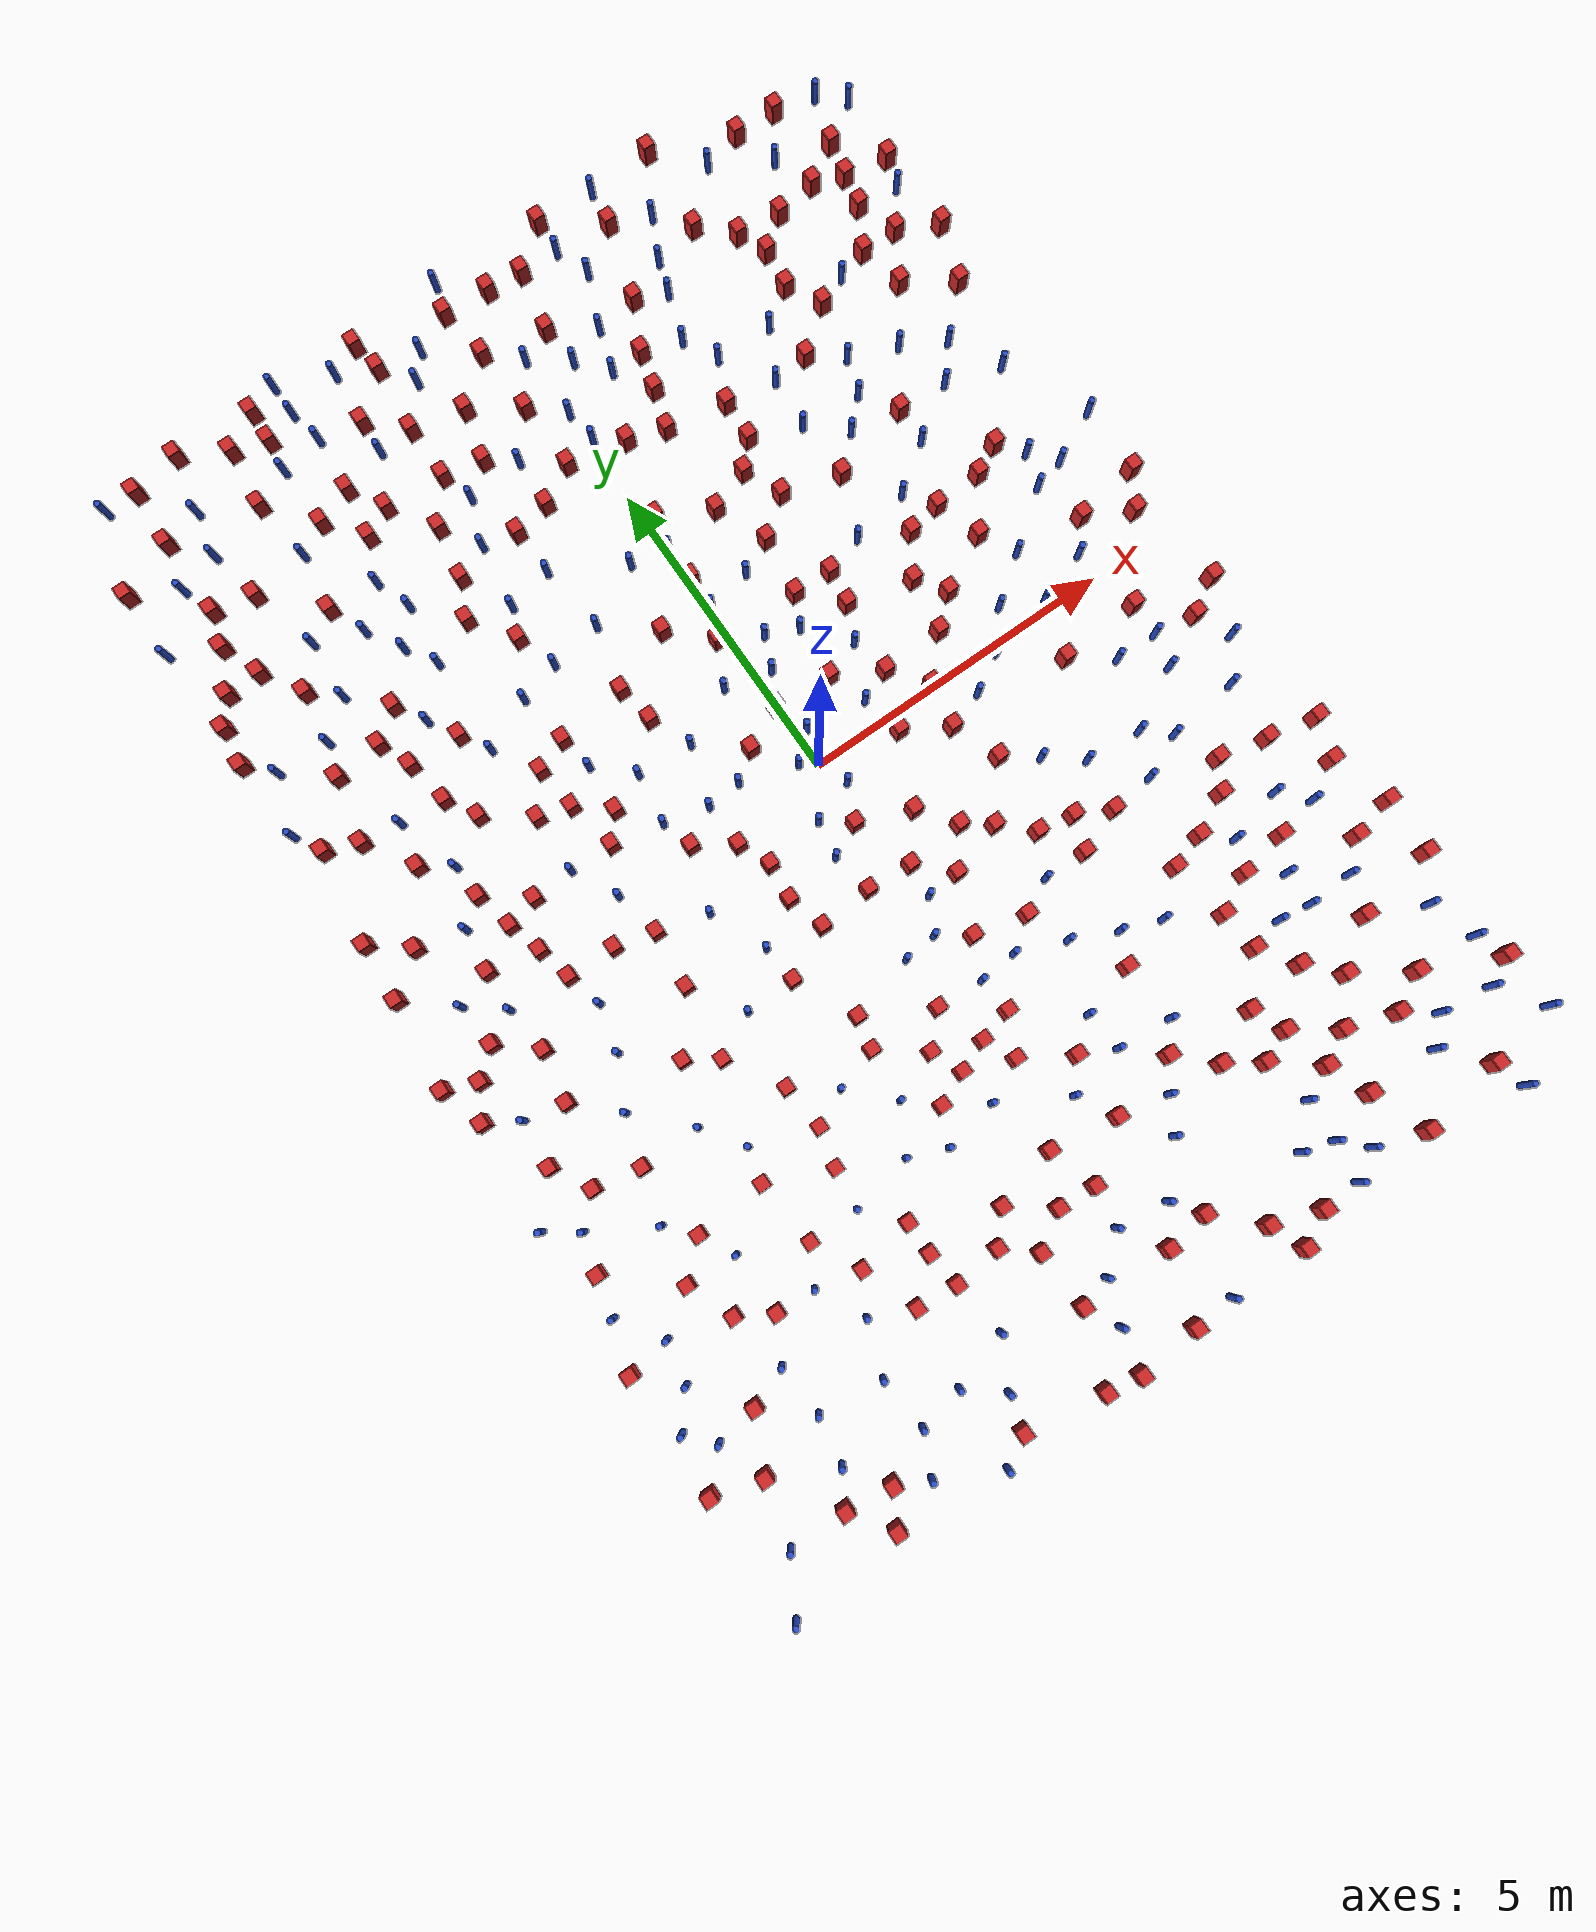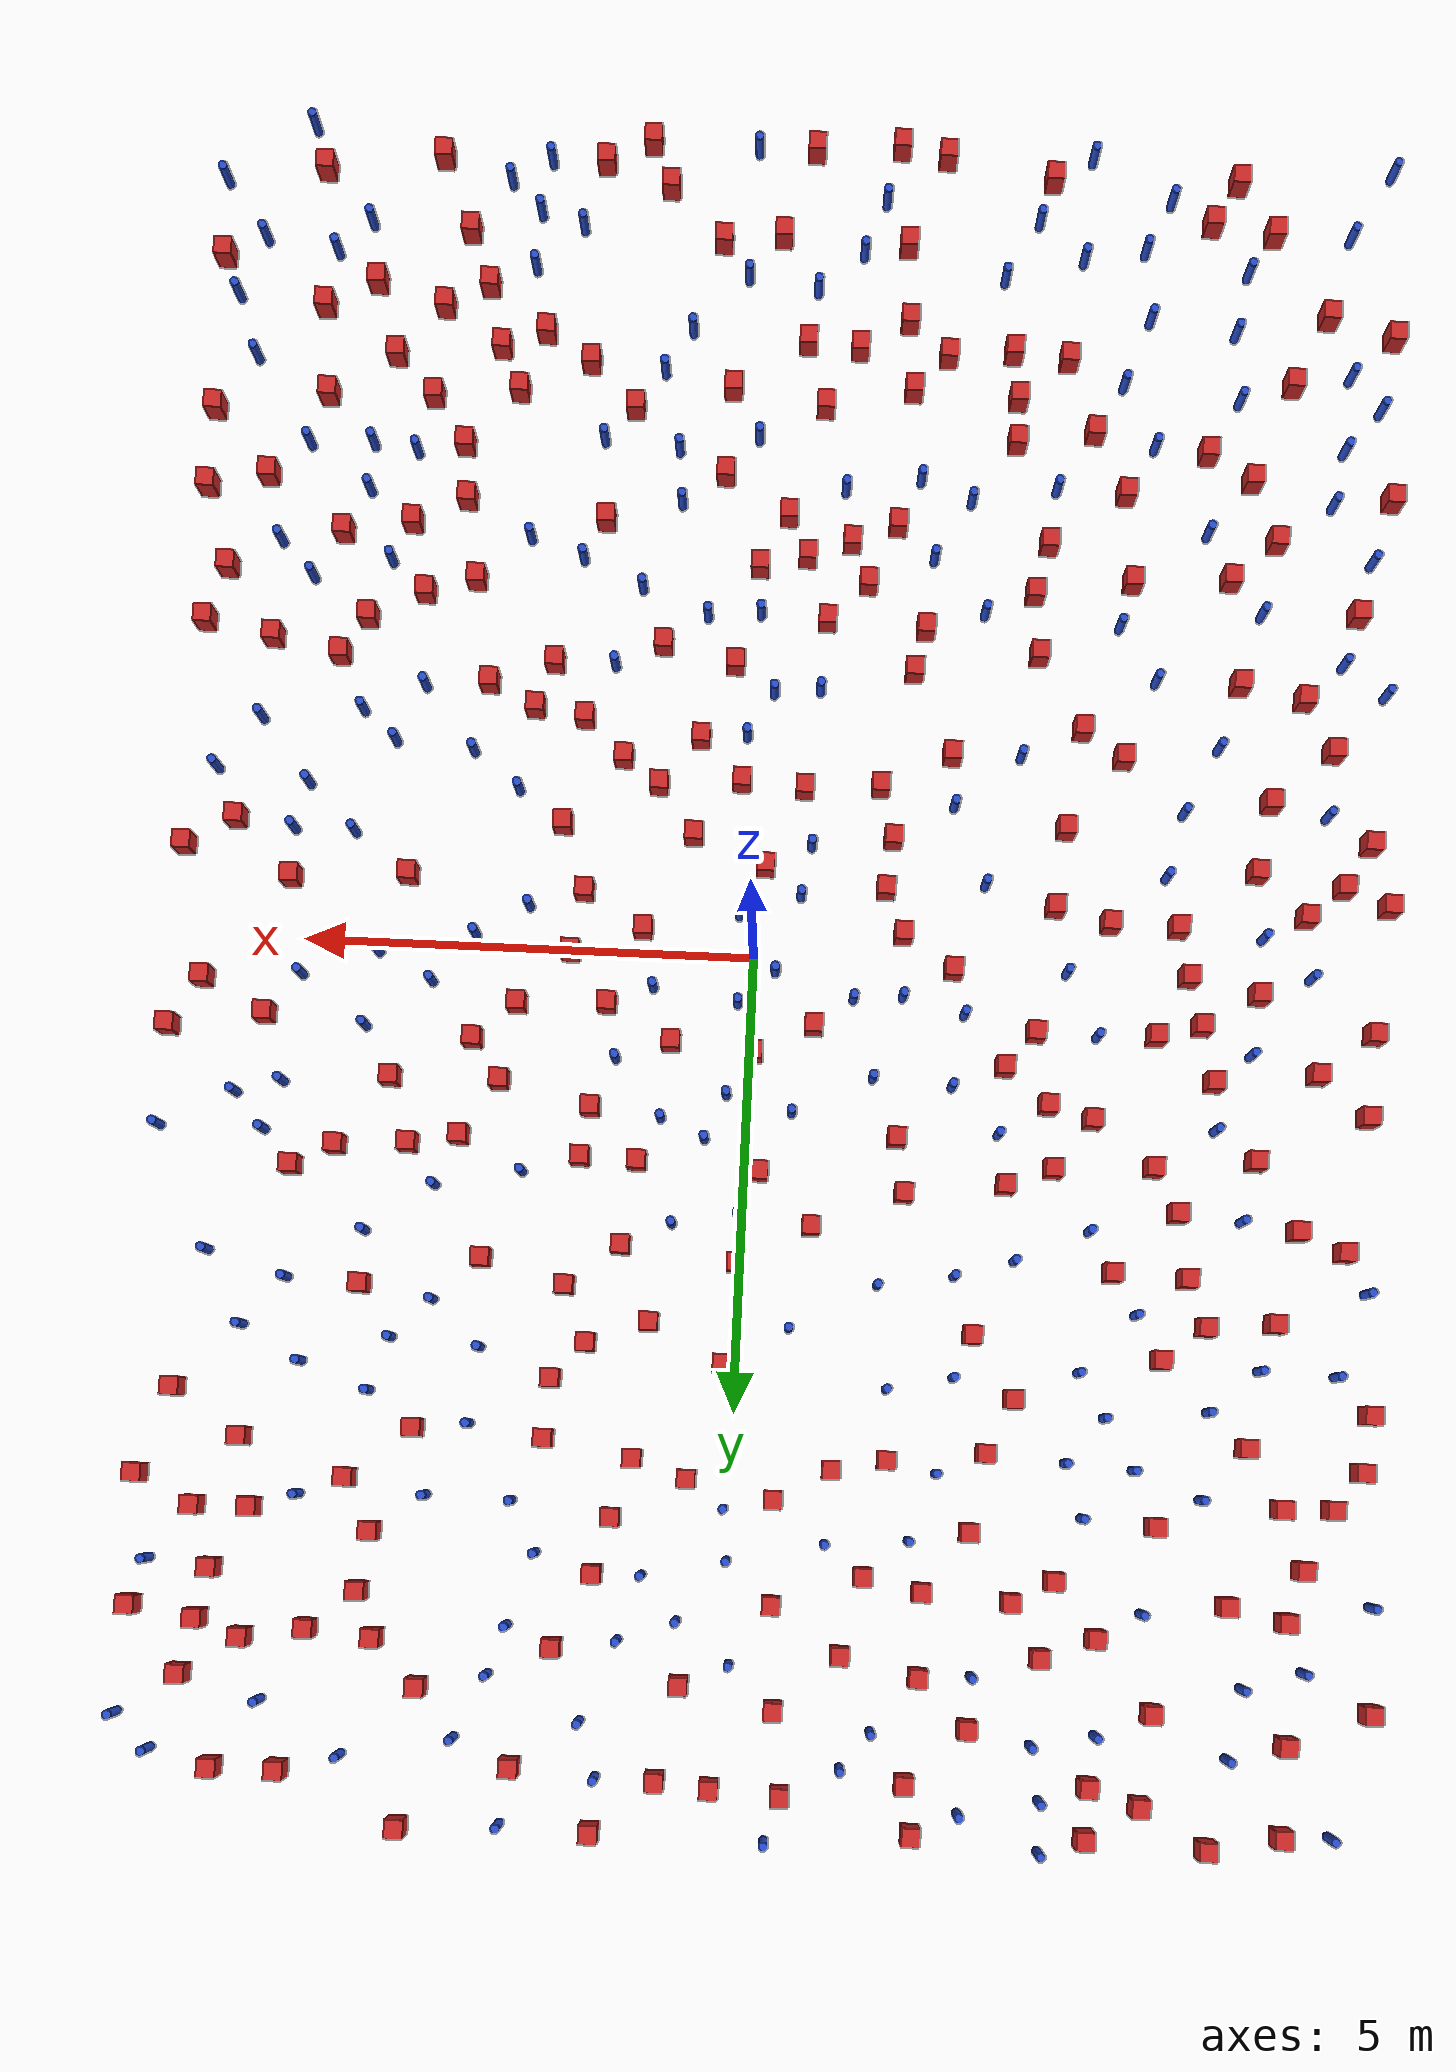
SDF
<sdf version="1.6">
  <model name="dense_62"><model name="pole_obstacle0">
  <static>true</static>
  <pose frame="">-0.240299481818 0.152974153635 -9.47619616065e-06 5.49618799737e-07 2.36310414057e-07 -1.55090534801e-07</pose>
  <link name="link">
  <pose frame="">0 0 0.3 0 -0 0</pose>
    <inertial>
      <mass>1</mass>
      <inertia>
        <ixx>0.145833</ixx>
        <ixy>0</ixy>
        <ixz>0</ixz>
        <iyy>0.145833</iyy>
        <iyz>0</iyz>
        <izz>0.125</izz>
      </inertia>
    </inertial>
    <collision name="collision">
      <geometry>
        <cylinder>
          <radius>0.05</radius>
          <length>.6</length>
        </cylinder>
      </geometry>
      <max_contacts>10</max_contacts>
      <surface>
        <contact>
          <ode/>
        </contact>
        <bounce/>
        <friction>
          <torsional>
            <ode/>
          </torsional>
          <ode/>
        </friction>
      </surface>
    </collision>
    <visual name="visual">
      <geometry>
        <cylinder>
          <radius>0.05</radius>
          <length>.6</length>
        </cylinder>
      </geometry>
      <material>
        <script>
          <name>Gazebo/Blue</name>
          <uri>file://media/materials/scripts/gazebo.material</uri>
        </script>
      </material>
    </visual>
    <self_collide>0</self_collide>
    <kinematic>0</kinematic>
  </link>
</model>
<model name="pole_obstacle1">
  <static>true</static>
  <pose frame="">2.85580955907 5.23067416467 -9.47619616065e-06 5.49618799738e-07 2.3631041406e-07 -1.55090534801e-07</pose>
  <link name="link">
  <pose frame="">0 0 0.3 0 -0 0</pose>
    <inertial>
      <mass>1</mass>
      <inertia>
        <ixx>0.145833</ixx>
        <ixy>0</ixy>
        <ixz>0</ixz>
        <iyy>0.145833</iyy>
        <iyz>0</iyz>
        <izz>0.125</izz>
      </inertia>
    </inertial>
    <collision name="collision">
      <geometry>
        <cylinder>
          <radius>0.05</radius>
          <length>.6</length>
        </cylinder>
      </geometry>
      <max_contacts>10</max_contacts>
      <surface>
        <contact>
          <ode/>
        </contact>
        <bounce/>
        <friction>
          <torsional>
            <ode/>
          </torsional>
          <ode/>
        </friction>
      </surface>
    </collision>
    <visual name="visual">
      <geometry>
        <cylinder>
          <radius>0.05</radius>
          <length>.6</length>
        </cylinder>
      </geometry>
      <material>
        <script>
          <name>Gazebo/Blue</name>
          <uri>file://media/materials/scripts/gazebo.material</uri>
        </script>
      </material>
    </visual>
    <self_collide>0</self_collide>
    <kinematic>0</kinematic>
  </link>
</model>
<model name="square_post_obstacle0">
  <static>true</static>
  <pose frame="">1.83028905246 7.55747029664 -6.11067671241e-07 -5.50515727128e-06 -8.79689657224e-07 2.37013304536e-05</pose>
  <link name="link">
    <pose frame="">0 0 0.25 0 -0 0</pose>
    <inertial>
      <mass>100</mass>
      <inertia>
        <ixx>0.166667</ixx>
        <ixy>0</ixy>
        <ixz>0</ixz>
        <iyy>0.166667</iyy>
        <iyz>0</iyz>
        <izz>0.166667</izz>
      </inertia>
    </inertial>
    <collision name="collision">
      <geometry>
        <box>
          <size>.2 .2 .5</size>
        </box>
      </geometry>
      <max_contacts>10</max_contacts>
      <surface>
        <contact>
          <ode/>
        </contact>
        <bounce/>
        <friction>
          <torsional>
            <ode/>
          </torsional>
          <ode/>
        </friction>
      </surface>
    </collision>
    <visual name="visual">
      <geometry>
        <box>
          <size>.2 .2 .5</size>
        </box>
      </geometry>
      <material>
        <script>
          <name>Gazebo/Red</name>
          <uri>file://media/materials/scripts/gazebo.material</uri>
        </script>
      </material>
    </visual>
    <self_collide>0</self_collide>
    <kinematic>0</kinematic>
  </link>
</model>
<model name="square_post_obstacle1">
  <static>true</static>
  <pose frame="">-3.93101011616 8.76190546787 -6.11067671241e-07 -5.50515727128e-06 -8.79689657224e-07 2.37013304536e-05</pose>
  <link name="link">
    <pose frame="">0 0 0.25 0 -0 0</pose>
    <inertial>
      <mass>100</mass>
      <inertia>
        <ixx>0.166667</ixx>
        <ixy>0</ixy>
        <ixz>0</ixz>
        <iyy>0.166667</iyy>
        <iyz>0</iyz>
        <izz>0.166667</izz>
      </inertia>
    </inertial>
    <collision name="collision">
      <geometry>
        <box>
          <size>.2 .2 .5</size>
        </box>
      </geometry>
      <max_contacts>10</max_contacts>
      <surface>
        <contact>
          <ode/>
        </contact>
        <bounce/>
        <friction>
          <torsional>
            <ode/>
          </torsional>
          <ode/>
        </friction>
      </surface>
    </collision>
    <visual name="visual">
      <geometry>
        <box>
          <size>.2 .2 .5</size>
        </box>
      </geometry>
      <material>
        <script>
          <name>Gazebo/Red</name>
          <uri>file://media/materials/scripts/gazebo.material</uri>
        </script>
      </material>
    </visual>
    <self_collide>0</self_collide>
    <kinematic>0</kinematic>
  </link>
</model>
<model name="pole_obstacle2">
  <static>true</static>
  <pose frame="">-0.487812181251 1.71194919246 -9.47619616065e-06 5.49618799738e-07 2.36310414059e-07 -1.55090534802e-07</pose>
  <link name="link">
  <pose frame="">0 0 0.3 0 -0 0</pose>
    <inertial>
      <mass>1</mass>
      <inertia>
        <ixx>0.145833</ixx>
        <ixy>0</ixy>
        <ixz>0</ixz>
        <iyy>0.145833</iyy>
        <iyz>0</iyz>
        <izz>0.125</izz>
      </inertia>
    </inertial>
    <collision name="collision">
      <geometry>
        <cylinder>
          <radius>0.05</radius>
          <length>.6</length>
        </cylinder>
      </geometry>
      <max_contacts>10</max_contacts>
      <surface>
        <contact>
          <ode/>
        </contact>
        <bounce/>
        <friction>
          <torsional>
            <ode/>
          </torsional>
          <ode/>
        </friction>
      </surface>
    </collision>
    <visual name="visual">
      <geometry>
        <cylinder>
          <radius>0.05</radius>
          <length>.6</length>
        </cylinder>
      </geometry>
      <material>
        <script>
          <name>Gazebo/Blue</name>
          <uri>file://media/materials/scripts/gazebo.material</uri>
        </script>
      </material>
    </visual>
    <self_collide>0</self_collide>
    <kinematic>0</kinematic>
  </link>
</model>
<model name="pole_obstacle3">
  <static>true</static>
  <pose frame="">-5.50317847386 0.870224016151 -9.47619616065e-06 5.49618799737e-07 2.36310414061e-07 -1.550905348e-07</pose>
  <link name="link">
  <pose frame="">0 0 0.3 0 -0 0</pose>
    <inertial>
      <mass>1</mass>
      <inertia>
        <ixx>0.145833</ixx>
        <ixy>0</ixy>
        <ixz>0</ixz>
        <iyy>0.145833</iyy>
        <iyz>0</iyz>
        <izz>0.125</izz>
      </inertia>
    </inertial>
    <collision name="collision">
      <geometry>
        <cylinder>
          <radius>0.05</radius>
          <length>.6</length>
        </cylinder>
      </geometry>
      <max_contacts>10</max_contacts>
      <surface>
        <contact>
          <ode/>
        </contact>
        <bounce/>
        <friction>
          <torsional>
            <ode/>
          </torsional>
          <ode/>
        </friction>
      </surface>
    </collision>
    <visual name="visual">
      <geometry>
        <cylinder>
          <radius>0.05</radius>
          <length>.6</length>
        </cylinder>
      </geometry>
      <material>
        <script>
          <name>Gazebo/Blue</name>
          <uri>file://media/materials/scripts/gazebo.material</uri>
        </script>
      </material>
    </visual>
    <self_collide>0</self_collide>
    <kinematic>0</kinematic>
  </link>
</model>
<model name="pole_obstacle4">
  <static>true</static>
  <pose frame="">-0.489798649073 -0.701766864221 -9.47619616065e-06 5.49618799737e-07 2.3631041405e-07 -1.55090534807e-07</pose>
  <link name="link">
  <pose frame="">0 0 0.3 0 -0 0</pose>
    <inertial>
      <mass>1</mass>
      <inertia>
        <ixx>0.145833</ixx>
        <ixy>0</ixy>
        <ixz>0</ixz>
        <iyy>0.145833</iyy>
        <iyz>0</iyz>
        <izz>0.125</izz>
      </inertia>
    </inertial>
    <collision name="collision">
      <geometry>
        <cylinder>
          <radius>0.05</radius>
          <length>.6</length>
        </cylinder>
      </geometry>
      <max_contacts>10</max_contacts>
      <surface>
        <contact>
          <ode/>
        </contact>
        <bounce/>
        <friction>
          <torsional>
            <ode/>
          </torsional>
          <ode/>
        </friction>
      </surface>
    </collision>
    <visual name="visual">
      <geometry>
        <cylinder>
          <radius>0.05</radius>
          <length>.6</length>
        </cylinder>
      </geometry>
      <material>
        <script>
          <name>Gazebo/Blue</name>
          <uri>file://media/materials/scripts/gazebo.material</uri>
        </script>
      </material>
    </visual>
    <self_collide>0</self_collide>
    <kinematic>0</kinematic>
  </link>
</model>
<model name="pole_obstacle5">
  <static>true</static>
  <pose frame="">-3.71422850612 4.40279073542 -9.47619616065e-06 5.49618799738e-07 2.3631041406e-07 -1.55090534801e-07</pose>
  <link name="link">
  <pose frame="">0 0 0.3 0 -0 0</pose>
    <inertial>
      <mass>1</mass>
      <inertia>
        <ixx>0.145833</ixx>
        <ixy>0</ixy>
        <ixz>0</ixz>
        <iyy>0.145833</iyy>
        <iyz>0</iyz>
        <izz>0.125</izz>
      </inertia>
    </inertial>
    <collision name="collision">
      <geometry>
        <cylinder>
          <radius>0.05</radius>
          <length>.6</length>
        </cylinder>
      </geometry>
      <max_contacts>10</max_contacts>
      <surface>
        <contact>
          <ode/>
        </contact>
        <bounce/>
        <friction>
          <torsional>
            <ode/>
          </torsional>
          <ode/>
        </friction>
      </surface>
    </collision>
    <visual name="visual">
      <geometry>
        <cylinder>
          <radius>0.05</radius>
          <length>.6</length>
        </cylinder>
      </geometry>
      <material>
        <script>
          <name>Gazebo/Blue</name>
          <uri>file://media/materials/scripts/gazebo.material</uri>
        </script>
      </material>
    </visual>
    <self_collide>0</self_collide>
    <kinematic>0</kinematic>
  </link>
</model>
<model name="pole_obstacle6">
  <static>true</static>
  <pose frame="">-6.73994371988 -4.76425897762 -9.47619616065e-06 5.49618799737e-07 2.36310414037e-07 -1.55090534814e-07</pose>
  <link name="link">
  <pose frame="">0 0 0.3 0 -0 0</pose>
    <inertial>
      <mass>1</mass>
      <inertia>
        <ixx>0.145833</ixx>
        <ixy>0</ixy>
        <ixz>0</ixz>
        <iyy>0.145833</iyy>
        <iyz>0</iyz>
        <izz>0.125</izz>
      </inertia>
    </inertial>
    <collision name="collision">
      <geometry>
        <cylinder>
          <radius>0.05</radius>
          <length>.6</length>
        </cylinder>
      </geometry>
      <max_contacts>10</max_contacts>
      <surface>
        <contact>
          <ode/>
        </contact>
        <bounce/>
        <friction>
          <torsional>
            <ode/>
          </torsional>
          <ode/>
        </friction>
      </surface>
    </collision>
    <visual name="visual">
      <geometry>
        <cylinder>
          <radius>0.05</radius>
          <length>.6</length>
        </cylinder>
      </geometry>
      <material>
        <script>
          <name>Gazebo/Blue</name>
          <uri>file://media/materials/scripts/gazebo.material</uri>
        </script>
      </material>
    </visual>
    <self_collide>0</self_collide>
    <kinematic>0</kinematic>
  </link>
</model>
<model name="square_post_obstacle2">
  <static>true</static>
  <pose frame="">-4.66760439507 -0.521512777751 -6.11067671241e-07 -5.50515727128e-06 -8.79689657224e-07 2.37013304536e-05</pose>
  <link name="link">
    <pose frame="">0 0 0.25 0 -0 0</pose>
    <inertial>
      <mass>100</mass>
      <inertia>
        <ixx>0.166667</ixx>
        <ixy>0</ixy>
        <ixz>0</ixz>
        <iyy>0.166667</iyy>
        <iyz>0</iyz>
        <izz>0.166667</izz>
      </inertia>
    </inertial>
    <collision name="collision">
      <geometry>
        <box>
          <size>.2 .2 .5</size>
        </box>
      </geometry>
      <max_contacts>10</max_contacts>
      <surface>
        <contact>
          <ode/>
        </contact>
        <bounce/>
        <friction>
          <torsional>
            <ode/>
          </torsional>
          <ode/>
        </friction>
      </surface>
    </collision>
    <visual name="visual">
      <geometry>
        <box>
          <size>.2 .2 .5</size>
        </box>
      </geometry>
      <material>
        <script>
          <name>Gazebo/Red</name>
          <uri>file://media/materials/scripts/gazebo.material</uri>
        </script>
      </material>
    </visual>
    <self_collide>0</self_collide>
    <kinematic>0</kinematic>
  </link>
</model>
<model name="square_post_obstacle3">
  <static>true</static>
  <pose frame="">-3.95371555942 -5.46030801869 -6.11067671241e-07 -5.50515727128e-06 -8.79689657224e-07 2.37013304536e-05</pose>
  <link name="link">
    <pose frame="">0 0 0.25 0 -0 0</pose>
    <inertial>
      <mass>100</mass>
      <inertia>
        <ixx>0.166667</ixx>
        <ixy>0</ixy>
        <ixz>0</ixz>
        <iyy>0.166667</iyy>
        <iyz>0</iyz>
        <izz>0.166667</izz>
      </inertia>
    </inertial>
    <collision name="collision">
      <geometry>
        <box>
          <size>.2 .2 .5</size>
        </box>
      </geometry>
      <max_contacts>10</max_contacts>
      <surface>
        <contact>
          <ode/>
        </contact>
        <bounce/>
        <friction>
          <torsional>
            <ode/>
          </torsional>
          <ode/>
        </friction>
      </surface>
    </collision>
    <visual name="visual">
      <geometry>
        <box>
          <size>.2 .2 .5</size>
        </box>
      </geometry>
      <material>
        <script>
          <name>Gazebo/Red</name>
          <uri>file://media/materials/scripts/gazebo.material</uri>
        </script>
      </material>
    </visual>
    <self_collide>0</self_collide>
    <kinematic>0</kinematic>
  </link>
</model>
<model name="square_post_obstacle4">
  <static>true</static>
  <pose frame="">3.69280537728 2.22293517333 -6.11067671241e-07 -5.50515727128e-06 -8.79689657224e-07 2.37013304536e-05</pose>
  <link name="link">
    <pose frame="">0 0 0.25 0 -0 0</pose>
    <inertial>
      <mass>100</mass>
      <inertia>
        <ixx>0.166667</ixx>
        <ixy>0</ixy>
        <ixz>0</ixz>
        <iyy>0.166667</iyy>
        <iyz>0</iyz>
        <izz>0.166667</izz>
      </inertia>
    </inertial>
    <collision name="collision">
      <geometry>
        <box>
          <size>.2 .2 .5</size>
        </box>
      </geometry>
      <max_contacts>10</max_contacts>
      <surface>
        <contact>
          <ode/>
        </contact>
        <bounce/>
        <friction>
          <torsional>
            <ode/>
          </torsional>
          <ode/>
        </friction>
      </surface>
    </collision>
    <visual name="visual">
      <geometry>
        <box>
          <size>.2 .2 .5</size>
        </box>
      </geometry>
      <material>
        <script>
          <name>Gazebo/Red</name>
          <uri>file://media/materials/scripts/gazebo.material</uri>
        </script>
      </material>
    </visual>
    <self_collide>0</self_collide>
    <kinematic>0</kinematic>
  </link>
</model>
<model name="pole_obstacle7">
  <static>true</static>
  <pose frame="">-5.06785787233 -2.56014334162 -9.47619616065e-06 5.49618799738e-07 2.36310414051e-07 -1.55090534805e-07</pose>
  <link name="link">
  <pose frame="">0 0 0.3 0 -0 0</pose>
    <inertial>
      <mass>1</mass>
      <inertia>
        <ixx>0.145833</ixx>
        <ixy>0</ixy>
        <ixz>0</ixz>
        <iyy>0.145833</iyy>
        <iyz>0</iyz>
        <izz>0.125</izz>
      </inertia>
    </inertial>
    <collision name="collision">
      <geometry>
        <cylinder>
          <radius>0.05</radius>
          <length>.6</length>
        </cylinder>
      </geometry>
      <max_contacts>10</max_contacts>
      <surface>
        <contact>
          <ode/>
        </contact>
        <bounce/>
        <friction>
          <torsional>
            <ode/>
          </torsional>
          <ode/>
        </friction>
      </surface>
    </collision>
    <visual name="visual">
      <geometry>
        <cylinder>
          <radius>0.05</radius>
          <length>.6</length>
        </cylinder>
      </geometry>
      <material>
        <script>
          <name>Gazebo/Blue</name>
          <uri>file://media/materials/scripts/gazebo.material</uri>
        </script>
      </material>
    </visual>
    <self_collide>0</self_collide>
    <kinematic>0</kinematic>
  </link>
</model>
<model name="pole_obstacle8">
  <static>true</static>
  <pose frame="">0.767769919635 2.98122470118 -9.47619616065e-06 5.49618799737e-07 2.36310414066e-07 -1.55090534797e-07</pose>
  <link name="link">
  <pose frame="">0 0 0.3 0 -0 0</pose>
    <inertial>
      <mass>1</mass>
      <inertia>
        <ixx>0.145833</ixx>
        <ixy>0</ixy>
        <ixz>0</ixz>
        <iyy>0.145833</iyy>
        <iyz>0</iyz>
        <izz>0.125</izz>
      </inertia>
    </inertial>
    <collision name="collision">
      <geometry>
        <cylinder>
          <radius>0.05</radius>
          <length>.6</length>
        </cylinder>
      </geometry>
      <max_contacts>10</max_contacts>
      <surface>
        <contact>
          <ode/>
        </contact>
        <bounce/>
        <friction>
          <torsional>
            <ode/>
          </torsional>
          <ode/>
        </friction>
      </surface>
    </collision>
    <visual name="visual">
      <geometry>
        <cylinder>
          <radius>0.05</radius>
          <length>.6</length>
        </cylinder>
      </geometry>
      <material>
        <script>
          <name>Gazebo/Blue</name>
          <uri>file://media/materials/scripts/gazebo.material</uri>
        </script>
      </material>
    </visual>
    <self_collide>0</self_collide>
    <kinematic>0</kinematic>
  </link>
</model>
<model name="square_post_obstacle5">
  <static>true</static>
  <pose frame="">-1.48127883033 -1.39184149811 -6.11067671241e-07 -5.50515727128e-06 -8.79689657224e-07 2.37013304536e-05</pose>
  <link name="link">
    <pose frame="">0 0 0.25 0 -0 0</pose>
    <inertial>
      <mass>100</mass>
      <inertia>
        <ixx>0.166667</ixx>
        <ixy>0</ixy>
        <ixz>0</ixz>
        <iyy>0.166667</iyy>
        <iyz>0</iyz>
        <izz>0.166667</izz>
      </inertia>
    </inertial>
    <collision name="collision">
      <geometry>
        <box>
          <size>.2 .2 .5</size>
        </box>
      </geometry>
      <max_contacts>10</max_contacts>
      <surface>
        <contact>
          <ode/>
        </contact>
        <bounce/>
        <friction>
          <torsional>
            <ode/>
          </torsional>
          <ode/>
        </friction>
      </surface>
    </collision>
    <visual name="visual">
      <geometry>
        <box>
          <size>.2 .2 .5</size>
        </box>
      </geometry>
      <material>
        <script>
          <name>Gazebo/Red</name>
          <uri>file://media/materials/scripts/gazebo.material</uri>
        </script>
      </material>
    </visual>
    <self_collide>0</self_collide>
    <kinematic>0</kinematic>
  </link>
</model>
<model name="square_post_obstacle6">
  <static>true</static>
  <pose frame="">6.10533569681 -4.18703966137 -6.11067671241e-07 -5.50515727128e-06 -8.79689657224e-07 2.37013304536e-05</pose>
  <link name="link">
    <pose frame="">0 0 0.25 0 -0 0</pose>
    <inertial>
      <mass>100</mass>
      <inertia>
        <ixx>0.166667</ixx>
        <ixy>0</ixy>
        <ixz>0</ixz>
        <iyy>0.166667</iyy>
        <iyz>0</iyz>
        <izz>0.166667</izz>
      </inertia>
    </inertial>
    <collision name="collision">
      <geometry>
        <box>
          <size>.2 .2 .5</size>
        </box>
      </geometry>
      <max_contacts>10</max_contacts>
      <surface>
        <contact>
          <ode/>
        </contact>
        <bounce/>
        <friction>
          <torsional>
            <ode/>
          </torsional>
          <ode/>
        </friction>
      </surface>
    </collision>
    <visual name="visual">
      <geometry>
        <box>
          <size>.2 .2 .5</size>
        </box>
      </geometry>
      <material>
        <script>
          <name>Gazebo/Red</name>
          <uri>file://media/materials/scripts/gazebo.material</uri>
        </script>
      </material>
    </visual>
    <self_collide>0</self_collide>
    <kinematic>0</kinematic>
  </link>
</model>
<model name="square_post_obstacle7">
  <static>true</static>
  <pose frame="">3.92760608452 1.5035485975 -6.11067671241e-07 -5.50515727128e-06 -8.79689657224e-07 2.37013304536e-05</pose>
  <link name="link">
    <pose frame="">0 0 0.25 0 -0 0</pose>
    <inertial>
      <mass>100</mass>
      <inertia>
        <ixx>0.166667</ixx>
        <ixy>0</ixy>
        <ixz>0</ixz>
        <iyy>0.166667</iyy>
        <iyz>0</iyz>
        <izz>0.166667</izz>
      </inertia>
    </inertial>
    <collision name="collision">
      <geometry>
        <box>
          <size>.2 .2 .5</size>
        </box>
      </geometry>
      <max_contacts>10</max_contacts>
      <surface>
        <contact>
          <ode/>
        </contact>
        <bounce/>
        <friction>
          <torsional>
            <ode/>
          </torsional>
          <ode/>
        </friction>
      </surface>
    </collision>
    <visual name="visual">
      <geometry>
        <box>
          <size>.2 .2 .5</size>
        </box>
      </geometry>
      <material>
        <script>
          <name>Gazebo/Red</name>
          <uri>file://media/materials/scripts/gazebo.material</uri>
        </script>
      </material>
    </visual>
    <self_collide>0</self_collide>
    <kinematic>0</kinematic>
  </link>
</model>
<model name="pole_obstacle9">
  <static>true</static>
  <pose frame="">-3.79374008691 5.95631471667 -9.47619616065e-06 5.49618799738e-07 2.3631041406e-07 -1.55090534801e-07</pose>
  <link name="link">
  <pose frame="">0 0 0.3 0 -0 0</pose>
    <inertial>
      <mass>1</mass>
      <inertia>
        <ixx>0.145833</ixx>
        <ixy>0</ixy>
        <ixz>0</ixz>
        <iyy>0.145833</iyy>
        <iyz>0</iyz>
        <izz>0.125</izz>
      </inertia>
    </inertial>
    <collision name="collision">
      <geometry>
        <cylinder>
          <radius>0.05</radius>
          <length>.6</length>
        </cylinder>
      </geometry>
      <max_contacts>10</max_contacts>
      <surface>
        <contact>
          <ode/>
        </contact>
        <bounce/>
        <friction>
          <torsional>
            <ode/>
          </torsional>
          <ode/>
        </friction>
      </surface>
    </collision>
    <visual name="visual">
      <geometry>
        <cylinder>
          <radius>0.05</radius>
          <length>.6</length>
        </cylinder>
      </geometry>
      <material>
        <script>
          <name>Gazebo/Blue</name>
          <uri>file://media/materials/scripts/gazebo.material</uri>
        </script>
      </material>
    </visual>
    <self_collide>0</self_collide>
    <kinematic>0</kinematic>
  </link>
</model>
<model name="pole_obstacle10">
  <static>true</static>
  <pose frame="">-6.29512703898 -1.83872455876 -9.47619616065e-06 5.49618799738e-07 2.36310414071e-07 -1.55090534796e-07</pose>
  <link name="link">
  <pose frame="">0 0 0.3 0 -0 0</pose>
    <inertial>
      <mass>1</mass>
      <inertia>
        <ixx>0.145833</ixx>
        <ixy>0</ixy>
        <ixz>0</ixz>
        <iyy>0.145833</iyy>
        <iyz>0</iyz>
        <izz>0.125</izz>
      </inertia>
    </inertial>
    <collision name="collision">
      <geometry>
        <cylinder>
          <radius>0.05</radius>
          <length>.6</length>
        </cylinder>
      </geometry>
      <max_contacts>10</max_contacts>
      <surface>
        <contact>
          <ode/>
        </contact>
        <bounce/>
        <friction>
          <torsional>
            <ode/>
          </torsional>
          <ode/>
        </friction>
      </surface>
    </collision>
    <visual name="visual">
      <geometry>
        <cylinder>
          <radius>0.05</radius>
          <length>.6</length>
        </cylinder>
      </geometry>
      <material>
        <script>
          <name>Gazebo/Blue</name>
          <uri>file://media/materials/scripts/gazebo.material</uri>
        </script>
      </material>
    </visual>
    <self_collide>0</self_collide>
    <kinematic>0</kinematic>
  </link>
</model>
<model name="pole_obstacle11">
  <static>true</static>
  <pose frame="">-4.38404824657 -8.93209616791 -9.47619616065e-06 5.49618799737e-07 2.36310414065e-07 -1.55090534796e-07</pose>
  <link name="link">
  <pose frame="">0 0 0.3 0 -0 0</pose>
    <inertial>
      <mass>1</mass>
      <inertia>
        <ixx>0.145833</ixx>
        <ixy>0</ixy>
        <ixz>0</ixz>
        <iyy>0.145833</iyy>
        <iyz>0</iyz>
        <izz>0.125</izz>
      </inertia>
    </inertial>
    <collision name="collision">
      <geometry>
        <cylinder>
          <radius>0.05</radius>
          <length>.6</length>
        </cylinder>
      </geometry>
      <max_contacts>10</max_contacts>
      <surface>
        <contact>
          <ode/>
        </contact>
        <bounce/>
        <friction>
          <torsional>
            <ode/>
          </torsional>
          <ode/>
        </friction>
      </surface>
    </collision>
    <visual name="visual">
      <geometry>
        <cylinder>
          <radius>0.05</radius>
          <length>.6</length>
        </cylinder>
      </geometry>
      <material>
        <script>
          <name>Gazebo/Blue</name>
          <uri>file://media/materials/scripts/gazebo.material</uri>
        </script>
      </material>
    </visual>
    <self_collide>0</self_collide>
    <kinematic>0</kinematic>
  </link>
</model>
<model name="pole_obstacle12">
  <static>true</static>
  <pose frame="">5.93281669993 -8.06268216293 -9.47619616065e-06 5.49618799737e-07 2.36310414065e-07 -1.55090534796e-07</pose>
  <link name="link">
  <pose frame="">0 0 0.3 0 -0 0</pose>
    <inertial>
      <mass>1</mass>
      <inertia>
        <ixx>0.145833</ixx>
        <ixy>0</ixy>
        <ixz>0</ixz>
        <iyy>0.145833</iyy>
        <iyz>0</iyz>
        <izz>0.125</izz>
      </inertia>
    </inertial>
    <collision name="collision">
      <geometry>
        <cylinder>
          <radius>0.05</radius>
          <length>.6</length>
        </cylinder>
      </geometry>
      <max_contacts>10</max_contacts>
      <surface>
        <contact>
          <ode/>
        </contact>
        <bounce/>
        <friction>
          <torsional>
            <ode/>
          </torsional>
          <ode/>
        </friction>
      </surface>
    </collision>
    <visual name="visual">
      <geometry>
        <cylinder>
          <radius>0.05</radius>
          <length>.6</length>
        </cylinder>
      </geometry>
      <material>
        <script>
          <name>Gazebo/Blue</name>
          <uri>file://media/materials/scripts/gazebo.material</uri>
        </script>
      </material>
    </visual>
    <self_collide>0</self_collide>
    <kinematic>0</kinematic>
  </link>
</model>
<model name="square_post_obstacle8">
  <static>true</static>
  <pose frame="">3.74884087487 7.5368950362 -6.11067671241e-07 -5.50515727128e-06 -8.79689657224e-07 2.37013304536e-05</pose>
  <link name="link">
    <pose frame="">0 0 0.25 0 -0 0</pose>
    <inertial>
      <mass>100</mass>
      <inertia>
        <ixx>0.166667</ixx>
        <ixy>0</ixy>
        <ixz>0</ixz>
        <iyy>0.166667</iyy>
        <iyz>0</iyz>
        <izz>0.166667</izz>
      </inertia>
    </inertial>
    <collision name="collision">
      <geometry>
        <box>
          <size>.2 .2 .5</size>
        </box>
      </geometry>
      <max_contacts>10</max_contacts>
      <surface>
        <contact>
          <ode/>
        </contact>
        <bounce/>
        <friction>
          <torsional>
            <ode/>
          </torsional>
          <ode/>
        </friction>
      </surface>
    </collision>
    <visual name="visual">
      <geometry>
        <box>
          <size>.2 .2 .5</size>
        </box>
      </geometry>
      <material>
        <script>
          <name>Gazebo/Red</name>
          <uri>file://media/materials/scripts/gazebo.material</uri>
        </script>
      </material>
    </visual>
    <self_collide>0</self_collide>
    <kinematic>0</kinematic>
  </link>
</model>
<model name="square_post_obstacle9">
  <static>true</static>
  <pose frame="">-0.477985754404 -1.91767797434 -6.11067671241e-07 -5.50515727128e-06 -8.79689657224e-07 2.37013304536e-05</pose>
  <link name="link">
    <pose frame="">0 0 0.25 0 -0 0</pose>
    <inertial>
      <mass>100</mass>
      <inertia>
        <ixx>0.166667</ixx>
        <ixy>0</ixy>
        <ixz>0</ixz>
        <iyy>0.166667</iyy>
        <iyz>0</iyz>
        <izz>0.166667</izz>
      </inertia>
    </inertial>
    <collision name="collision">
      <geometry>
        <box>
          <size>.2 .2 .5</size>
        </box>
      </geometry>
      <max_contacts>10</max_contacts>
      <surface>
        <contact>
          <ode/>
        </contact>
        <bounce/>
        <friction>
          <torsional>
            <ode/>
          </torsional>
          <ode/>
        </friction>
      </surface>
    </collision>
    <visual name="visual">
      <geometry>
        <box>
          <size>.2 .2 .5</size>
        </box>
      </geometry>
      <material>
        <script>
          <name>Gazebo/Red</name>
          <uri>file://media/materials/scripts/gazebo.material</uri>
        </script>
      </material>
    </visual>
    <self_collide>0</self_collide>
    <kinematic>0</kinematic>
  </link>
</model>
<model name="pole_obstacle13">
  <static>true</static>
  <pose frame="">-1.12992087261 -8.8009247254 -9.47619616065e-06 5.49618799737e-07 2.36310414046e-07 -1.55090534809e-07</pose>
  <link name="link">
  <pose frame="">0 0 0.3 0 -0 0</pose>
    <inertial>
      <mass>1</mass>
      <inertia>
        <ixx>0.145833</ixx>
        <ixy>0</ixy>
        <ixz>0</ixz>
        <iyy>0.145833</iyy>
        <iyz>0</iyz>
        <izz>0.125</izz>
      </inertia>
    </inertial>
    <collision name="collision">
      <geometry>
        <cylinder>
          <radius>0.05</radius>
          <length>.6</length>
        </cylinder>
      </geometry>
      <max_contacts>10</max_contacts>
      <surface>
        <contact>
          <ode/>
        </contact>
        <bounce/>
        <friction>
          <torsional>
            <ode/>
          </torsional>
          <ode/>
        </friction>
      </surface>
    </collision>
    <visual name="visual">
      <geometry>
        <cylinder>
          <radius>0.05</radius>
          <length>.6</length>
        </cylinder>
      </geometry>
      <material>
        <script>
          <name>Gazebo/Blue</name>
          <uri>file://media/materials/scripts/gazebo.material</uri>
        </script>
      </material>
    </visual>
    <self_collide>0</self_collide>
    <kinematic>0</kinematic>
  </link>
</model>
<model name="square_post_obstacle10">
  <static>true</static>
  <pose frame="">2.00440950209 -2.61996437505 -6.11067671241e-07 -5.50515727128e-06 -8.79689657224e-07 2.37013304536e-05</pose>
  <link name="link">
    <pose frame="">0 0 0.25 0 -0 0</pose>
    <inertial>
      <mass>100</mass>
      <inertia>
        <ixx>0.166667</ixx>
        <ixy>0</ixy>
        <ixz>0</ixz>
        <iyy>0.166667</iyy>
        <iyz>0</iyz>
        <izz>0.166667</izz>
      </inertia>
    </inertial>
    <collision name="collision">
      <geometry>
        <box>
          <size>.2 .2 .5</size>
        </box>
      </geometry>
      <max_contacts>10</max_contacts>
      <surface>
        <contact>
          <ode/>
        </contact>
        <bounce/>
        <friction>
          <torsional>
            <ode/>
          </torsional>
          <ode/>
        </friction>
      </surface>
    </collision>
    <visual name="visual">
      <geometry>
        <box>
          <size>.2 .2 .5</size>
        </box>
      </geometry>
      <material>
        <script>
          <name>Gazebo/Red</name>
          <uri>file://media/materials/scripts/gazebo.material</uri>
        </script>
      </material>
    </visual>
    <self_collide>0</self_collide>
    <kinematic>0</kinematic>
  </link>
</model>
<model name="square_post_obstacle11">
  <static>true</static>
  <pose frame="">-5.14176364315 -9.19598783528 -6.11067671241e-07 -5.50515727128e-06 -8.79689657224e-07 2.37013304536e-05</pose>
  <link name="link">
    <pose frame="">0 0 0.25 0 -0 0</pose>
    <inertial>
      <mass>100</mass>
      <inertia>
        <ixx>0.166667</ixx>
        <ixy>0</ixy>
        <ixz>0</ixz>
        <iyy>0.166667</iyy>
        <iyz>0</iyz>
        <izz>0.166667</izz>
      </inertia>
    </inertial>
    <collision name="collision">
      <geometry>
        <box>
          <size>.2 .2 .5</size>
        </box>
      </geometry>
      <max_contacts>10</max_contacts>
      <surface>
        <contact>
          <ode/>
        </contact>
        <bounce/>
        <friction>
          <torsional>
            <ode/>
          </torsional>
          <ode/>
        </friction>
      </surface>
    </collision>
    <visual name="visual">
      <geometry>
        <box>
          <size>.2 .2 .5</size>
        </box>
      </geometry>
      <material>
        <script>
          <name>Gazebo/Red</name>
          <uri>file://media/materials/scripts/gazebo.material</uri>
        </script>
      </material>
    </visual>
    <self_collide>0</self_collide>
    <kinematic>0</kinematic>
  </link>
</model>
<model name="pole_obstacle14">
  <static>true</static>
  <pose frame="">2.72122308292 -4.6622188699 -9.47619616065e-06 5.49618799738e-07 2.3631041406e-07 -1.55090534801e-07</pose>
  <link name="link">
  <pose frame="">0 0 0.3 0 -0 0</pose>
    <inertial>
      <mass>1</mass>
      <inertia>
        <ixx>0.145833</ixx>
        <ixy>0</ixy>
        <ixz>0</ixz>
        <iyy>0.145833</iyy>
        <iyz>0</iyz>
        <izz>0.125</izz>
      </inertia>
    </inertial>
    <collision name="collision">
      <geometry>
        <cylinder>
          <radius>0.05</radius>
          <length>.6</length>
        </cylinder>
      </geometry>
      <max_contacts>10</max_contacts>
      <surface>
        <contact>
          <ode/>
        </contact>
        <bounce/>
        <friction>
          <torsional>
            <ode/>
          </torsional>
          <ode/>
        </friction>
      </surface>
    </collision>
    <visual name="visual">
      <geometry>
        <cylinder>
          <radius>0.05</radius>
          <length>.6</length>
        </cylinder>
      </geometry>
      <material>
        <script>
          <name>Gazebo/Blue</name>
          <uri>file://media/materials/scripts/gazebo.material</uri>
        </script>
      </material>
    </visual>
    <self_collide>0</self_collide>
    <kinematic>0</kinematic>
  </link>
</model>
<model name="pole_obstacle15">
  <static>true</static>
  <pose frame="">3.08732034413 -0.124005722721 -9.47619616065e-06 5.49618799737e-07 2.36310414068e-07 -1.55090534797e-07</pose>
  <link name="link">
  <pose frame="">0 0 0.3 0 -0 0</pose>
    <inertial>
      <mass>1</mass>
      <inertia>
        <ixx>0.145833</ixx>
        <ixy>0</ixy>
        <ixz>0</ixz>
        <iyy>0.145833</iyy>
        <iyz>0</iyz>
        <izz>0.125</izz>
      </inertia>
    </inertial>
    <collision name="collision">
      <geometry>
        <cylinder>
          <radius>0.05</radius>
          <length>.6</length>
        </cylinder>
      </geometry>
      <max_contacts>10</max_contacts>
      <surface>
        <contact>
          <ode/>
        </contact>
        <bounce/>
        <friction>
          <torsional>
            <ode/>
          </torsional>
          <ode/>
        </friction>
      </surface>
    </collision>
    <visual name="visual">
      <geometry>
        <cylinder>
          <radius>0.05</radius>
          <length>.6</length>
        </cylinder>
      </geometry>
      <material>
        <script>
          <name>Gazebo/Blue</name>
          <uri>file://media/materials/scripts/gazebo.material</uri>
        </script>
      </material>
    </visual>
    <self_collide>0</self_collide>
    <kinematic>0</kinematic>
  </link>
</model>
<model name="square_post_obstacle12">
  <static>true</static>
  <pose frame="">5.20667892663 -7.29019739794 -6.11067671241e-07 -5.50515727128e-06 -8.79689657224e-07 2.37013304536e-05</pose>
  <link name="link">
    <pose frame="">0 0 0.25 0 -0 0</pose>
    <inertial>
      <mass>100</mass>
      <inertia>
        <ixx>0.166667</ixx>
        <ixy>0</ixy>
        <ixz>0</ixz>
        <iyy>0.166667</iyy>
        <iyz>0</iyz>
        <izz>0.166667</izz>
      </inertia>
    </inertial>
    <collision name="collision">
      <geometry>
        <box>
          <size>.2 .2 .5</size>
        </box>
      </geometry>
      <max_contacts>10</max_contacts>
      <surface>
        <contact>
          <ode/>
        </contact>
        <bounce/>
        <friction>
          <torsional>
            <ode/>
          </torsional>
          <ode/>
        </friction>
      </surface>
    </collision>
    <visual name="visual">
      <geometry>
        <box>
          <size>.2 .2 .5</size>
        </box>
      </geometry>
      <material>
        <script>
          <name>Gazebo/Red</name>
          <uri>file://media/materials/scripts/gazebo.material</uri>
        </script>
      </material>
    </visual>
    <self_collide>0</self_collide>
    <kinematic>0</kinematic>
  </link>
</model>
<model name="pole_obstacle16">
  <static>true</static>
  <pose frame="">2.720829693 -9.12816639796 -9.4761961606e-06 5.49618799729e-07 2.36310414e-07 -1.55090534824e-07</pose>
  <link name="link">
  <pose frame="">0 0 0.3 0 -0 0</pose>
    <inertial>
      <mass>1</mass>
      <inertia>
        <ixx>0.145833</ixx>
        <ixy>0</ixy>
        <ixz>0</ixz>
        <iyy>0.145833</iyy>
        <iyz>0</iyz>
        <izz>0.125</izz>
      </inertia>
    </inertial>
    <collision name="collision">
      <geometry>
        <cylinder>
          <radius>0.05</radius>
          <length>.6</length>
        </cylinder>
      </geometry>
      <max_contacts>10</max_contacts>
      <surface>
        <contact>
          <ode/>
        </contact>
        <bounce/>
        <friction>
          <torsional>
            <ode/>
          </torsional>
          <ode/>
        </friction>
      </surface>
    </collision>
    <visual name="visual">
      <geometry>
        <cylinder>
          <radius>0.05</radius>
          <length>.6</length>
        </cylinder>
      </geometry>
      <material>
        <script>
          <name>Gazebo/Blue</name>
          <uri>file://media/materials/scripts/gazebo.material</uri>
        </script>
      </material>
    </visual>
    <self_collide>0</self_collide>
    <kinematic>0</kinematic>
  </link>
</model>
<model name="pole_obstacle17">
  <static>true</static>
  <pose frame="">-6.46383993216 -6.92550078905 -9.47619616065e-06 5.49618799737e-07 2.36310414037e-07 -1.55090534814e-07</pose>
  <link name="link">
  <pose frame="">0 0 0.3 0 -0 0</pose>
    <inertial>
      <mass>1</mass>
      <inertia>
        <ixx>0.145833</ixx>
        <ixy>0</ixy>
        <ixz>0</ixz>
        <iyy>0.145833</iyy>
        <iyz>0</iyz>
        <izz>0.125</izz>
      </inertia>
    </inertial>
    <collision name="collision">
      <geometry>
        <cylinder>
          <radius>0.05</radius>
          <length>.6</length>
        </cylinder>
      </geometry>
      <max_contacts>10</max_contacts>
      <surface>
        <contact>
          <ode/>
        </contact>
        <bounce/>
        <friction>
          <torsional>
            <ode/>
          </torsional>
          <ode/>
        </friction>
      </surface>
    </collision>
    <visual name="visual">
      <geometry>
        <cylinder>
          <radius>0.05</radius>
          <length>.6</length>
        </cylinder>
      </geometry>
      <material>
        <script>
          <name>Gazebo/Blue</name>
          <uri>file://media/materials/scripts/gazebo.material</uri>
        </script>
      </material>
    </visual>
    <self_collide>0</self_collide>
    <kinematic>0</kinematic>
  </link>
</model>
<model name="square_post_obstacle13">
  <static>true</static>
  <pose frame="">5.71550709969 -5.27614604653 -6.11067671241e-07 -5.50515727128e-06 -8.79689657224e-07 2.37013304536e-05</pose>
  <link name="link">
    <pose frame="">0 0 0.25 0 -0 0</pose>
    <inertial>
      <mass>100</mass>
      <inertia>
        <ixx>0.166667</ixx>
        <ixy>0</ixy>
        <ixz>0</ixz>
        <iyy>0.166667</iyy>
        <iyz>0</iyz>
        <izz>0.166667</izz>
      </inertia>
    </inertial>
    <collision name="collision">
      <geometry>
        <box>
          <size>.2 .2 .5</size>
        </box>
      </geometry>
      <max_contacts>10</max_contacts>
      <surface>
        <contact>
          <ode/>
        </contact>
        <bounce/>
        <friction>
          <torsional>
            <ode/>
          </torsional>
          <ode/>
        </friction>
      </surface>
    </collision>
    <visual name="visual">
      <geometry>
        <box>
          <size>.2 .2 .5</size>
        </box>
      </geometry>
      <material>
        <script>
          <name>Gazebo/Red</name>
          <uri>file://media/materials/scripts/gazebo.material</uri>
        </script>
      </material>
    </visual>
    <self_collide>0</self_collide>
    <kinematic>0</kinematic>
  </link>
</model>
<model name="pole_obstacle18">
  <static>true</static>
  <pose frame="">-4.31520111858 3.75817734004 -9.47619616065e-06 5.49618799738e-07 2.36310414051e-07 -1.55090534805e-07</pose>
  <link name="link">
  <pose frame="">0 0 0.3 0 -0 0</pose>
    <inertial>
      <mass>1</mass>
      <inertia>
        <ixx>0.145833</ixx>
        <ixy>0</ixy>
        <ixz>0</ixz>
        <iyy>0.145833</iyy>
        <iyz>0</iyz>
        <izz>0.125</izz>
      </inertia>
    </inertial>
    <collision name="collision">
      <geometry>
        <cylinder>
          <radius>0.05</radius>
          <length>.6</length>
        </cylinder>
      </geometry>
      <max_contacts>10</max_contacts>
      <surface>
        <contact>
          <ode/>
        </contact>
        <bounce/>
        <friction>
          <torsional>
            <ode/>
          </torsional>
          <ode/>
        </friction>
      </surface>
    </collision>
    <visual name="visual">
      <geometry>
        <cylinder>
          <radius>0.05</radius>
          <length>.6</length>
        </cylinder>
      </geometry>
      <material>
        <script>
          <name>Gazebo/Blue</name>
          <uri>file://media/materials/scripts/gazebo.material</uri>
        </script>
      </material>
    </visual>
    <self_collide>0</self_collide>
    <kinematic>0</kinematic>
  </link>
</model>
<model name="square_post_obstacle14">
  <static>true</static>
  <pose frame="">3.09111483869 -2.97854127814 -6.11067671241e-07 -5.50515727128e-06 -8.79689657224e-07 2.37013304536e-05</pose>
  <link name="link">
    <pose frame="">0 0 0.25 0 -0 0</pose>
    <inertial>
      <mass>100</mass>
      <inertia>
        <ixx>0.166667</ixx>
        <ixy>0</ixy>
        <ixz>0</ixz>
        <iyy>0.166667</iyy>
        <iyz>0</iyz>
        <izz>0.166667</izz>
      </inertia>
    </inertial>
    <collision name="collision">
      <geometry>
        <box>
          <size>.2 .2 .5</size>
        </box>
      </geometry>
      <max_contacts>10</max_contacts>
      <surface>
        <contact>
          <ode/>
        </contact>
        <bounce/>
        <friction>
          <torsional>
            <ode/>
          </torsional>
          <ode/>
        </friction>
      </surface>
    </collision>
    <visual name="visual">
      <geometry>
        <box>
          <size>.2 .2 .5</size>
        </box>
      </geometry>
      <material>
        <script>
          <name>Gazebo/Red</name>
          <uri>file://media/materials/scripts/gazebo.material</uri>
        </script>
      </material>
    </visual>
    <self_collide>0</self_collide>
    <kinematic>0</kinematic>
  </link>
</model>
<model name="pole_obstacle19">
  <static>true</static>
  <pose frame="">4.24416532773 0.94798718305 -9.47619616065e-06 5.49618799737e-07 2.36310414061e-07 -1.550905348e-07</pose>
  <link name="link">
  <pose frame="">0 0 0.3 0 -0 0</pose>
    <inertial>
      <mass>1</mass>
      <inertia>
        <ixx>0.145833</ixx>
        <ixy>0</ixy>
        <ixz>0</ixz>
        <iyy>0.145833</iyy>
        <iyz>0</iyz>
        <izz>0.125</izz>
      </inertia>
    </inertial>
    <collision name="collision">
      <geometry>
        <cylinder>
          <radius>0.05</radius>
          <length>.6</length>
        </cylinder>
      </geometry>
      <max_contacts>10</max_contacts>
      <surface>
        <contact>
          <ode/>
        </contact>
        <bounce/>
        <friction>
          <torsional>
            <ode/>
          </torsional>
          <ode/>
        </friction>
      </surface>
    </collision>
    <visual name="visual">
      <geometry>
        <cylinder>
          <radius>0.05</radius>
          <length>.6</length>
        </cylinder>
      </geometry>
      <material>
        <script>
          <name>Gazebo/Blue</name>
          <uri>file://media/materials/scripts/gazebo.material</uri>
        </script>
      </material>
    </visual>
    <self_collide>0</self_collide>
    <kinematic>0</kinematic>
  </link>
</model>
<model name="square_post_obstacle15">
  <static>true</static>
  <pose frame="">-2.06721331469 9.33534077176 -6.11067671241e-07 -5.50515727128e-06 -8.79689657224e-07 2.37013304536e-05</pose>
  <link name="link">
    <pose frame="">0 0 0.25 0 -0 0</pose>
    <inertial>
      <mass>100</mass>
      <inertia>
        <ixx>0.166667</ixx>
        <ixy>0</ixy>
        <ixz>0</ixz>
        <iyy>0.166667</iyy>
        <iyz>0</iyz>
        <izz>0.166667</izz>
      </inertia>
    </inertial>
    <collision name="collision">
      <geometry>
        <box>
          <size>.2 .2 .5</size>
        </box>
      </geometry>
      <max_contacts>10</max_contacts>
      <surface>
        <contact>
          <ode/>
        </contact>
        <bounce/>
        <friction>
          <torsional>
            <ode/>
          </torsional>
          <ode/>
        </friction>
      </surface>
    </collision>
    <visual name="visual">
      <geometry>
        <box>
          <size>.2 .2 .5</size>
        </box>
      </geometry>
      <material>
        <script>
          <name>Gazebo/Red</name>
          <uri>file://media/materials/scripts/gazebo.material</uri>
        </script>
      </material>
    </visual>
    <self_collide>0</self_collide>
    <kinematic>0</kinematic>
  </link>
</model>
<model name="square_post_obstacle16">
  <static>true</static>
  <pose frame="">3.84544530139 6.41487011286 -6.11067671241e-07 -5.50515727128e-06 -8.79689657224e-07 2.37013304536e-05</pose>
  <link name="link">
    <pose frame="">0 0 0.25 0 -0 0</pose>
    <inertial>
      <mass>100</mass>
      <inertia>
        <ixx>0.166667</ixx>
        <ixy>0</ixy>
        <ixz>0</ixz>
        <iyy>0.166667</iyy>
        <iyz>0</iyz>
        <izz>0.166667</izz>
      </inertia>
    </inertial>
    <collision name="collision">
      <geometry>
        <box>
          <size>.2 .2 .5</size>
        </box>
      </geometry>
      <max_contacts>10</max_contacts>
      <surface>
        <contact>
          <ode/>
        </contact>
        <bounce/>
        <friction>
          <torsional>
            <ode/>
          </torsional>
          <ode/>
        </friction>
      </surface>
    </collision>
    <visual name="visual">
      <geometry>
        <box>
          <size>.2 .2 .5</size>
        </box>
      </geometry>
      <material>
        <script>
          <name>Gazebo/Red</name>
          <uri>file://media/materials/scripts/gazebo.material</uri>
        </script>
      </material>
    </visual>
    <self_collide>0</self_collide>
    <kinematic>0</kinematic>
  </link>
</model>
<model name="square_post_obstacle17">
  <static>true</static>
  <pose frame="">0.71277988846 -8.24891498872 -6.11067671241e-07 -5.50515727128e-06 -8.79689657224e-07 2.37013304536e-05</pose>
  <link name="link">
    <pose frame="">0 0 0.25 0 -0 0</pose>
    <inertial>
      <mass>100</mass>
      <inertia>
        <ixx>0.166667</ixx>
        <ixy>0</ixy>
        <ixz>0</ixz>
        <iyy>0.166667</iyy>
        <iyz>0</iyz>
        <izz>0.166667</izz>
      </inertia>
    </inertial>
    <collision name="collision">
      <geometry>
        <box>
          <size>.2 .2 .5</size>
        </box>
      </geometry>
      <max_contacts>10</max_contacts>
      <surface>
        <contact>
          <ode/>
        </contact>
        <bounce/>
        <friction>
          <torsional>
            <ode/>
          </torsional>
          <ode/>
        </friction>
      </surface>
    </collision>
    <visual name="visual">
      <geometry>
        <box>
          <size>.2 .2 .5</size>
        </box>
      </geometry>
      <material>
        <script>
          <name>Gazebo/Red</name>
          <uri>file://media/materials/scripts/gazebo.material</uri>
        </script>
      </material>
    </visual>
    <self_collide>0</self_collide>
    <kinematic>0</kinematic>
  </link>
</model>
<model name="pole_obstacle20">
  <static>true</static>
  <pose frame="">-3.78402829813 2.87094932875 -9.47619616065e-06 5.49618799737e-07 2.36310414051e-07 -1.55090534807e-07</pose>
  <link name="link">
  <pose frame="">0 0 0.3 0 -0 0</pose>
    <inertial>
      <mass>1</mass>
      <inertia>
        <ixx>0.145833</ixx>
        <ixy>0</ixy>
        <ixz>0</ixz>
        <iyy>0.145833</iyy>
        <iyz>0</iyz>
        <izz>0.125</izz>
      </inertia>
    </inertial>
    <collision name="collision">
      <geometry>
        <cylinder>
          <radius>0.05</radius>
          <length>.6</length>
        </cylinder>
      </geometry>
      <max_contacts>10</max_contacts>
      <surface>
        <contact>
          <ode/>
        </contact>
        <bounce/>
        <friction>
          <torsional>
            <ode/>
          </torsional>
          <ode/>
        </friction>
      </surface>
    </collision>
    <visual name="visual">
      <geometry>
        <cylinder>
          <radius>0.05</radius>
          <length>.6</length>
        </cylinder>
      </geometry>
      <material>
        <script>
          <name>Gazebo/Blue</name>
          <uri>file://media/materials/scripts/gazebo.material</uri>
        </script>
      </material>
    </visual>
    <self_collide>0</self_collide>
    <kinematic>0</kinematic>
  </link>
</model>
<model name="pole_obstacle21">
  <static>true</static>
  <pose frame="">1.04038166597 -5.14257661858 -9.47619616065e-06 5.49618799737e-07 2.36310414059e-07 -1.550905348e-07</pose>
  <link name="link">
  <pose frame="">0 0 0.3 0 -0 0</pose>
    <inertial>
      <mass>1</mass>
      <inertia>
        <ixx>0.145833</ixx>
        <ixy>0</ixy>
        <ixz>0</ixz>
        <iyy>0.145833</iyy>
        <iyz>0</iyz>
        <izz>0.125</izz>
      </inertia>
    </inertial>
    <collision name="collision">
      <geometry>
        <cylinder>
          <radius>0.05</radius>
          <length>.6</length>
        </cylinder>
      </geometry>
      <max_contacts>10</max_contacts>
      <surface>
        <contact>
          <ode/>
        </contact>
        <bounce/>
        <friction>
          <torsional>
            <ode/>
          </torsional>
          <ode/>
        </friction>
      </surface>
    </collision>
    <visual name="visual">
      <geometry>
        <cylinder>
          <radius>0.05</radius>
          <length>.6</length>
        </cylinder>
      </geometry>
      <material>
        <script>
          <name>Gazebo/Blue</name>
          <uri>file://media/materials/scripts/gazebo.material</uri>
        </script>
      </material>
    </visual>
    <self_collide>0</self_collide>
    <kinematic>0</kinematic>
  </link>
</model>
<model name="pole_obstacle22">
  <static>true</static>
  <pose frame="">5.27804432764 -5.66045612122 -9.47619616065e-06 5.49618799737e-07 2.36310414037e-07 -1.55090534814e-07</pose>
  <link name="link">
  <pose frame="">0 0 0.3 0 -0 0</pose>
    <inertial>
      <mass>1</mass>
      <inertia>
        <ixx>0.145833</ixx>
        <ixy>0</ixy>
        <ixz>0</ixz>
        <iyy>0.145833</iyy>
        <iyz>0</iyz>
        <izz>0.125</izz>
      </inertia>
    </inertial>
    <collision name="collision">
      <geometry>
        <cylinder>
          <radius>0.05</radius>
          <length>.6</length>
        </cylinder>
      </geometry>
      <max_contacts>10</max_contacts>
      <surface>
        <contact>
          <ode/>
        </contact>
        <bounce/>
        <friction>
          <torsional>
            <ode/>
          </torsional>
          <ode/>
        </friction>
      </surface>
    </collision>
    <visual name="visual">
      <geometry>
        <cylinder>
          <radius>0.05</radius>
          <length>.6</length>
        </cylinder>
      </geometry>
      <material>
        <script>
          <name>Gazebo/Blue</name>
          <uri>file://media/materials/scripts/gazebo.material</uri>
        </script>
      </material>
    </visual>
    <self_collide>0</self_collide>
    <kinematic>0</kinematic>
  </link>
</model>
<model name="pole_obstacle23">
  <static>true</static>
  <pose frame="">-2.14956527406 -1.78440719836 -9.47619616065e-06 5.49618799737e-07 2.36310414072e-07 -1.55090534793e-07</pose>
  <link name="link">
  <pose frame="">0 0 0.3 0 -0 0</pose>
    <inertial>
      <mass>1</mass>
      <inertia>
        <ixx>0.145833</ixx>
        <ixy>0</ixy>
        <ixz>0</ixz>
        <iyy>0.145833</iyy>
        <iyz>0</iyz>
        <izz>0.125</izz>
      </inertia>
    </inertial>
    <collision name="collision">
      <geometry>
        <cylinder>
          <radius>0.05</radius>
          <length>.6</length>
        </cylinder>
      </geometry>
      <max_contacts>10</max_contacts>
      <surface>
        <contact>
          <ode/>
        </contact>
        <bounce/>
        <friction>
          <torsional>
            <ode/>
          </torsional>
          <ode/>
        </friction>
      </surface>
    </collision>
    <visual name="visual">
      <geometry>
        <cylinder>
          <radius>0.05</radius>
          <length>.6</length>
        </cylinder>
      </geometry>
      <material>
        <script>
          <name>Gazebo/Blue</name>
          <uri>file://media/materials/scripts/gazebo.material</uri>
        </script>
      </material>
    </visual>
    <self_collide>0</self_collide>
    <kinematic>0</kinematic>
  </link>
</model>
<model name="square_post_obstacle18">
  <static>true</static>
  <pose frame="">-2.09965793069 -2.36724747682 -6.11067671241e-07 -5.50515727128e-06 -8.79689657224e-07 2.37013304536e-05</pose>
  <link name="link">
    <pose frame="">0 0 0.25 0 -0 0</pose>
    <inertial>
      <mass>100</mass>
      <inertia>
        <ixx>0.166667</ixx>
        <ixy>0</ixy>
        <ixz>0</ixz>
        <iyy>0.166667</iyy>
        <iyz>0</iyz>
        <izz>0.166667</izz>
      </inertia>
    </inertial>
    <collision name="collision">
      <geometry>
        <box>
          <size>.2 .2 .5</size>
        </box>
      </geometry>
      <max_contacts>10</max_contacts>
      <surface>
        <contact>
          <ode/>
        </contact>
        <bounce/>
        <friction>
          <torsional>
            <ode/>
          </torsional>
          <ode/>
        </friction>
      </surface>
    </collision>
    <visual name="visual">
      <geometry>
        <box>
          <size>.2 .2 .5</size>
        </box>
      </geometry>
      <material>
        <script>
          <name>Gazebo/Red</name>
          <uri>file://media/materials/scripts/gazebo.material</uri>
        </script>
      </material>
    </visual>
    <self_collide>0</self_collide>
    <kinematic>0</kinematic>
  </link>
</model>
<model name="pole_obstacle24">
  <static>true</static>
  <pose frame="">-0.608565551165 -3.04563329331 -9.47619616065e-06 5.49618799737e-07 2.36310414066e-07 -1.55090534797e-07</pose>
  <link name="link">
  <pose frame="">0 0 0.3 0 -0 0</pose>
    <inertial>
      <mass>1</mass>
      <inertia>
        <ixx>0.145833</ixx>
        <ixy>0</ixy>
        <ixz>0</ixz>
        <iyy>0.145833</iyy>
        <iyz>0</iyz>
        <izz>0.125</izz>
      </inertia>
    </inertial>
    <collision name="collision">
      <geometry>
        <cylinder>
          <radius>0.05</radius>
          <length>.6</length>
        </cylinder>
      </geometry>
      <max_contacts>10</max_contacts>
      <surface>
        <contact>
          <ode/>
        </contact>
        <bounce/>
        <friction>
          <torsional>
            <ode/>
          </torsional>
          <ode/>
        </friction>
      </surface>
    </collision>
    <visual name="visual">
      <geometry>
        <cylinder>
          <radius>0.05</radius>
          <length>.6</length>
        </cylinder>
      </geometry>
      <material>
        <script>
          <name>Gazebo/Blue</name>
          <uri>file://media/materials/scripts/gazebo.material</uri>
        </script>
      </material>
    </visual>
    <self_collide>0</self_collide>
    <kinematic>0</kinematic>
  </link>
</model>
<model name="pole_obstacle25">
  <static>true</static>
  <pose frame="">-2.416297895 -4.00244597895 -9.47619616065e-06 5.49618799737e-07 2.36310414057e-07 -1.55090534803e-07</pose>
  <link name="link">
  <pose frame="">0 0 0.3 0 -0 0</pose>
    <inertial>
      <mass>1</mass>
      <inertia>
        <ixx>0.145833</ixx>
        <ixy>0</ixy>
        <ixz>0</ixz>
        <iyy>0.145833</iyy>
        <iyz>0</iyz>
        <izz>0.125</izz>
      </inertia>
    </inertial>
    <collision name="collision">
      <geometry>
        <cylinder>
          <radius>0.05</radius>
          <length>.6</length>
        </cylinder>
      </geometry>
      <max_contacts>10</max_contacts>
      <surface>
        <contact>
          <ode/>
        </contact>
        <bounce/>
        <friction>
          <torsional>
            <ode/>
          </torsional>
          <ode/>
        </friction>
      </surface>
    </collision>
    <visual name="visual">
      <geometry>
        <cylinder>
          <radius>0.05</radius>
          <length>.6</length>
        </cylinder>
      </geometry>
      <material>
        <script>
          <name>Gazebo/Blue</name>
          <uri>file://media/materials/scripts/gazebo.material</uri>
        </script>
      </material>
    </visual>
    <self_collide>0</self_collide>
    <kinematic>0</kinematic>
  </link>
</model>
<model name="pole_obstacle26">
  <static>true</static>
  <pose frame="">-6.91704868237 -3.24062742938 -9.47619616065e-06 5.49618799738e-07 2.36310414051e-07 -1.55090534805e-07</pose>
  <link name="link">
  <pose frame="">0 0 0.3 0 -0 0</pose>
    <inertial>
      <mass>1</mass>
      <inertia>
        <ixx>0.145833</ixx>
        <ixy>0</ixy>
        <ixz>0</ixz>
        <iyy>0.145833</iyy>
        <iyz>0</iyz>
        <izz>0.125</izz>
      </inertia>
    </inertial>
    <collision name="collision">
      <geometry>
        <cylinder>
          <radius>0.05</radius>
          <length>.6</length>
        </cylinder>
      </geometry>
      <max_contacts>10</max_contacts>
      <surface>
        <contact>
          <ode/>
        </contact>
        <bounce/>
        <friction>
          <torsional>
            <ode/>
          </torsional>
          <ode/>
        </friction>
      </surface>
    </collision>
    <visual name="visual">
      <geometry>
        <cylinder>
          <radius>0.05</radius>
          <length>.6</length>
        </cylinder>
      </geometry>
      <material>
        <script>
          <name>Gazebo/Blue</name>
          <uri>file://media/materials/scripts/gazebo.material</uri>
        </script>
      </material>
    </visual>
    <self_collide>0</self_collide>
    <kinematic>0</kinematic>
  </link>
</model>
<model name="pole_obstacle27">
  <static>true</static>
  <pose frame="">-0.389254894963 -7.71401742755 -9.47619616065e-06 5.49618799737e-07 2.36310414065e-07 -1.55090534796e-07</pose>
  <link name="link">
  <pose frame="">0 0 0.3 0 -0 0</pose>
    <inertial>
      <mass>1</mass>
      <inertia>
        <ixx>0.145833</ixx>
        <ixy>0</ixy>
        <ixz>0</ixz>
        <iyy>0.145833</iyy>
        <iyz>0</iyz>
        <izz>0.125</izz>
      </inertia>
    </inertial>
    <collision name="collision">
      <geometry>
        <cylinder>
          <radius>0.05</radius>
          <length>.6</length>
        </cylinder>
      </geometry>
      <max_contacts>10</max_contacts>
      <surface>
        <contact>
          <ode/>
        </contact>
        <bounce/>
        <friction>
          <torsional>
            <ode/>
          </torsional>
          <ode/>
        </friction>
      </surface>
    </collision>
    <visual name="visual">
      <geometry>
        <cylinder>
          <radius>0.05</radius>
          <length>.6</length>
        </cylinder>
      </geometry>
      <material>
        <script>
          <name>Gazebo/Blue</name>
          <uri>file://media/materials/scripts/gazebo.material</uri>
        </script>
      </material>
    </visual>
    <self_collide>0</self_collide>
    <kinematic>0</kinematic>
  </link>
</model>
<model name="pole_obstacle28">
  <static>true</static>
  <pose frame="">2.83675193758 -7.84077240322 -9.47619616065e-06 5.49618799738e-07 2.3631041406e-07 -1.55090534801e-07</pose>
  <link name="link">
  <pose frame="">0 0 0.3 0 -0 0</pose>
    <inertial>
      <mass>1</mass>
      <inertia>
        <ixx>0.145833</ixx>
        <ixy>0</ixy>
        <ixz>0</ixz>
        <iyy>0.145833</iyy>
        <iyz>0</iyz>
        <izz>0.125</izz>
      </inertia>
    </inertial>
    <collision name="collision">
      <geometry>
        <cylinder>
          <radius>0.05</radius>
          <length>.6</length>
        </cylinder>
      </geometry>
      <max_contacts>10</max_contacts>
      <surface>
        <contact>
          <ode/>
        </contact>
        <bounce/>
        <friction>
          <torsional>
            <ode/>
          </torsional>
          <ode/>
        </friction>
      </surface>
    </collision>
    <visual name="visual">
      <geometry>
        <cylinder>
          <radius>0.05</radius>
          <length>.6</length>
        </cylinder>
      </geometry>
      <material>
        <script>
          <name>Gazebo/Blue</name>
          <uri>file://media/materials/scripts/gazebo.material</uri>
        </script>
      </material>
    </visual>
    <self_collide>0</self_collide>
    <kinematic>0</kinematic>
  </link>
</model>
<model name="square_post_obstacle19">
  <static>true</static>
  <pose frame="">-2.54614437355 4.04797166658 -6.11067671241e-07 -5.50515727128e-06 -8.79689657224e-07 2.37013304536e-05</pose>
  <link name="link">
    <pose frame="">0 0 0.25 0 -0 0</pose>
    <inertial>
      <mass>100</mass>
      <inertia>
        <ixx>0.166667</ixx>
        <ixy>0</ixy>
        <ixz>0</ixz>
        <iyy>0.166667</iyy>
        <iyz>0</iyz>
        <izz>0.166667</izz>
      </inertia>
    </inertial>
    <collision name="collision">
      <geometry>
        <box>
          <size>.2 .2 .5</size>
        </box>
      </geometry>
      <max_contacts>10</max_contacts>
      <surface>
        <contact>
          <ode/>
        </contact>
        <bounce/>
        <friction>
          <torsional>
            <ode/>
          </torsional>
          <ode/>
        </friction>
      </surface>
    </collision>
    <visual name="visual">
      <geometry>
        <box>
          <size>.2 .2 .5</size>
        </box>
      </geometry>
      <material>
        <script>
          <name>Gazebo/Red</name>
          <uri>file://media/materials/scripts/gazebo.material</uri>
        </script>
      </material>
    </visual>
    <self_collide>0</self_collide>
    <kinematic>0</kinematic>
  </link>
</model>
<model name="square_post_obstacle20">
  <static>true</static>
  <pose frame="">-1.64522488494 1.94039858455 -6.11067671241e-07 -5.50515727128e-06 -8.79689657224e-07 2.37013304536e-05</pose>
  <link name="link">
    <pose frame="">0 0 0.25 0 -0 0</pose>
    <inertial>
      <mass>100</mass>
      <inertia>
        <ixx>0.166667</ixx>
        <ixy>0</ixy>
        <ixz>0</ixz>
        <iyy>0.166667</iyy>
        <iyz>0</iyz>
        <izz>0.166667</izz>
      </inertia>
    </inertial>
    <collision name="collision">
      <geometry>
        <box>
          <size>.2 .2 .5</size>
        </box>
      </geometry>
      <max_contacts>10</max_contacts>
      <surface>
        <contact>
          <ode/>
        </contact>
        <bounce/>
        <friction>
          <torsional>
            <ode/>
          </torsional>
          <ode/>
        </friction>
      </surface>
    </collision>
    <visual name="visual">
      <geometry>
        <box>
          <size>.2 .2 .5</size>
        </box>
      </geometry>
      <material>
        <script>
          <name>Gazebo/Red</name>
          <uri>file://media/materials/scripts/gazebo.material</uri>
        </script>
      </material>
    </visual>
    <self_collide>0</self_collide>
    <kinematic>0</kinematic>
  </link>
</model>
<model name="pole_obstacle29">
  <static>true</static>
  <pose frame="">4.55896343753 -5.68509339686 -9.47619616065e-06 5.49618799737e-07 2.36310414037e-07 -1.55090534814e-07</pose>
  <link name="link">
  <pose frame="">0 0 0.3 0 -0 0</pose>
    <inertial>
      <mass>1</mass>
      <inertia>
        <ixx>0.145833</ixx>
        <ixy>0</ixy>
        <ixz>0</ixz>
        <iyy>0.145833</iyy>
        <iyz>0</iyz>
        <izz>0.125</izz>
      </inertia>
    </inertial>
    <collision name="collision">
      <geometry>
        <cylinder>
          <radius>0.05</radius>
          <length>.6</length>
        </cylinder>
      </geometry>
      <max_contacts>10</max_contacts>
      <surface>
        <contact>
          <ode/>
        </contact>
        <bounce/>
        <friction>
          <torsional>
            <ode/>
          </torsional>
          <ode/>
        </friction>
      </surface>
    </collision>
    <visual name="visual">
      <geometry>
        <cylinder>
          <radius>0.05</radius>
          <length>.6</length>
        </cylinder>
      </geometry>
      <material>
        <script>
          <name>Gazebo/Blue</name>
          <uri>file://media/materials/scripts/gazebo.material</uri>
        </script>
      </material>
    </visual>
    <self_collide>0</self_collide>
    <kinematic>0</kinematic>
  </link>
</model>
<model name="square_post_obstacle21">
  <static>true</static>
  <pose frame="">4.62950442919 -7.59702174267 -6.11067671241e-07 -5.50515727128e-06 -8.79689657224e-07 2.37013304536e-05</pose>
  <link name="link">
    <pose frame="">0 0 0.25 0 -0 0</pose>
    <inertial>
      <mass>100</mass>
      <inertia>
        <ixx>0.166667</ixx>
        <ixy>0</ixy>
        <ixz>0</ixz>
        <iyy>0.166667</iyy>
        <iyz>0</iyz>
        <izz>0.166667</izz>
      </inertia>
    </inertial>
    <collision name="collision">
      <geometry>
        <box>
          <size>.2 .2 .5</size>
        </box>
      </geometry>
      <max_contacts>10</max_contacts>
      <surface>
        <contact>
          <ode/>
        </contact>
        <bounce/>
        <friction>
          <torsional>
            <ode/>
          </torsional>
          <ode/>
        </friction>
      </surface>
    </collision>
    <visual name="visual">
      <geometry>
        <box>
          <size>.2 .2 .5</size>
        </box>
      </geometry>
      <material>
        <script>
          <name>Gazebo/Red</name>
          <uri>file://media/materials/scripts/gazebo.material</uri>
        </script>
      </material>
    </visual>
    <self_collide>0</self_collide>
    <kinematic>0</kinematic>
  </link>
</model>
<model name="pole_obstacle30">
  <static>true</static>
  <pose frame="">-4.10246379616 -8.32834029133 -9.47619616065e-06 5.49618799737e-07 2.36310414065e-07 -1.55090534796e-07</pose>
  <link name="link">
  <pose frame="">0 0 0.3 0 -0 0</pose>
    <inertial>
      <mass>1</mass>
      <inertia>
        <ixx>0.145833</ixx>
        <ixy>0</ixy>
        <ixz>0</ixz>
        <iyy>0.145833</iyy>
        <iyz>0</iyz>
        <izz>0.125</izz>
      </inertia>
    </inertial>
    <collision name="collision">
      <geometry>
        <cylinder>
          <radius>0.05</radius>
          <length>.6</length>
        </cylinder>
      </geometry>
      <max_contacts>10</max_contacts>
      <surface>
        <contact>
          <ode/>
        </contact>
        <bounce/>
        <friction>
          <torsional>
            <ode/>
          </torsional>
          <ode/>
        </friction>
      </surface>
    </collision>
    <visual name="visual">
      <geometry>
        <cylinder>
          <radius>0.05</radius>
          <length>.6</length>
        </cylinder>
      </geometry>
      <material>
        <script>
          <name>Gazebo/Blue</name>
          <uri>file://media/materials/scripts/gazebo.material</uri>
        </script>
      </material>
    </visual>
    <self_collide>0</self_collide>
    <kinematic>0</kinematic>
  </link>
</model>
<model name="square_post_obstacle22">
  <static>true</static>
  <pose frame="">2.20849700786 8.8190496391 -6.11067671241e-07 -5.50515727128e-06 -8.79689657224e-07 2.37013304536e-05</pose>
  <link name="link">
    <pose frame="">0 0 0.25 0 -0 0</pose>
    <inertial>
      <mass>100</mass>
      <inertia>
        <ixx>0.166667</ixx>
        <ixy>0</ixy>
        <ixz>0</ixz>
        <iyy>0.166667</iyy>
        <iyz>0</iyz>
        <izz>0.166667</izz>
      </inertia>
    </inertial>
    <collision name="collision">
      <geometry>
        <box>
          <size>.2 .2 .5</size>
        </box>
      </geometry>
      <max_contacts>10</max_contacts>
      <surface>
        <contact>
          <ode/>
        </contact>
        <bounce/>
        <friction>
          <torsional>
            <ode/>
          </torsional>
          <ode/>
        </friction>
      </surface>
    </collision>
    <visual name="visual">
      <geometry>
        <box>
          <size>.2 .2 .5</size>
        </box>
      </geometry>
      <material>
        <script>
          <name>Gazebo/Red</name>
          <uri>file://media/materials/scripts/gazebo.material</uri>
        </script>
      </material>
    </visual>
    <self_collide>0</self_collide>
    <kinematic>0</kinematic>
  </link>
</model>
<model name="square_post_obstacle23">
  <static>true</static>
  <pose frame="">2.93946021151 -6.38326841739 -6.11067671241e-07 -5.50515727128e-06 -8.79689657224e-07 2.37013304536e-05</pose>
  <link name="link">
    <pose frame="">0 0 0.25 0 -0 0</pose>
    <inertial>
      <mass>100</mass>
      <inertia>
        <ixx>0.166667</ixx>
        <ixy>0</ixy>
        <ixz>0</ixz>
        <iyy>0.166667</iyy>
        <iyz>0</iyz>
        <izz>0.166667</izz>
      </inertia>
    </inertial>
    <collision name="collision">
      <geometry>
        <box>
          <size>.2 .2 .5</size>
        </box>
      </geometry>
      <max_contacts>10</max_contacts>
      <surface>
        <contact>
          <ode/>
        </contact>
        <bounce/>
        <friction>
          <torsional>
            <ode/>
          </torsional>
          <ode/>
        </friction>
      </surface>
    </collision>
    <visual name="visual">
      <geometry>
        <box>
          <size>.2 .2 .5</size>
        </box>
      </geometry>
      <material>
        <script>
          <name>Gazebo/Red</name>
          <uri>file://media/materials/scripts/gazebo.material</uri>
        </script>
      </material>
    </visual>
    <self_collide>0</self_collide>
    <kinematic>0</kinematic>
  </link>
</model>
<model name="pole_obstacle31">
  <static>true</static>
  <pose frame="">-6.28884471075 -5.4136724154 -9.47619616065e-06 5.49618799737e-07 2.36310414037e-07 -1.55090534814e-07</pose>
  <link name="link">
  <pose frame="">0 0 0.3 0 -0 0</pose>
    <inertial>
      <mass>1</mass>
      <inertia>
        <ixx>0.145833</ixx>
        <ixy>0</ixy>
        <ixz>0</ixz>
        <iyy>0.145833</iyy>
        <iyz>0</iyz>
        <izz>0.125</izz>
      </inertia>
    </inertial>
    <collision name="collision">
      <geometry>
        <cylinder>
          <radius>0.05</radius>
          <length>.6</length>
        </cylinder>
      </geometry>
      <max_contacts>10</max_contacts>
      <surface>
        <contact>
          <ode/>
        </contact>
        <bounce/>
        <friction>
          <torsional>
            <ode/>
          </torsional>
          <ode/>
        </friction>
      </surface>
    </collision>
    <visual name="visual">
      <geometry>
        <cylinder>
          <radius>0.05</radius>
          <length>.6</length>
        </cylinder>
      </geometry>
      <material>
        <script>
          <name>Gazebo/Blue</name>
          <uri>file://media/materials/scripts/gazebo.material</uri>
        </script>
      </material>
    </visual>
    <self_collide>0</self_collide>
    <kinematic>0</kinematic>
  </link>
</model>
<model name="square_post_obstacle24">
  <static>true</static>
  <pose frame="">2.56142833989 -2.71407532058 -6.11067671241e-07 -5.50515727128e-06 -8.79689657224e-07 2.37013304536e-05</pose>
  <link name="link">
    <pose frame="">0 0 0.25 0 -0 0</pose>
    <inertial>
      <mass>100</mass>
      <inertia>
        <ixx>0.166667</ixx>
        <ixy>0</ixy>
        <ixz>0</ixz>
        <iyy>0.166667</iyy>
        <iyz>0</iyz>
        <izz>0.166667</izz>
      </inertia>
    </inertial>
    <collision name="collision">
      <geometry>
        <box>
          <size>.2 .2 .5</size>
        </box>
      </geometry>
      <max_contacts>10</max_contacts>
      <surface>
        <contact>
          <ode/>
        </contact>
        <bounce/>
        <friction>
          <torsional>
            <ode/>
          </torsional>
          <ode/>
        </friction>
      </surface>
    </collision>
    <visual name="visual">
      <geometry>
        <box>
          <size>.2 .2 .5</size>
        </box>
      </geometry>
      <material>
        <script>
          <name>Gazebo/Red</name>
          <uri>file://media/materials/scripts/gazebo.material</uri>
        </script>
      </material>
    </visual>
    <self_collide>0</self_collide>
    <kinematic>0</kinematic>
  </link>
</model>
<model name="square_post_obstacle25">
  <static>true</static>
  <pose frame="">3.84279936179 -7.34249910296 -6.11067671241e-07 -5.50515727128e-06 -8.79689657224e-07 2.37013304536e-05</pose>
  <link name="link">
    <pose frame="">0 0 0.25 0 -0 0</pose>
    <inertial>
      <mass>100</mass>
      <inertia>
        <ixx>0.166667</ixx>
        <ixy>0</ixy>
        <ixz>0</ixz>
        <iyy>0.166667</iyy>
        <iyz>0</iyz>
        <izz>0.166667</izz>
      </inertia>
    </inertial>
    <collision name="collision">
      <geometry>
        <box>
          <size>.2 .2 .5</size>
        </box>
      </geometry>
      <max_contacts>10</max_contacts>
      <surface>
        <contact>
          <ode/>
        </contact>
        <bounce/>
        <friction>
          <torsional>
            <ode/>
          </torsional>
          <ode/>
        </friction>
      </surface>
    </collision>
    <visual name="visual">
      <geometry>
        <box>
          <size>.2 .2 .5</size>
        </box>
      </geometry>
      <material>
        <script>
          <name>Gazebo/Red</name>
          <uri>file://media/materials/scripts/gazebo.material</uri>
        </script>
      </material>
    </visual>
    <self_collide>0</self_collide>
    <kinematic>0</kinematic>
  </link>
</model>
<model name="square_post_obstacle26">
  <static>true</static>
  <pose frame="">-5.07294095432 3.85860323754 -6.11067671241e-07 -5.50515727128e-06 -8.79689657224e-07 2.37013304536e-05</pose>
  <link name="link">
    <pose frame="">0 0 0.25 0 -0 0</pose>
    <inertial>
      <mass>100</mass>
      <inertia>
        <ixx>0.166667</ixx>
        <ixy>0</ixy>
        <ixz>0</ixz>
        <iyy>0.166667</iyy>
        <iyz>0</iyz>
        <izz>0.166667</izz>
      </inertia>
    </inertial>
    <collision name="collision">
      <geometry>
        <box>
          <size>.2 .2 .5</size>
        </box>
      </geometry>
      <max_contacts>10</max_contacts>
      <surface>
        <contact>
          <ode/>
        </contact>
        <bounce/>
        <friction>
          <torsional>
            <ode/>
          </torsional>
          <ode/>
        </friction>
      </surface>
    </collision>
    <visual name="visual">
      <geometry>
        <box>
          <size>.2 .2 .5</size>
        </box>
      </geometry>
      <material>
        <script>
          <name>Gazebo/Red</name>
          <uri>file://media/materials/scripts/gazebo.material</uri>
        </script>
      </material>
    </visual>
    <self_collide>0</self_collide>
    <kinematic>0</kinematic>
  </link>
</model>
<model name="pole_obstacle32">
  <static>true</static>
  <pose frame="">-3.17592929351 -5.47292304424 -9.4761961606e-06 5.49618799729e-07 2.36310414006e-07 -1.55090534822e-07</pose>
  <link name="link">
  <pose frame="">0 0 0.3 0 -0 0</pose>
    <inertial>
      <mass>1</mass>
      <inertia>
        <ixx>0.145833</ixx>
        <ixy>0</ixy>
        <ixz>0</ixz>
        <iyy>0.145833</iyy>
        <iyz>0</iyz>
        <izz>0.125</izz>
      </inertia>
    </inertial>
    <collision name="collision">
      <geometry>
        <cylinder>
          <radius>0.05</radius>
          <length>.6</length>
        </cylinder>
      </geometry>
      <max_contacts>10</max_contacts>
      <surface>
        <contact>
          <ode/>
        </contact>
        <bounce/>
        <friction>
          <torsional>
            <ode/>
          </torsional>
          <ode/>
        </friction>
      </surface>
    </collision>
    <visual name="visual">
      <geometry>
        <cylinder>
          <radius>0.05</radius>
          <length>.6</length>
        </cylinder>
      </geometry>
      <material>
        <script>
          <name>Gazebo/Blue</name>
          <uri>file://media/materials/scripts/gazebo.material</uri>
        </script>
      </material>
    </visual>
    <self_collide>0</self_collide>
    <kinematic>0</kinematic>
  </link>
</model>
<model name="square_post_obstacle27">
  <static>true</static>
  <pose frame="">3.37162159482 9.488462957 -6.11067671241e-07 -5.50515727128e-06 -8.79689657224e-07 2.37013304536e-05</pose>
  <link name="link">
    <pose frame="">0 0 0.25 0 -0 0</pose>
    <inertial>
      <mass>100</mass>
      <inertia>
        <ixx>0.166667</ixx>
        <ixy>0</ixy>
        <ixz>0</ixz>
        <iyy>0.166667</iyy>
        <iyz>0</iyz>
        <izz>0.166667</izz>
      </inertia>
    </inertial>
    <collision name="collision">
      <geometry>
        <box>
          <size>.2 .2 .5</size>
        </box>
      </geometry>
      <max_contacts>10</max_contacts>
      <surface>
        <contact>
          <ode/>
        </contact>
        <bounce/>
        <friction>
          <torsional>
            <ode/>
          </torsional>
          <ode/>
        </friction>
      </surface>
    </collision>
    <visual name="visual">
      <geometry>
        <box>
          <size>.2 .2 .5</size>
        </box>
      </geometry>
      <material>
        <script>
          <name>Gazebo/Red</name>
          <uri>file://media/materials/scripts/gazebo.material</uri>
        </script>
      </material>
    </visual>
    <self_collide>0</self_collide>
    <kinematic>0</kinematic>
  </link>
</model>
<model name="square_post_obstacle28">
  <static>true</static>
  <pose frame="">1.8963243854 3.69895529939 -6.11067671241e-07 -5.50515727128e-06 -8.79689657224e-07 2.37013304536e-05</pose>
  <link name="link">
    <pose frame="">0 0 0.25 0 -0 0</pose>
    <inertial>
      <mass>100</mass>
      <inertia>
        <ixx>0.166667</ixx>
        <ixy>0</ixy>
        <ixz>0</ixz>
        <iyy>0.166667</iyy>
        <iyz>0</iyz>
        <izz>0.166667</izz>
      </inertia>
    </inertial>
    <collision name="collision">
      <geometry>
        <box>
          <size>.2 .2 .5</size>
        </box>
      </geometry>
      <max_contacts>10</max_contacts>
      <surface>
        <contact>
          <ode/>
        </contact>
        <bounce/>
        <friction>
          <torsional>
            <ode/>
          </torsional>
          <ode/>
        </friction>
      </surface>
    </collision>
    <visual name="visual">
      <geometry>
        <box>
          <size>.2 .2 .5</size>
        </box>
      </geometry>
      <material>
        <script>
          <name>Gazebo/Red</name>
          <uri>file://media/materials/scripts/gazebo.material</uri>
        </script>
      </material>
    </visual>
    <self_collide>0</self_collide>
    <kinematic>0</kinematic>
  </link>
</model>
<model name="pole_obstacle33">
  <static>true</static>
  <pose frame="">6.4372163077 2.13845733889 -9.47619616065e-06 5.49618799738e-07 2.36310414051e-07 -1.55090534805e-07</pose>
  <link name="link">
  <pose frame="">0 0 0.3 0 -0 0</pose>
    <inertial>
      <mass>1</mass>
      <inertia>
        <ixx>0.145833</ixx>
        <ixy>0</ixy>
        <ixz>0</ixz>
        <iyy>0.145833</iyy>
        <iyz>0</iyz>
        <izz>0.125</izz>
      </inertia>
    </inertial>
    <collision name="collision">
      <geometry>
        <cylinder>
          <radius>0.05</radius>
          <length>.6</length>
        </cylinder>
      </geometry>
      <max_contacts>10</max_contacts>
      <surface>
        <contact>
          <ode/>
        </contact>
        <bounce/>
        <friction>
          <torsional>
            <ode/>
          </torsional>
          <ode/>
        </friction>
      </surface>
    </collision>
    <visual name="visual">
      <geometry>
        <cylinder>
          <radius>0.05</radius>
          <length>.6</length>
        </cylinder>
      </geometry>
      <material>
        <script>
          <name>Gazebo/Blue</name>
          <uri>file://media/materials/scripts/gazebo.material</uri>
        </script>
      </material>
    </visual>
    <self_collide>0</self_collide>
    <kinematic>0</kinematic>
  </link>
</model>
<model name="pole_obstacle34">
  <static>true</static>
  <pose frame="">-1.29527328538 8.6920325481 -9.47619616065e-06 5.49618799737e-07 2.36310414046e-07 -1.55090534809e-07</pose>
  <link name="link">
  <pose frame="">0 0 0.3 0 -0 0</pose>
    <inertial>
      <mass>1</mass>
      <inertia>
        <ixx>0.145833</ixx>
        <ixy>0</ixy>
        <ixz>0</ixz>
        <iyy>0.145833</iyy>
        <iyz>0</iyz>
        <izz>0.125</izz>
      </inertia>
    </inertial>
    <collision name="collision">
      <geometry>
        <cylinder>
          <radius>0.05</radius>
          <length>.6</length>
        </cylinder>
      </geometry>
      <max_contacts>10</max_contacts>
      <surface>
        <contact>
          <ode/>
        </contact>
        <bounce/>
        <friction>
          <torsional>
            <ode/>
          </torsional>
          <ode/>
        </friction>
      </surface>
    </collision>
    <visual name="visual">
      <geometry>
        <cylinder>
          <radius>0.05</radius>
          <length>.6</length>
        </cylinder>
      </geometry>
      <material>
        <script>
          <name>Gazebo/Blue</name>
          <uri>file://media/materials/scripts/gazebo.material</uri>
        </script>
      </material>
    </visual>
    <self_collide>0</self_collide>
    <kinematic>0</kinematic>
  </link>
</model>
<model name="square_post_obstacle29">
  <static>true</static>
  <pose frame="">-3.5091988343 6.63039415746 -6.11067671241e-07 -5.50515727128e-06 -8.79689657224e-07 2.37013304536e-05</pose>
  <link name="link">
    <pose frame="">0 0 0.25 0 -0 0</pose>
    <inertial>
      <mass>100</mass>
      <inertia>
        <ixx>0.166667</ixx>
        <ixy>0</ixy>
        <ixz>0</ixz>
        <iyy>0.166667</iyy>
        <iyz>0</iyz>
        <izz>0.166667</izz>
      </inertia>
    </inertial>
    <collision name="collision">
      <geometry>
        <box>
          <size>.2 .2 .5</size>
        </box>
      </geometry>
      <max_contacts>10</max_contacts>
      <surface>
        <contact>
          <ode/>
        </contact>
        <bounce/>
        <friction>
          <torsional>
            <ode/>
          </torsional>
          <ode/>
        </friction>
      </surface>
    </collision>
    <visual name="visual">
      <geometry>
        <box>
          <size>.2 .2 .5</size>
        </box>
      </geometry>
      <material>
        <script>
          <name>Gazebo/Red</name>
          <uri>file://media/materials/scripts/gazebo.material</uri>
        </script>
      </material>
    </visual>
    <self_collide>0</self_collide>
    <kinematic>0</kinematic>
  </link>
</model>
<model name="pole_obstacle35">
  <static>true</static>
  <pose frame="">2.11501321267 -4.44668897522 -9.47619616065e-06 5.49618799738e-07 2.3631041406e-07 -1.55090534801e-07</pose>
  <link name="link">
  <pose frame="">0 0 0.3 0 -0 0</pose>
    <inertial>
      <mass>1</mass>
      <inertia>
        <ixx>0.145833</ixx>
        <ixy>0</ixy>
        <ixz>0</ixz>
        <iyy>0.145833</iyy>
        <iyz>0</iyz>
        <izz>0.125</izz>
      </inertia>
    </inertial>
    <collision name="collision">
      <geometry>
        <cylinder>
          <radius>0.05</radius>
          <length>.6</length>
        </cylinder>
      </geometry>
      <max_contacts>10</max_contacts>
      <surface>
        <contact>
          <ode/>
        </contact>
        <bounce/>
        <friction>
          <torsional>
            <ode/>
          </torsional>
          <ode/>
        </friction>
      </surface>
    </collision>
    <visual name="visual">
      <geometry>
        <cylinder>
          <radius>0.05</radius>
          <length>.6</length>
        </cylinder>
      </geometry>
      <material>
        <script>
          <name>Gazebo/Blue</name>
          <uri>file://media/materials/scripts/gazebo.material</uri>
        </script>
      </material>
    </visual>
    <self_collide>0</self_collide>
    <kinematic>0</kinematic>
  </link>
</model>
<model name="square_post_obstacle30">
  <static>true</static>
  <pose frame="">-0.0360969323806 1.05991731777 -6.11067671241e-07 -5.50515727128e-06 -8.79689657224e-07 2.37013304536e-05</pose>
  <link name="link">
    <pose frame="">0 0 0.25 0 -0 0</pose>
    <inertial>
      <mass>100</mass>
      <inertia>
        <ixx>0.166667</ixx>
        <ixy>0</ixy>
        <ixz>0</ixz>
        <iyy>0.166667</iyy>
        <iyz>0</iyz>
        <izz>0.166667</izz>
      </inertia>
    </inertial>
    <collision name="collision">
      <geometry>
        <box>
          <size>.2 .2 .5</size>
        </box>
      </geometry>
      <max_contacts>10</max_contacts>
      <surface>
        <contact>
          <ode/>
        </contact>
        <bounce/>
        <friction>
          <torsional>
            <ode/>
          </torsional>
          <ode/>
        </friction>
      </surface>
    </collision>
    <visual name="visual">
      <geometry>
        <box>
          <size>.2 .2 .5</size>
        </box>
      </geometry>
      <material>
        <script>
          <name>Gazebo/Red</name>
          <uri>file://media/materials/scripts/gazebo.material</uri>
        </script>
      </material>
    </visual>
    <self_collide>0</self_collide>
    <kinematic>0</kinematic>
  </link>
</model>
<model name="pole_obstacle36">
  <static>true</static>
  <pose frame="">-5.15330164395 -7.38669742684 -9.47619616065e-06 5.49618799737e-07 2.36310414037e-07 -1.55090534814e-07</pose>
  <link name="link">
  <pose frame="">0 0 0.3 0 -0 0</pose>
    <inertial>
      <mass>1</mass>
      <inertia>
        <ixx>0.145833</ixx>
        <ixy>0</ixy>
        <ixz>0</ixz>
        <iyy>0.145833</iyy>
        <iyz>0</iyz>
        <izz>0.125</izz>
      </inertia>
    </inertial>
    <collision name="collision">
      <geometry>
        <cylinder>
          <radius>0.05</radius>
          <length>.6</length>
        </cylinder>
      </geometry>
      <max_contacts>10</max_contacts>
      <surface>
        <contact>
          <ode/>
        </contact>
        <bounce/>
        <friction>
          <torsional>
            <ode/>
          </torsional>
          <ode/>
        </friction>
      </surface>
    </collision>
    <visual name="visual">
      <geometry>
        <cylinder>
          <radius>0.05</radius>
          <length>.6</length>
        </cylinder>
      </geometry>
      <material>
        <script>
          <name>Gazebo/Blue</name>
          <uri>file://media/materials/scripts/gazebo.material</uri>
        </script>
      </material>
    </visual>
    <self_collide>0</self_collide>
    <kinematic>0</kinematic>
  </link>
</model>
<model name="pole_obstacle37">
  <static>true</static>
  <pose frame="">-2.51321072136 -7.92916862401 -9.47619616065e-06 5.49618799738e-07 2.3631041406e-07 -1.55090534801e-07</pose>
  <link name="link">
  <pose frame="">0 0 0.3 0 -0 0</pose>
    <inertial>
      <mass>1</mass>
      <inertia>
        <ixx>0.145833</ixx>
        <ixy>0</ixy>
        <ixz>0</ixz>
        <iyy>0.145833</iyy>
        <iyz>0</iyz>
        <izz>0.125</izz>
      </inertia>
    </inertial>
    <collision name="collision">
      <geometry>
        <cylinder>
          <radius>0.05</radius>
          <length>.6</length>
        </cylinder>
      </geometry>
      <max_contacts>10</max_contacts>
      <surface>
        <contact>
          <ode/>
        </contact>
        <bounce/>
        <friction>
          <torsional>
            <ode/>
          </torsional>
          <ode/>
        </friction>
      </surface>
    </collision>
    <visual name="visual">
      <geometry>
        <cylinder>
          <radius>0.05</radius>
          <length>.6</length>
        </cylinder>
      </geometry>
      <material>
        <script>
          <name>Gazebo/Blue</name>
          <uri>file://media/materials/scripts/gazebo.material</uri>
        </script>
      </material>
    </visual>
    <self_collide>0</self_collide>
    <kinematic>0</kinematic>
  </link>
</model>
<model name="pole_obstacle38">
  <static>true</static>
  <pose frame="">-1.36304623813 1.29198573538 -9.47619616065e-06 5.49618799737e-07 2.36310414065e-07 -1.55090534798e-07</pose>
  <link name="link">
  <pose frame="">0 0 0.3 0 -0 0</pose>
    <inertial>
      <mass>1</mass>
      <inertia>
        <ixx>0.145833</ixx>
        <ixy>0</ixy>
        <ixz>0</ixz>
        <iyy>0.145833</iyy>
        <iyz>0</iyz>
        <izz>0.125</izz>
      </inertia>
    </inertial>
    <collision name="collision">
      <geometry>
        <cylinder>
          <radius>0.05</radius>
          <length>.6</length>
        </cylinder>
      </geometry>
      <max_contacts>10</max_contacts>
      <surface>
        <contact>
          <ode/>
        </contact>
        <bounce/>
        <friction>
          <torsional>
            <ode/>
          </torsional>
          <ode/>
        </friction>
      </surface>
    </collision>
    <visual name="visual">
      <geometry>
        <cylinder>
          <radius>0.05</radius>
          <length>.6</length>
        </cylinder>
      </geometry>
      <material>
        <script>
          <name>Gazebo/Blue</name>
          <uri>file://media/materials/scripts/gazebo.material</uri>
        </script>
      </material>
    </visual>
    <self_collide>0</self_collide>
    <kinematic>0</kinematic>
  </link>
</model>
<model name="pole_obstacle39">
  <static>true</static>
  <pose frame="">2.69395687994 -1.76997188868 -9.47619616065e-06 5.49618799737e-07 2.36310414072e-07 -1.55090534793e-07</pose>
  <link name="link">
  <pose frame="">0 0 0.3 0 -0 0</pose>
    <inertial>
      <mass>1</mass>
      <inertia>
        <ixx>0.145833</ixx>
        <ixy>0</ixy>
        <ixz>0</ixz>
        <iyy>0.145833</iyy>
        <iyz>0</iyz>
        <izz>0.125</izz>
      </inertia>
    </inertial>
    <collision name="collision">
      <geometry>
        <cylinder>
          <radius>0.05</radius>
          <length>.6</length>
        </cylinder>
      </geometry>
      <max_contacts>10</max_contacts>
      <surface>
        <contact>
          <ode/>
        </contact>
        <bounce/>
        <friction>
          <torsional>
            <ode/>
          </torsional>
          <ode/>
        </friction>
      </surface>
    </collision>
    <visual name="visual">
      <geometry>
        <cylinder>
          <radius>0.05</radius>
          <length>.6</length>
        </cylinder>
      </geometry>
      <material>
        <script>
          <name>Gazebo/Blue</name>
          <uri>file://media/materials/scripts/gazebo.material</uri>
        </script>
      </material>
    </visual>
    <self_collide>0</self_collide>
    <kinematic>0</kinematic>
  </link>
</model>
<model name="pole_obstacle40">
  <static>true</static>
  <pose frame="">-6.19935487304 7.48095429086 -9.47619616065e-06 5.49618799737e-07 2.36310414037e-07 -1.55090534814e-07</pose>
  <link name="link">
  <pose frame="">0 0 0.3 0 -0 0</pose>
    <inertial>
      <mass>1</mass>
      <inertia>
        <ixx>0.145833</ixx>
        <ixy>0</ixy>
        <ixz>0</ixz>
        <iyy>0.145833</iyy>
        <iyz>0</iyz>
        <izz>0.125</izz>
      </inertia>
    </inertial>
    <collision name="collision">
      <geometry>
        <cylinder>
          <radius>0.05</radius>
          <length>.6</length>
        </cylinder>
      </geometry>
      <max_contacts>10</max_contacts>
      <surface>
        <contact>
          <ode/>
        </contact>
        <bounce/>
        <friction>
          <torsional>
            <ode/>
          </torsional>
          <ode/>
        </friction>
      </surface>
    </collision>
    <visual name="visual">
      <geometry>
        <cylinder>
          <radius>0.05</radius>
          <length>.6</length>
        </cylinder>
      </geometry>
      <material>
        <script>
          <name>Gazebo/Blue</name>
          <uri>file://media/materials/scripts/gazebo.material</uri>
        </script>
      </material>
    </visual>
    <self_collide>0</self_collide>
    <kinematic>0</kinematic>
  </link>
</model>
<model name="pole_obstacle41">
  <static>true</static>
  <pose frame="">4.71669889044 4.6376784754 -9.47619616065e-06 5.49618799737e-07 2.36310414037e-07 -1.55090534814e-07</pose>
  <link name="link">
  <pose frame="">0 0 0.3 0 -0 0</pose>
    <inertial>
      <mass>1</mass>
      <inertia>
        <ixx>0.145833</ixx>
        <ixy>0</ixy>
        <ixz>0</ixz>
        <iyy>0.145833</iyy>
        <iyz>0</iyz>
        <izz>0.125</izz>
      </inertia>
    </inertial>
    <collision name="collision">
      <geometry>
        <cylinder>
          <radius>0.05</radius>
          <length>.6</length>
        </cylinder>
      </geometry>
      <max_contacts>10</max_contacts>
      <surface>
        <contact>
          <ode/>
        </contact>
        <bounce/>
        <friction>
          <torsional>
            <ode/>
          </torsional>
          <ode/>
        </friction>
      </surface>
    </collision>
    <visual name="visual">
      <geometry>
        <cylinder>
          <radius>0.05</radius>
          <length>.6</length>
        </cylinder>
      </geometry>
      <material>
        <script>
          <name>Gazebo/Blue</name>
          <uri>file://media/materials/scripts/gazebo.material</uri>
        </script>
      </material>
    </visual>
    <self_collide>0</self_collide>
    <kinematic>0</kinematic>
  </link>
</model>
<model name="pole_obstacle42">
  <static>true</static>
  <pose frame="">6.42633788619 -8.73967846115 -9.47619616065e-06 5.49618799737e-07 2.36310414065e-07 -1.55090534796e-07</pose>
  <link name="link">
  <pose frame="">0 0 0.3 0 -0 0</pose>
    <inertial>
      <mass>1</mass>
      <inertia>
        <ixx>0.145833</ixx>
        <ixy>0</ixy>
        <ixz>0</ixz>
        <iyy>0.145833</iyy>
        <iyz>0</iyz>
        <izz>0.125</izz>
      </inertia>
    </inertial>
    <collision name="collision">
      <geometry>
        <cylinder>
          <radius>0.05</radius>
          <length>.6</length>
        </cylinder>
      </geometry>
      <max_contacts>10</max_contacts>
      <surface>
        <contact>
          <ode/>
        </contact>
        <bounce/>
        <friction>
          <torsional>
            <ode/>
          </torsional>
          <ode/>
        </friction>
      </surface>
    </collision>
    <visual name="visual">
      <geometry>
        <cylinder>
          <radius>0.05</radius>
          <length>.6</length>
        </cylinder>
      </geometry>
      <material>
        <script>
          <name>Gazebo/Blue</name>
          <uri>file://media/materials/scripts/gazebo.material</uri>
        </script>
      </material>
    </visual>
    <self_collide>0</self_collide>
    <kinematic>0</kinematic>
  </link>
</model>
<model name="square_post_obstacle31">
  <static>true</static>
  <pose frame="">5.29744266156 -8.92655233436 -6.11067671241e-07 -5.50515727128e-06 -8.79689657224e-07 2.37013304536e-05</pose>
  <link name="link">
    <pose frame="">0 0 0.25 0 -0 0</pose>
    <inertial>
      <mass>100</mass>
      <inertia>
        <ixx>0.166667</ixx>
        <ixy>0</ixy>
        <ixz>0</ixz>
        <iyy>0.166667</iyy>
        <iyz>0</iyz>
        <izz>0.166667</izz>
      </inertia>
    </inertial>
    <collision name="collision">
      <geometry>
        <box>
          <size>.2 .2 .5</size>
        </box>
      </geometry>
      <max_contacts>10</max_contacts>
      <surface>
        <contact>
          <ode/>
        </contact>
        <bounce/>
        <friction>
          <torsional>
            <ode/>
          </torsional>
          <ode/>
        </friction>
      </surface>
    </collision>
    <visual name="visual">
      <geometry>
        <box>
          <size>.2 .2 .5</size>
        </box>
      </geometry>
      <material>
        <script>
          <name>Gazebo/Red</name>
          <uri>file://media/materials/scripts/gazebo.material</uri>
        </script>
      </material>
    </visual>
    <self_collide>0</self_collide>
    <kinematic>0</kinematic>
  </link>
</model>
<model name="square_post_obstacle32">
  <static>true</static>
  <pose frame="">-1.64459302322 -3.30639543006 -6.11067671241e-07 -5.50515727128e-06 -8.79689657224e-07 2.37013304536e-05</pose>
  <link name="link">
    <pose frame="">0 0 0.25 0 -0 0</pose>
    <inertial>
      <mass>100</mass>
      <inertia>
        <ixx>0.166667</ixx>
        <ixy>0</ixy>
        <ixz>0</ixz>
        <iyy>0.166667</iyy>
        <iyz>0</iyz>
        <izz>0.166667</izz>
      </inertia>
    </inertial>
    <collision name="collision">
      <geometry>
        <box>
          <size>.2 .2 .5</size>
        </box>
      </geometry>
      <max_contacts>10</max_contacts>
      <surface>
        <contact>
          <ode/>
        </contact>
        <bounce/>
        <friction>
          <torsional>
            <ode/>
          </torsional>
          <ode/>
        </friction>
      </surface>
    </collision>
    <visual name="visual">
      <geometry>
        <box>
          <size>.2 .2 .5</size>
        </box>
      </geometry>
      <material>
        <script>
          <name>Gazebo/Red</name>
          <uri>file://media/materials/scripts/gazebo.material</uri>
        </script>
      </material>
    </visual>
    <self_collide>0</self_collide>
    <kinematic>0</kinematic>
  </link>
</model>
<model name="square_post_obstacle33">
  <static>true</static>
  <pose frame="">-6.04896330188 2.77622081307 -6.11067671241e-07 -5.50515727128e-06 -8.79689657224e-07 2.37013304536e-05</pose>
  <link name="link">
    <pose frame="">0 0 0.25 0 -0 0</pose>
    <inertial>
      <mass>100</mass>
      <inertia>
        <ixx>0.166667</ixx>
        <ixy>0</ixy>
        <ixz>0</ixz>
        <iyy>0.166667</iyy>
        <iyz>0</iyz>
        <izz>0.166667</izz>
      </inertia>
    </inertial>
    <collision name="collision">
      <geometry>
        <box>
          <size>.2 .2 .5</size>
        </box>
      </geometry>
      <max_contacts>10</max_contacts>
      <surface>
        <contact>
          <ode/>
        </contact>
        <bounce/>
        <friction>
          <torsional>
            <ode/>
          </torsional>
          <ode/>
        </friction>
      </surface>
    </collision>
    <visual name="visual">
      <geometry>
        <box>
          <size>.2 .2 .5</size>
        </box>
      </geometry>
      <material>
        <script>
          <name>Gazebo/Red</name>
          <uri>file://media/materials/scripts/gazebo.material</uri>
        </script>
      </material>
    </visual>
    <self_collide>0</self_collide>
    <kinematic>0</kinematic>
  </link>
</model>
<model name="square_post_obstacle34">
  <static>true</static>
  <pose frame="">4.4838422357 2.2754608265 -6.11067671241e-07 -5.50515727128e-06 -8.79689657224e-07 2.37013304536e-05</pose>
  <link name="link">
    <pose frame="">0 0 0.25 0 -0 0</pose>
    <inertial>
      <mass>100</mass>
      <inertia>
        <ixx>0.166667</ixx>
        <ixy>0</ixy>
        <ixz>0</ixz>
        <iyy>0.166667</iyy>
        <iyz>0</iyz>
        <izz>0.166667</izz>
      </inertia>
    </inertial>
    <collision name="collision">
      <geometry>
        <box>
          <size>.2 .2 .5</size>
        </box>
      </geometry>
      <max_contacts>10</max_contacts>
      <surface>
        <contact>
          <ode/>
        </contact>
        <bounce/>
        <friction>
          <torsional>
            <ode/>
          </torsional>
          <ode/>
        </friction>
      </surface>
    </collision>
    <visual name="visual">
      <geometry>
        <box>
          <size>.2 .2 .5</size>
        </box>
      </geometry>
      <material>
        <script>
          <name>Gazebo/Red</name>
          <uri>file://media/materials/scripts/gazebo.material</uri>
        </script>
      </material>
    </visual>
    <self_collide>0</self_collide>
    <kinematic>0</kinematic>
  </link>
</model>
<model name="pole_obstacle43">
  <static>true</static>
  <pose frame="">-6.50061672788 4.32821319928 -9.47619616065e-06 5.49618799737e-07 2.36310414037e-07 -1.55090534814e-07</pose>
  <link name="link">
  <pose frame="">0 0 0.3 0 -0 0</pose>
    <inertial>
      <mass>1</mass>
      <inertia>
        <ixx>0.145833</ixx>
        <ixy>0</ixy>
        <ixz>0</ixz>
        <iyy>0.145833</iyy>
        <iyz>0</iyz>
        <izz>0.125</izz>
      </inertia>
    </inertial>
    <collision name="collision">
      <geometry>
        <cylinder>
          <radius>0.05</radius>
          <length>.6</length>
        </cylinder>
      </geometry>
      <max_contacts>10</max_contacts>
      <surface>
        <contact>
          <ode/>
        </contact>
        <bounce/>
        <friction>
          <torsional>
            <ode/>
          </torsional>
          <ode/>
        </friction>
      </surface>
    </collision>
    <visual name="visual">
      <geometry>
        <cylinder>
          <radius>0.05</radius>
          <length>.6</length>
        </cylinder>
      </geometry>
      <material>
        <script>
          <name>Gazebo/Blue</name>
          <uri>file://media/materials/scripts/gazebo.material</uri>
        </script>
      </material>
    </visual>
    <self_collide>0</self_collide>
    <kinematic>0</kinematic>
  </link>
</model>
<model name="pole_obstacle44">
  <static>true</static>
  <pose frame="">0.18735743125 -2.48860480295 -9.47619616065e-06 5.49618799738e-07 2.36310414068e-07 -1.55090534794e-07</pose>
  <link name="link">
  <pose frame="">0 0 0.3 0 -0 0</pose>
    <inertial>
      <mass>1</mass>
      <inertia>
        <ixx>0.145833</ixx>
        <ixy>0</ixy>
        <ixz>0</ixz>
        <iyy>0.145833</iyy>
        <iyz>0</iyz>
        <izz>0.125</izz>
      </inertia>
    </inertial>
    <collision name="collision">
      <geometry>
        <cylinder>
          <radius>0.05</radius>
          <length>.6</length>
        </cylinder>
      </geometry>
      <max_contacts>10</max_contacts>
      <surface>
        <contact>
          <ode/>
        </contact>
        <bounce/>
        <friction>
          <torsional>
            <ode/>
          </torsional>
          <ode/>
        </friction>
      </surface>
    </collision>
    <visual name="visual">
      <geometry>
        <cylinder>
          <radius>0.05</radius>
          <length>.6</length>
        </cylinder>
      </geometry>
      <material>
        <script>
          <name>Gazebo/Blue</name>
          <uri>file://media/materials/scripts/gazebo.material</uri>
        </script>
      </material>
    </visual>
    <self_collide>0</self_collide>
    <kinematic>0</kinematic>
  </link>
</model>
<model name="pole_obstacle45">
  <static>true</static>
  <pose frame="">2.3482059789 6.03119400719 -9.47619616065e-06 5.49618799738e-07 2.3631041406e-07 -1.55090534801e-07</pose>
  <link name="link">
  <pose frame="">0 0 0.3 0 -0 0</pose>
    <inertial>
      <mass>1</mass>
      <inertia>
        <ixx>0.145833</ixx>
        <ixy>0</ixy>
        <ixz>0</ixz>
        <iyy>0.145833</iyy>
        <iyz>0</iyz>
        <izz>0.125</izz>
      </inertia>
    </inertial>
    <collision name="collision">
      <geometry>
        <cylinder>
          <radius>0.05</radius>
          <length>.6</length>
        </cylinder>
      </geometry>
      <max_contacts>10</max_contacts>
      <surface>
        <contact>
          <ode/>
        </contact>
        <bounce/>
        <friction>
          <torsional>
            <ode/>
          </torsional>
          <ode/>
        </friction>
      </surface>
    </collision>
    <visual name="visual">
      <geometry>
        <cylinder>
          <radius>0.05</radius>
          <length>.6</length>
        </cylinder>
      </geometry>
      <material>
        <script>
          <name>Gazebo/Blue</name>
          <uri>file://media/materials/scripts/gazebo.material</uri>
        </script>
      </material>
    </visual>
    <self_collide>0</self_collide>
    <kinematic>0</kinematic>
  </link>
</model>
<model name="square_post_obstacle35">
  <static>true</static>
  <pose frame="">-3.39252426709 -1.5815310638 -6.11067671241e-07 -5.50515727128e-06 -8.79689657224e-07 2.37013304536e-05</pose>
  <link name="link">
    <pose frame="">0 0 0.25 0 -0 0</pose>
    <inertial>
      <mass>100</mass>
      <inertia>
        <ixx>0.166667</ixx>
        <ixy>0</ixy>
        <ixz>0</ixz>
        <iyy>0.166667</iyy>
        <iyz>0</iyz>
        <izz>0.166667</izz>
      </inertia>
    </inertial>
    <collision name="collision">
      <geometry>
        <box>
          <size>.2 .2 .5</size>
        </box>
      </geometry>
      <max_contacts>10</max_contacts>
      <surface>
        <contact>
          <ode/>
        </contact>
        <bounce/>
        <friction>
          <torsional>
            <ode/>
          </torsional>
          <ode/>
        </friction>
      </surface>
    </collision>
    <visual name="visual">
      <geometry>
        <box>
          <size>.2 .2 .5</size>
        </box>
      </geometry>
      <material>
        <script>
          <name>Gazebo/Red</name>
          <uri>file://media/materials/scripts/gazebo.material</uri>
        </script>
      </material>
    </visual>
    <self_collide>0</self_collide>
    <kinematic>0</kinematic>
  </link>
</model>
<model name="pole_obstacle46">
  <static>true</static>
  <pose frame="">-1.63887279554 4.67150877002 -9.47619616065e-06 5.49618799737e-07 2.36310414061e-07 -1.550905348e-07</pose>
  <link name="link">
  <pose frame="">0 0 0.3 0 -0 0</pose>
    <inertial>
      <mass>1</mass>
      <inertia>
        <ixx>0.145833</ixx>
        <ixy>0</ixy>
        <ixz>0</ixz>
        <iyy>0.145833</iyy>
        <iyz>0</iyz>
        <izz>0.125</izz>
      </inertia>
    </inertial>
    <collision name="collision">
      <geometry>
        <cylinder>
          <radius>0.05</radius>
          <length>.6</length>
        </cylinder>
      </geometry>
      <max_contacts>10</max_contacts>
      <surface>
        <contact>
          <ode/>
        </contact>
        <bounce/>
        <friction>
          <torsional>
            <ode/>
          </torsional>
          <ode/>
        </friction>
      </surface>
    </collision>
    <visual name="visual">
      <geometry>
        <cylinder>
          <radius>0.05</radius>
          <length>.6</length>
        </cylinder>
      </geometry>
      <material>
        <script>
          <name>Gazebo/Blue</name>
          <uri>file://media/materials/scripts/gazebo.material</uri>
        </script>
      </material>
    </visual>
    <self_collide>0</self_collide>
    <kinematic>0</kinematic>
  </link>
</model>
<model name="pole_obstacle47">
  <static>true</static>
  <pose frame="">-2.56440999447 9.10536468596 -9.4761961606e-06 5.49618799729e-07 2.36310414e-07 -1.55090534824e-07</pose>
  <link name="link">
  <pose frame="">0 0 0.3 0 -0 0</pose>
    <inertial>
      <mass>1</mass>
      <inertia>
        <ixx>0.145833</ixx>
        <ixy>0</ixy>
        <ixz>0</ixz>
        <iyy>0.145833</iyy>
        <iyz>0</iyz>
        <izz>0.125</izz>
      </inertia>
    </inertial>
    <collision name="collision">
      <geometry>
        <cylinder>
          <radius>0.05</radius>
          <length>.6</length>
        </cylinder>
      </geometry>
      <max_contacts>10</max_contacts>
      <surface>
        <contact>
          <ode/>
        </contact>
        <bounce/>
        <friction>
          <torsional>
            <ode/>
          </torsional>
          <ode/>
        </friction>
      </surface>
    </collision>
    <visual name="visual">
      <geometry>
        <cylinder>
          <radius>0.05</radius>
          <length>.6</length>
        </cylinder>
      </geometry>
      <material>
        <script>
          <name>Gazebo/Blue</name>
          <uri>file://media/materials/scripts/gazebo.material</uri>
        </script>
      </material>
    </visual>
    <self_collide>0</self_collide>
    <kinematic>0</kinematic>
  </link>
</model>
<model name="square_post_obstacle36">
  <static>true</static>
  <pose frame="">-4.86638394411 -5.97102275181 -6.11067671241e-07 -5.50515727128e-06 -8.79689657224e-07 2.37013304536e-05</pose>
  <link name="link">
    <pose frame="">0 0 0.25 0 -0 0</pose>
    <inertial>
      <mass>100</mass>
      <inertia>
        <ixx>0.166667</ixx>
        <ixy>0</ixy>
        <ixz>0</ixz>
        <iyy>0.166667</iyy>
        <iyz>0</iyz>
        <izz>0.166667</izz>
      </inertia>
    </inertial>
    <collision name="collision">
      <geometry>
        <box>
          <size>.2 .2 .5</size>
        </box>
      </geometry>
      <max_contacts>10</max_contacts>
      <surface>
        <contact>
          <ode/>
        </contact>
        <bounce/>
        <friction>
          <torsional>
            <ode/>
          </torsional>
          <ode/>
        </friction>
      </surface>
    </collision>
    <visual name="visual">
      <geometry>
        <box>
          <size>.2 .2 .5</size>
        </box>
      </geometry>
      <material>
        <script>
          <name>Gazebo/Red</name>
          <uri>file://media/materials/scripts/gazebo.material</uri>
        </script>
      </material>
    </visual>
    <self_collide>0</self_collide>
    <kinematic>0</kinematic>
  </link>
</model>
<model name="square_post_obstacle37">
  <static>true</static>
  <pose frame="">5.53992866116 -3.40059529593 -6.11067671241e-07 -5.50515727128e-06 -8.79689657224e-07 2.37013304536e-05</pose>
  <link name="link">
    <pose frame="">0 0 0.25 0 -0 0</pose>
    <inertial>
      <mass>100</mass>
      <inertia>
        <ixx>0.166667</ixx>
        <ixy>0</ixy>
        <ixz>0</ixz>
        <iyy>0.166667</iyy>
        <iyz>0</iyz>
        <izz>0.166667</izz>
      </inertia>
    </inertial>
    <collision name="collision">
      <geometry>
        <box>
          <size>.2 .2 .5</size>
        </box>
      </geometry>
      <max_contacts>10</max_contacts>
      <surface>
        <contact>
          <ode/>
        </contact>
        <bounce/>
        <friction>
          <torsional>
            <ode/>
          </torsional>
          <ode/>
        </friction>
      </surface>
    </collision>
    <visual name="visual">
      <geometry>
        <box>
          <size>.2 .2 .5</size>
        </box>
      </geometry>
      <material>
        <script>
          <name>Gazebo/Red</name>
          <uri>file://media/materials/scripts/gazebo.material</uri>
        </script>
      </material>
    </visual>
    <self_collide>0</self_collide>
    <kinematic>0</kinematic>
  </link>
</model>
<model name="pole_obstacle48">
  <static>true</static>
  <pose frame="">-4.1774463068 -7.51111103914 -9.47619616065e-06 5.49618799737e-07 2.36310414037e-07 -1.55090534814e-07</pose>
  <link name="link">
  <pose frame="">0 0 0.3 0 -0 0</pose>
    <inertial>
      <mass>1</mass>
      <inertia>
        <ixx>0.145833</ixx>
        <ixy>0</ixy>
        <ixz>0</ixz>
        <iyy>0.145833</iyy>
        <iyz>0</iyz>
        <izz>0.125</izz>
      </inertia>
    </inertial>
    <collision name="collision">
      <geometry>
        <cylinder>
          <radius>0.05</radius>
          <length>.6</length>
        </cylinder>
      </geometry>
      <max_contacts>10</max_contacts>
      <surface>
        <contact>
          <ode/>
        </contact>
        <bounce/>
        <friction>
          <torsional>
            <ode/>
          </torsional>
          <ode/>
        </friction>
      </surface>
    </collision>
    <visual name="visual">
      <geometry>
        <cylinder>
          <radius>0.05</radius>
          <length>.6</length>
        </cylinder>
      </geometry>
      <material>
        <script>
          <name>Gazebo/Blue</name>
          <uri>file://media/materials/scripts/gazebo.material</uri>
        </script>
      </material>
    </visual>
    <self_collide>0</self_collide>
    <kinematic>0</kinematic>
  </link>
</model>
<model name="square_post_obstacle38">
  <static>true</static>
  <pose frame="">-5.15552277923 -4.51014365335 -6.11067671241e-07 -5.50515727128e-06 -8.79689657224e-07 2.37013304536e-05</pose>
  <link name="link">
    <pose frame="">0 0 0.25 0 -0 0</pose>
    <inertial>
      <mass>100</mass>
      <inertia>
        <ixx>0.166667</ixx>
        <ixy>0</ixy>
        <ixz>0</ixz>
        <iyy>0.166667</iyy>
        <iyz>0</iyz>
        <izz>0.166667</izz>
      </inertia>
    </inertial>
    <collision name="collision">
      <geometry>
        <box>
          <size>.2 .2 .5</size>
        </box>
      </geometry>
      <max_contacts>10</max_contacts>
      <surface>
        <contact>
          <ode/>
        </contact>
        <bounce/>
        <friction>
          <torsional>
            <ode/>
          </torsional>
          <ode/>
        </friction>
      </surface>
    </collision>
    <visual name="visual">
      <geometry>
        <box>
          <size>.2 .2 .5</size>
        </box>
      </geometry>
      <material>
        <script>
          <name>Gazebo/Red</name>
          <uri>file://media/materials/scripts/gazebo.material</uri>
        </script>
      </material>
    </visual>
    <self_collide>0</self_collide>
    <kinematic>0</kinematic>
  </link>
</model>
<model name="square_post_obstacle39">
  <static>true</static>
  <pose frame="">-6.79078821877 5.34065064978 -6.11067671241e-07 -5.50515727128e-06 -8.79689657224e-07 2.37013304536e-05</pose>
  <link name="link">
    <pose frame="">0 0 0.25 0 -0 0</pose>
    <inertial>
      <mass>100</mass>
      <inertia>
        <ixx>0.166667</ixx>
        <ixy>0</ixy>
        <ixz>0</ixz>
        <iyy>0.166667</iyy>
        <iyz>0</iyz>
        <izz>0.166667</izz>
      </inertia>
    </inertial>
    <collision name="collision">
      <geometry>
        <box>
          <size>.2 .2 .5</size>
        </box>
      </geometry>
      <max_contacts>10</max_contacts>
      <surface>
        <contact>
          <ode/>
        </contact>
        <bounce/>
        <friction>
          <torsional>
            <ode/>
          </torsional>
          <ode/>
        </friction>
      </surface>
    </collision>
    <visual name="visual">
      <geometry>
        <box>
          <size>.2 .2 .5</size>
        </box>
      </geometry>
      <material>
        <script>
          <name>Gazebo/Red</name>
          <uri>file://media/materials/scripts/gazebo.material</uri>
        </script>
      </material>
    </visual>
    <self_collide>0</self_collide>
    <kinematic>0</kinematic>
  </link>
</model>
<model name="pole_obstacle49">
  <static>true</static>
  <pose frame="">5.94414376201 -6.6505193736 -9.47619616065e-06 5.49618799737e-07 2.36310414037e-07 -1.55090534814e-07</pose>
  <link name="link">
  <pose frame="">0 0 0.3 0 -0 0</pose>
    <inertial>
      <mass>1</mass>
      <inertia>
        <ixx>0.145833</ixx>
        <ixy>0</ixy>
        <ixz>0</ixz>
        <iyy>0.145833</iyy>
        <iyz>0</iyz>
        <izz>0.125</izz>
      </inertia>
    </inertial>
    <collision name="collision">
      <geometry>
        <cylinder>
          <radius>0.05</radius>
          <length>.6</length>
        </cylinder>
      </geometry>
      <max_contacts>10</max_contacts>
      <surface>
        <contact>
          <ode/>
        </contact>
        <bounce/>
        <friction>
          <torsional>
            <ode/>
          </torsional>
          <ode/>
        </friction>
      </surface>
    </collision>
    <visual name="visual">
      <geometry>
        <cylinder>
          <radius>0.05</radius>
          <length>.6</length>
        </cylinder>
      </geometry>
      <material>
        <script>
          <name>Gazebo/Blue</name>
          <uri>file://media/materials/scripts/gazebo.material</uri>
        </script>
      </material>
    </visual>
    <self_collide>0</self_collide>
    <kinematic>0</kinematic>
  </link>
</model>
<model name="pole_obstacle50">
  <static>true</static>
  <pose frame="">-5.21162232095 -6.59021887839 -9.47619616065e-06 5.49618799737e-07 2.36310414037e-07 -1.55090534814e-07</pose>
  <link name="link">
  <pose frame="">0 0 0.3 0 -0 0</pose>
    <inertial>
      <mass>1</mass>
      <inertia>
        <ixx>0.145833</ixx>
        <ixy>0</ixy>
        <ixz>0</ixz>
        <iyy>0.145833</iyy>
        <iyz>0</iyz>
        <izz>0.125</izz>
      </inertia>
    </inertial>
    <collision name="collision">
      <geometry>
        <cylinder>
          <radius>0.05</radius>
          <length>.6</length>
        </cylinder>
      </geometry>
      <max_contacts>10</max_contacts>
      <surface>
        <contact>
          <ode/>
        </contact>
        <bounce/>
        <friction>
          <torsional>
            <ode/>
          </torsional>
          <ode/>
        </friction>
      </surface>
    </collision>
    <visual name="visual">
      <geometry>
        <cylinder>
          <radius>0.05</radius>
          <length>.6</length>
        </cylinder>
      </geometry>
      <material>
        <script>
          <name>Gazebo/Blue</name>
          <uri>file://media/materials/scripts/gazebo.material</uri>
        </script>
      </material>
    </visual>
    <self_collide>0</self_collide>
    <kinematic>0</kinematic>
  </link>
</model>
<model name="pole_obstacle51">
  <static>true</static>
  <pose frame="">-1.60656359076 8.29880963765 -9.47619616065e-06 5.49618799737e-07 2.36310414046e-07 -1.55090534809e-07</pose>
  <link name="link">
  <pose frame="">0 0 0.3 0 -0 0</pose>
    <inertial>
      <mass>1</mass>
      <inertia>
        <ixx>0.145833</ixx>
        <ixy>0</ixy>
        <ixz>0</ixz>
        <iyy>0.145833</iyy>
        <iyz>0</iyz>
        <izz>0.125</izz>
      </inertia>
    </inertial>
    <collision name="collision">
      <geometry>
        <cylinder>
          <radius>0.05</radius>
          <length>.6</length>
        </cylinder>
      </geometry>
      <max_contacts>10</max_contacts>
      <surface>
        <contact>
          <ode/>
        </contact>
        <bounce/>
        <friction>
          <torsional>
            <ode/>
          </torsional>
          <ode/>
        </friction>
      </surface>
    </collision>
    <visual name="visual">
      <geometry>
        <cylinder>
          <radius>0.05</radius>
          <length>.6</length>
        </cylinder>
      </geometry>
      <material>
        <script>
          <name>Gazebo/Blue</name>
          <uri>file://media/materials/scripts/gazebo.material</uri>
        </script>
      </material>
    </visual>
    <self_collide>0</self_collide>
    <kinematic>0</kinematic>
  </link>
</model>
<model name="pole_obstacle52">
  <static>true</static>
  <pose frame="">0.515018091593 7.229874019 -9.47619616065e-06 5.49618799737e-07 2.36310414064e-07 -1.55090534796e-07</pose>
  <link name="link">
  <pose frame="">0 0 0.3 0 -0 0</pose>
    <inertial>
      <mass>1</mass>
      <inertia>
        <ixx>0.145833</ixx>
        <ixy>0</ixy>
        <ixz>0</ixz>
        <iyy>0.145833</iyy>
        <iyz>0</iyz>
        <izz>0.125</izz>
      </inertia>
    </inertial>
    <collision name="collision">
      <geometry>
        <cylinder>
          <radius>0.05</radius>
          <length>.6</length>
        </cylinder>
      </geometry>
      <max_contacts>10</max_contacts>
      <surface>
        <contact>
          <ode/>
        </contact>
        <bounce/>
        <friction>
          <torsional>
            <ode/>
          </torsional>
          <ode/>
        </friction>
      </surface>
    </collision>
    <visual name="visual">
      <geometry>
        <cylinder>
          <radius>0.05</radius>
          <length>.6</length>
        </cylinder>
      </geometry>
      <material>
        <script>
          <name>Gazebo/Blue</name>
          <uri>file://media/materials/scripts/gazebo.material</uri>
        </script>
      </material>
    </visual>
    <self_collide>0</self_collide>
    <kinematic>0</kinematic>
  </link>
</model>
<model name="pole_obstacle53">
  <static>true</static>
  <pose frame="">-5.51330119905 -4.11602458814 -9.47619616065e-06 5.49618799737e-07 2.36310414037e-07 -1.55090534814e-07</pose>
  <link name="link">
  <pose frame="">0 0 0.3 0 -0 0</pose>
    <inertial>
      <mass>1</mass>
      <inertia>
        <ixx>0.145833</ixx>
        <ixy>0</ixy>
        <ixz>0</ixz>
        <iyy>0.145833</iyy>
        <iyz>0</iyz>
        <izz>0.125</izz>
      </inertia>
    </inertial>
    <collision name="collision">
      <geometry>
        <cylinder>
          <radius>0.05</radius>
          <length>.6</length>
        </cylinder>
      </geometry>
      <max_contacts>10</max_contacts>
      <surface>
        <contact>
          <ode/>
        </contact>
        <bounce/>
        <friction>
          <torsional>
            <ode/>
          </torsional>
          <ode/>
        </friction>
      </surface>
    </collision>
    <visual name="visual">
      <geometry>
        <cylinder>
          <radius>0.05</radius>
          <length>.6</length>
        </cylinder>
      </geometry>
      <material>
        <script>
          <name>Gazebo/Blue</name>
          <uri>file://media/materials/scripts/gazebo.material</uri>
        </script>
      </material>
    </visual>
    <self_collide>0</self_collide>
    <kinematic>0</kinematic>
  </link>
</model>
<model name="square_post_obstacle40">
  <static>true</static>
  <pose frame="">-0.301909173849 -9.3842624122 -6.11067671241e-07 -5.50515727128e-06 -8.79689657224e-07 2.37013304536e-05</pose>
  <link name="link">
    <pose frame="">0 0 0.25 0 -0 0</pose>
    <inertial>
      <mass>100</mass>
      <inertia>
        <ixx>0.166667</ixx>
        <ixy>0</ixy>
        <ixz>0</ixz>
        <iyy>0.166667</iyy>
        <iyz>0</iyz>
        <izz>0.166667</izz>
      </inertia>
    </inertial>
    <collision name="collision">
      <geometry>
        <box>
          <size>.2 .2 .5</size>
        </box>
      </geometry>
      <max_contacts>10</max_contacts>
      <surface>
        <contact>
          <ode/>
        </contact>
        <bounce/>
        <friction>
          <torsional>
            <ode/>
          </torsional>
          <ode/>
        </friction>
      </surface>
    </collision>
    <visual name="visual">
      <geometry>
        <box>
          <size>.2 .2 .5</size>
        </box>
      </geometry>
      <material>
        <script>
          <name>Gazebo/Red</name>
          <uri>file://media/materials/scripts/gazebo.material</uri>
        </script>
      </material>
    </visual>
    <self_collide>0</self_collide>
    <kinematic>0</kinematic>
  </link>
</model>
<model name="pole_obstacle54">
  <static>true</static>
  <pose frame="">5.38299766523 4.27145445951 -9.47619616065e-06 5.49618799737e-07 2.36310414037e-07 -1.55090534814e-07</pose>
  <link name="link">
  <pose frame="">0 0 0.3 0 -0 0</pose>
    <inertial>
      <mass>1</mass>
      <inertia>
        <ixx>0.145833</ixx>
        <ixy>0</ixy>
        <ixz>0</ixz>
        <iyy>0.145833</iyy>
        <iyz>0</iyz>
        <izz>0.125</izz>
      </inertia>
    </inertial>
    <collision name="collision">
      <geometry>
        <cylinder>
          <radius>0.05</radius>
          <length>.6</length>
        </cylinder>
      </geometry>
      <max_contacts>10</max_contacts>
      <surface>
        <contact>
          <ode/>
        </contact>
        <bounce/>
        <friction>
          <torsional>
            <ode/>
          </torsional>
          <ode/>
        </friction>
      </surface>
    </collision>
    <visual name="visual">
      <geometry>
        <cylinder>
          <radius>0.05</radius>
          <length>.6</length>
        </cylinder>
      </geometry>
      <material>
        <script>
          <name>Gazebo/Blue</name>
          <uri>file://media/materials/scripts/gazebo.material</uri>
        </script>
      </material>
    </visual>
    <self_collide>0</self_collide>
    <kinematic>0</kinematic>
  </link>
</model>
<model name="square_post_obstacle41">
  <static>true</static>
  <pose frame="">-5.57510679482 2.03123763137 -6.11067671241e-07 -5.50515727128e-06 -8.79689657224e-07 2.37013304536e-05</pose>
  <link name="link">
    <pose frame="">0 0 0.25 0 -0 0</pose>
    <inertial>
      <mass>100</mass>
      <inertia>
        <ixx>0.166667</ixx>
        <ixy>0</ixy>
        <ixz>0</ixz>
        <iyy>0.166667</iyy>
        <iyz>0</iyz>
        <izz>0.166667</izz>
      </inertia>
    </inertial>
    <collision name="collision">
      <geometry>
        <box>
          <size>.2 .2 .5</size>
        </box>
      </geometry>
      <max_contacts>10</max_contacts>
      <surface>
        <contact>
          <ode/>
        </contact>
        <bounce/>
        <friction>
          <torsional>
            <ode/>
          </torsional>
          <ode/>
        </friction>
      </surface>
    </collision>
    <visual name="visual">
      <geometry>
        <box>
          <size>.2 .2 .5</size>
        </box>
      </geometry>
      <material>
        <script>
          <name>Gazebo/Red</name>
          <uri>file://media/materials/scripts/gazebo.material</uri>
        </script>
      </material>
    </visual>
    <self_collide>0</self_collide>
    <kinematic>0</kinematic>
  </link>
</model>
<model name="pole_obstacle55">
  <static>true</static>
  <pose frame="">-6.41034782529 -6.05488212542 -9.47619616065e-06 5.49618799737e-07 2.36310414037e-07 -1.55090534814e-07</pose>
  <link name="link">
  <pose frame="">0 0 0.3 0 -0 0</pose>
    <inertial>
      <mass>1</mass>
      <inertia>
        <ixx>0.145833</ixx>
        <ixy>0</ixy>
        <ixz>0</ixz>
        <iyy>0.145833</iyy>
        <iyz>0</iyz>
        <izz>0.125</izz>
      </inertia>
    </inertial>
    <collision name="collision">
      <geometry>
        <cylinder>
          <radius>0.05</radius>
          <length>.6</length>
        </cylinder>
      </geometry>
      <max_contacts>10</max_contacts>
      <surface>
        <contact>
          <ode/>
        </contact>
        <bounce/>
        <friction>
          <torsional>
            <ode/>
          </torsional>
          <ode/>
        </friction>
      </surface>
    </collision>
    <visual name="visual">
      <geometry>
        <cylinder>
          <radius>0.05</radius>
          <length>.6</length>
        </cylinder>
      </geometry>
      <material>
        <script>
          <name>Gazebo/Blue</name>
          <uri>file://media/materials/scripts/gazebo.material</uri>
        </script>
      </material>
    </visual>
    <self_collide>0</self_collide>
    <kinematic>0</kinematic>
  </link>
</model>
<model name="square_post_obstacle42">
  <static>true</static>
  <pose frame="">5.35175985893 0.859702242801 -6.11067671241e-07 -5.50515727128e-06 -8.79689657224e-07 2.37013304536e-05</pose>
  <link name="link">
    <pose frame="">0 0 0.25 0 -0 0</pose>
    <inertial>
      <mass>100</mass>
      <inertia>
        <ixx>0.166667</ixx>
        <ixy>0</ixy>
        <ixz>0</ixz>
        <iyy>0.166667</iyy>
        <iyz>0</iyz>
        <izz>0.166667</izz>
      </inertia>
    </inertial>
    <collision name="collision">
      <geometry>
        <box>
          <size>.2 .2 .5</size>
        </box>
      </geometry>
      <max_contacts>10</max_contacts>
      <surface>
        <contact>
          <ode/>
        </contact>
        <bounce/>
        <friction>
          <torsional>
            <ode/>
          </torsional>
          <ode/>
        </friction>
      </surface>
    </collision>
    <visual name="visual">
      <geometry>
        <box>
          <size>.2 .2 .5</size>
        </box>
      </geometry>
      <material>
        <script>
          <name>Gazebo/Red</name>
          <uri>file://media/materials/scripts/gazebo.material</uri>
        </script>
      </material>
    </visual>
    <self_collide>0</self_collide>
    <kinematic>0</kinematic>
  </link>
</model>
<model name="square_post_obstacle43">
  <static>true</static>
  <pose frame="">5.53662683027 6.87199798454 -6.11067671241e-07 -5.50515727128e-06 -8.79689657224e-07 2.37013304536e-05</pose>
  <link name="link">
    <pose frame="">0 0 0.25 0 -0 0</pose>
    <inertial>
      <mass>100</mass>
      <inertia>
        <ixx>0.166667</ixx>
        <ixy>0</ixy>
        <ixz>0</ixz>
        <iyy>0.166667</iyy>
        <iyz>0</iyz>
        <izz>0.166667</izz>
      </inertia>
    </inertial>
    <collision name="collision">
      <geometry>
        <box>
          <size>.2 .2 .5</size>
        </box>
      </geometry>
      <max_contacts>10</max_contacts>
      <surface>
        <contact>
          <ode/>
        </contact>
        <bounce/>
        <friction>
          <torsional>
            <ode/>
          </torsional>
          <ode/>
        </friction>
      </surface>
    </collision>
    <visual name="visual">
      <geometry>
        <box>
          <size>.2 .2 .5</size>
        </box>
      </geometry>
      <material>
        <script>
          <name>Gazebo/Red</name>
          <uri>file://media/materials/scripts/gazebo.material</uri>
        </script>
      </material>
    </visual>
    <self_collide>0</self_collide>
    <kinematic>0</kinematic>
  </link>
</model>
<model name="pole_obstacle56">
  <static>true</static>
  <pose frame="">-2.97974586551 3.22970133731 -9.47619616065e-06 5.49618799737e-07 2.36310414051e-07 -1.55090534807e-07</pose>
  <link name="link">
  <pose frame="">0 0 0.3 0 -0 0</pose>
    <inertial>
      <mass>1</mass>
      <inertia>
        <ixx>0.145833</ixx>
        <ixy>0</ixy>
        <ixz>0</ixz>
        <iyy>0.145833</iyy>
        <iyz>0</iyz>
        <izz>0.125</izz>
      </inertia>
    </inertial>
    <collision name="collision">
      <geometry>
        <cylinder>
          <radius>0.05</radius>
          <length>.6</length>
        </cylinder>
      </geometry>
      <max_contacts>10</max_contacts>
      <surface>
        <contact>
          <ode/>
        </contact>
        <bounce/>
        <friction>
          <torsional>
            <ode/>
          </torsional>
          <ode/>
        </friction>
      </surface>
    </collision>
    <visual name="visual">
      <geometry>
        <cylinder>
          <radius>0.05</radius>
          <length>.6</length>
        </cylinder>
      </geometry>
      <material>
        <script>
          <name>Gazebo/Blue</name>
          <uri>file://media/materials/scripts/gazebo.material</uri>
        </script>
      </material>
    </visual>
    <self_collide>0</self_collide>
    <kinematic>0</kinematic>
  </link>
</model>
<model name="pole_obstacle57">
  <static>true</static>
  <pose frame="">6.06471203291 8.79837582452 -9.47619616065e-06 5.49618799737e-07 2.36310414065e-07 -1.55090534796e-07</pose>
  <link name="link">
  <pose frame="">0 0 0.3 0 -0 0</pose>
    <inertial>
      <mass>1</mass>
      <inertia>
        <ixx>0.145833</ixx>
        <ixy>0</ixy>
        <ixz>0</ixz>
        <iyy>0.145833</iyy>
        <iyz>0</iyz>
        <izz>0.125</izz>
      </inertia>
    </inertial>
    <collision name="collision">
      <geometry>
        <cylinder>
          <radius>0.05</radius>
          <length>.6</length>
        </cylinder>
      </geometry>
      <max_contacts>10</max_contacts>
      <surface>
        <contact>
          <ode/>
        </contact>
        <bounce/>
        <friction>
          <torsional>
            <ode/>
          </torsional>
          <ode/>
        </friction>
      </surface>
    </collision>
    <visual name="visual">
      <geometry>
        <cylinder>
          <radius>0.05</radius>
          <length>.6</length>
        </cylinder>
      </geometry>
      <material>
        <script>
          <name>Gazebo/Blue</name>
          <uri>file://media/materials/scripts/gazebo.material</uri>
        </script>
      </material>
    </visual>
    <self_collide>0</self_collide>
    <kinematic>0</kinematic>
  </link>
</model>
<model name="pole_obstacle58">
  <static>true</static>
  <pose frame="">2.50445414795 7.87052021361 -9.47619616065e-06 5.49618799738e-07 2.3631041406e-07 -1.55090534801e-07</pose>
  <link name="link">
  <pose frame="">0 0 0.3 0 -0 0</pose>
    <inertial>
      <mass>1</mass>
      <inertia>
        <ixx>0.145833</ixx>
        <ixy>0</ixy>
        <ixz>0</ixz>
        <iyy>0.145833</iyy>
        <iyz>0</iyz>
        <izz>0.125</izz>
      </inertia>
    </inertial>
    <collision name="collision">
      <geometry>
        <cylinder>
          <radius>0.05</radius>
          <length>.6</length>
        </cylinder>
      </geometry>
      <max_contacts>10</max_contacts>
      <surface>
        <contact>
          <ode/>
        </contact>
        <bounce/>
        <friction>
          <torsional>
            <ode/>
          </torsional>
          <ode/>
        </friction>
      </surface>
    </collision>
    <visual name="visual">
      <geometry>
        <cylinder>
          <radius>0.05</radius>
          <length>.6</length>
        </cylinder>
      </geometry>
      <material>
        <script>
          <name>Gazebo/Blue</name>
          <uri>file://media/materials/scripts/gazebo.material</uri>
        </script>
      </material>
    </visual>
    <self_collide>0</self_collide>
    <kinematic>0</kinematic>
  </link>
</model>
<model name="square_post_obstacle44">
  <static>true</static>
  <pose frame="">2.81730123864 3.44265855016 -6.11067671241e-07 -5.50515727128e-06 -8.79689657224e-07 2.37013304536e-05</pose>
  <link name="link">
    <pose frame="">0 0 0.25 0 -0 0</pose>
    <inertial>
      <mass>100</mass>
      <inertia>
        <ixx>0.166667</ixx>
        <ixy>0</ixy>
        <ixz>0</ixz>
        <iyy>0.166667</iyy>
        <iyz>0</iyz>
        <izz>0.166667</izz>
      </inertia>
    </inertial>
    <collision name="collision">
      <geometry>
        <box>
          <size>.2 .2 .5</size>
        </box>
      </geometry>
      <max_contacts>10</max_contacts>
      <surface>
        <contact>
          <ode/>
        </contact>
        <bounce/>
        <friction>
          <torsional>
            <ode/>
          </torsional>
          <ode/>
        </friction>
      </surface>
    </collision>
    <visual name="visual">
      <geometry>
        <box>
          <size>.2 .2 .5</size>
        </box>
      </geometry>
      <material>
        <script>
          <name>Gazebo/Red</name>
          <uri>file://media/materials/scripts/gazebo.material</uri>
        </script>
      </material>
    </visual>
    <self_collide>0</self_collide>
    <kinematic>0</kinematic>
  </link>
</model>
<model name="pole_obstacle59">
  <static>true</static>
  <pose frame="">-2.33032929093 3.42138777364 -9.47619616065e-06 5.49618799737e-07 2.36310414051e-07 -1.55090534807e-07</pose>
  <link name="link">
  <pose frame="">0 0 0.3 0 -0 0</pose>
    <inertial>
      <mass>1</mass>
      <inertia>
        <ixx>0.145833</ixx>
        <ixy>0</ixy>
        <ixz>0</ixz>
        <iyy>0.145833</iyy>
        <iyz>0</iyz>
        <izz>0.125</izz>
      </inertia>
    </inertial>
    <collision name="collision">
      <geometry>
        <cylinder>
          <radius>0.05</radius>
          <length>.6</length>
        </cylinder>
      </geometry>
      <max_contacts>10</max_contacts>
      <surface>
        <contact>
          <ode/>
        </contact>
        <bounce/>
        <friction>
          <torsional>
            <ode/>
          </torsional>
          <ode/>
        </friction>
      </surface>
    </collision>
    <visual name="visual">
      <geometry>
        <cylinder>
          <radius>0.05</radius>
          <length>.6</length>
        </cylinder>
      </geometry>
      <material>
        <script>
          <name>Gazebo/Blue</name>
          <uri>file://media/materials/scripts/gazebo.material</uri>
        </script>
      </material>
    </visual>
    <self_collide>0</self_collide>
    <kinematic>0</kinematic>
  </link>
</model>
<model name="square_post_obstacle45">
  <static>true</static>
  <pose frame="">1.99190865364 4.70756909443 -6.11067671241e-07 -5.50515727128e-06 -8.79689657224e-07 2.37013304536e-05</pose>
  <link name="link">
    <pose frame="">0 0 0.25 0 -0 0</pose>
    <inertial>
      <mass>100</mass>
      <inertia>
        <ixx>0.166667</ixx>
        <ixy>0</ixy>
        <ixz>0</ixz>
        <iyy>0.166667</iyy>
        <iyz>0</iyz>
        <izz>0.166667</izz>
      </inertia>
    </inertial>
    <collision name="collision">
      <geometry>
        <box>
          <size>.2 .2 .5</size>
        </box>
      </geometry>
      <max_contacts>10</max_contacts>
      <surface>
        <contact>
          <ode/>
        </contact>
        <bounce/>
        <friction>
          <torsional>
            <ode/>
          </torsional>
          <ode/>
        </friction>
      </surface>
    </collision>
    <visual name="visual">
      <geometry>
        <box>
          <size>.2 .2 .5</size>
        </box>
      </geometry>
      <material>
        <script>
          <name>Gazebo/Red</name>
          <uri>file://media/materials/scripts/gazebo.material</uri>
        </script>
      </material>
    </visual>
    <self_collide>0</self_collide>
    <kinematic>0</kinematic>
  </link>
</model>
<model name="pole_obstacle60">
  <static>true</static>
  <pose frame="">-3.59758957852 5.37886061155 -9.4761961606e-06 5.49618799729e-07 2.36310414006e-07 -1.55090534822e-07</pose>
  <link name="link">
  <pose frame="">0 0 0.3 0 -0 0</pose>
    <inertial>
      <mass>1</mass>
      <inertia>
        <ixx>0.145833</ixx>
        <ixy>0</ixy>
        <ixz>0</ixz>
        <iyy>0.145833</iyy>
        <iyz>0</iyz>
        <izz>0.125</izz>
      </inertia>
    </inertial>
    <collision name="collision">
      <geometry>
        <cylinder>
          <radius>0.05</radius>
          <length>.6</length>
        </cylinder>
      </geometry>
      <max_contacts>10</max_contacts>
      <surface>
        <contact>
          <ode/>
        </contact>
        <bounce/>
        <friction>
          <torsional>
            <ode/>
          </torsional>
          <ode/>
        </friction>
      </surface>
    </collision>
    <visual name="visual">
      <geometry>
        <cylinder>
          <radius>0.05</radius>
          <length>.6</length>
        </cylinder>
      </geometry>
      <material>
        <script>
          <name>Gazebo/Blue</name>
          <uri>file://media/materials/scripts/gazebo.material</uri>
        </script>
      </material>
    </visual>
    <self_collide>0</self_collide>
    <kinematic>0</kinematic>
  </link>
</model>
<model name="square_post_obstacle46">
  <static>true</static>
  <pose frame="">-5.28720387621 -3.30877802687 -6.11067671241e-07 -5.50515727128e-06 -8.79689657224e-07 2.37013304536e-05</pose>
  <link name="link">
    <pose frame="">0 0 0.25 0 -0 0</pose>
    <inertial>
      <mass>100</mass>
      <inertia>
        <ixx>0.166667</ixx>
        <ixy>0</ixy>
        <ixz>0</ixz>
        <iyy>0.166667</iyy>
        <iyz>0</iyz>
        <izz>0.166667</izz>
      </inertia>
    </inertial>
    <collision name="collision">
      <geometry>
        <box>
          <size>.2 .2 .5</size>
        </box>
      </geometry>
      <max_contacts>10</max_contacts>
      <surface>
        <contact>
          <ode/>
        </contact>
        <bounce/>
        <friction>
          <torsional>
            <ode/>
          </torsional>
          <ode/>
        </friction>
      </surface>
    </collision>
    <visual name="visual">
      <geometry>
        <box>
          <size>.2 .2 .5</size>
        </box>
      </geometry>
      <material>
        <script>
          <name>Gazebo/Red</name>
          <uri>file://media/materials/scripts/gazebo.material</uri>
        </script>
      </material>
    </visual>
    <self_collide>0</self_collide>
    <kinematic>0</kinematic>
  </link>
</model>
<model name="pole_obstacle61">
  <static>true</static>
  <pose frame="">-0.523843270553 9.48377676943 -9.47619616065e-06 5.49618799737e-07 2.36310414028e-07 -1.55090534819e-07</pose>
  <link name="link">
  <pose frame="">0 0 0.3 0 -0 0</pose>
    <inertial>
      <mass>1</mass>
      <inertia>
        <ixx>0.145833</ixx>
        <ixy>0</ixy>
        <ixz>0</ixz>
        <iyy>0.145833</iyy>
        <iyz>0</iyz>
        <izz>0.125</izz>
      </inertia>
    </inertial>
    <collision name="collision">
      <geometry>
        <cylinder>
          <radius>0.05</radius>
          <length>.6</length>
        </cylinder>
      </geometry>
      <max_contacts>10</max_contacts>
      <surface>
        <contact>
          <ode/>
        </contact>
        <bounce/>
        <friction>
          <torsional>
            <ode/>
          </torsional>
          <ode/>
        </friction>
      </surface>
    </collision>
    <visual name="visual">
      <geometry>
        <cylinder>
          <radius>0.05</radius>
          <length>.6</length>
        </cylinder>
      </geometry>
      <material>
        <script>
          <name>Gazebo/Blue</name>
          <uri>file://media/materials/scripts/gazebo.material</uri>
        </script>
      </material>
    </visual>
    <self_collide>0</self_collide>
    <kinematic>0</kinematic>
  </link>
</model>
<model name="square_post_obstacle47">
  <static>true</static>
  <pose frame="">-1.39496907529 -8.28963771189 -6.11067671241e-07 -5.50515727128e-06 -8.79689657224e-07 2.37013304536e-05</pose>
  <link name="link">
    <pose frame="">0 0 0.25 0 -0 0</pose>
    <inertial>
      <mass>100</mass>
      <inertia>
        <ixx>0.166667</ixx>
        <ixy>0</ixy>
        <ixz>0</ixz>
        <iyy>0.166667</iyy>
        <iyz>0</iyz>
        <izz>0.166667</izz>
      </inertia>
    </inertial>
    <collision name="collision">
      <geometry>
        <box>
          <size>.2 .2 .5</size>
        </box>
      </geometry>
      <max_contacts>10</max_contacts>
      <surface>
        <contact>
          <ode/>
        </contact>
        <bounce/>
        <friction>
          <torsional>
            <ode/>
          </torsional>
          <ode/>
        </friction>
      </surface>
    </collision>
    <visual name="visual">
      <geometry>
        <box>
          <size>.2 .2 .5</size>
        </box>
      </geometry>
      <material>
        <script>
          <name>Gazebo/Red</name>
          <uri>file://media/materials/scripts/gazebo.material</uri>
        </script>
      </material>
    </visual>
    <self_collide>0</self_collide>
    <kinematic>0</kinematic>
  </link>
</model>
<model name="pole_obstacle62">
  <static>true</static>
  <pose frame="">3.32741732016 3.91408078744 -9.47619616065e-06 5.49618799737e-07 2.36310414051e-07 -1.55090534807e-07</pose>
  <link name="link">
  <pose frame="">0 0 0.3 0 -0 0</pose>
    <inertial>
      <mass>1</mass>
      <inertia>
        <ixx>0.145833</ixx>
        <ixy>0</ixy>
        <ixz>0</ixz>
        <iyy>0.145833</iyy>
        <iyz>0</iyz>
        <izz>0.125</izz>
      </inertia>
    </inertial>
    <collision name="collision">
      <geometry>
        <cylinder>
          <radius>0.05</radius>
          <length>.6</length>
        </cylinder>
      </geometry>
      <max_contacts>10</max_contacts>
      <surface>
        <contact>
          <ode/>
        </contact>
        <bounce/>
        <friction>
          <torsional>
            <ode/>
          </torsional>
          <ode/>
        </friction>
      </surface>
    </collision>
    <visual name="visual">
      <geometry>
        <cylinder>
          <radius>0.05</radius>
          <length>.6</length>
        </cylinder>
      </geometry>
      <material>
        <script>
          <name>Gazebo/Blue</name>
          <uri>file://media/materials/scripts/gazebo.material</uri>
        </script>
      </material>
    </visual>
    <self_collide>0</self_collide>
    <kinematic>0</kinematic>
  </link>
</model>
<model name="square_post_obstacle48">
  <static>true</static>
  <pose frame="">-5.66213426914 -1.9748497821 -6.11067671241e-07 -5.50515727128e-06 -8.79689657224e-07 2.37013304536e-05</pose>
  <link name="link">
    <pose frame="">0 0 0.25 0 -0 0</pose>
    <inertial>
      <mass>100</mass>
      <inertia>
        <ixx>0.166667</ixx>
        <ixy>0</ixy>
        <ixz>0</ixz>
        <iyy>0.166667</iyy>
        <iyz>0</iyz>
        <izz>0.166667</izz>
      </inertia>
    </inertial>
    <collision name="collision">
      <geometry>
        <box>
          <size>.2 .2 .5</size>
        </box>
      </geometry>
      <max_contacts>10</max_contacts>
      <surface>
        <contact>
          <ode/>
        </contact>
        <bounce/>
        <friction>
          <torsional>
            <ode/>
          </torsional>
          <ode/>
        </friction>
      </surface>
    </collision>
    <visual name="visual">
      <geometry>
        <box>
          <size>.2 .2 .5</size>
        </box>
      </geometry>
      <material>
        <script>
          <name>Gazebo/Red</name>
          <uri>file://media/materials/scripts/gazebo.material</uri>
        </script>
      </material>
    </visual>
    <self_collide>0</self_collide>
    <kinematic>0</kinematic>
  </link>
</model>
<model name="square_post_obstacle49">
  <static>true</static>
  <pose frame="">-2.73124747361 5.31073163933 -6.11067671241e-07 -5.50515727128e-06 -8.79689657224e-07 2.37013304536e-05</pose>
  <link name="link">
    <pose frame="">0 0 0.25 0 -0 0</pose>
    <inertial>
      <mass>100</mass>
      <inertia>
        <ixx>0.166667</ixx>
        <ixy>0</ixy>
        <ixz>0</ixz>
        <iyy>0.166667</iyy>
        <iyz>0</iyz>
        <izz>0.166667</izz>
      </inertia>
    </inertial>
    <collision name="collision">
      <geometry>
        <box>
          <size>.2 .2 .5</size>
        </box>
      </geometry>
      <max_contacts>10</max_contacts>
      <surface>
        <contact>
          <ode/>
        </contact>
        <bounce/>
        <friction>
          <torsional>
            <ode/>
          </torsional>
          <ode/>
        </friction>
      </surface>
    </collision>
    <visual name="visual">
      <geometry>
        <box>
          <size>.2 .2 .5</size>
        </box>
      </geometry>
      <material>
        <script>
          <name>Gazebo/Red</name>
          <uri>file://media/materials/scripts/gazebo.material</uri>
        </script>
      </material>
    </visual>
    <self_collide>0</self_collide>
    <kinematic>0</kinematic>
  </link>
</model>
<model name="pole_obstacle63">
  <static>true</static>
  <pose frame="">-6.91607063551 6.76198697087 -9.47619616065e-06 5.49618799737e-07 2.36310414037e-07 -1.55090534814e-07</pose>
  <link name="link">
  <pose frame="">0 0 0.3 0 -0 0</pose>
    <inertial>
      <mass>1</mass>
      <inertia>
        <ixx>0.145833</ixx>
        <ixy>0</ixy>
        <ixz>0</ixz>
        <iyy>0.145833</iyy>
        <iyz>0</iyz>
        <izz>0.125</izz>
      </inertia>
    </inertial>
    <collision name="collision">
      <geometry>
        <cylinder>
          <radius>0.05</radius>
          <length>.6</length>
        </cylinder>
      </geometry>
      <max_contacts>10</max_contacts>
      <surface>
        <contact>
          <ode/>
        </contact>
        <bounce/>
        <friction>
          <torsional>
            <ode/>
          </torsional>
          <ode/>
        </friction>
      </surface>
    </collision>
    <visual name="visual">
      <geometry>
        <cylinder>
          <radius>0.05</radius>
          <length>.6</length>
        </cylinder>
      </geometry>
      <material>
        <script>
          <name>Gazebo/Blue</name>
          <uri>file://media/materials/scripts/gazebo.material</uri>
        </script>
      </material>
    </visual>
    <self_collide>0</self_collide>
    <kinematic>0</kinematic>
  </link>
</model>
<model name="pole_obstacle64">
  <static>true</static>
  <pose frame="">-0.558074458231 4.06157313084 -9.47619616065e-06 5.49618799737e-07 2.36310414065e-07 -1.55090534796e-07</pose>
  <link name="link">
  <pose frame="">0 0 0.3 0 -0 0</pose>
    <inertial>
      <mass>1</mass>
      <inertia>
        <ixx>0.145833</ixx>
        <ixy>0</ixy>
        <ixz>0</ixz>
        <iyy>0.145833</iyy>
        <iyz>0</iyz>
        <izz>0.125</izz>
      </inertia>
    </inertial>
    <collision name="collision">
      <geometry>
        <cylinder>
          <radius>0.05</radius>
          <length>.6</length>
        </cylinder>
      </geometry>
      <max_contacts>10</max_contacts>
      <surface>
        <contact>
          <ode/>
        </contact>
        <bounce/>
        <friction>
          <torsional>
            <ode/>
          </torsional>
          <ode/>
        </friction>
      </surface>
    </collision>
    <visual name="visual">
      <geometry>
        <cylinder>
          <radius>0.05</radius>
          <length>.6</length>
        </cylinder>
      </geometry>
      <material>
        <script>
          <name>Gazebo/Blue</name>
          <uri>file://media/materials/scripts/gazebo.material</uri>
        </script>
      </material>
    </visual>
    <self_collide>0</self_collide>
    <kinematic>0</kinematic>
  </link>
</model>
<model name="pole_obstacle65">
  <static>true</static>
  <pose frame="">-0.069797142201 7.66023415834 -9.47619616065e-06 5.49618799738e-07 2.36310414065e-07 -1.55090534798e-07</pose>
  <link name="link">
  <pose frame="">0 0 0.3 0 -0 0</pose>
    <inertial>
      <mass>1</mass>
      <inertia>
        <ixx>0.145833</ixx>
        <ixy>0</ixy>
        <ixz>0</ixz>
        <iyy>0.145833</iyy>
        <iyz>0</iyz>
        <izz>0.125</izz>
      </inertia>
    </inertial>
    <collision name="collision">
      <geometry>
        <cylinder>
          <radius>0.05</radius>
          <length>.6</length>
        </cylinder>
      </geometry>
      <max_contacts>10</max_contacts>
      <surface>
        <contact>
          <ode/>
        </contact>
        <bounce/>
        <friction>
          <torsional>
            <ode/>
          </torsional>
          <ode/>
        </friction>
      </surface>
    </collision>
    <visual name="visual">
      <geometry>
        <cylinder>
          <radius>0.05</radius>
          <length>.6</length>
        </cylinder>
      </geometry>
      <material>
        <script>
          <name>Gazebo/Blue</name>
          <uri>file://media/materials/scripts/gazebo.material</uri>
        </script>
      </material>
    </visual>
    <self_collide>0</self_collide>
    <kinematic>0</kinematic>
  </link>
</model>
<model name="pole_obstacle66">
  <static>true</static>
  <pose frame="">4.65085285205 6.06011101592 -9.47619616065e-06 5.49618799737e-07 2.36310414037e-07 -1.55090534814e-07</pose>
  <link name="link">
  <pose frame="">0 0 0.3 0 -0 0</pose>
    <inertial>
      <mass>1</mass>
      <inertia>
        <ixx>0.145833</ixx>
        <ixy>0</ixy>
        <ixz>0</ixz>
        <iyy>0.145833</iyy>
        <iyz>0</iyz>
        <izz>0.125</izz>
      </inertia>
    </inertial>
    <collision name="collision">
      <geometry>
        <cylinder>
          <radius>0.05</radius>
          <length>.6</length>
        </cylinder>
      </geometry>
      <max_contacts>10</max_contacts>
      <surface>
        <contact>
          <ode/>
        </contact>
        <bounce/>
        <friction>
          <torsional>
            <ode/>
          </torsional>
          <ode/>
        </friction>
      </surface>
    </collision>
    <visual name="visual">
      <geometry>
        <cylinder>
          <radius>0.05</radius>
          <length>.6</length>
        </cylinder>
      </geometry>
      <material>
        <script>
          <name>Gazebo/Blue</name>
          <uri>file://media/materials/scripts/gazebo.material</uri>
        </script>
      </material>
    </visual>
    <self_collide>0</self_collide>
    <kinematic>0</kinematic>
  </link>
</model>
<model name="square_post_obstacle50">
  <static>true</static>
  <pose frame="">5.38782595455 8.95163446814 -6.11067671241e-07 -5.50515727128e-06 -8.79689657224e-07 2.37013304536e-05</pose>
  <link name="link">
    <pose frame="">0 0 0.25 0 -0 0</pose>
    <inertial>
      <mass>100</mass>
      <inertia>
        <ixx>0.166667</ixx>
        <ixy>0</ixy>
        <ixz>0</ixz>
        <iyy>0.166667</iyy>
        <iyz>0</iyz>
        <izz>0.166667</izz>
      </inertia>
    </inertial>
    <collision name="collision">
      <geometry>
        <box>
          <size>.2 .2 .5</size>
        </box>
      </geometry>
      <max_contacts>10</max_contacts>
      <surface>
        <contact>
          <ode/>
        </contact>
        <bounce/>
        <friction>
          <torsional>
            <ode/>
          </torsional>
          <ode/>
        </friction>
      </surface>
    </collision>
    <visual name="visual">
      <geometry>
        <box>
          <size>.2 .2 .5</size>
        </box>
      </geometry>
      <material>
        <script>
          <name>Gazebo/Red</name>
          <uri>file://media/materials/scripts/gazebo.material</uri>
        </script>
      </material>
    </visual>
    <self_collide>0</self_collide>
    <kinematic>0</kinematic>
  </link>
</model>
<model name="pole_obstacle67">
  <static>true</static>
  <pose frame="">0.181871687395 -0.462348068534 -9.47619616065e-06 5.49618799737e-07 2.36310414052e-07 -1.55090534804e-07</pose>
  <link name="link">
  <pose frame="">0 0 0.3 0 -0 0</pose>
    <inertial>
      <mass>1</mass>
      <inertia>
        <ixx>0.145833</ixx>
        <ixy>0</ixy>
        <ixz>0</ixz>
        <iyy>0.145833</iyy>
        <iyz>0</iyz>
        <izz>0.125</izz>
      </inertia>
    </inertial>
    <collision name="collision">
      <geometry>
        <cylinder>
          <radius>0.05</radius>
          <length>.6</length>
        </cylinder>
      </geometry>
      <max_contacts>10</max_contacts>
      <surface>
        <contact>
          <ode/>
        </contact>
        <bounce/>
        <friction>
          <torsional>
            <ode/>
          </torsional>
          <ode/>
        </friction>
      </surface>
    </collision>
    <visual name="visual">
      <geometry>
        <cylinder>
          <radius>0.05</radius>
          <length>.6</length>
        </cylinder>
      </geometry>
      <material>
        <script>
          <name>Gazebo/Blue</name>
          <uri>file://media/materials/scripts/gazebo.material</uri>
        </script>
      </material>
    </visual>
    <self_collide>0</self_collide>
    <kinematic>0</kinematic>
  </link>
</model>
<model name="pole_obstacle68">
  <static>true</static>
  <pose frame="">4.14643457589 0.117384610762 -9.47619616065e-06 5.49618799737e-07 2.36310414067e-07 -1.55090534797e-07</pose>
  <link name="link">
  <pose frame="">0 0 0.3 0 -0 0</pose>
    <inertial>
      <mass>1</mass>
      <inertia>
        <ixx>0.145833</ixx>
        <ixy>0</ixy>
        <ixz>0</ixz>
        <iyy>0.145833</iyy>
        <iyz>0</iyz>
        <izz>0.125</izz>
      </inertia>
    </inertial>
    <collision name="collision">
      <geometry>
        <cylinder>
          <radius>0.05</radius>
          <length>.6</length>
        </cylinder>
      </geometry>
      <max_contacts>10</max_contacts>
      <surface>
        <contact>
          <ode/>
        </contact>
        <bounce/>
        <friction>
          <torsional>
            <ode/>
          </torsional>
          <ode/>
        </friction>
      </surface>
    </collision>
    <visual name="visual">
      <geometry>
        <cylinder>
          <radius>0.05</radius>
          <length>.6</length>
        </cylinder>
      </geometry>
      <material>
        <script>
          <name>Gazebo/Blue</name>
          <uri>file://media/materials/scripts/gazebo.material</uri>
        </script>
      </material>
    </visual>
    <self_collide>0</self_collide>
    <kinematic>0</kinematic>
  </link>
</model>
<model name="square_post_obstacle51">
  <static>true</static>
  <pose frame="">0.475971260374 5.71916695548 -6.11067671241e-07 -5.50515727128e-06 -8.79689657224e-07 2.37013304536e-05</pose>
  <link name="link">
    <pose frame="">0 0 0.25 0 -0 0</pose>
    <inertial>
      <mass>100</mass>
      <inertia>
        <ixx>0.166667</ixx>
        <ixy>0</ixy>
        <ixz>0</ixz>
        <iyy>0.166667</iyy>
        <iyz>0</iyz>
        <izz>0.166667</izz>
      </inertia>
    </inertial>
    <collision name="collision">
      <geometry>
        <box>
          <size>.2 .2 .5</size>
        </box>
      </geometry>
      <max_contacts>10</max_contacts>
      <surface>
        <contact>
          <ode/>
        </contact>
        <bounce/>
        <friction>
          <torsional>
            <ode/>
          </torsional>
          <ode/>
        </friction>
      </surface>
    </collision>
    <visual name="visual">
      <geometry>
        <box>
          <size>.2 .2 .5</size>
        </box>
      </geometry>
      <material>
        <script>
          <name>Gazebo/Red</name>
          <uri>file://media/materials/scripts/gazebo.material</uri>
        </script>
      </material>
    </visual>
    <self_collide>0</self_collide>
    <kinematic>0</kinematic>
  </link>
</model>
<model name="square_post_obstacle52">
  <static>true</static>
  <pose frame="">-4.05430227682 -4.43809469634 -6.11067671241e-07 -5.50515727128e-06 -8.79689657224e-07 2.37013304536e-05</pose>
  <link name="link">
    <pose frame="">0 0 0.25 0 -0 0</pose>
    <inertial>
      <mass>100</mass>
      <inertia>
        <ixx>0.166667</ixx>
        <ixy>0</ixy>
        <ixz>0</ixz>
        <iyy>0.166667</iyy>
        <iyz>0</iyz>
        <izz>0.166667</izz>
      </inertia>
    </inertial>
    <collision name="collision">
      <geometry>
        <box>
          <size>.2 .2 .5</size>
        </box>
      </geometry>
      <max_contacts>10</max_contacts>
      <surface>
        <contact>
          <ode/>
        </contact>
        <bounce/>
        <friction>
          <torsional>
            <ode/>
          </torsional>
          <ode/>
        </friction>
      </surface>
    </collision>
    <visual name="visual">
      <geometry>
        <box>
          <size>.2 .2 .5</size>
        </box>
      </geometry>
      <material>
        <script>
          <name>Gazebo/Red</name>
          <uri>file://media/materials/scripts/gazebo.material</uri>
        </script>
      </material>
    </visual>
    <self_collide>0</self_collide>
    <kinematic>0</kinematic>
  </link>
</model>
<model name="square_post_obstacle53">
  <static>true</static>
  <pose frame="">3.30415461743 -4.15804228002 -6.11067671241e-07 -5.50515727128e-06 -8.79689657224e-07 2.37013304536e-05</pose>
  <link name="link">
    <pose frame="">0 0 0.25 0 -0 0</pose>
    <inertial>
      <mass>100</mass>
      <inertia>
        <ixx>0.166667</ixx>
        <ixy>0</ixy>
        <ixz>0</ixz>
        <iyy>0.166667</iyy>
        <iyz>0</iyz>
        <izz>0.166667</izz>
      </inertia>
    </inertial>
    <collision name="collision">
      <geometry>
        <box>
          <size>.2 .2 .5</size>
        </box>
      </geometry>
      <max_contacts>10</max_contacts>
      <surface>
        <contact>
          <ode/>
        </contact>
        <bounce/>
        <friction>
          <torsional>
            <ode/>
          </torsional>
          <ode/>
        </friction>
      </surface>
    </collision>
    <visual name="visual">
      <geometry>
        <box>
          <size>.2 .2 .5</size>
        </box>
      </geometry>
      <material>
        <script>
          <name>Gazebo/Red</name>
          <uri>file://media/materials/scripts/gazebo.material</uri>
        </script>
      </material>
    </visual>
    <self_collide>0</self_collide>
    <kinematic>0</kinematic>
  </link>
</model>
<model name="square_post_obstacle54">
  <static>true</static>
  <pose frame="">3.86703430793 -0.761569076398 -6.11067671241e-07 -5.50515727128e-06 -8.79689657224e-07 2.37013304536e-05</pose>
  <link name="link">
    <pose frame="">0 0 0.25 0 -0 0</pose>
    <inertial>
      <mass>100</mass>
      <inertia>
        <ixx>0.166667</ixx>
        <ixy>0</ixy>
        <ixz>0</ixz>
        <iyy>0.166667</iyy>
        <iyz>0</iyz>
        <izz>0.166667</izz>
      </inertia>
    </inertial>
    <collision name="collision">
      <geometry>
        <box>
          <size>.2 .2 .5</size>
        </box>
      </geometry>
      <max_contacts>10</max_contacts>
      <surface>
        <contact>
          <ode/>
        </contact>
        <bounce/>
        <friction>
          <torsional>
            <ode/>
          </torsional>
          <ode/>
        </friction>
      </surface>
    </collision>
    <visual name="visual">
      <geometry>
        <box>
          <size>.2 .2 .5</size>
        </box>
      </geometry>
      <material>
        <script>
          <name>Gazebo/Red</name>
          <uri>file://media/materials/scripts/gazebo.material</uri>
        </script>
      </material>
    </visual>
    <self_collide>0</self_collide>
    <kinematic>0</kinematic>
  </link>
</model>
<model name="square_post_obstacle55">
  <static>true</static>
  <pose frame="">2.02506258432 0.0269678981709 -6.11067671241e-07 -5.50515727128e-06 -8.79689657224e-07 2.37013304536e-05</pose>
  <link name="link">
    <pose frame="">0 0 0.25 0 -0 0</pose>
    <inertial>
      <mass>100</mass>
      <inertia>
        <ixx>0.166667</ixx>
        <ixy>0</ixy>
        <ixz>0</ixz>
        <iyy>0.166667</iyy>
        <iyz>0</iyz>
        <izz>0.166667</izz>
      </inertia>
    </inertial>
    <collision name="collision">
      <geometry>
        <box>
          <size>.2 .2 .5</size>
        </box>
      </geometry>
      <max_contacts>10</max_contacts>
      <surface>
        <contact>
          <ode/>
        </contact>
        <bounce/>
        <friction>
          <torsional>
            <ode/>
          </torsional>
          <ode/>
        </friction>
      </surface>
    </collision>
    <visual name="visual">
      <geometry>
        <box>
          <size>.2 .2 .5</size>
        </box>
      </geometry>
      <material>
        <script>
          <name>Gazebo/Red</name>
          <uri>file://media/materials/scripts/gazebo.material</uri>
        </script>
      </material>
    </visual>
    <self_collide>0</self_collide>
    <kinematic>0</kinematic>
  </link>
</model>
<model name="square_post_obstacle56">
  <static>true</static>
  <pose frame="">3.05071177633 1.03974126625 -6.11067671241e-07 -5.50515727128e-06 -8.79689657224e-07 2.37013304536e-05</pose>
  <link name="link">
    <pose frame="">0 0 0.25 0 -0 0</pose>
    <inertial>
      <mass>100</mass>
      <inertia>
        <ixx>0.166667</ixx>
        <ixy>0</ixy>
        <ixz>0</ixz>
        <iyy>0.166667</iyy>
        <iyz>0</iyz>
        <izz>0.166667</izz>
      </inertia>
    </inertial>
    <collision name="collision">
      <geometry>
        <box>
          <size>.2 .2 .5</size>
        </box>
      </geometry>
      <max_contacts>10</max_contacts>
      <surface>
        <contact>
          <ode/>
        </contact>
        <bounce/>
        <friction>
          <torsional>
            <ode/>
          </torsional>
          <ode/>
        </friction>
      </surface>
    </collision>
    <visual name="visual">
      <geometry>
        <box>
          <size>.2 .2 .5</size>
        </box>
      </geometry>
      <material>
        <script>
          <name>Gazebo/Red</name>
          <uri>file://media/materials/scripts/gazebo.material</uri>
        </script>
      </material>
    </visual>
    <self_collide>0</self_collide>
    <kinematic>0</kinematic>
  </link>
</model>
<model name="square_post_obstacle57">
  <static>true</static>
  <pose frame="">1.270073538 6.15981220627 -6.11067671241e-07 -5.50515727128e-06 -8.79689657224e-07 2.37013304536e-05</pose>
  <link name="link">
    <pose frame="">0 0 0.25 0 -0 0</pose>
    <inertial>
      <mass>100</mass>
      <inertia>
        <ixx>0.166667</ixx>
        <ixy>0</ixy>
        <ixz>0</ixz>
        <iyy>0.166667</iyy>
        <iyz>0</iyz>
        <izz>0.166667</izz>
      </inertia>
    </inertial>
    <collision name="collision">
      <geometry>
        <box>
          <size>.2 .2 .5</size>
        </box>
      </geometry>
      <max_contacts>10</max_contacts>
      <surface>
        <contact>
          <ode/>
        </contact>
        <bounce/>
        <friction>
          <torsional>
            <ode/>
          </torsional>
          <ode/>
        </friction>
      </surface>
    </collision>
    <visual name="visual">
      <geometry>
        <box>
          <size>.2 .2 .5</size>
        </box>
      </geometry>
      <material>
        <script>
          <name>Gazebo/Red</name>
          <uri>file://media/materials/scripts/gazebo.material</uri>
        </script>
      </material>
    </visual>
    <self_collide>0</self_collide>
    <kinematic>0</kinematic>
  </link>
</model>
<model name="square_post_obstacle58">
  <static>true</static>
  <pose frame="">-6.84810403469 0.579750207373 -6.11067671241e-07 -5.50515727128e-06 -8.79689657224e-07 2.37013304536e-05</pose>
  <link name="link">
    <pose frame="">0 0 0.25 0 -0 0</pose>
    <inertial>
      <mass>100</mass>
      <inertia>
        <ixx>0.166667</ixx>
        <ixy>0</ixy>
        <ixz>0</ixz>
        <iyy>0.166667</iyy>
        <iyz>0</iyz>
        <izz>0.166667</izz>
      </inertia>
    </inertial>
    <collision name="collision">
      <geometry>
        <box>
          <size>.2 .2 .5</size>
        </box>
      </geometry>
      <max_contacts>10</max_contacts>
      <surface>
        <contact>
          <ode/>
        </contact>
        <bounce/>
        <friction>
          <torsional>
            <ode/>
          </torsional>
          <ode/>
        </friction>
      </surface>
    </collision>
    <visual name="visual">
      <geometry>
        <box>
          <size>.2 .2 .5</size>
        </box>
      </geometry>
      <material>
        <script>
          <name>Gazebo/Red</name>
          <uri>file://media/materials/scripts/gazebo.material</uri>
        </script>
      </material>
    </visual>
    <self_collide>0</self_collide>
    <kinematic>0</kinematic>
  </link>
</model>
<model name="pole_obstacle69">
  <static>true</static>
  <pose frame="">5.60755262189 -2.46643625858 -9.47619616065e-06 5.49618799738e-07 2.36310414051e-07 -1.55090534805e-07</pose>
  <link name="link">
  <pose frame="">0 0 0.3 0 -0 0</pose>
    <inertial>
      <mass>1</mass>
      <inertia>
        <ixx>0.145833</ixx>
        <ixy>0</ixy>
        <ixz>0</ixz>
        <iyy>0.145833</iyy>
        <iyz>0</iyz>
        <izz>0.125</izz>
      </inertia>
    </inertial>
    <collision name="collision">
      <geometry>
        <cylinder>
          <radius>0.05</radius>
          <length>.6</length>
        </cylinder>
      </geometry>
      <max_contacts>10</max_contacts>
      <surface>
        <contact>
          <ode/>
        </contact>
        <bounce/>
        <friction>
          <torsional>
            <ode/>
          </torsional>
          <ode/>
        </friction>
      </surface>
    </collision>
    <visual name="visual">
      <geometry>
        <cylinder>
          <radius>0.05</radius>
          <length>.6</length>
        </cylinder>
      </geometry>
      <material>
        <script>
          <name>Gazebo/Blue</name>
          <uri>file://media/materials/scripts/gazebo.material</uri>
        </script>
      </material>
    </visual>
    <self_collide>0</self_collide>
    <kinematic>0</kinematic>
  </link>
</model>
<model name="pole_obstacle70">
  <static>true</static>
  <pose frame="">2.83326348503 8.54888069848 -9.4761961606e-06 5.49618799729e-07 2.36310414e-07 -1.55090534824e-07</pose>
  <link name="link">
  <pose frame="">0 0 0.3 0 -0 0</pose>
    <inertial>
      <mass>1</mass>
      <inertia>
        <ixx>0.145833</ixx>
        <ixy>0</ixy>
        <ixz>0</ixz>
        <iyy>0.145833</iyy>
        <iyz>0</iyz>
        <izz>0.125</izz>
      </inertia>
    </inertial>
    <collision name="collision">
      <geometry>
        <cylinder>
          <radius>0.05</radius>
          <length>.6</length>
        </cylinder>
      </geometry>
      <max_contacts>10</max_contacts>
      <surface>
        <contact>
          <ode/>
        </contact>
        <bounce/>
        <friction>
          <torsional>
            <ode/>
          </torsional>
          <ode/>
        </friction>
      </surface>
    </collision>
    <visual name="visual">
      <geometry>
        <cylinder>
          <radius>0.05</radius>
          <length>.6</length>
        </cylinder>
      </geometry>
      <material>
        <script>
          <name>Gazebo/Blue</name>
          <uri>file://media/materials/scripts/gazebo.material</uri>
        </script>
      </material>
    </visual>
    <self_collide>0</self_collide>
    <kinematic>0</kinematic>
  </link>
</model>
<model name="square_post_obstacle59">
  <static>true</static>
  <pose frame="">-6.94653179612 -7.41567846652 -6.11067671241e-07 -5.50515727128e-06 -8.79689657224e-07 2.37013304536e-05</pose>
  <link name="link">
    <pose frame="">0 0 0.25 0 -0 0</pose>
    <inertial>
      <mass>100</mass>
      <inertia>
        <ixx>0.166667</ixx>
        <ixy>0</ixy>
        <ixz>0</ixz>
        <iyy>0.166667</iyy>
        <iyz>0</iyz>
        <izz>0.166667</izz>
      </inertia>
    </inertial>
    <collision name="collision">
      <geometry>
        <box>
          <size>.2 .2 .5</size>
        </box>
      </geometry>
      <max_contacts>10</max_contacts>
      <surface>
        <contact>
          <ode/>
        </contact>
        <bounce/>
        <friction>
          <torsional>
            <ode/>
          </torsional>
          <ode/>
        </friction>
      </surface>
    </collision>
    <visual name="visual">
      <geometry>
        <box>
          <size>.2 .2 .5</size>
        </box>
      </geometry>
      <material>
        <script>
          <name>Gazebo/Red</name>
          <uri>file://media/materials/scripts/gazebo.material</uri>
        </script>
      </material>
    </visual>
    <self_collide>0</self_collide>
    <kinematic>0</kinematic>
  </link>
</model>
<model name="square_post_obstacle60">
  <static>true</static>
  <pose frame="">-1.8038867019 -9.36342125733 -6.11067671241e-07 -5.50515727128e-06 -8.79689657224e-07 2.37013304536e-05</pose>
  <link name="link">
    <pose frame="">0 0 0.25 0 -0 0</pose>
    <inertial>
      <mass>100</mass>
      <inertia>
        <ixx>0.166667</ixx>
        <ixy>0</ixy>
        <ixz>0</ixz>
        <iyy>0.166667</iyy>
        <iyz>0</iyz>
        <izz>0.166667</izz>
      </inertia>
    </inertial>
    <collision name="collision">
      <geometry>
        <box>
          <size>.2 .2 .5</size>
        </box>
      </geometry>
      <max_contacts>10</max_contacts>
      <surface>
        <contact>
          <ode/>
        </contact>
        <bounce/>
        <friction>
          <torsional>
            <ode/>
          </torsional>
          <ode/>
        </friction>
      </surface>
    </collision>
    <visual name="visual">
      <geometry>
        <box>
          <size>.2 .2 .5</size>
        </box>
      </geometry>
      <material>
        <script>
          <name>Gazebo/Red</name>
          <uri>file://media/materials/scripts/gazebo.material</uri>
        </script>
      </material>
    </visual>
    <self_collide>0</self_collide>
    <kinematic>0</kinematic>
  </link>
</model>
<model name="square_post_obstacle61">
  <static>true</static>
  <pose frame="">4.77623949653 -3.23371440541 -6.11067671241e-07 -5.50515727128e-06 -8.79689657224e-07 2.37013304536e-05</pose>
  <link name="link">
    <pose frame="">0 0 0.25 0 -0 0</pose>
    <inertial>
      <mass>100</mass>
      <inertia>
        <ixx>0.166667</ixx>
        <ixy>0</ixy>
        <ixz>0</ixz>
        <iyy>0.166667</iyy>
        <iyz>0</iyz>
        <izz>0.166667</izz>
      </inertia>
    </inertial>
    <collision name="collision">
      <geometry>
        <box>
          <size>.2 .2 .5</size>
        </box>
      </geometry>
      <max_contacts>10</max_contacts>
      <surface>
        <contact>
          <ode/>
        </contact>
        <bounce/>
        <friction>
          <torsional>
            <ode/>
          </torsional>
          <ode/>
        </friction>
      </surface>
    </collision>
    <visual name="visual">
      <geometry>
        <box>
          <size>.2 .2 .5</size>
        </box>
      </geometry>
      <material>
        <script>
          <name>Gazebo/Red</name>
          <uri>file://media/materials/scripts/gazebo.material</uri>
        </script>
      </material>
    </visual>
    <self_collide>0</self_collide>
    <kinematic>0</kinematic>
  </link>
</model>
<model name="pole_obstacle71">
  <static>true</static>
  <pose frame="">4.11179403503 3.19697628768 -9.47619616065e-06 5.49618799738e-07 2.36310414051e-07 -1.55090534805e-07</pose>
  <link name="link">
  <pose frame="">0 0 0.3 0 -0 0</pose>
    <inertial>
      <mass>1</mass>
      <inertia>
        <ixx>0.145833</ixx>
        <ixy>0</ixy>
        <ixz>0</ixz>
        <iyy>0.145833</iyy>
        <iyz>0</iyz>
        <izz>0.125</izz>
      </inertia>
    </inertial>
    <collision name="collision">
      <geometry>
        <cylinder>
          <radius>0.05</radius>
          <length>.6</length>
        </cylinder>
      </geometry>
      <max_contacts>10</max_contacts>
      <surface>
        <contact>
          <ode/>
        </contact>
        <bounce/>
        <friction>
          <torsional>
            <ode/>
          </torsional>
          <ode/>
        </friction>
      </surface>
    </collision>
    <visual name="visual">
      <geometry>
        <cylinder>
          <radius>0.05</radius>
          <length>.6</length>
        </cylinder>
      </geometry>
      <material>
        <script>
          <name>Gazebo/Blue</name>
          <uri>file://media/materials/scripts/gazebo.material</uri>
        </script>
      </material>
    </visual>
    <self_collide>0</self_collide>
    <kinematic>0</kinematic>
  </link>
</model>
<model name="pole_obstacle72">
  <static>true</static>
  <pose frame="">1.29949552633 8.89652993735 -9.47619616065e-06 5.49618799737e-07 2.36310414046e-07 -1.55090534809e-07</pose>
  <link name="link">
  <pose frame="">0 0 0.3 0 -0 0</pose>
    <inertial>
      <mass>1</mass>
      <inertia>
        <ixx>0.145833</ixx>
        <ixy>0</ixy>
        <ixz>0</ixz>
        <iyy>0.145833</iyy>
        <iyz>0</iyz>
        <izz>0.125</izz>
      </inertia>
    </inertial>
    <collision name="collision">
      <geometry>
        <cylinder>
          <radius>0.05</radius>
          <length>.6</length>
        </cylinder>
      </geometry>
      <max_contacts>10</max_contacts>
      <surface>
        <contact>
          <ode/>
        </contact>
        <bounce/>
        <friction>
          <torsional>
            <ode/>
          </torsional>
          <ode/>
        </friction>
      </surface>
    </collision>
    <visual name="visual">
      <geometry>
        <cylinder>
          <radius>0.05</radius>
          <length>.6</length>
        </cylinder>
      </geometry>
      <material>
        <script>
          <name>Gazebo/Blue</name>
          <uri>file://media/materials/scripts/gazebo.material</uri>
        </script>
      </material>
    </visual>
    <self_collide>0</self_collide>
    <kinematic>0</kinematic>
  </link>
</model>
<model name="square_post_obstacle62">
  <static>true</static>
  <pose frame="">-6.91965950581 7.87558948765 -6.11067671241e-07 -5.50515727128e-06 -8.79689657224e-07 2.37013304536e-05</pose>
  <link name="link">
    <pose frame="">0 0 0.25 0 -0 0</pose>
    <inertial>
      <mass>100</mass>
      <inertia>
        <ixx>0.166667</ixx>
        <ixy>0</ixy>
        <ixz>0</ixz>
        <iyy>0.166667</iyy>
        <iyz>0</iyz>
        <izz>0.166667</izz>
      </inertia>
    </inertial>
    <collision name="collision">
      <geometry>
        <box>
          <size>.2 .2 .5</size>
        </box>
      </geometry>
      <max_contacts>10</max_contacts>
      <surface>
        <contact>
          <ode/>
        </contact>
        <bounce/>
        <friction>
          <torsional>
            <ode/>
          </torsional>
          <ode/>
        </friction>
      </surface>
    </collision>
    <visual name="visual">
      <geometry>
        <box>
          <size>.2 .2 .5</size>
        </box>
      </geometry>
      <material>
        <script>
          <name>Gazebo/Red</name>
          <uri>file://media/materials/scripts/gazebo.material</uri>
        </script>
      </material>
    </visual>
    <self_collide>0</self_collide>
    <kinematic>0</kinematic>
  </link>
</model>
<model name="square_post_obstacle63">
  <static>true</static>
  <pose frame="">-2.08791120888 7.70321835026 -6.11067671241e-07 -5.50515727128e-06 -8.79689657224e-07 2.37013304536e-05</pose>
  <link name="link">
    <pose frame="">0 0 0.25 0 -0 0</pose>
    <inertial>
      <mass>100</mass>
      <inertia>
        <ixx>0.166667</ixx>
        <ixy>0</ixy>
        <ixz>0</ixz>
        <iyy>0.166667</iyy>
        <iyz>0</iyz>
        <izz>0.166667</izz>
      </inertia>
    </inertial>
    <collision name="collision">
      <geometry>
        <box>
          <size>.2 .2 .5</size>
        </box>
      </geometry>
      <max_contacts>10</max_contacts>
      <surface>
        <contact>
          <ode/>
        </contact>
        <bounce/>
        <friction>
          <torsional>
            <ode/>
          </torsional>
          <ode/>
        </friction>
      </surface>
    </collision>
    <visual name="visual">
      <geometry>
        <box>
          <size>.2 .2 .5</size>
        </box>
      </geometry>
      <material>
        <script>
          <name>Gazebo/Red</name>
          <uri>file://media/materials/scripts/gazebo.material</uri>
        </script>
      </material>
    </visual>
    <self_collide>0</self_collide>
    <kinematic>0</kinematic>
  </link>
</model>
<model name="pole_obstacle73">
  <static>true</static>
  <pose frame="">-0.798685311675 -5.36839410672 -9.47619616065e-06 5.49618799737e-07 2.36310414065e-07 -1.55090534796e-07</pose>
  <link name="link">
  <pose frame="">0 0 0.3 0 -0 0</pose>
    <inertial>
      <mass>1</mass>
      <inertia>
        <ixx>0.145833</ixx>
        <ixy>0</ixy>
        <ixz>0</ixz>
        <iyy>0.145833</iyy>
        <iyz>0</iyz>
        <izz>0.125</izz>
      </inertia>
    </inertial>
    <collision name="collision">
      <geometry>
        <cylinder>
          <radius>0.05</radius>
          <length>.6</length>
        </cylinder>
      </geometry>
      <max_contacts>10</max_contacts>
      <surface>
        <contact>
          <ode/>
        </contact>
        <bounce/>
        <friction>
          <torsional>
            <ode/>
          </torsional>
          <ode/>
        </friction>
      </surface>
    </collision>
    <visual name="visual">
      <geometry>
        <cylinder>
          <radius>0.05</radius>
          <length>.6</length>
        </cylinder>
      </geometry>
      <material>
        <script>
          <name>Gazebo/Blue</name>
          <uri>file://media/materials/scripts/gazebo.material</uri>
        </script>
      </material>
    </visual>
    <self_collide>0</self_collide>
    <kinematic>0</kinematic>
  </link>
</model>
<model name="pole_obstacle74">
  <static>true</static>
  <pose frame="">-0.897910355347 -8.16918525089 -9.47619616065e-06 5.49618799737e-07 2.36310414038e-07 -1.55090534813e-07</pose>
  <link name="link">
  <pose frame="">0 0 0.3 0 -0 0</pose>
    <inertial>
      <mass>1</mass>
      <inertia>
        <ixx>0.145833</ixx>
        <ixy>0</ixy>
        <ixz>0</ixz>
        <iyy>0.145833</iyy>
        <iyz>0</iyz>
        <izz>0.125</izz>
      </inertia>
    </inertial>
    <collision name="collision">
      <geometry>
        <cylinder>
          <radius>0.05</radius>
          <length>.6</length>
        </cylinder>
      </geometry>
      <max_contacts>10</max_contacts>
      <surface>
        <contact>
          <ode/>
        </contact>
        <bounce/>
        <friction>
          <torsional>
            <ode/>
          </torsional>
          <ode/>
        </friction>
      </surface>
    </collision>
    <visual name="visual">
      <geometry>
        <cylinder>
          <radius>0.05</radius>
          <length>.6</length>
        </cylinder>
      </geometry>
      <material>
        <script>
          <name>Gazebo/Blue</name>
          <uri>file://media/materials/scripts/gazebo.material</uri>
        </script>
      </material>
    </visual>
    <self_collide>0</self_collide>
    <kinematic>0</kinematic>
  </link>
</model>
<model name="square_post_obstacle64">
  <static>true</static>
  <pose frame="">-0.167867281966 -5.04920808714 -6.11067671241e-07 -5.50515727128e-06 -8.79689657224e-07 2.37013304536e-05</pose>
  <link name="link">
    <pose frame="">0 0 0.25 0 -0 0</pose>
    <inertial>
      <mass>100</mass>
      <inertia>
        <ixx>0.166667</ixx>
        <ixy>0</ixy>
        <ixz>0</ixz>
        <iyy>0.166667</iyy>
        <iyz>0</iyz>
        <izz>0.166667</izz>
      </inertia>
    </inertial>
    <collision name="collision">
      <geometry>
        <box>
          <size>.2 .2 .5</size>
        </box>
      </geometry>
      <max_contacts>10</max_contacts>
      <surface>
        <contact>
          <ode/>
        </contact>
        <bounce/>
        <friction>
          <torsional>
            <ode/>
          </torsional>
          <ode/>
        </friction>
      </surface>
    </collision>
    <visual name="visual">
      <geometry>
        <box>
          <size>.2 .2 .5</size>
        </box>
      </geometry>
      <material>
        <script>
          <name>Gazebo/Red</name>
          <uri>file://media/materials/scripts/gazebo.material</uri>
        </script>
      </material>
    </visual>
    <self_collide>0</self_collide>
    <kinematic>0</kinematic>
  </link>
</model>
<model name="pole_obstacle75">
  <static>true</static>
  <pose frame="">-5.06561801735 5.70511838467 -9.47619616065e-06 5.49618799737e-07 2.36310414037e-07 -1.55090534814e-07</pose>
  <link name="link">
  <pose frame="">0 0 0.3 0 -0 0</pose>
    <inertial>
      <mass>1</mass>
      <inertia>
        <ixx>0.145833</ixx>
        <ixy>0</ixy>
        <ixz>0</ixz>
        <iyy>0.145833</iyy>
        <iyz>0</iyz>
        <izz>0.125</izz>
      </inertia>
    </inertial>
    <collision name="collision">
      <geometry>
        <cylinder>
          <radius>0.05</radius>
          <length>.6</length>
        </cylinder>
      </geometry>
      <max_contacts>10</max_contacts>
      <surface>
        <contact>
          <ode/>
        </contact>
        <bounce/>
        <friction>
          <torsional>
            <ode/>
          </torsional>
          <ode/>
        </friction>
      </surface>
    </collision>
    <visual name="visual">
      <geometry>
        <cylinder>
          <radius>0.05</radius>
          <length>.6</length>
        </cylinder>
      </geometry>
      <material>
        <script>
          <name>Gazebo/Blue</name>
          <uri>file://media/materials/scripts/gazebo.material</uri>
        </script>
      </material>
    </visual>
    <self_collide>0</self_collide>
    <kinematic>0</kinematic>
  </link>
</model>
<model name="pole_obstacle76">
  <static>true</static>
  <pose frame="">-4.45757789082 6.93720662528 -9.47619616065e-06 5.49618799737e-07 2.36310414037e-07 -1.55090534814e-07</pose>
  <link name="link">
  <pose frame="">0 0 0.3 0 -0 0</pose>
    <inertial>
      <mass>1</mass>
      <inertia>
        <ixx>0.145833</ixx>
        <ixy>0</ixy>
        <ixz>0</ixz>
        <iyy>0.145833</iyy>
        <iyz>0</iyz>
        <izz>0.125</izz>
      </inertia>
    </inertial>
    <collision name="collision">
      <geometry>
        <cylinder>
          <radius>0.05</radius>
          <length>.6</length>
        </cylinder>
      </geometry>
      <max_contacts>10</max_contacts>
      <surface>
        <contact>
          <ode/>
        </contact>
        <bounce/>
        <friction>
          <torsional>
            <ode/>
          </torsional>
          <ode/>
        </friction>
      </surface>
    </collision>
    <visual name="visual">
      <geometry>
        <cylinder>
          <radius>0.05</radius>
          <length>.6</length>
        </cylinder>
      </geometry>
      <material>
        <script>
          <name>Gazebo/Blue</name>
          <uri>file://media/materials/scripts/gazebo.material</uri>
        </script>
      </material>
    </visual>
    <self_collide>0</self_collide>
    <kinematic>0</kinematic>
  </link>
</model>
<model name="square_post_obstacle65">
  <static>true</static>
  <pose frame="">-3.58097158695 -6.16513667123 -6.11067671241e-07 -5.50515727128e-06 -8.79689657224e-07 2.37013304536e-05</pose>
  <link name="link">
    <pose frame="">0 0 0.25 0 -0 0</pose>
    <inertial>
      <mass>100</mass>
      <inertia>
        <ixx>0.166667</ixx>
        <ixy>0</ixy>
        <ixz>0</ixz>
        <iyy>0.166667</iyy>
        <iyz>0</iyz>
        <izz>0.166667</izz>
      </inertia>
    </inertial>
    <collision name="collision">
      <geometry>
        <box>
          <size>.2 .2 .5</size>
        </box>
      </geometry>
      <max_contacts>10</max_contacts>
      <surface>
        <contact>
          <ode/>
        </contact>
        <bounce/>
        <friction>
          <torsional>
            <ode/>
          </torsional>
          <ode/>
        </friction>
      </surface>
    </collision>
    <visual name="visual">
      <geometry>
        <box>
          <size>.2 .2 .5</size>
        </box>
      </geometry>
      <material>
        <script>
          <name>Gazebo/Red</name>
          <uri>file://media/materials/scripts/gazebo.material</uri>
        </script>
      </material>
    </visual>
    <self_collide>0</self_collide>
    <kinematic>0</kinematic>
  </link>
</model>
<model name="pole_obstacle77">
  <static>true</static>
  <pose frame="">1.30455774647 -6.67680093777 -9.47619616065e-06 5.49618799737e-07 2.36310414061e-07 -1.550905348e-07</pose>
  <link name="link">
  <pose frame="">0 0 0.3 0 -0 0</pose>
    <inertial>
      <mass>1</mass>
      <inertia>
        <ixx>0.145833</ixx>
        <ixy>0</ixy>
        <ixz>0</ixz>
        <iyy>0.145833</iyy>
        <iyz>0</iyz>
        <izz>0.125</izz>
      </inertia>
    </inertial>
    <collision name="collision">
      <geometry>
        <cylinder>
          <radius>0.05</radius>
          <length>.6</length>
        </cylinder>
      </geometry>
      <max_contacts>10</max_contacts>
      <surface>
        <contact>
          <ode/>
        </contact>
        <bounce/>
        <friction>
          <torsional>
            <ode/>
          </torsional>
          <ode/>
        </friction>
      </surface>
    </collision>
    <visual name="visual">
      <geometry>
        <cylinder>
          <radius>0.05</radius>
          <length>.6</length>
        </cylinder>
      </geometry>
      <material>
        <script>
          <name>Gazebo/Blue</name>
          <uri>file://media/materials/scripts/gazebo.material</uri>
        </script>
      </material>
    </visual>
    <self_collide>0</self_collide>
    <kinematic>0</kinematic>
  </link>
</model>
<model name="square_post_obstacle66">
  <static>true</static>
  <pose frame="">-0.527873992376 -6.33831731109 -6.11067671241e-07 -5.50515727128e-06 -8.79689657224e-07 2.37013304536e-05</pose>
  <link name="link">
    <pose frame="">0 0 0.25 0 -0 0</pose>
    <inertial>
      <mass>100</mass>
      <inertia>
        <ixx>0.166667</ixx>
        <ixy>0</ixy>
        <ixz>0</ixz>
        <iyy>0.166667</iyy>
        <iyz>0</iyz>
        <izz>0.166667</izz>
      </inertia>
    </inertial>
    <collision name="collision">
      <geometry>
        <box>
          <size>.2 .2 .5</size>
        </box>
      </geometry>
      <max_contacts>10</max_contacts>
      <surface>
        <contact>
          <ode/>
        </contact>
        <bounce/>
        <friction>
          <torsional>
            <ode/>
          </torsional>
          <ode/>
        </friction>
      </surface>
    </collision>
    <visual name="visual">
      <geometry>
        <box>
          <size>.2 .2 .5</size>
        </box>
      </geometry>
      <material>
        <script>
          <name>Gazebo/Red</name>
          <uri>file://media/materials/scripts/gazebo.material</uri>
        </script>
      </material>
    </visual>
    <self_collide>0</self_collide>
    <kinematic>0</kinematic>
  </link>
</model>
<model name="pole_obstacle78">
  <static>true</static>
  <pose frame="">-4.33369580763 5.42312579142 -9.47619616065e-06 5.49618799737e-07 2.36310414037e-07 -1.55090534814e-07</pose>
  <link name="link">
  <pose frame="">0 0 0.3 0 -0 0</pose>
    <inertial>
      <mass>1</mass>
      <inertia>
        <ixx>0.145833</ixx>
        <ixy>0</ixy>
        <ixz>0</ixz>
        <iyy>0.145833</iyy>
        <iyz>0</iyz>
        <izz>0.125</izz>
      </inertia>
    </inertial>
    <collision name="collision">
      <geometry>
        <cylinder>
          <radius>0.05</radius>
          <length>.6</length>
        </cylinder>
      </geometry>
      <max_contacts>10</max_contacts>
      <surface>
        <contact>
          <ode/>
        </contact>
        <bounce/>
        <friction>
          <torsional>
            <ode/>
          </torsional>
          <ode/>
        </friction>
      </surface>
    </collision>
    <visual name="visual">
      <geometry>
        <cylinder>
          <radius>0.05</radius>
          <length>.6</length>
        </cylinder>
      </geometry>
      <material>
        <script>
          <name>Gazebo/Blue</name>
          <uri>file://media/materials/scripts/gazebo.material</uri>
        </script>
      </material>
    </visual>
    <self_collide>0</self_collide>
    <kinematic>0</kinematic>
  </link>
</model>
<model name="pole_obstacle79">
  <static>true</static>
  <pose frame="">2.80960580099 -8.49916377541 -9.4761961606e-06 5.49618799729e-07 2.36310414e-07 -1.55090534824e-07</pose>
  <link name="link">
  <pose frame="">0 0 0.3 0 -0 0</pose>
    <inertial>
      <mass>1</mass>
      <inertia>
        <ixx>0.145833</ixx>
        <ixy>0</ixy>
        <ixz>0</ixz>
        <iyy>0.145833</iyy>
        <iyz>0</iyz>
        <izz>0.125</izz>
      </inertia>
    </inertial>
    <collision name="collision">
      <geometry>
        <cylinder>
          <radius>0.05</radius>
          <length>.6</length>
        </cylinder>
      </geometry>
      <max_contacts>10</max_contacts>
      <surface>
        <contact>
          <ode/>
        </contact>
        <bounce/>
        <friction>
          <torsional>
            <ode/>
          </torsional>
          <ode/>
        </friction>
      </surface>
    </collision>
    <visual name="visual">
      <geometry>
        <cylinder>
          <radius>0.05</radius>
          <length>.6</length>
        </cylinder>
      </geometry>
      <material>
        <script>
          <name>Gazebo/Blue</name>
          <uri>file://media/materials/scripts/gazebo.material</uri>
        </script>
      </material>
    </visual>
    <self_collide>0</self_collide>
    <kinematic>0</kinematic>
  </link>
</model>
<model name="square_post_obstacle67">
  <static>true</static>
  <pose frame="">6.40763302864 1.03324362311 -6.11067671241e-07 -5.50515727128e-06 -8.79689657224e-07 2.37013304536e-05</pose>
  <link name="link">
    <pose frame="">0 0 0.25 0 -0 0</pose>
    <inertial>
      <mass>100</mass>
      <inertia>
        <ixx>0.166667</ixx>
        <ixy>0</ixy>
        <ixz>0</ixz>
        <iyy>0.166667</iyy>
        <iyz>0</iyz>
        <izz>0.166667</izz>
      </inertia>
    </inertial>
    <collision name="collision">
      <geometry>
        <box>
          <size>.2 .2 .5</size>
        </box>
      </geometry>
      <max_contacts>10</max_contacts>
      <surface>
        <contact>
          <ode/>
        </contact>
        <bounce/>
        <friction>
          <torsional>
            <ode/>
          </torsional>
          <ode/>
        </friction>
      </surface>
    </collision>
    <visual name="visual">
      <geometry>
        <box>
          <size>.2 .2 .5</size>
        </box>
      </geometry>
      <material>
        <script>
          <name>Gazebo/Red</name>
          <uri>file://media/materials/scripts/gazebo.material</uri>
        </script>
      </material>
    </visual>
    <self_collide>0</self_collide>
    <kinematic>0</kinematic>
  </link>
</model>
<model name="square_post_obstacle68">
  <static>true</static>
  <pose frame="">3.5210242254 -5.72274346135 -6.11067671241e-07 -5.50515727128e-06 -8.79689657224e-07 2.37013304536e-05</pose>
  <link name="link">
    <pose frame="">0 0 0.25 0 -0 0</pose>
    <inertial>
      <mass>100</mass>
      <inertia>
        <ixx>0.166667</ixx>
        <ixy>0</ixy>
        <ixz>0</ixz>
        <iyy>0.166667</iyy>
        <iyz>0</iyz>
        <izz>0.166667</izz>
      </inertia>
    </inertial>
    <collision name="collision">
      <geometry>
        <box>
          <size>.2 .2 .5</size>
        </box>
      </geometry>
      <max_contacts>10</max_contacts>
      <surface>
        <contact>
          <ode/>
        </contact>
        <bounce/>
        <friction>
          <torsional>
            <ode/>
          </torsional>
          <ode/>
        </friction>
      </surface>
    </collision>
    <visual name="visual">
      <geometry>
        <box>
          <size>.2 .2 .5</size>
        </box>
      </geometry>
      <material>
        <script>
          <name>Gazebo/Red</name>
          <uri>file://media/materials/scripts/gazebo.material</uri>
        </script>
      </material>
    </visual>
    <self_collide>0</self_collide>
    <kinematic>0</kinematic>
  </link>
</model>
<model name="pole_obstacle80">
  <static>true</static>
  <pose frame="">-2.65790835532 7.67264745156 -9.47619616065e-06 5.49618799738e-07 2.3631041406e-07 -1.55090534801e-07</pose>
  <link name="link">
  <pose frame="">0 0 0.3 0 -0 0</pose>
    <inertial>
      <mass>1</mass>
      <inertia>
        <ixx>0.145833</ixx>
        <ixy>0</ixy>
        <ixz>0</ixz>
        <iyy>0.145833</iyy>
        <iyz>0</iyz>
        <izz>0.125</izz>
      </inertia>
    </inertial>
    <collision name="collision">
      <geometry>
        <cylinder>
          <radius>0.05</radius>
          <length>.6</length>
        </cylinder>
      </geometry>
      <max_contacts>10</max_contacts>
      <surface>
        <contact>
          <ode/>
        </contact>
        <bounce/>
        <friction>
          <torsional>
            <ode/>
          </torsional>
          <ode/>
        </friction>
      </surface>
    </collision>
    <visual name="visual">
      <geometry>
        <cylinder>
          <radius>0.05</radius>
          <length>.6</length>
        </cylinder>
      </geometry>
      <material>
        <script>
          <name>Gazebo/Blue</name>
          <uri>file://media/materials/scripts/gazebo.material</uri>
        </script>
      </material>
    </visual>
    <self_collide>0</self_collide>
    <kinematic>0</kinematic>
  </link>
</model>
<model name="square_post_obstacle69">
  <static>true</static>
  <pose frame="">2.67509893249 -7.08658786884 -6.11067671241e-07 -5.50515727128e-06 -8.79689657224e-07 2.37013304536e-05</pose>
  <link name="link">
    <pose frame="">0 0 0.25 0 -0 0</pose>
    <inertial>
      <mass>100</mass>
      <inertia>
        <ixx>0.166667</ixx>
        <ixy>0</ixy>
        <ixz>0</ixz>
        <iyy>0.166667</iyy>
        <iyz>0</iyz>
        <izz>0.166667</izz>
      </inertia>
    </inertial>
    <collision name="collision">
      <geometry>
        <box>
          <size>.2 .2 .5</size>
        </box>
      </geometry>
      <max_contacts>10</max_contacts>
      <surface>
        <contact>
          <ode/>
        </contact>
        <bounce/>
        <friction>
          <torsional>
            <ode/>
          </torsional>
          <ode/>
        </friction>
      </surface>
    </collision>
    <visual name="visual">
      <geometry>
        <box>
          <size>.2 .2 .5</size>
        </box>
      </geometry>
      <material>
        <script>
          <name>Gazebo/Red</name>
          <uri>file://media/materials/scripts/gazebo.material</uri>
        </script>
      </material>
    </visual>
    <self_collide>0</self_collide>
    <kinematic>0</kinematic>
  </link>
</model>
<model name="pole_obstacle81">
  <static>true</static>
  <pose frame="">-1.82416118786 -4.60821948742 -9.47619616065e-06 5.49618799737e-07 2.36310414061e-07 -1.550905348e-07</pose>
  <link name="link">
  <pose frame="">0 0 0.3 0 -0 0</pose>
    <inertial>
      <mass>1</mass>
      <inertia>
        <ixx>0.145833</ixx>
        <ixy>0</ixy>
        <ixz>0</ixz>
        <iyy>0.145833</iyy>
        <iyz>0</iyz>
        <izz>0.125</izz>
      </inertia>
    </inertial>
    <collision name="collision">
      <geometry>
        <cylinder>
          <radius>0.05</radius>
          <length>.6</length>
        </cylinder>
      </geometry>
      <max_contacts>10</max_contacts>
      <surface>
        <contact>
          <ode/>
        </contact>
        <bounce/>
        <friction>
          <torsional>
            <ode/>
          </torsional>
          <ode/>
        </friction>
      </surface>
    </collision>
    <visual name="visual">
      <geometry>
        <cylinder>
          <radius>0.05</radius>
          <length>.6</length>
        </cylinder>
      </geometry>
      <material>
        <script>
          <name>Gazebo/Blue</name>
          <uri>file://media/materials/scripts/gazebo.material</uri>
        </script>
      </material>
    </visual>
    <self_collide>0</self_collide>
    <kinematic>0</kinematic>
  </link>
</model>
<model name="square_post_obstacle70">
  <static>true</static>
  <pose frame="">0.700120316315 -2.44375437625 -6.11067671241e-07 -5.50515727128e-06 -8.79689657224e-07 2.37013304536e-05</pose>
  <link name="link">
    <pose frame="">0 0 0.25 0 -0 0</pose>
    <inertial>
      <mass>100</mass>
      <inertia>
        <ixx>0.166667</ixx>
        <ixy>0</ixy>
        <ixz>0</ixz>
        <iyy>0.166667</iyy>
        <iyz>0</iyz>
        <izz>0.166667</izz>
      </inertia>
    </inertial>
    <collision name="collision">
      <geometry>
        <box>
          <size>.2 .2 .5</size>
        </box>
      </geometry>
      <max_contacts>10</max_contacts>
      <surface>
        <contact>
          <ode/>
        </contact>
        <bounce/>
        <friction>
          <torsional>
            <ode/>
          </torsional>
          <ode/>
        </friction>
      </surface>
    </collision>
    <visual name="visual">
      <geometry>
        <box>
          <size>.2 .2 .5</size>
        </box>
      </geometry>
      <material>
        <script>
          <name>Gazebo/Red</name>
          <uri>file://media/materials/scripts/gazebo.material</uri>
        </script>
      </material>
    </visual>
    <self_collide>0</self_collide>
    <kinematic>0</kinematic>
  </link>
</model>
<model name="pole_obstacle82">
  <static>true</static>
  <pose frame="">4.48062844624 -2.60001021089 -9.47619616065e-06 5.49618799738e-07 2.36310414051e-07 -1.55090534805e-07</pose>
  <link name="link">
  <pose frame="">0 0 0.3 0 -0 0</pose>
    <inertial>
      <mass>1</mass>
      <inertia>
        <ixx>0.145833</ixx>
        <ixy>0</ixy>
        <ixz>0</ixz>
        <iyy>0.145833</iyy>
        <iyz>0</iyz>
        <izz>0.125</izz>
      </inertia>
    </inertial>
    <collision name="collision">
      <geometry>
        <cylinder>
          <radius>0.05</radius>
          <length>.6</length>
        </cylinder>
      </geometry>
      <max_contacts>10</max_contacts>
      <surface>
        <contact>
          <ode/>
        </contact>
        <bounce/>
        <friction>
          <torsional>
            <ode/>
          </torsional>
          <ode/>
        </friction>
      </surface>
    </collision>
    <visual name="visual">
      <geometry>
        <cylinder>
          <radius>0.05</radius>
          <length>.6</length>
        </cylinder>
      </geometry>
      <material>
        <script>
          <name>Gazebo/Blue</name>
          <uri>file://media/materials/scripts/gazebo.material</uri>
        </script>
      </material>
    </visual>
    <self_collide>0</self_collide>
    <kinematic>0</kinematic>
  </link>
</model>
<model name="square_post_obstacle71">
  <static>true</static>
  <pose frame="">3.95427747895 -9.12383704508 -6.11067671241e-07 -5.50515727128e-06 -8.79689657224e-07 2.37013304536e-05</pose>
  <link name="link">
    <pose frame="">0 0 0.25 0 -0 0</pose>
    <inertial>
      <mass>100</mass>
      <inertia>
        <ixx>0.166667</ixx>
        <ixy>0</ixy>
        <ixz>0</ixz>
        <iyy>0.166667</iyy>
        <iyz>0</iyz>
        <izz>0.166667</izz>
      </inertia>
    </inertial>
    <collision name="collision">
      <geometry>
        <box>
          <size>.2 .2 .5</size>
        </box>
      </geometry>
      <max_contacts>10</max_contacts>
      <surface>
        <contact>
          <ode/>
        </contact>
        <bounce/>
        <friction>
          <torsional>
            <ode/>
          </torsional>
          <ode/>
        </friction>
      </surface>
    </collision>
    <visual name="visual">
      <geometry>
        <box>
          <size>.2 .2 .5</size>
        </box>
      </geometry>
      <material>
        <script>
          <name>Gazebo/Red</name>
          <uri>file://media/materials/scripts/gazebo.material</uri>
        </script>
      </material>
    </visual>
    <self_collide>0</self_collide>
    <kinematic>0</kinematic>
  </link>
</model>
<model name="square_post_obstacle72">
  <static>true</static>
  <pose frame="">-4.73880773252 2.63555104784 -6.11067671241e-07 -5.50515727128e-06 -8.79689657224e-07 2.37013304536e-05</pose>
  <link name="link">
    <pose frame="">0 0 0.25 0 -0 0</pose>
    <inertial>
      <mass>100</mass>
      <inertia>
        <ixx>0.166667</ixx>
        <ixy>0</ixy>
        <ixz>0</ixz>
        <iyy>0.166667</iyy>
        <iyz>0</iyz>
        <izz>0.166667</izz>
      </inertia>
    </inertial>
    <collision name="collision">
      <geometry>
        <box>
          <size>.2 .2 .5</size>
        </box>
      </geometry>
      <max_contacts>10</max_contacts>
      <surface>
        <contact>
          <ode/>
        </contact>
        <bounce/>
        <friction>
          <torsional>
            <ode/>
          </torsional>
          <ode/>
        </friction>
      </surface>
    </collision>
    <visual name="visual">
      <geometry>
        <box>
          <size>.2 .2 .5</size>
        </box>
      </geometry>
      <material>
        <script>
          <name>Gazebo/Red</name>
          <uri>file://media/materials/scripts/gazebo.material</uri>
        </script>
      </material>
    </visual>
    <self_collide>0</self_collide>
    <kinematic>0</kinematic>
  </link>
</model>
<model name="pole_obstacle83">
  <static>true</static>
  <pose frame="">5.45472518656 -9.41509939792 -9.47619616065e-06 5.49618799737e-07 2.36310414065e-07 -1.55090534796e-07</pose>
  <link name="link">
  <pose frame="">0 0 0.3 0 -0 0</pose>
    <inertial>
      <mass>1</mass>
      <inertia>
        <ixx>0.145833</ixx>
        <ixy>0</ixy>
        <ixz>0</ixz>
        <iyy>0.145833</iyy>
        <iyz>0</iyz>
        <izz>0.125</izz>
      </inertia>
    </inertial>
    <collision name="collision">
      <geometry>
        <cylinder>
          <radius>0.05</radius>
          <length>.6</length>
        </cylinder>
      </geometry>
      <max_contacts>10</max_contacts>
      <surface>
        <contact>
          <ode/>
        </contact>
        <bounce/>
        <friction>
          <torsional>
            <ode/>
          </torsional>
          <ode/>
        </friction>
      </surface>
    </collision>
    <visual name="visual">
      <geometry>
        <cylinder>
          <radius>0.05</radius>
          <length>.6</length>
        </cylinder>
      </geometry>
      <material>
        <script>
          <name>Gazebo/Blue</name>
          <uri>file://media/materials/scripts/gazebo.material</uri>
        </script>
      </material>
    </visual>
    <self_collide>0</self_collide>
    <kinematic>0</kinematic>
  </link>
</model>
<model name="pole_obstacle84">
  <static>true</static>
  <pose frame="">1.94964343044 -5.8425881173 -9.47619616065e-06 5.49618799737e-07 2.36310414061e-07 -1.550905348e-07</pose>
  <link name="link">
  <pose frame="">0 0 0.3 0 -0 0</pose>
    <inertial>
      <mass>1</mass>
      <inertia>
        <ixx>0.145833</ixx>
        <ixy>0</ixy>
        <ixz>0</ixz>
        <iyy>0.145833</iyy>
        <iyz>0</iyz>
        <izz>0.125</izz>
      </inertia>
    </inertial>
    <collision name="collision">
      <geometry>
        <cylinder>
          <radius>0.05</radius>
          <length>.6</length>
        </cylinder>
      </geometry>
      <max_contacts>10</max_contacts>
      <surface>
        <contact>
          <ode/>
        </contact>
        <bounce/>
        <friction>
          <torsional>
            <ode/>
          </torsional>
          <ode/>
        </friction>
      </surface>
    </collision>
    <visual name="visual">
      <geometry>
        <cylinder>
          <radius>0.05</radius>
          <length>.6</length>
        </cylinder>
      </geometry>
      <material>
        <script>
          <name>Gazebo/Blue</name>
          <uri>file://media/materials/scripts/gazebo.material</uri>
        </script>
      </material>
    </visual>
    <self_collide>0</self_collide>
    <kinematic>0</kinematic>
  </link>
</model>
<model name="pole_obstacle85">
  <static>true</static>
  <pose frame="">4.56542222274 -5.14206042272 -9.47619616065e-06 5.49618799737e-07 2.36310414037e-07 -1.55090534814e-07</pose>
  <link name="link">
  <pose frame="">0 0 0.3 0 -0 0</pose>
    <inertial>
      <mass>1</mass>
      <inertia>
        <ixx>0.145833</ixx>
        <ixy>0</ixy>
        <ixz>0</ixz>
        <iyy>0.145833</iyy>
        <iyz>0</iyz>
        <izz>0.125</izz>
      </inertia>
    </inertial>
    <collision name="collision">
      <geometry>
        <cylinder>
          <radius>0.05</radius>
          <length>.6</length>
        </cylinder>
      </geometry>
      <max_contacts>10</max_contacts>
      <surface>
        <contact>
          <ode/>
        </contact>
        <bounce/>
        <friction>
          <torsional>
            <ode/>
          </torsional>
          <ode/>
        </friction>
      </surface>
    </collision>
    <visual name="visual">
      <geometry>
        <cylinder>
          <radius>0.05</radius>
          <length>.6</length>
        </cylinder>
      </geometry>
      <material>
        <script>
          <name>Gazebo/Blue</name>
          <uri>file://media/materials/scripts/gazebo.material</uri>
        </script>
      </material>
    </visual>
    <self_collide>0</self_collide>
    <kinematic>0</kinematic>
  </link>
</model>
<model name="square_post_obstacle73">
  <static>true</static>
  <pose frame="">-0.686974482907 0.739586899729 -6.11067671241e-07 -5.50515727128e-06 -8.79689657224e-07 2.37013304536e-05</pose>
  <link name="link">
    <pose frame="">0 0 0.25 0 -0 0</pose>
    <inertial>
      <mass>100</mass>
      <inertia>
        <ixx>0.166667</ixx>
        <ixy>0</ixy>
        <ixz>0</ixz>
        <iyy>0.166667</iyy>
        <iyz>0</iyz>
        <izz>0.166667</izz>
      </inertia>
    </inertial>
    <collision name="collision">
      <geometry>
        <box>
          <size>.2 .2 .5</size>
        </box>
      </geometry>
      <max_contacts>10</max_contacts>
      <surface>
        <contact>
          <ode/>
        </contact>
        <bounce/>
        <friction>
          <torsional>
            <ode/>
          </torsional>
          <ode/>
        </friction>
      </surface>
    </collision>
    <visual name="visual">
      <geometry>
        <box>
          <size>.2 .2 .5</size>
        </box>
      </geometry>
      <material>
        <script>
          <name>Gazebo/Red</name>
          <uri>file://media/materials/scripts/gazebo.material</uri>
        </script>
      </material>
    </visual>
    <self_collide>0</self_collide>
    <kinematic>0</kinematic>
  </link>
</model>
<model name="pole_obstacle86">
  <static>true</static>
  <pose frame="">5.81162590875 3.48142350158 -9.47619616065e-06 5.49618799738e-07 2.36310414051e-07 -1.55090534805e-07</pose>
  <link name="link">
  <pose frame="">0 0 0.3 0 -0 0</pose>
    <inertial>
      <mass>1</mass>
      <inertia>
        <ixx>0.145833</ixx>
        <ixy>0</ixy>
        <ixz>0</ixz>
        <iyy>0.145833</iyy>
        <iyz>0</iyz>
        <izz>0.125</izz>
      </inertia>
    </inertial>
    <collision name="collision">
      <geometry>
        <cylinder>
          <radius>0.05</radius>
          <length>.6</length>
        </cylinder>
      </geometry>
      <max_contacts>10</max_contacts>
      <surface>
        <contact>
          <ode/>
        </contact>
        <bounce/>
        <friction>
          <torsional>
            <ode/>
          </torsional>
          <ode/>
        </friction>
      </surface>
    </collision>
    <visual name="visual">
      <geometry>
        <cylinder>
          <radius>0.05</radius>
          <length>.6</length>
        </cylinder>
      </geometry>
      <material>
        <script>
          <name>Gazebo/Blue</name>
          <uri>file://media/materials/scripts/gazebo.material</uri>
        </script>
      </material>
    </visual>
    <self_collide>0</self_collide>
    <kinematic>0</kinematic>
  </link>
</model>
<model name="square_post_obstacle74">
  <static>true</static>
  <pose frame="">3.16929546181 -6.8870300143 -6.11067671241e-07 -5.50515727128e-06 -8.79689657224e-07 2.37013304536e-05</pose>
  <link name="link">
    <pose frame="">0 0 0.25 0 -0 0</pose>
    <inertial>
      <mass>100</mass>
      <inertia>
        <ixx>0.166667</ixx>
        <ixy>0</ixy>
        <ixz>0</ixz>
        <iyy>0.166667</iyy>
        <iyz>0</iyz>
        <izz>0.166667</izz>
      </inertia>
    </inertial>
    <collision name="collision">
      <geometry>
        <box>
          <size>.2 .2 .5</size>
        </box>
      </geometry>
      <max_contacts>10</max_contacts>
      <surface>
        <contact>
          <ode/>
        </contact>
        <bounce/>
        <friction>
          <torsional>
            <ode/>
          </torsional>
          <ode/>
        </friction>
      </surface>
    </collision>
    <visual name="visual">
      <geometry>
        <box>
          <size>.2 .2 .5</size>
        </box>
      </geometry>
      <material>
        <script>
          <name>Gazebo/Red</name>
          <uri>file://media/materials/scripts/gazebo.material</uri>
        </script>
      </material>
    </visual>
    <self_collide>0</self_collide>
    <kinematic>0</kinematic>
  </link>
</model>
<model name="pole_obstacle87">
  <static>true</static>
  <pose frame="">4.98019573924 0.405692615105 -9.47619616065e-06 5.49618799737e-07 2.36310414057e-07 -1.55090534802e-07</pose>
  <link name="link">
  <pose frame="">0 0 0.3 0 -0 0</pose>
    <inertial>
      <mass>1</mass>
      <inertia>
        <ixx>0.145833</ixx>
        <ixy>0</ixy>
        <ixz>0</ixz>
        <iyy>0.145833</iyy>
        <iyz>0</iyz>
        <izz>0.125</izz>
      </inertia>
    </inertial>
    <collision name="collision">
      <geometry>
        <cylinder>
          <radius>0.05</radius>
          <length>.6</length>
        </cylinder>
      </geometry>
      <max_contacts>10</max_contacts>
      <surface>
        <contact>
          <ode/>
        </contact>
        <bounce/>
        <friction>
          <torsional>
            <ode/>
          </torsional>
          <ode/>
        </friction>
      </surface>
    </collision>
    <visual name="visual">
      <geometry>
        <cylinder>
          <radius>0.05</radius>
          <length>.6</length>
        </cylinder>
      </geometry>
      <material>
        <script>
          <name>Gazebo/Blue</name>
          <uri>file://media/materials/scripts/gazebo.material</uri>
        </script>
      </material>
    </visual>
    <self_collide>0</self_collide>
    <kinematic>0</kinematic>
  </link>
</model>
<model name="pole_obstacle88">
  <static>true</static>
  <pose frame="">0.0551312334051 2.8501928194 -9.4761961606e-06 5.49618799729e-07 2.36310413998e-07 -1.55090534825e-07</pose>
  <link name="link">
  <pose frame="">0 0 0.3 0 -0 0</pose>
    <inertial>
      <mass>1</mass>
      <inertia>
        <ixx>0.145833</ixx>
        <ixy>0</ixy>
        <ixz>0</ixz>
        <iyy>0.145833</iyy>
        <iyz>0</iyz>
        <izz>0.125</izz>
      </inertia>
    </inertial>
    <collision name="collision">
      <geometry>
        <cylinder>
          <radius>0.05</radius>
          <length>.6</length>
        </cylinder>
      </geometry>
      <max_contacts>10</max_contacts>
      <surface>
        <contact>
          <ode/>
        </contact>
        <bounce/>
        <friction>
          <torsional>
            <ode/>
          </torsional>
          <ode/>
        </friction>
      </surface>
    </collision>
    <visual name="visual">
      <geometry>
        <cylinder>
          <radius>0.05</radius>
          <length>.6</length>
        </cylinder>
      </geometry>
      <material>
        <script>
          <name>Gazebo/Blue</name>
          <uri>file://media/materials/scripts/gazebo.material</uri>
        </script>
      </material>
    </visual>
    <self_collide>0</self_collide>
    <kinematic>0</kinematic>
  </link>
</model>
<model name="square_post_obstacle75">
  <static>true</static>
  <pose frame="">-5.81218229049 -6.81623504157 -6.11067671241e-07 -5.50515727128e-06 -8.79689657224e-07 2.37013304536e-05</pose>
  <link name="link">
    <pose frame="">0 0 0.25 0 -0 0</pose>
    <inertial>
      <mass>100</mass>
      <inertia>
        <ixx>0.166667</ixx>
        <ixy>0</ixy>
        <ixz>0</ixz>
        <iyy>0.166667</iyy>
        <iyz>0</iyz>
        <izz>0.166667</izz>
      </inertia>
    </inertial>
    <collision name="collision">
      <geometry>
        <box>
          <size>.2 .2 .5</size>
        </box>
      </geometry>
      <max_contacts>10</max_contacts>
      <surface>
        <contact>
          <ode/>
        </contact>
        <bounce/>
        <friction>
          <torsional>
            <ode/>
          </torsional>
          <ode/>
        </friction>
      </surface>
    </collision>
    <visual name="visual">
      <geometry>
        <box>
          <size>.2 .2 .5</size>
        </box>
      </geometry>
      <material>
        <script>
          <name>Gazebo/Red</name>
          <uri>file://media/materials/scripts/gazebo.material</uri>
        </script>
      </material>
    </visual>
    <self_collide>0</self_collide>
    <kinematic>0</kinematic>
  </link>
</model>
<model name="square_post_obstacle76">
  <static>true</static>
  <pose frame="">0.356748601217 -3.30609268458 -6.11067671241e-07 -5.50515727128e-06 -8.79689657224e-07 2.37013304536e-05</pose>
  <link name="link">
    <pose frame="">0 0 0.25 0 -0 0</pose>
    <inertial>
      <mass>100</mass>
      <inertia>
        <ixx>0.166667</ixx>
        <ixy>0</ixy>
        <ixz>0</ixz>
        <iyy>0.166667</iyy>
        <iyz>0</iyz>
        <izz>0.166667</izz>
      </inertia>
    </inertial>
    <collision name="collision">
      <geometry>
        <box>
          <size>.2 .2 .5</size>
        </box>
      </geometry>
      <max_contacts>10</max_contacts>
      <surface>
        <contact>
          <ode/>
        </contact>
        <bounce/>
        <friction>
          <torsional>
            <ode/>
          </torsional>
          <ode/>
        </friction>
      </surface>
    </collision>
    <visual name="visual">
      <geometry>
        <box>
          <size>.2 .2 .5</size>
        </box>
      </geometry>
      <material>
        <script>
          <name>Gazebo/Red</name>
          <uri>file://media/materials/scripts/gazebo.material</uri>
        </script>
      </material>
    </visual>
    <self_collide>0</self_collide>
    <kinematic>0</kinematic>
  </link>
</model>
<model name="square_post_obstacle77">
  <static>true</static>
  <pose frame="">5.10005069878 -6.24870577223 -6.11067671241e-07 -5.50515727128e-06 -8.79689657224e-07 2.37013304536e-05</pose>
  <link name="link">
    <pose frame="">0 0 0.25 0 -0 0</pose>
    <inertial>
      <mass>100</mass>
      <inertia>
        <ixx>0.166667</ixx>
        <ixy>0</ixy>
        <ixz>0</ixz>
        <iyy>0.166667</iyy>
        <iyz>0</iyz>
        <izz>0.166667</izz>
      </inertia>
    </inertial>
    <collision name="collision">
      <geometry>
        <box>
          <size>.2 .2 .5</size>
        </box>
      </geometry>
      <max_contacts>10</max_contacts>
      <surface>
        <contact>
          <ode/>
        </contact>
        <bounce/>
        <friction>
          <torsional>
            <ode/>
          </torsional>
          <ode/>
        </friction>
      </surface>
    </collision>
    <visual name="visual">
      <geometry>
        <box>
          <size>.2 .2 .5</size>
        </box>
      </geometry>
      <material>
        <script>
          <name>Gazebo/Red</name>
          <uri>file://media/materials/scripts/gazebo.material</uri>
        </script>
      </material>
    </visual>
    <self_collide>0</self_collide>
    <kinematic>0</kinematic>
  </link>
</model>
<model name="square_post_obstacle78">
  <static>true</static>
  <pose frame="">6.39688557485 -5.12096300864 -6.11067671241e-07 -5.50515727128e-06 -8.79689657224e-07 2.37013304536e-05</pose>
  <link name="link">
    <pose frame="">0 0 0.25 0 -0 0</pose>
    <inertial>
      <mass>100</mass>
      <inertia>
        <ixx>0.166667</ixx>
        <ixy>0</ixy>
        <ixz>0</ixz>
        <iyy>0.166667</iyy>
        <iyz>0</iyz>
        <izz>0.166667</izz>
      </inertia>
    </inertial>
    <collision name="collision">
      <geometry>
        <box>
          <size>.2 .2 .5</size>
        </box>
      </geometry>
      <max_contacts>10</max_contacts>
      <surface>
        <contact>
          <ode/>
        </contact>
        <bounce/>
        <friction>
          <torsional>
            <ode/>
          </torsional>
          <ode/>
        </friction>
      </surface>
    </collision>
    <visual name="visual">
      <geometry>
        <box>
          <size>.2 .2 .5</size>
        </box>
      </geometry>
      <material>
        <script>
          <name>Gazebo/Red</name>
          <uri>file://media/materials/scripts/gazebo.material</uri>
        </script>
      </material>
    </visual>
    <self_collide>0</self_collide>
    <kinematic>0</kinematic>
  </link>
</model>
<model name="pole_obstacle89">
  <static>true</static>
  <pose frame="">-4.00031937842 8.23350062503 -9.47619616065e-06 5.49618799737e-07 2.36310414065e-07 -1.55090534796e-07</pose>
  <link name="link">
  <pose frame="">0 0 0.3 0 -0 0</pose>
    <inertial>
      <mass>1</mass>
      <inertia>
        <ixx>0.145833</ixx>
        <ixy>0</ixy>
        <ixz>0</ixz>
        <iyy>0.145833</iyy>
        <iyz>0</iyz>
        <izz>0.125</izz>
      </inertia>
    </inertial>
    <collision name="collision">
      <geometry>
        <cylinder>
          <radius>0.05</radius>
          <length>.6</length>
        </cylinder>
      </geometry>
      <max_contacts>10</max_contacts>
      <surface>
        <contact>
          <ode/>
        </contact>
        <bounce/>
        <friction>
          <torsional>
            <ode/>
          </torsional>
          <ode/>
        </friction>
      </surface>
    </collision>
    <visual name="visual">
      <geometry>
        <cylinder>
          <radius>0.05</radius>
          <length>.6</length>
        </cylinder>
      </geometry>
      <material>
        <script>
          <name>Gazebo/Blue</name>
          <uri>file://media/materials/scripts/gazebo.material</uri>
        </script>
      </material>
    </visual>
    <self_collide>0</self_collide>
    <kinematic>0</kinematic>
  </link>
</model>
<model name="square_post_obstacle79">
  <static>true</static>
  <pose frame="">-2.70569212412 -6.01404604692 -6.11067671241e-07 -5.50515727128e-06 -8.79689657224e-07 2.37013304536e-05</pose>
  <link name="link">
    <pose frame="">0 0 0.25 0 -0 0</pose>
    <inertial>
      <mass>100</mass>
      <inertia>
        <ixx>0.166667</ixx>
        <ixy>0</ixy>
        <ixz>0</ixz>
        <iyy>0.166667</iyy>
        <iyz>0</iyz>
        <izz>0.166667</izz>
      </inertia>
    </inertial>
    <collision name="collision">
      <geometry>
        <box>
          <size>.2 .2 .5</size>
        </box>
      </geometry>
      <max_contacts>10</max_contacts>
      <surface>
        <contact>
          <ode/>
        </contact>
        <bounce/>
        <friction>
          <torsional>
            <ode/>
          </torsional>
          <ode/>
        </friction>
      </surface>
    </collision>
    <visual name="visual">
      <geometry>
        <box>
          <size>.2 .2 .5</size>
        </box>
      </geometry>
      <material>
        <script>
          <name>Gazebo/Red</name>
          <uri>file://media/materials/scripts/gazebo.material</uri>
        </script>
      </material>
    </visual>
    <self_collide>0</self_collide>
    <kinematic>0</kinematic>
  </link>
</model>
<model name="square_post_obstacle80">
  <static>true</static>
  <pose frame="">-3.10354058353 -4.84023745276 -6.11067671241e-07 -5.50515727128e-06 -8.79689657224e-07 2.37013304536e-05</pose>
  <link name="link">
    <pose frame="">0 0 0.25 0 -0 0</pose>
    <inertial>
      <mass>100</mass>
      <inertia>
        <ixx>0.166667</ixx>
        <ixy>0</ixy>
        <ixz>0</ixz>
        <iyy>0.166667</iyy>
        <iyz>0</iyz>
        <izz>0.166667</izz>
      </inertia>
    </inertial>
    <collision name="collision">
      <geometry>
        <box>
          <size>.2 .2 .5</size>
        </box>
      </geometry>
      <max_contacts>10</max_contacts>
      <surface>
        <contact>
          <ode/>
        </contact>
        <bounce/>
        <friction>
          <torsional>
            <ode/>
          </torsional>
          <ode/>
        </friction>
      </surface>
    </collision>
    <visual name="visual">
      <geometry>
        <box>
          <size>.2 .2 .5</size>
        </box>
      </geometry>
      <material>
        <script>
          <name>Gazebo/Red</name>
          <uri>file://media/materials/scripts/gazebo.material</uri>
        </script>
      </material>
    </visual>
    <self_collide>0</self_collide>
    <kinematic>0</kinematic>
  </link>
</model>
<model name="square_post_obstacle81">
  <static>true</static>
  <pose frame="">1.180690042 2.31409241837 -6.11067671241e-07 -5.50515727128e-06 -8.79689657224e-07 2.37013304536e-05</pose>
  <link name="link">
    <pose frame="">0 0 0.25 0 -0 0</pose>
    <inertial>
      <mass>100</mass>
      <inertia>
        <ixx>0.166667</ixx>
        <ixy>0</ixy>
        <ixz>0</ixz>
        <iyy>0.166667</iyy>
        <iyz>0</iyz>
        <izz>0.166667</izz>
      </inertia>
    </inertial>
    <collision name="collision">
      <geometry>
        <box>
          <size>.2 .2 .5</size>
        </box>
      </geometry>
      <max_contacts>10</max_contacts>
      <surface>
        <contact>
          <ode/>
        </contact>
        <bounce/>
        <friction>
          <torsional>
            <ode/>
          </torsional>
          <ode/>
        </friction>
      </surface>
    </collision>
    <visual name="visual">
      <geometry>
        <box>
          <size>.2 .2 .5</size>
        </box>
      </geometry>
      <material>
        <script>
          <name>Gazebo/Red</name>
          <uri>file://media/materials/scripts/gazebo.material</uri>
        </script>
      </material>
    </visual>
    <self_collide>0</self_collide>
    <kinematic>0</kinematic>
  </link>
</model>
<model name="pole_obstacle90">
  <static>true</static>
  <pose frame="">4.09755227436 -2.26523370769 -9.47619616065e-06 5.49618799738e-07 2.36310414051e-07 -1.55090534805e-07</pose>
  <link name="link">
  <pose frame="">0 0 0.3 0 -0 0</pose>
    <inertial>
      <mass>1</mass>
      <inertia>
        <ixx>0.145833</ixx>
        <ixy>0</ixy>
        <ixz>0</ixz>
        <iyy>0.145833</iyy>
        <iyz>0</iyz>
        <izz>0.125</izz>
      </inertia>
    </inertial>
    <collision name="collision">
      <geometry>
        <cylinder>
          <radius>0.05</radius>
          <length>.6</length>
        </cylinder>
      </geometry>
      <max_contacts>10</max_contacts>
      <surface>
        <contact>
          <ode/>
        </contact>
        <bounce/>
        <friction>
          <torsional>
            <ode/>
          </torsional>
          <ode/>
        </friction>
      </surface>
    </collision>
    <visual name="visual">
      <geometry>
        <cylinder>
          <radius>0.05</radius>
          <length>.6</length>
        </cylinder>
      </geometry>
      <material>
        <script>
          <name>Gazebo/Blue</name>
          <uri>file://media/materials/scripts/gazebo.material</uri>
        </script>
      </material>
    </visual>
    <self_collide>0</self_collide>
    <kinematic>0</kinematic>
  </link>
</model>
<model name="square_post_obstacle82">
  <static>true</static>
  <pose frame="">3.86720397368 -3.98480551389 -6.11067671241e-07 -5.50515727128e-06 -8.79689657224e-07 2.37013304536e-05</pose>
  <link name="link">
    <pose frame="">0 0 0.25 0 -0 0</pose>
    <inertial>
      <mass>100</mass>
      <inertia>
        <ixx>0.166667</ixx>
        <ixy>0</ixy>
        <ixz>0</ixz>
        <iyy>0.166667</iyy>
        <iyz>0</iyz>
        <izz>0.166667</izz>
      </inertia>
    </inertial>
    <collision name="collision">
      <geometry>
        <box>
          <size>.2 .2 .5</size>
        </box>
      </geometry>
      <max_contacts>10</max_contacts>
      <surface>
        <contact>
          <ode/>
        </contact>
        <bounce/>
        <friction>
          <torsional>
            <ode/>
          </torsional>
          <ode/>
        </friction>
      </surface>
    </collision>
    <visual name="visual">
      <geometry>
        <box>
          <size>.2 .2 .5</size>
        </box>
      </geometry>
      <material>
        <script>
          <name>Gazebo/Red</name>
          <uri>file://media/materials/scripts/gazebo.material</uri>
        </script>
      </material>
    </visual>
    <self_collide>0</self_collide>
    <kinematic>0</kinematic>
  </link>
</model>
<model name="square_post_obstacle83">
  <static>true</static>
  <pose frame="">-4.95301688087 0.562530819166 -6.11067671241e-07 -5.50515727128e-06 -8.79689657224e-07 2.37013304536e-05</pose>
  <link name="link">
    <pose frame="">0 0 0.25 0 -0 0</pose>
    <inertial>
      <mass>100</mass>
      <inertia>
        <ixx>0.166667</ixx>
        <ixy>0</ixy>
        <ixz>0</ixz>
        <iyy>0.166667</iyy>
        <iyz>0</iyz>
        <izz>0.166667</izz>
      </inertia>
    </inertial>
    <collision name="collision">
      <geometry>
        <box>
          <size>.2 .2 .5</size>
        </box>
      </geometry>
      <max_contacts>10</max_contacts>
      <surface>
        <contact>
          <ode/>
        </contact>
        <bounce/>
        <friction>
          <torsional>
            <ode/>
          </torsional>
          <ode/>
        </friction>
      </surface>
    </collision>
    <visual name="visual">
      <geometry>
        <box>
          <size>.2 .2 .5</size>
        </box>
      </geometry>
      <material>
        <script>
          <name>Gazebo/Red</name>
          <uri>file://media/materials/scripts/gazebo.material</uri>
        </script>
      </material>
    </visual>
    <self_collide>0</self_collide>
    <kinematic>0</kinematic>
  </link>
</model>
<model name="square_post_obstacle84">
  <static>true</static>
  <pose frame="">-6.48567346125 5.75032184256 -6.11067671241e-07 -5.50515727128e-06 -8.79689657224e-07 2.37013304536e-05</pose>
  <link name="link">
    <pose frame="">0 0 0.25 0 -0 0</pose>
    <inertial>
      <mass>100</mass>
      <inertia>
        <ixx>0.166667</ixx>
        <ixy>0</ixy>
        <ixz>0</ixz>
        <iyy>0.166667</iyy>
        <iyz>0</iyz>
        <izz>0.166667</izz>
      </inertia>
    </inertial>
    <collision name="collision">
      <geometry>
        <box>
          <size>.2 .2 .5</size>
        </box>
      </geometry>
      <max_contacts>10</max_contacts>
      <surface>
        <contact>
          <ode/>
        </contact>
        <bounce/>
        <friction>
          <torsional>
            <ode/>
          </torsional>
          <ode/>
        </friction>
      </surface>
    </collision>
    <visual name="visual">
      <geometry>
        <box>
          <size>.2 .2 .5</size>
        </box>
      </geometry>
      <material>
        <script>
          <name>Gazebo/Red</name>
          <uri>file://media/materials/scripts/gazebo.material</uri>
        </script>
      </material>
    </visual>
    <self_collide>0</self_collide>
    <kinematic>0</kinematic>
  </link>
</model>
<model name="pole_obstacle91">
  <static>true</static>
  <pose frame="">4.02550675556 8.77714383015 -9.47619616065e-06 5.49618799737e-07 2.36310414062e-07 -1.55090534799e-07</pose>
  <link name="link">
  <pose frame="">0 0 0.3 0 -0 0</pose>
    <inertial>
      <mass>1</mass>
      <inertia>
        <ixx>0.145833</ixx>
        <ixy>0</ixy>
        <ixz>0</ixz>
        <iyy>0.145833</iyy>
        <iyz>0</iyz>
        <izz>0.125</izz>
      </inertia>
    </inertial>
    <collision name="collision">
      <geometry>
        <cylinder>
          <radius>0.05</radius>
          <length>.6</length>
        </cylinder>
      </geometry>
      <max_contacts>10</max_contacts>
      <surface>
        <contact>
          <ode/>
        </contact>
        <bounce/>
        <friction>
          <torsional>
            <ode/>
          </torsional>
          <ode/>
        </friction>
      </surface>
    </collision>
    <visual name="visual">
      <geometry>
        <cylinder>
          <radius>0.05</radius>
          <length>.6</length>
        </cylinder>
      </geometry>
      <material>
        <script>
          <name>Gazebo/Blue</name>
          <uri>file://media/materials/scripts/gazebo.material</uri>
        </script>
      </material>
    </visual>
    <self_collide>0</self_collide>
    <kinematic>0</kinematic>
  </link>
</model>
<model name="square_post_obstacle85">
  <static>true</static>
  <pose frame="">4.83126122299 -4.64924901179 -6.11067671241e-07 -5.50515727128e-06 -8.79689657224e-07 2.37013304536e-05</pose>
  <link name="link">
    <pose frame="">0 0 0.25 0 -0 0</pose>
    <inertial>
      <mass>100</mass>
      <inertia>
        <ixx>0.166667</ixx>
        <ixy>0</ixy>
        <ixz>0</ixz>
        <iyy>0.166667</iyy>
        <iyz>0</iyz>
        <izz>0.166667</izz>
      </inertia>
    </inertial>
    <collision name="collision">
      <geometry>
        <box>
          <size>.2 .2 .5</size>
        </box>
      </geometry>
      <max_contacts>10</max_contacts>
      <surface>
        <contact>
          <ode/>
        </contact>
        <bounce/>
        <friction>
          <torsional>
            <ode/>
          </torsional>
          <ode/>
        </friction>
      </surface>
    </collision>
    <visual name="visual">
      <geometry>
        <box>
          <size>.2 .2 .5</size>
        </box>
      </geometry>
      <material>
        <script>
          <name>Gazebo/Red</name>
          <uri>file://media/materials/scripts/gazebo.material</uri>
        </script>
      </material>
    </visual>
    <self_collide>0</self_collide>
    <kinematic>0</kinematic>
  </link>
</model>
<model name="pole_obstacle92">
  <static>true</static>
  <pose frame="">1.13587199653 7.45641889118 -9.47619616065e-06 5.49618799737e-07 2.36310414061e-07 -1.550905348e-07</pose>
  <link name="link">
  <pose frame="">0 0 0.3 0 -0 0</pose>
    <inertial>
      <mass>1</mass>
      <inertia>
        <ixx>0.145833</ixx>
        <ixy>0</ixy>
        <ixz>0</ixz>
        <iyy>0.145833</iyy>
        <iyz>0</iyz>
        <izz>0.125</izz>
      </inertia>
    </inertial>
    <collision name="collision">
      <geometry>
        <cylinder>
          <radius>0.05</radius>
          <length>.6</length>
        </cylinder>
      </geometry>
      <max_contacts>10</max_contacts>
      <surface>
        <contact>
          <ode/>
        </contact>
        <bounce/>
        <friction>
          <torsional>
            <ode/>
          </torsional>
          <ode/>
        </friction>
      </surface>
    </collision>
    <visual name="visual">
      <geometry>
        <cylinder>
          <radius>0.05</radius>
          <length>.6</length>
        </cylinder>
      </geometry>
      <material>
        <script>
          <name>Gazebo/Blue</name>
          <uri>file://media/materials/scripts/gazebo.material</uri>
        </script>
      </material>
    </visual>
    <self_collide>0</self_collide>
    <kinematic>0</kinematic>
  </link>
</model>
<model name="pole_obstacle93">
  <static>true</static>
  <pose frame="">3.53884156486 0.422860158452 -9.47619616065e-06 5.49618799738e-07 2.36310414074e-07 -1.55090534794e-07</pose>
  <link name="link">
  <pose frame="">0 0 0.3 0 -0 0</pose>
    <inertial>
      <mass>1</mass>
      <inertia>
        <ixx>0.145833</ixx>
        <ixy>0</ixy>
        <ixz>0</ixz>
        <iyy>0.145833</iyy>
        <iyz>0</iyz>
        <izz>0.125</izz>
      </inertia>
    </inertial>
    <collision name="collision">
      <geometry>
        <cylinder>
          <radius>0.05</radius>
          <length>.6</length>
        </cylinder>
      </geometry>
      <max_contacts>10</max_contacts>
      <surface>
        <contact>
          <ode/>
        </contact>
        <bounce/>
        <friction>
          <torsional>
            <ode/>
          </torsional>
          <ode/>
        </friction>
      </surface>
    </collision>
    <visual name="visual">
      <geometry>
        <cylinder>
          <radius>0.05</radius>
          <length>.6</length>
        </cylinder>
      </geometry>
      <material>
        <script>
          <name>Gazebo/Blue</name>
          <uri>file://media/materials/scripts/gazebo.material</uri>
        </script>
      </material>
    </visual>
    <self_collide>0</self_collide>
    <kinematic>0</kinematic>
  </link>
</model>
<model name="square_post_obstacle86">
  <static>true</static>
  <pose frame="">0.662292389797 8.89794215684 -6.11067671241e-07 -5.50515727128e-06 -8.79689657224e-07 2.37013304536e-05</pose>
  <link name="link">
    <pose frame="">0 0 0.25 0 -0 0</pose>
    <inertial>
      <mass>100</mass>
      <inertia>
        <ixx>0.166667</ixx>
        <ixy>0</ixy>
        <ixz>0</ixz>
        <iyy>0.166667</iyy>
        <iyz>0</iyz>
        <izz>0.166667</izz>
      </inertia>
    </inertial>
    <collision name="collision">
      <geometry>
        <box>
          <size>.2 .2 .5</size>
        </box>
      </geometry>
      <max_contacts>10</max_contacts>
      <surface>
        <contact>
          <ode/>
        </contact>
        <bounce/>
        <friction>
          <torsional>
            <ode/>
          </torsional>
          <ode/>
        </friction>
      </surface>
    </collision>
    <visual name="visual">
      <geometry>
        <box>
          <size>.2 .2 .5</size>
        </box>
      </geometry>
      <material>
        <script>
          <name>Gazebo/Red</name>
          <uri>file://media/materials/scripts/gazebo.material</uri>
        </script>
      </material>
    </visual>
    <self_collide>0</self_collide>
    <kinematic>0</kinematic>
  </link>
</model>
<model name="pole_obstacle94">
  <static>true</static>
  <pose frame="">-1.4989461862 3.55707421389 -9.47619616065e-06 5.49618799737e-07 2.36310414062e-07 -1.55090534798e-07</pose>
  <link name="link">
  <pose frame="">0 0 0.3 0 -0 0</pose>
    <inertial>
      <mass>1</mass>
      <inertia>
        <ixx>0.145833</ixx>
        <ixy>0</ixy>
        <ixz>0</ixz>
        <iyy>0.145833</iyy>
        <iyz>0</iyz>
        <izz>0.125</izz>
      </inertia>
    </inertial>
    <collision name="collision">
      <geometry>
        <cylinder>
          <radius>0.05</radius>
          <length>.6</length>
        </cylinder>
      </geometry>
      <max_contacts>10</max_contacts>
      <surface>
        <contact>
          <ode/>
        </contact>
        <bounce/>
        <friction>
          <torsional>
            <ode/>
          </torsional>
          <ode/>
        </friction>
      </surface>
    </collision>
    <visual name="visual">
      <geometry>
        <cylinder>
          <radius>0.05</radius>
          <length>.6</length>
        </cylinder>
      </geometry>
      <material>
        <script>
          <name>Gazebo/Blue</name>
          <uri>file://media/materials/scripts/gazebo.material</uri>
        </script>
      </material>
    </visual>
    <self_collide>0</self_collide>
    <kinematic>0</kinematic>
  </link>
</model>
<model name="square_post_obstacle87">
  <static>true</static>
  <pose frame="">-3.54252245469 -2.71761704175 -6.11067671241e-07 -5.50515727128e-06 -8.79689657224e-07 2.37013304536e-05</pose>
  <link name="link">
    <pose frame="">0 0 0.25 0 -0 0</pose>
    <inertial>
      <mass>100</mass>
      <inertia>
        <ixx>0.166667</ixx>
        <ixy>0</ixy>
        <ixz>0</ixz>
        <iyy>0.166667</iyy>
        <iyz>0</iyz>
        <izz>0.166667</izz>
      </inertia>
    </inertial>
    <collision name="collision">
      <geometry>
        <box>
          <size>.2 .2 .5</size>
        </box>
      </geometry>
      <max_contacts>10</max_contacts>
      <surface>
        <contact>
          <ode/>
        </contact>
        <bounce/>
        <friction>
          <torsional>
            <ode/>
          </torsional>
          <ode/>
        </friction>
      </surface>
    </collision>
    <visual name="visual">
      <geometry>
        <box>
          <size>.2 .2 .5</size>
        </box>
      </geometry>
      <material>
        <script>
          <name>Gazebo/Red</name>
          <uri>file://media/materials/scripts/gazebo.material</uri>
        </script>
      </material>
    </visual>
    <self_collide>0</self_collide>
    <kinematic>0</kinematic>
  </link>
</model>
<model name="pole_obstacle95">
  <static>true</static>
  <pose frame="">0.912615577414 6.76168383278 -9.47619616065e-06 5.49618799737e-07 2.36310414065e-07 -1.55090534796e-07</pose>
  <link name="link">
  <pose frame="">0 0 0.3 0 -0 0</pose>
    <inertial>
      <mass>1</mass>
      <inertia>
        <ixx>0.145833</ixx>
        <ixy>0</ixy>
        <ixz>0</ixz>
        <iyy>0.145833</iyy>
        <iyz>0</iyz>
        <izz>0.125</izz>
      </inertia>
    </inertial>
    <collision name="collision">
      <geometry>
        <cylinder>
          <radius>0.05</radius>
          <length>.6</length>
        </cylinder>
      </geometry>
      <max_contacts>10</max_contacts>
      <surface>
        <contact>
          <ode/>
        </contact>
        <bounce/>
        <friction>
          <torsional>
            <ode/>
          </torsional>
          <ode/>
        </friction>
      </surface>
    </collision>
    <visual name="visual">
      <geometry>
        <cylinder>
          <radius>0.05</radius>
          <length>.6</length>
        </cylinder>
      </geometry>
      <material>
        <script>
          <name>Gazebo/Blue</name>
          <uri>file://media/materials/scripts/gazebo.material</uri>
        </script>
      </material>
    </visual>
    <self_collide>0</self_collide>
    <kinematic>0</kinematic>
  </link>
</model>
<model name="square_post_obstacle88">
  <static>true</static>
  <pose frame="">6.3158927276 -3.55991471031 -6.11067671241e-07 -5.50515727128e-06 -8.79689657224e-07 2.37013304536e-05</pose>
  <link name="link">
    <pose frame="">0 0 0.25 0 -0 0</pose>
    <inertial>
      <mass>100</mass>
      <inertia>
        <ixx>0.166667</ixx>
        <ixy>0</ixy>
        <ixz>0</ixz>
        <iyy>0.166667</iyy>
        <iyz>0</iyz>
        <izz>0.166667</izz>
      </inertia>
    </inertial>
    <collision name="collision">
      <geometry>
        <box>
          <size>.2 .2 .5</size>
        </box>
      </geometry>
      <max_contacts>10</max_contacts>
      <surface>
        <contact>
          <ode/>
        </contact>
        <bounce/>
        <friction>
          <torsional>
            <ode/>
          </torsional>
          <ode/>
        </friction>
      </surface>
    </collision>
    <visual name="visual">
      <geometry>
        <box>
          <size>.2 .2 .5</size>
        </box>
      </geometry>
      <material>
        <script>
          <name>Gazebo/Red</name>
          <uri>file://media/materials/scripts/gazebo.material</uri>
        </script>
      </material>
    </visual>
    <self_collide>0</self_collide>
    <kinematic>0</kinematic>
  </link>
</model>
<model name="pole_obstacle96">
  <static>true</static>
  <pose frame="">5.11314997426 1.60261455648 -9.47619616065e-06 5.49618799738e-07 2.36310414071e-07 -1.55090534796e-07</pose>
  <link name="link">
  <pose frame="">0 0 0.3 0 -0 0</pose>
    <inertial>
      <mass>1</mass>
      <inertia>
        <ixx>0.145833</ixx>
        <ixy>0</ixy>
        <ixz>0</ixz>
        <iyy>0.145833</iyy>
        <iyz>0</iyz>
        <izz>0.125</izz>
      </inertia>
    </inertial>
    <collision name="collision">
      <geometry>
        <cylinder>
          <radius>0.05</radius>
          <length>.6</length>
        </cylinder>
      </geometry>
      <max_contacts>10</max_contacts>
      <surface>
        <contact>
          <ode/>
        </contact>
        <bounce/>
        <friction>
          <torsional>
            <ode/>
          </torsional>
          <ode/>
        </friction>
      </surface>
    </collision>
    <visual name="visual">
      <geometry>
        <cylinder>
          <radius>0.05</radius>
          <length>.6</length>
        </cylinder>
      </geometry>
      <material>
        <script>
          <name>Gazebo/Blue</name>
          <uri>file://media/materials/scripts/gazebo.material</uri>
        </script>
      </material>
    </visual>
    <self_collide>0</self_collide>
    <kinematic>0</kinematic>
  </link>
</model>
<model name="pole_obstacle97">
  <static>true</static>
  <pose frame="">5.52544303441 -4.5111514518 -9.47619616065e-06 5.49618799737e-07 2.36310414037e-07 -1.55090534814e-07</pose>
  <link name="link">
  <pose frame="">0 0 0.3 0 -0 0</pose>
    <inertial>
      <mass>1</mass>
      <inertia>
        <ixx>0.145833</ixx>
        <ixy>0</ixy>
        <ixz>0</ixz>
        <iyy>0.145833</iyy>
        <iyz>0</iyz>
        <izz>0.125</izz>
      </inertia>
    </inertial>
    <collision name="collision">
      <geometry>
        <cylinder>
          <radius>0.05</radius>
          <length>.6</length>
        </cylinder>
      </geometry>
      <max_contacts>10</max_contacts>
      <surface>
        <contact>
          <ode/>
        </contact>
        <bounce/>
        <friction>
          <torsional>
            <ode/>
          </torsional>
          <ode/>
        </friction>
      </surface>
    </collision>
    <visual name="visual">
      <geometry>
        <cylinder>
          <radius>0.05</radius>
          <length>.6</length>
        </cylinder>
      </geometry>
      <material>
        <script>
          <name>Gazebo/Blue</name>
          <uri>file://media/materials/scripts/gazebo.material</uri>
        </script>
      </material>
    </visual>
    <self_collide>0</self_collide>
    <kinematic>0</kinematic>
  </link>
</model>
<model name="square_post_obstacle89">
  <static>true</static>
  <pose frame="">-2.6293624798 8.2164045874 -6.11067671241e-07 -5.50515727128e-06 -8.79689657224e-07 2.37013304536e-05</pose>
  <link name="link">
    <pose frame="">0 0 0.25 0 -0 0</pose>
    <inertial>
      <mass>100</mass>
      <inertia>
        <ixx>0.166667</ixx>
        <ixy>0</ixy>
        <ixz>0</ixz>
        <iyy>0.166667</iyy>
        <iyz>0</iyz>
        <izz>0.166667</izz>
      </inertia>
    </inertial>
    <collision name="collision">
      <geometry>
        <box>
          <size>.2 .2 .5</size>
        </box>
      </geometry>
      <max_contacts>10</max_contacts>
      <surface>
        <contact>
          <ode/>
        </contact>
        <bounce/>
        <friction>
          <torsional>
            <ode/>
          </torsional>
          <ode/>
        </friction>
      </surface>
    </collision>
    <visual name="visual">
      <geometry>
        <box>
          <size>.2 .2 .5</size>
        </box>
      </geometry>
      <material>
        <script>
          <name>Gazebo/Red</name>
          <uri>file://media/materials/scripts/gazebo.material</uri>
        </script>
      </material>
    </visual>
    <self_collide>0</self_collide>
    <kinematic>0</kinematic>
  </link>
</model>
<model name="pole_obstacle98">
  <static>true</static>
  <pose frame="">1.69802144728 -3.23610538821 -9.47619616065e-06 5.49618799737e-07 2.36310414062e-07 -1.55090534798e-07</pose>
  <link name="link">
  <pose frame="">0 0 0.3 0 -0 0</pose>
    <inertial>
      <mass>1</mass>
      <inertia>
        <ixx>0.145833</ixx>
        <ixy>0</ixy>
        <ixz>0</ixz>
        <iyy>0.145833</iyy>
        <iyz>0</iyz>
        <izz>0.125</izz>
      </inertia>
    </inertial>
    <collision name="collision">
      <geometry>
        <cylinder>
          <radius>0.05</radius>
          <length>.6</length>
        </cylinder>
      </geometry>
      <max_contacts>10</max_contacts>
      <surface>
        <contact>
          <ode/>
        </contact>
        <bounce/>
        <friction>
          <torsional>
            <ode/>
          </torsional>
          <ode/>
        </friction>
      </surface>
    </collision>
    <visual name="visual">
      <geometry>
        <cylinder>
          <radius>0.05</radius>
          <length>.6</length>
        </cylinder>
      </geometry>
      <material>
        <script>
          <name>Gazebo/Blue</name>
          <uri>file://media/materials/scripts/gazebo.material</uri>
        </script>
      </material>
    </visual>
    <self_collide>0</self_collide>
    <kinematic>0</kinematic>
  </link>
</model>
<model name="pole_obstacle99">
  <static>true</static>
  <pose frame="">-2.21980350445 -5.29520624267 -9.47619616065e-06 5.49618799738e-07 2.3631041406e-07 -1.55090534801e-07</pose>
  <link name="link">
  <pose frame="">0 0 0.3 0 -0 0</pose>
    <inertial>
      <mass>1</mass>
      <inertia>
        <ixx>0.145833</ixx>
        <ixy>0</ixy>
        <ixz>0</ixz>
        <iyy>0.145833</iyy>
        <iyz>0</iyz>
        <izz>0.125</izz>
      </inertia>
    </inertial>
    <collision name="collision">
      <geometry>
        <cylinder>
          <radius>0.05</radius>
          <length>.6</length>
        </cylinder>
      </geometry>
      <max_contacts>10</max_contacts>
      <surface>
        <contact>
          <ode/>
        </contact>
        <bounce/>
        <friction>
          <torsional>
            <ode/>
          </torsional>
          <ode/>
        </friction>
      </surface>
    </collision>
    <visual name="visual">
      <geometry>
        <cylinder>
          <radius>0.05</radius>
          <length>.6</length>
        </cylinder>
      </geometry>
      <material>
        <script>
          <name>Gazebo/Blue</name>
          <uri>file://media/materials/scripts/gazebo.material</uri>
        </script>
      </material>
    </visual>
    <self_collide>0</self_collide>
    <kinematic>0</kinematic>
  </link>
</model>
<model name="square_post_obstacle90">
  <static>true</static>
  <pose frame="">0.0329092696904 -8.3432242406 -6.11067671241e-07 -5.50515727128e-06 -8.79689657224e-07 2.37013304536e-05</pose>
  <link name="link">
    <pose frame="">0 0 0.25 0 -0 0</pose>
    <inertial>
      <mass>100</mass>
      <inertia>
        <ixx>0.166667</ixx>
        <ixy>0</ixy>
        <ixz>0</ixz>
        <iyy>0.166667</iyy>
        <iyz>0</iyz>
        <izz>0.166667</izz>
      </inertia>
    </inertial>
    <collision name="collision">
      <geometry>
        <box>
          <size>.2 .2 .5</size>
        </box>
      </geometry>
      <max_contacts>10</max_contacts>
      <surface>
        <contact>
          <ode/>
        </contact>
        <bounce/>
        <friction>
          <torsional>
            <ode/>
          </torsional>
          <ode/>
        </friction>
      </surface>
    </collision>
    <visual name="visual">
      <geometry>
        <box>
          <size>.2 .2 .5</size>
        </box>
      </geometry>
      <material>
        <script>
          <name>Gazebo/Red</name>
          <uri>file://media/materials/scripts/gazebo.material</uri>
        </script>
      </material>
    </visual>
    <self_collide>0</self_collide>
    <kinematic>0</kinematic>
  </link>
</model>
<model name="square_post_obstacle91">
  <static>true</static>
  <pose frame="">-0.889258979599 -4.76958318386 -6.11067671241e-07 -5.50515727128e-06 -8.79689657224e-07 2.37013304536e-05</pose>
  <link name="link">
    <pose frame="">0 0 0.25 0 -0 0</pose>
    <inertial>
      <mass>100</mass>
      <inertia>
        <ixx>0.166667</ixx>
        <ixy>0</ixy>
        <ixz>0</ixz>
        <iyy>0.166667</iyy>
        <iyz>0</iyz>
        <izz>0.166667</izz>
      </inertia>
    </inertial>
    <collision name="collision">
      <geometry>
        <box>
          <size>.2 .2 .5</size>
        </box>
      </geometry>
      <max_contacts>10</max_contacts>
      <surface>
        <contact>
          <ode/>
        </contact>
        <bounce/>
        <friction>
          <torsional>
            <ode/>
          </torsional>
          <ode/>
        </friction>
      </surface>
    </collision>
    <visual name="visual">
      <geometry>
        <box>
          <size>.2 .2 .5</size>
        </box>
      </geometry>
      <material>
        <script>
          <name>Gazebo/Red</name>
          <uri>file://media/materials/scripts/gazebo.material</uri>
        </script>
      </material>
    </visual>
    <self_collide>0</self_collide>
    <kinematic>0</kinematic>
  </link>
</model>
<model name="pole_obstacle100">
  <static>true</static>
  <pose frame="">-4.35152701368 -3.30086687288 -9.47619616065e-06 5.49618799738e-07 2.36310414051e-07 -1.55090534805e-07</pose>
  <link name="link">
  <pose frame="">0 0 0.3 0 -0 0</pose>
    <inertial>
      <mass>1</mass>
      <inertia>
        <ixx>0.145833</ixx>
        <ixy>0</ixy>
        <ixz>0</ixz>
        <iyy>0.145833</iyy>
        <iyz>0</iyz>
        <izz>0.125</izz>
      </inertia>
    </inertial>
    <collision name="collision">
      <geometry>
        <cylinder>
          <radius>0.05</radius>
          <length>.6</length>
        </cylinder>
      </geometry>
      <max_contacts>10</max_contacts>
      <surface>
        <contact>
          <ode/>
        </contact>
        <bounce/>
        <friction>
          <torsional>
            <ode/>
          </torsional>
          <ode/>
        </friction>
      </surface>
    </collision>
    <visual name="visual">
      <geometry>
        <cylinder>
          <radius>0.05</radius>
          <length>.6</length>
        </cylinder>
      </geometry>
      <material>
        <script>
          <name>Gazebo/Blue</name>
          <uri>file://media/materials/scripts/gazebo.material</uri>
        </script>
      </material>
    </visual>
    <self_collide>0</self_collide>
    <kinematic>0</kinematic>
  </link>
</model>
<model name="square_post_obstacle92">
  <static>true</static>
  <pose frame="">-4.8548030735 -8.68850081849 -6.11067671241e-07 -5.50515727128e-06 -8.79689657224e-07 2.37013304536e-05</pose>
  <link name="link">
    <pose frame="">0 0 0.25 0 -0 0</pose>
    <inertial>
      <mass>100</mass>
      <inertia>
        <ixx>0.166667</ixx>
        <ixy>0</ixy>
        <ixz>0</ixz>
        <iyy>0.166667</iyy>
        <iyz>0</iyz>
        <izz>0.166667</izz>
      </inertia>
    </inertial>
    <collision name="collision">
      <geometry>
        <box>
          <size>.2 .2 .5</size>
        </box>
      </geometry>
      <max_contacts>10</max_contacts>
      <surface>
        <contact>
          <ode/>
        </contact>
        <bounce/>
        <friction>
          <torsional>
            <ode/>
          </torsional>
          <ode/>
        </friction>
      </surface>
    </collision>
    <visual name="visual">
      <geometry>
        <box>
          <size>.2 .2 .5</size>
        </box>
      </geometry>
      <material>
        <script>
          <name>Gazebo/Red</name>
          <uri>file://media/materials/scripts/gazebo.material</uri>
        </script>
      </material>
    </visual>
    <self_collide>0</self_collide>
    <kinematic>0</kinematic>
  </link>
</model>
<model name="pole_obstacle101">
  <static>true</static>
  <pose frame="">0.0374332358474 3.95878103369 -9.47619616065e-06 5.49618799737e-07 2.36310414066e-07 -1.55090534796e-07</pose>
  <link name="link">
  <pose frame="">0 0 0.3 0 -0 0</pose>
    <inertial>
      <mass>1</mass>
      <inertia>
        <ixx>0.145833</ixx>
        <ixy>0</ixy>
        <ixz>0</ixz>
        <iyy>0.145833</iyy>
        <iyz>0</iyz>
        <izz>0.125</izz>
      </inertia>
    </inertial>
    <collision name="collision">
      <geometry>
        <cylinder>
          <radius>0.05</radius>
          <length>.6</length>
        </cylinder>
      </geometry>
      <max_contacts>10</max_contacts>
      <surface>
        <contact>
          <ode/>
        </contact>
        <bounce/>
        <friction>
          <torsional>
            <ode/>
          </torsional>
          <ode/>
        </friction>
      </surface>
    </collision>
    <visual name="visual">
      <geometry>
        <cylinder>
          <radius>0.05</radius>
          <length>.6</length>
        </cylinder>
      </geometry>
      <material>
        <script>
          <name>Gazebo/Blue</name>
          <uri>file://media/materials/scripts/gazebo.material</uri>
        </script>
      </material>
    </visual>
    <self_collide>0</self_collide>
    <kinematic>0</kinematic>
  </link>
</model>
<model name="square_post_obstacle93">
  <static>true</static>
  <pose frame="">-6.56298488728 2.98589634851 -6.11067671241e-07 -5.50515727128e-06 -8.79689657224e-07 2.37013304536e-05</pose>
  <link name="link">
    <pose frame="">0 0 0.25 0 -0 0</pose>
    <inertial>
      <mass>100</mass>
      <inertia>
        <ixx>0.166667</ixx>
        <ixy>0</ixy>
        <ixz>0</ixz>
        <iyy>0.166667</iyy>
        <iyz>0</iyz>
        <izz>0.166667</izz>
      </inertia>
    </inertial>
    <collision name="collision">
      <geometry>
        <box>
          <size>.2 .2 .5</size>
        </box>
      </geometry>
      <max_contacts>10</max_contacts>
      <surface>
        <contact>
          <ode/>
        </contact>
        <bounce/>
        <friction>
          <torsional>
            <ode/>
          </torsional>
          <ode/>
        </friction>
      </surface>
    </collision>
    <visual name="visual">
      <geometry>
        <box>
          <size>.2 .2 .5</size>
        </box>
      </geometry>
      <material>
        <script>
          <name>Gazebo/Red</name>
          <uri>file://media/materials/scripts/gazebo.material</uri>
        </script>
      </material>
    </visual>
    <self_collide>0</self_collide>
    <kinematic>0</kinematic>
  </link>
</model>
<model name="square_post_obstacle94">
  <static>true</static>
  <pose frame="">-3.36433779309 2.20661417713 -6.11067671241e-07 -5.50515727128e-06 -8.79689657224e-07 2.37013304536e-05</pose>
  <link name="link">
    <pose frame="">0 0 0.25 0 -0 0</pose>
    <inertial>
      <mass>100</mass>
      <inertia>
        <ixx>0.166667</ixx>
        <ixy>0</ixy>
        <ixz>0</ixz>
        <iyy>0.166667</iyy>
        <iyz>0</iyz>
        <izz>0.166667</izz>
      </inertia>
    </inertial>
    <collision name="collision">
      <geometry>
        <box>
          <size>.2 .2 .5</size>
        </box>
      </geometry>
      <max_contacts>10</max_contacts>
      <surface>
        <contact>
          <ode/>
        </contact>
        <bounce/>
        <friction>
          <torsional>
            <ode/>
          </torsional>
          <ode/>
        </friction>
      </surface>
    </collision>
    <visual name="visual">
      <geometry>
        <box>
          <size>.2 .2 .5</size>
        </box>
      </geometry>
      <material>
        <script>
          <name>Gazebo/Red</name>
          <uri>file://media/materials/scripts/gazebo.material</uri>
        </script>
      </material>
    </visual>
    <self_collide>0</self_collide>
    <kinematic>0</kinematic>
  </link>
</model>
<model name="square_post_obstacle95">
  <static>true</static>
  <pose frame="">0.0823641384119 8.95176169801 -6.11067671241e-07 -5.50515727128e-06 -8.79689657224e-07 2.37013304536e-05</pose>
  <link name="link">
    <pose frame="">0 0 0.25 0 -0 0</pose>
    <inertial>
      <mass>100</mass>
      <inertia>
        <ixx>0.166667</ixx>
        <ixy>0</ixy>
        <ixz>0</ixz>
        <iyy>0.166667</iyy>
        <iyz>0</iyz>
        <izz>0.166667</izz>
      </inertia>
    </inertial>
    <collision name="collision">
      <geometry>
        <box>
          <size>.2 .2 .5</size>
        </box>
      </geometry>
      <max_contacts>10</max_contacts>
      <surface>
        <contact>
          <ode/>
        </contact>
        <bounce/>
        <friction>
          <torsional>
            <ode/>
          </torsional>
          <ode/>
        </friction>
      </surface>
    </collision>
    <visual name="visual">
      <geometry>
        <box>
          <size>.2 .2 .5</size>
        </box>
      </geometry>
      <material>
        <script>
          <name>Gazebo/Red</name>
          <uri>file://media/materials/scripts/gazebo.material</uri>
        </script>
      </material>
    </visual>
    <self_collide>0</self_collide>
    <kinematic>0</kinematic>
  </link>
</model>
<model name="square_post_obstacle96">
  <static>true</static>
  <pose frame="">-1.42145987992 -0.81912012384 -6.11067671241e-07 -5.50515727128e-06 -8.79689657224e-07 2.37013304536e-05</pose>
  <link name="link">
    <pose frame="">0 0 0.25 0 -0 0</pose>
    <inertial>
      <mass>100</mass>
      <inertia>
        <ixx>0.166667</ixx>
        <ixy>0</ixy>
        <ixz>0</ixz>
        <iyy>0.166667</iyy>
        <iyz>0</iyz>
        <izz>0.166667</izz>
      </inertia>
    </inertial>
    <collision name="collision">
      <geometry>
        <box>
          <size>.2 .2 .5</size>
        </box>
      </geometry>
      <max_contacts>10</max_contacts>
      <surface>
        <contact>
          <ode/>
        </contact>
        <bounce/>
        <friction>
          <torsional>
            <ode/>
          </torsional>
          <ode/>
        </friction>
      </surface>
    </collision>
    <visual name="visual">
      <geometry>
        <box>
          <size>.2 .2 .5</size>
        </box>
      </geometry>
      <material>
        <script>
          <name>Gazebo/Red</name>
          <uri>file://media/materials/scripts/gazebo.material</uri>
        </script>
      </material>
    </visual>
    <self_collide>0</self_collide>
    <kinematic>0</kinematic>
  </link>
</model>
<model name="square_post_obstacle97">
  <static>true</static>
  <pose frame="">0.525384420493 -6.50785885668 -6.11067671241e-07 -5.50515727128e-06 -8.79689657224e-07 2.37013304536e-05</pose>
  <link name="link">
    <pose frame="">0 0 0.25 0 -0 0</pose>
    <inertial>
      <mass>100</mass>
      <inertia>
        <ixx>0.166667</ixx>
        <ixy>0</ixy>
        <ixz>0</ixz>
        <iyy>0.166667</iyy>
        <iyz>0</iyz>
        <izz>0.166667</izz>
      </inertia>
    </inertial>
    <collision name="collision">
      <geometry>
        <box>
          <size>.2 .2 .5</size>
        </box>
      </geometry>
      <max_contacts>10</max_contacts>
      <surface>
        <contact>
          <ode/>
        </contact>
        <bounce/>
        <friction>
          <torsional>
            <ode/>
          </torsional>
          <ode/>
        </friction>
      </surface>
    </collision>
    <visual name="visual">
      <geometry>
        <box>
          <size>.2 .2 .5</size>
        </box>
      </geometry>
      <material>
        <script>
          <name>Gazebo/Red</name>
          <uri>file://media/materials/scripts/gazebo.material</uri>
        </script>
      </material>
    </visual>
    <self_collide>0</self_collide>
    <kinematic>0</kinematic>
  </link>
</model>
<model name="pole_obstacle102">
  <static>true</static>
  <pose frame="">-1.1146924168 0.422353284665 -9.47619616065e-06 5.49618799737e-07 2.36310414064e-07 -1.55090534799e-07</pose>
  <link name="link">
  <pose frame="">0 0 0.3 0 -0 0</pose>
    <inertial>
      <mass>1</mass>
      <inertia>
        <ixx>0.145833</ixx>
        <ixy>0</ixy>
        <ixz>0</ixz>
        <iyy>0.145833</iyy>
        <iyz>0</iyz>
        <izz>0.125</izz>
      </inertia>
    </inertial>
    <collision name="collision">
      <geometry>
        <cylinder>
          <radius>0.05</radius>
          <length>.6</length>
        </cylinder>
      </geometry>
      <max_contacts>10</max_contacts>
      <surface>
        <contact>
          <ode/>
        </contact>
        <bounce/>
        <friction>
          <torsional>
            <ode/>
          </torsional>
          <ode/>
        </friction>
      </surface>
    </collision>
    <visual name="visual">
      <geometry>
        <cylinder>
          <radius>0.05</radius>
          <length>.6</length>
        </cylinder>
      </geometry>
      <material>
        <script>
          <name>Gazebo/Blue</name>
          <uri>file://media/materials/scripts/gazebo.material</uri>
        </script>
      </material>
    </visual>
    <self_collide>0</self_collide>
    <kinematic>0</kinematic>
  </link>
</model>
<model name="pole_obstacle103">
  <static>true</static>
  <pose frame="">0.00601956938306 6.57209851133 -9.47619616065e-06 5.49618799737e-07 2.36310414062e-07 -1.550905348e-07</pose>
  <link name="link">
  <pose frame="">0 0 0.3 0 -0 0</pose>
    <inertial>
      <mass>1</mass>
      <inertia>
        <ixx>0.145833</ixx>
        <ixy>0</ixy>
        <ixz>0</ixz>
        <iyy>0.145833</iyy>
        <iyz>0</iyz>
        <izz>0.125</izz>
      </inertia>
    </inertial>
    <collision name="collision">
      <geometry>
        <cylinder>
          <radius>0.05</radius>
          <length>.6</length>
        </cylinder>
      </geometry>
      <max_contacts>10</max_contacts>
      <surface>
        <contact>
          <ode/>
        </contact>
        <bounce/>
        <friction>
          <torsional>
            <ode/>
          </torsional>
          <ode/>
        </friction>
      </surface>
    </collision>
    <visual name="visual">
      <geometry>
        <cylinder>
          <radius>0.05</radius>
          <length>.6</length>
        </cylinder>
      </geometry>
      <material>
        <script>
          <name>Gazebo/Blue</name>
          <uri>file://media/materials/scripts/gazebo.material</uri>
        </script>
      </material>
    </visual>
    <self_collide>0</self_collide>
    <kinematic>0</kinematic>
  </link>
</model>
<model name="square_post_obstacle98">
  <static>true</static>
  <pose frame="">-4.48244091897 8.93773082074 -6.11067671241e-07 -5.50515727128e-06 -8.79689657224e-07 2.37013304536e-05</pose>
  <link name="link">
    <pose frame="">0 0 0.25 0 -0 0</pose>
    <inertial>
      <mass>100</mass>
      <inertia>
        <ixx>0.166667</ixx>
        <ixy>0</ixy>
        <ixz>0</ixz>
        <iyy>0.166667</iyy>
        <iyz>0</iyz>
        <izz>0.166667</izz>
      </inertia>
    </inertial>
    <collision name="collision">
      <geometry>
        <box>
          <size>.2 .2 .5</size>
        </box>
      </geometry>
      <max_contacts>10</max_contacts>
      <surface>
        <contact>
          <ode/>
        </contact>
        <bounce/>
        <friction>
          <torsional>
            <ode/>
          </torsional>
          <ode/>
        </friction>
      </surface>
    </collision>
    <visual name="visual">
      <geometry>
        <box>
          <size>.2 .2 .5</size>
        </box>
      </geometry>
      <material>
        <script>
          <name>Gazebo/Red</name>
          <uri>file://media/materials/scripts/gazebo.material</uri>
        </script>
      </material>
    </visual>
    <self_collide>0</self_collide>
    <kinematic>0</kinematic>
  </link>
</model>
<model name="square_post_obstacle99">
  <static>true</static>
  <pose frame="">-3.26168625344 -7.00785458594 -6.11067671241e-07 -5.50515727128e-06 -8.79689657224e-07 2.37013304536e-05</pose>
  <link name="link">
    <pose frame="">0 0 0.25 0 -0 0</pose>
    <inertial>
      <mass>100</mass>
      <inertia>
        <ixx>0.166667</ixx>
        <ixy>0</ixy>
        <ixz>0</ixz>
        <iyy>0.166667</iyy>
        <iyz>0</iyz>
        <izz>0.166667</izz>
      </inertia>
    </inertial>
    <collision name="collision">
      <geometry>
        <box>
          <size>.2 .2 .5</size>
        </box>
      </geometry>
      <max_contacts>10</max_contacts>
      <surface>
        <contact>
          <ode/>
        </contact>
        <bounce/>
        <friction>
          <torsional>
            <ode/>
          </torsional>
          <ode/>
        </friction>
      </surface>
    </collision>
    <visual name="visual">
      <geometry>
        <box>
          <size>.2 .2 .5</size>
        </box>
      </geometry>
      <material>
        <script>
          <name>Gazebo/Red</name>
          <uri>file://media/materials/scripts/gazebo.material</uri>
        </script>
      </material>
    </visual>
    <self_collide>0</self_collide>
    <kinematic>0</kinematic>
  </link>
</model>
<model name="pole_obstacle104">
  <static>true</static>
  <pose frame="">-2.8847888371 -8.62874314237 -9.4761961606e-06 5.49618799729e-07 2.36310414e-07 -1.55090534824e-07</pose>
  <link name="link">
  <pose frame="">0 0 0.3 0 -0 0</pose>
    <inertial>
      <mass>1</mass>
      <inertia>
        <ixx>0.145833</ixx>
        <ixy>0</ixy>
        <ixz>0</ixz>
        <iyy>0.145833</iyy>
        <iyz>0</iyz>
        <izz>0.125</izz>
      </inertia>
    </inertial>
    <collision name="collision">
      <geometry>
        <cylinder>
          <radius>0.05</radius>
          <length>.6</length>
        </cylinder>
      </geometry>
      <max_contacts>10</max_contacts>
      <surface>
        <contact>
          <ode/>
        </contact>
        <bounce/>
        <friction>
          <torsional>
            <ode/>
          </torsional>
          <ode/>
        </friction>
      </surface>
    </collision>
    <visual name="visual">
      <geometry>
        <cylinder>
          <radius>0.05</radius>
          <length>.6</length>
        </cylinder>
      </geometry>
      <material>
        <script>
          <name>Gazebo/Blue</name>
          <uri>file://media/materials/scripts/gazebo.material</uri>
        </script>
      </material>
    </visual>
    <self_collide>0</self_collide>
    <kinematic>0</kinematic>
  </link>
</model>
<model name="pole_obstacle105">
  <static>true</static>
  <pose frame="">3.27946936242 6.01267195641 -9.47619616065e-06 5.49618799738e-07 2.3631041406e-07 -1.55090534801e-07</pose>
  <link name="link">
  <pose frame="">0 0 0.3 0 -0 0</pose>
    <inertial>
      <mass>1</mass>
      <inertia>
        <ixx>0.145833</ixx>
        <ixy>0</ixy>
        <ixz>0</ixz>
        <iyy>0.145833</iyy>
        <iyz>0</iyz>
        <izz>0.125</izz>
      </inertia>
    </inertial>
    <collision name="collision">
      <geometry>
        <cylinder>
          <radius>0.05</radius>
          <length>.6</length>
        </cylinder>
      </geometry>
      <max_contacts>10</max_contacts>
      <surface>
        <contact>
          <ode/>
        </contact>
        <bounce/>
        <friction>
          <torsional>
            <ode/>
          </torsional>
          <ode/>
        </friction>
      </surface>
    </collision>
    <visual name="visual">
      <geometry>
        <cylinder>
          <radius>0.05</radius>
          <length>.6</length>
        </cylinder>
      </geometry>
      <material>
        <script>
          <name>Gazebo/Blue</name>
          <uri>file://media/materials/scripts/gazebo.material</uri>
        </script>
      </material>
    </visual>
    <self_collide>0</self_collide>
    <kinematic>0</kinematic>
  </link>
</model>
<model name="square_post_obstacle100">
  <static>true</static>
  <pose frame="">3.59843075839 -8.24982943547 -6.11067671241e-07 -5.50515727128e-06 -8.79689657224e-07 2.37013304536e-05</pose>
  <link name="link">
    <pose frame="">0 0 0.25 0 -0 0</pose>
    <inertial>
      <mass>100</mass>
      <inertia>
        <ixx>0.166667</ixx>
        <ixy>0</ixy>
        <ixz>0</ixz>
        <iyy>0.166667</iyy>
        <iyz>0</iyz>
        <izz>0.166667</izz>
      </inertia>
    </inertial>
    <collision name="collision">
      <geometry>
        <box>
          <size>.2 .2 .5</size>
        </box>
      </geometry>
      <max_contacts>10</max_contacts>
      <surface>
        <contact>
          <ode/>
        </contact>
        <bounce/>
        <friction>
          <torsional>
            <ode/>
          </torsional>
          <ode/>
        </friction>
      </surface>
    </collision>
    <visual name="visual">
      <geometry>
        <box>
          <size>.2 .2 .5</size>
        </box>
      </geometry>
      <material>
        <script>
          <name>Gazebo/Red</name>
          <uri>file://media/materials/scripts/gazebo.material</uri>
        </script>
      </material>
    </visual>
    <self_collide>0</self_collide>
    <kinematic>0</kinematic>
  </link>
</model>
<model name="pole_obstacle106">
  <static>true</static>
  <pose frame="">0.0633143659111 6.02285485583 -9.47619616065e-06 5.49618799737e-07 2.36310414061e-07 -1.550905348e-07</pose>
  <link name="link">
  <pose frame="">0 0 0.3 0 -0 0</pose>
    <inertial>
      <mass>1</mass>
      <inertia>
        <ixx>0.145833</ixx>
        <ixy>0</ixy>
        <ixz>0</ixz>
        <iyy>0.145833</iyy>
        <iyz>0</iyz>
        <izz>0.125</izz>
      </inertia>
    </inertial>
    <collision name="collision">
      <geometry>
        <cylinder>
          <radius>0.05</radius>
          <length>.6</length>
        </cylinder>
      </geometry>
      <max_contacts>10</max_contacts>
      <surface>
        <contact>
          <ode/>
        </contact>
        <bounce/>
        <friction>
          <torsional>
            <ode/>
          </torsional>
          <ode/>
        </friction>
      </surface>
    </collision>
    <visual name="visual">
      <geometry>
        <cylinder>
          <radius>0.05</radius>
          <length>.6</length>
        </cylinder>
      </geometry>
      <material>
        <script>
          <name>Gazebo/Blue</name>
          <uri>file://media/materials/scripts/gazebo.material</uri>
        </script>
      </material>
    </visual>
    <self_collide>0</self_collide>
    <kinematic>0</kinematic>
  </link>
</model>
<model name="square_post_obstacle101">
  <static>true</static>
  <pose frame="">-6.0249009246 8.24527640478 -6.11067671241e-07 -5.50515727128e-06 -8.79689657224e-07 2.37013304536e-05</pose>
  <link name="link">
    <pose frame="">0 0 0.25 0 -0 0</pose>
    <inertial>
      <mass>100</mass>
      <inertia>
        <ixx>0.166667</ixx>
        <ixy>0</ixy>
        <ixz>0</ixz>
        <iyy>0.166667</iyy>
        <iyz>0</iyz>
        <izz>0.166667</izz>
      </inertia>
    </inertial>
    <collision name="collision">
      <geometry>
        <box>
          <size>.2 .2 .5</size>
        </box>
      </geometry>
      <max_contacts>10</max_contacts>
      <surface>
        <contact>
          <ode/>
        </contact>
        <bounce/>
        <friction>
          <torsional>
            <ode/>
          </torsional>
          <ode/>
        </friction>
      </surface>
    </collision>
    <visual name="visual">
      <geometry>
        <box>
          <size>.2 .2 .5</size>
        </box>
      </geometry>
      <material>
        <script>
          <name>Gazebo/Red</name>
          <uri>file://media/materials/scripts/gazebo.material</uri>
        </script>
      </material>
    </visual>
    <self_collide>0</self_collide>
    <kinematic>0</kinematic>
  </link>
</model>
<model name="square_post_obstacle102">
  <static>true</static>
  <pose frame="">-1.46179817074 6.67234186855 -6.11067671241e-07 -5.50515727128e-06 -8.79689657224e-07 2.37013304536e-05</pose>
  <link name="link">
    <pose frame="">0 0 0.25 0 -0 0</pose>
    <inertial>
      <mass>100</mass>
      <inertia>
        <ixx>0.166667</ixx>
        <ixy>0</ixy>
        <ixz>0</ixz>
        <iyy>0.166667</iyy>
        <iyz>0</iyz>
        <izz>0.166667</izz>
      </inertia>
    </inertial>
    <collision name="collision">
      <geometry>
        <box>
          <size>.2 .2 .5</size>
        </box>
      </geometry>
      <max_contacts>10</max_contacts>
      <surface>
        <contact>
          <ode/>
        </contact>
        <bounce/>
        <friction>
          <torsional>
            <ode/>
          </torsional>
          <ode/>
        </friction>
      </surface>
    </collision>
    <visual name="visual">
      <geometry>
        <box>
          <size>.2 .2 .5</size>
        </box>
      </geometry>
      <material>
        <script>
          <name>Gazebo/Red</name>
          <uri>file://media/materials/scripts/gazebo.material</uri>
        </script>
      </material>
    </visual>
    <self_collide>0</self_collide>
    <kinematic>0</kinematic>
  </link>
</model>
<model name="pole_obstacle107">
  <static>true</static>
  <pose frame="">6.21603808845 6.8076604136 -9.47619616065e-06 5.49618799737e-07 2.36310414037e-07 -1.55090534814e-07</pose>
  <link name="link">
  <pose frame="">0 0 0.3 0 -0 0</pose>
    <inertial>
      <mass>1</mass>
      <inertia>
        <ixx>0.145833</ixx>
        <ixy>0</ixy>
        <ixz>0</ixz>
        <iyy>0.145833</iyy>
        <iyz>0</iyz>
        <izz>0.125</izz>
      </inertia>
    </inertial>
    <collision name="collision">
      <geometry>
        <cylinder>
          <radius>0.05</radius>
          <length>.6</length>
        </cylinder>
      </geometry>
      <max_contacts>10</max_contacts>
      <surface>
        <contact>
          <ode/>
        </contact>
        <bounce/>
        <friction>
          <torsional>
            <ode/>
          </torsional>
          <ode/>
        </friction>
      </surface>
    </collision>
    <visual name="visual">
      <geometry>
        <cylinder>
          <radius>0.05</radius>
          <length>.6</length>
        </cylinder>
      </geometry>
      <material>
        <script>
          <name>Gazebo/Blue</name>
          <uri>file://media/materials/scripts/gazebo.material</uri>
        </script>
      </material>
    </visual>
    <self_collide>0</self_collide>
    <kinematic>0</kinematic>
  </link>
</model>
<model name="pole_obstacle108">
  <static>true</static>
  <pose frame="">5.16380093295 -1.22243509806 -9.47619616065e-06 5.49618799738e-07 2.36310414071e-07 -1.55090534796e-07</pose>
  <link name="link">
  <pose frame="">0 0 0.3 0 -0 0</pose>
    <inertial>
      <mass>1</mass>
      <inertia>
        <ixx>0.145833</ixx>
        <ixy>0</ixy>
        <ixz>0</ixz>
        <iyy>0.145833</iyy>
        <iyz>0</iyz>
        <izz>0.125</izz>
      </inertia>
    </inertial>
    <collision name="collision">
      <geometry>
        <cylinder>
          <radius>0.05</radius>
          <length>.6</length>
        </cylinder>
      </geometry>
      <max_contacts>10</max_contacts>
      <surface>
        <contact>
          <ode/>
        </contact>
        <bounce/>
        <friction>
          <torsional>
            <ode/>
          </torsional>
          <ode/>
        </friction>
      </surface>
    </collision>
    <visual name="visual">
      <geometry>
        <cylinder>
          <radius>0.05</radius>
          <length>.6</length>
        </cylinder>
      </geometry>
      <material>
        <script>
          <name>Gazebo/Blue</name>
          <uri>file://media/materials/scripts/gazebo.material</uri>
        </script>
      </material>
    </visual>
    <self_collide>0</self_collide>
    <kinematic>0</kinematic>
  </link>
</model>
<model name="pole_obstacle109">
  <static>true</static>
  <pose frame="">-5.40837130879 8.41540186259 -9.47619616065e-06 5.49618799737e-07 2.36310414065e-07 -1.55090534796e-07</pose>
  <link name="link">
  <pose frame="">0 0 0.3 0 -0 0</pose>
    <inertial>
      <mass>1</mass>
      <inertia>
        <ixx>0.145833</ixx>
        <ixy>0</ixy>
        <ixz>0</ixz>
        <iyy>0.145833</iyy>
        <iyz>0</iyz>
        <izz>0.125</izz>
      </inertia>
    </inertial>
    <collision name="collision">
      <geometry>
        <cylinder>
          <radius>0.05</radius>
          <length>.6</length>
        </cylinder>
      </geometry>
      <max_contacts>10</max_contacts>
      <surface>
        <contact>
          <ode/>
        </contact>
        <bounce/>
        <friction>
          <torsional>
            <ode/>
          </torsional>
          <ode/>
        </friction>
      </surface>
    </collision>
    <visual name="visual">
      <geometry>
        <cylinder>
          <radius>0.05</radius>
          <length>.6</length>
        </cylinder>
      </geometry>
      <material>
        <script>
          <name>Gazebo/Blue</name>
          <uri>file://media/materials/scripts/gazebo.material</uri>
        </script>
      </material>
    </visual>
    <self_collide>0</self_collide>
    <kinematic>0</kinematic>
  </link>
</model>
<model name="pole_obstacle110">
  <static>true</static>
  <pose frame="">-5.66726535735 4.3028033624 -9.47619616065e-06 5.49618799737e-07 2.36310414037e-07 -1.55090534814e-07</pose>
  <link name="link">
  <pose frame="">0 0 0.3 0 -0 0</pose>
    <inertial>
      <mass>1</mass>
      <inertia>
        <ixx>0.145833</ixx>
        <ixy>0</ixy>
        <ixz>0</ixz>
        <iyy>0.145833</iyy>
        <iyz>0</iyz>
        <izz>0.125</izz>
      </inertia>
    </inertial>
    <collision name="collision">
      <geometry>
        <cylinder>
          <radius>0.05</radius>
          <length>.6</length>
        </cylinder>
      </geometry>
      <max_contacts>10</max_contacts>
      <surface>
        <contact>
          <ode/>
        </contact>
        <bounce/>
        <friction>
          <torsional>
            <ode/>
          </torsional>
          <ode/>
        </friction>
      </surface>
    </collision>
    <visual name="visual">
      <geometry>
        <cylinder>
          <radius>0.05</radius>
          <length>.6</length>
        </cylinder>
      </geometry>
      <material>
        <script>
          <name>Gazebo/Blue</name>
          <uri>file://media/materials/scripts/gazebo.material</uri>
        </script>
      </material>
    </visual>
    <self_collide>0</self_collide>
    <kinematic>0</kinematic>
  </link>
</model>
<model name="square_post_obstacle103">
  <static>true</static>
  <pose frame="">6.4030038879 5.90497335156 -6.11067671241e-07 -5.50515727128e-06 -8.79689657224e-07 2.37013304536e-05</pose>
  <link name="link">
    <pose frame="">0 0 0.25 0 -0 0</pose>
    <inertial>
      <mass>100</mass>
      <inertia>
        <ixx>0.166667</ixx>
        <ixy>0</ixy>
        <ixz>0</ixz>
        <iyy>0.166667</iyy>
        <iyz>0</iyz>
        <izz>0.166667</izz>
      </inertia>
    </inertial>
    <collision name="collision">
      <geometry>
        <box>
          <size>.2 .2 .5</size>
        </box>
      </geometry>
      <max_contacts>10</max_contacts>
      <surface>
        <contact>
          <ode/>
        </contact>
        <bounce/>
        <friction>
          <torsional>
            <ode/>
          </torsional>
          <ode/>
        </friction>
      </surface>
    </collision>
    <visual name="visual">
      <geometry>
        <box>
          <size>.2 .2 .5</size>
        </box>
      </geometry>
      <material>
        <script>
          <name>Gazebo/Red</name>
          <uri>file://media/materials/scripts/gazebo.material</uri>
        </script>
      </material>
    </visual>
    <self_collide>0</self_collide>
    <kinematic>0</kinematic>
  </link>
</model>
<model name="square_post_obstacle104">
  <static>true</static>
  <pose frame="">-5.82156051148 3.79033473281 -6.11067671241e-07 -5.50515727128e-06 -8.79689657224e-07 2.37013304536e-05</pose>
  <link name="link">
    <pose frame="">0 0 0.25 0 -0 0</pose>
    <inertial>
      <mass>100</mass>
      <inertia>
        <ixx>0.166667</ixx>
        <ixy>0</ixy>
        <ixz>0</ixz>
        <iyy>0.166667</iyy>
        <iyz>0</iyz>
        <izz>0.166667</izz>
      </inertia>
    </inertial>
    <collision name="collision">
      <geometry>
        <box>
          <size>.2 .2 .5</size>
        </box>
      </geometry>
      <max_contacts>10</max_contacts>
      <surface>
        <contact>
          <ode/>
        </contact>
        <bounce/>
        <friction>
          <torsional>
            <ode/>
          </torsional>
          <ode/>
        </friction>
      </surface>
    </collision>
    <visual name="visual">
      <geometry>
        <box>
          <size>.2 .2 .5</size>
        </box>
      </geometry>
      <material>
        <script>
          <name>Gazebo/Red</name>
          <uri>file://media/materials/scripts/gazebo.material</uri>
        </script>
      </material>
    </visual>
    <self_collide>0</self_collide>
    <kinematic>0</kinematic>
  </link>
</model>
<model name="square_post_obstacle105">
  <static>true</static>
  <pose frame="">1.30832829084 3.23836102406 -6.11067671241e-07 -5.50515727128e-06 -8.79689657224e-07 2.37013304536e-05</pose>
  <link name="link">
    <pose frame="">0 0 0.25 0 -0 0</pose>
    <inertial>
      <mass>100</mass>
      <inertia>
        <ixx>0.166667</ixx>
        <ixy>0</ixy>
        <ixz>0</ixz>
        <iyy>0.166667</iyy>
        <iyz>0</iyz>
        <izz>0.166667</izz>
      </inertia>
    </inertial>
    <collision name="collision">
      <geometry>
        <box>
          <size>.2 .2 .5</size>
        </box>
      </geometry>
      <max_contacts>10</max_contacts>
      <surface>
        <contact>
          <ode/>
        </contact>
        <bounce/>
        <friction>
          <torsional>
            <ode/>
          </torsional>
          <ode/>
        </friction>
      </surface>
    </collision>
    <visual name="visual">
      <geometry>
        <box>
          <size>.2 .2 .5</size>
        </box>
      </geometry>
      <material>
        <script>
          <name>Gazebo/Red</name>
          <uri>file://media/materials/scripts/gazebo.material</uri>
        </script>
      </material>
    </visual>
    <self_collide>0</self_collide>
    <kinematic>0</kinematic>
  </link>
</model>
<model name="pole_obstacle111">
  <static>true</static>
  <pose frame="">3.37869174754 2.66776359021 -9.47619616065e-06 5.49618799737e-07 2.36310414051e-07 -1.55090534807e-07</pose>
  <link name="link">
  <pose frame="">0 0 0.3 0 -0 0</pose>
    <inertial>
      <mass>1</mass>
      <inertia>
        <ixx>0.145833</ixx>
        <ixy>0</ixy>
        <ixz>0</ixz>
        <iyy>0.145833</iyy>
        <iyz>0</iyz>
        <izz>0.125</izz>
      </inertia>
    </inertial>
    <collision name="collision">
      <geometry>
        <cylinder>
          <radius>0.05</radius>
          <length>.6</length>
        </cylinder>
      </geometry>
      <max_contacts>10</max_contacts>
      <surface>
        <contact>
          <ode/>
        </contact>
        <bounce/>
        <friction>
          <torsional>
            <ode/>
          </torsional>
          <ode/>
        </friction>
      </surface>
    </collision>
    <visual name="visual">
      <geometry>
        <cylinder>
          <radius>0.05</radius>
          <length>.6</length>
        </cylinder>
      </geometry>
      <material>
        <script>
          <name>Gazebo/Blue</name>
          <uri>file://media/materials/scripts/gazebo.material</uri>
        </script>
      </material>
    </visual>
    <self_collide>0</self_collide>
    <kinematic>0</kinematic>
  </link>
</model>
<model name="square_post_obstacle106">
  <static>true</static>
  <pose frame="">5.79100281252 7.993634885 -6.11067671241e-07 -5.50515727128e-06 -8.79689657224e-07 2.37013304536e-05</pose>
  <link name="link">
    <pose frame="">0 0 0.25 0 -0 0</pose>
    <inertial>
      <mass>100</mass>
      <inertia>
        <ixx>0.166667</ixx>
        <ixy>0</ixy>
        <ixz>0</ixz>
        <iyy>0.166667</iyy>
        <iyz>0</iyz>
        <izz>0.166667</izz>
      </inertia>
    </inertial>
    <collision name="collision">
      <geometry>
        <box>
          <size>.2 .2 .5</size>
        </box>
      </geometry>
      <max_contacts>10</max_contacts>
      <surface>
        <contact>
          <ode/>
        </contact>
        <bounce/>
        <friction>
          <torsional>
            <ode/>
          </torsional>
          <ode/>
        </friction>
      </surface>
    </collision>
    <visual name="visual">
      <geometry>
        <box>
          <size>.2 .2 .5</size>
        </box>
      </geometry>
      <material>
        <script>
          <name>Gazebo/Red</name>
          <uri>file://media/materials/scripts/gazebo.material</uri>
        </script>
      </material>
    </visual>
    <self_collide>0</self_collide>
    <kinematic>0</kinematic>
  </link>
</model>
<model name="square_post_obstacle107">
  <static>true</static>
  <pose frame="">-4.45290474772 0.692908418465 -6.11067671241e-07 -5.50515727128e-06 -8.79689657224e-07 2.37013304536e-05</pose>
  <link name="link">
    <pose frame="">0 0 0.25 0 -0 0</pose>
    <inertial>
      <mass>100</mass>
      <inertia>
        <ixx>0.166667</ixx>
        <ixy>0</ixy>
        <ixz>0</ixz>
        <iyy>0.166667</iyy>
        <iyz>0</iyz>
        <izz>0.166667</izz>
      </inertia>
    </inertial>
    <collision name="collision">
      <geometry>
        <box>
          <size>.2 .2 .5</size>
        </box>
      </geometry>
      <max_contacts>10</max_contacts>
      <surface>
        <contact>
          <ode/>
        </contact>
        <bounce/>
        <friction>
          <torsional>
            <ode/>
          </torsional>
          <ode/>
        </friction>
      </surface>
    </collision>
    <visual name="visual">
      <geometry>
        <box>
          <size>.2 .2 .5</size>
        </box>
      </geometry>
      <material>
        <script>
          <name>Gazebo/Red</name>
          <uri>file://media/materials/scripts/gazebo.material</uri>
        </script>
      </material>
    </visual>
    <self_collide>0</self_collide>
    <kinematic>0</kinematic>
  </link>
</model>
<model name="square_post_obstacle108">
  <static>true</static>
  <pose frame="">-3.38045916165 7.44335587176 -6.11067671241e-07 -5.50515727128e-06 -8.79689657224e-07 2.37013304536e-05</pose>
  <link name="link">
    <pose frame="">0 0 0.25 0 -0 0</pose>
    <inertial>
      <mass>100</mass>
      <inertia>
        <ixx>0.166667</ixx>
        <ixy>0</ixy>
        <ixz>0</ixz>
        <iyy>0.166667</iyy>
        <iyz>0</iyz>
        <izz>0.166667</izz>
      </inertia>
    </inertial>
    <collision name="collision">
      <geometry>
        <box>
          <size>.2 .2 .5</size>
        </box>
      </geometry>
      <max_contacts>10</max_contacts>
      <surface>
        <contact>
          <ode/>
        </contact>
        <bounce/>
        <friction>
          <torsional>
            <ode/>
          </torsional>
          <ode/>
        </friction>
      </surface>
    </collision>
    <visual name="visual">
      <geometry>
        <box>
          <size>.2 .2 .5</size>
        </box>
      </geometry>
      <material>
        <script>
          <name>Gazebo/Red</name>
          <uri>file://media/materials/scripts/gazebo.material</uri>
        </script>
      </material>
    </visual>
    <self_collide>0</self_collide>
    <kinematic>0</kinematic>
  </link>
</model>
<model name="pole_obstacle112">
  <static>true</static>
  <pose frame="">-6.90024262196 -9.36630064303 -9.47619616065e-06 5.49618799737e-07 2.36310414065e-07 -1.55090534796e-07</pose>
  <link name="link">
  <pose frame="">0 0 0.3 0 -0 0</pose>
    <inertial>
      <mass>1</mass>
      <inertia>
        <ixx>0.145833</ixx>
        <ixy>0</ixy>
        <ixz>0</ixz>
        <iyy>0.145833</iyy>
        <iyz>0</iyz>
        <izz>0.125</izz>
      </inertia>
    </inertial>
    <collision name="collision">
      <geometry>
        <cylinder>
          <radius>0.05</radius>
          <length>.6</length>
        </cylinder>
      </geometry>
      <max_contacts>10</max_contacts>
      <surface>
        <contact>
          <ode/>
        </contact>
        <bounce/>
        <friction>
          <torsional>
            <ode/>
          </torsional>
          <ode/>
        </friction>
      </surface>
    </collision>
    <visual name="visual">
      <geometry>
        <cylinder>
          <radius>0.05</radius>
          <length>.6</length>
        </cylinder>
      </geometry>
      <material>
        <script>
          <name>Gazebo/Blue</name>
          <uri>file://media/materials/scripts/gazebo.material</uri>
        </script>
      </material>
    </visual>
    <self_collide>0</self_collide>
    <kinematic>0</kinematic>
  </link>
</model>
<model name="square_post_obstacle109">
  <static>true</static>
  <pose frame="">0.871969190971 0.984973243615 -6.11067671241e-07 -5.50515727128e-06 -8.79689657224e-07 2.37013304536e-05</pose>
  <link name="link">
    <pose frame="">0 0 0.25 0 -0 0</pose>
    <inertial>
      <mass>100</mass>
      <inertia>
        <ixx>0.166667</ixx>
        <ixy>0</ixy>
        <ixz>0</ixz>
        <iyy>0.166667</iyy>
        <iyz>0</iyz>
        <izz>0.166667</izz>
      </inertia>
    </inertial>
    <collision name="collision">
      <geometry>
        <box>
          <size>.2 .2 .5</size>
        </box>
      </geometry>
      <max_contacts>10</max_contacts>
      <surface>
        <contact>
          <ode/>
        </contact>
        <bounce/>
        <friction>
          <torsional>
            <ode/>
          </torsional>
          <ode/>
        </friction>
      </surface>
    </collision>
    <visual name="visual">
      <geometry>
        <box>
          <size>.2 .2 .5</size>
        </box>
      </geometry>
      <material>
        <script>
          <name>Gazebo/Red</name>
          <uri>file://media/materials/scripts/gazebo.material</uri>
        </script>
      </material>
    </visual>
    <self_collide>0</self_collide>
    <kinematic>0</kinematic>
  </link>
</model>
<model name="square_post_obstacle110">
  <static>true</static>
  <pose frame="">4.14677289548 5.85699659064 -6.11067671241e-07 -5.50515727128e-06 -8.79689657224e-07 2.37013304536e-05</pose>
  <link name="link">
    <pose frame="">0 0 0.25 0 -0 0</pose>
    <inertial>
      <mass>100</mass>
      <inertia>
        <ixx>0.166667</ixx>
        <ixy>0</ixy>
        <ixz>0</ixz>
        <iyy>0.166667</iyy>
        <iyz>0</iyz>
        <izz>0.166667</izz>
      </inertia>
    </inertial>
    <collision name="collision">
      <geometry>
        <box>
          <size>.2 .2 .5</size>
        </box>
      </geometry>
      <max_contacts>10</max_contacts>
      <surface>
        <contact>
          <ode/>
        </contact>
        <bounce/>
        <friction>
          <torsional>
            <ode/>
          </torsional>
          <ode/>
        </friction>
      </surface>
    </collision>
    <visual name="visual">
      <geometry>
        <box>
          <size>.2 .2 .5</size>
        </box>
      </geometry>
      <material>
        <script>
          <name>Gazebo/Red</name>
          <uri>file://media/materials/scripts/gazebo.material</uri>
        </script>
      </material>
    </visual>
    <self_collide>0</self_collide>
    <kinematic>0</kinematic>
  </link>
</model>
<model name="pole_obstacle113">
  <static>true</static>
  <pose frame="">2.29466223772 9.4259273865 -9.4761961606e-06 5.49618799729e-07 2.36310414e-07 -1.55090534824e-07</pose>
  <link name="link">
  <pose frame="">0 0 0.3 0 -0 0</pose>
    <inertial>
      <mass>1</mass>
      <inertia>
        <ixx>0.145833</ixx>
        <ixy>0</ixy>
        <ixz>0</ixz>
        <iyy>0.145833</iyy>
        <iyz>0</iyz>
        <izz>0.125</izz>
      </inertia>
    </inertial>
    <collision name="collision">
      <geometry>
        <cylinder>
          <radius>0.05</radius>
          <length>.6</length>
        </cylinder>
      </geometry>
      <max_contacts>10</max_contacts>
      <surface>
        <contact>
          <ode/>
        </contact>
        <bounce/>
        <friction>
          <torsional>
            <ode/>
          </torsional>
          <ode/>
        </friction>
      </surface>
    </collision>
    <visual name="visual">
      <geometry>
        <cylinder>
          <radius>0.05</radius>
          <length>.6</length>
        </cylinder>
      </geometry>
      <material>
        <script>
          <name>Gazebo/Blue</name>
          <uri>file://media/materials/scripts/gazebo.material</uri>
        </script>
      </material>
    </visual>
    <self_collide>0</self_collide>
    <kinematic>0</kinematic>
  </link>
</model>
<model name="pole_obstacle114">
  <static>true</static>
  <pose frame="">-1.64329532261 -5.52371696116 -9.47619616065e-06 5.49618799737e-07 2.36310414061e-07 -1.550905348e-07</pose>
  <link name="link">
  <pose frame="">0 0 0.3 0 -0 0</pose>
    <inertial>
      <mass>1</mass>
      <inertia>
        <ixx>0.145833</ixx>
        <ixy>0</ixy>
        <ixz>0</ixz>
        <iyy>0.145833</iyy>
        <iyz>0</iyz>
        <izz>0.125</izz>
      </inertia>
    </inertial>
    <collision name="collision">
      <geometry>
        <cylinder>
          <radius>0.05</radius>
          <length>.6</length>
        </cylinder>
      </geometry>
      <max_contacts>10</max_contacts>
      <surface>
        <contact>
          <ode/>
        </contact>
        <bounce/>
        <friction>
          <torsional>
            <ode/>
          </torsional>
          <ode/>
        </friction>
      </surface>
    </collision>
    <visual name="visual">
      <geometry>
        <cylinder>
          <radius>0.05</radius>
          <length>.6</length>
        </cylinder>
      </geometry>
      <material>
        <script>
          <name>Gazebo/Blue</name>
          <uri>file://media/materials/scripts/gazebo.material</uri>
        </script>
      </material>
    </visual>
    <self_collide>0</self_collide>
    <kinematic>0</kinematic>
  </link>
</model>
<model name="square_post_obstacle111">
  <static>true</static>
  <pose frame="">-2.58143958403 6.15483560474 -6.11067671241e-07 -5.50515727128e-06 -8.79689657224e-07 2.37013304536e-05</pose>
  <link name="link">
    <pose frame="">0 0 0.25 0 -0 0</pose>
    <inertial>
      <mass>100</mass>
      <inertia>
        <ixx>0.166667</ixx>
        <ixy>0</ixy>
        <ixz>0</ixz>
        <iyy>0.166667</iyy>
        <iyz>0</iyz>
        <izz>0.166667</izz>
      </inertia>
    </inertial>
    <collision name="collision">
      <geometry>
        <box>
          <size>.2 .2 .5</size>
        </box>
      </geometry>
      <max_contacts>10</max_contacts>
      <surface>
        <contact>
          <ode/>
        </contact>
        <bounce/>
        <friction>
          <torsional>
            <ode/>
          </torsional>
          <ode/>
        </friction>
      </surface>
    </collision>
    <visual name="visual">
      <geometry>
        <box>
          <size>.2 .2 .5</size>
        </box>
      </geometry>
      <material>
        <script>
          <name>Gazebo/Red</name>
          <uri>file://media/materials/scripts/gazebo.material</uri>
        </script>
      </material>
    </visual>
    <self_collide>0</self_collide>
    <kinematic>0</kinematic>
  </link>
</model>
<model name="pole_obstacle115">
  <static>true</static>
  <pose frame="">-3.40367059697 -8.19729226476 -9.47619616065e-06 5.49618799738e-07 2.36310414059e-07 -1.55090534802e-07</pose>
  <link name="link">
  <pose frame="">0 0 0.3 0 -0 0</pose>
    <inertial>
      <mass>1</mass>
      <inertia>
        <ixx>0.145833</ixx>
        <ixy>0</ixy>
        <ixz>0</ixz>
        <iyy>0.145833</iyy>
        <iyz>0</iyz>
        <izz>0.125</izz>
      </inertia>
    </inertial>
    <collision name="collision">
      <geometry>
        <cylinder>
          <radius>0.05</radius>
          <length>.6</length>
        </cylinder>
      </geometry>
      <max_contacts>10</max_contacts>
      <surface>
        <contact>
          <ode/>
        </contact>
        <bounce/>
        <friction>
          <torsional>
            <ode/>
          </torsional>
          <ode/>
        </friction>
      </surface>
    </collision>
    <visual name="visual">
      <geometry>
        <cylinder>
          <radius>0.05</radius>
          <length>.6</length>
        </cylinder>
      </geometry>
      <material>
        <script>
          <name>Gazebo/Blue</name>
          <uri>file://media/materials/scripts/gazebo.material</uri>
        </script>
      </material>
    </visual>
    <self_collide>0</self_collide>
    <kinematic>0</kinematic>
  </link>
</model>
<model name="square_post_obstacle112">
  <static>true</static>
  <pose frame="">-0.669799356321 8.9944673139 -6.11067671241e-07 -5.50515727128e-06 -8.79689657224e-07 2.37013304536e-05</pose>
  <link name="link">
    <pose frame="">0 0 0.25 0 -0 0</pose>
    <inertial>
      <mass>100</mass>
      <inertia>
        <ixx>0.166667</ixx>
        <ixy>0</ixy>
        <ixz>0</ixz>
        <iyy>0.166667</iyy>
        <iyz>0</iyz>
        <izz>0.166667</izz>
      </inertia>
    </inertial>
    <collision name="collision">
      <geometry>
        <box>
          <size>.2 .2 .5</size>
        </box>
      </geometry>
      <max_contacts>10</max_contacts>
      <surface>
        <contact>
          <ode/>
        </contact>
        <bounce/>
        <friction>
          <torsional>
            <ode/>
          </torsional>
          <ode/>
        </friction>
      </surface>
    </collision>
    <visual name="visual">
      <geometry>
        <box>
          <size>.2 .2 .5</size>
        </box>
      </geometry>
      <material>
        <script>
          <name>Gazebo/Red</name>
          <uri>file://media/materials/scripts/gazebo.material</uri>
        </script>
      </material>
    </visual>
    <self_collide>0</self_collide>
    <kinematic>0</kinematic>
  </link>
</model>
<model name="square_post_obstacle113">
  <static>true</static>
  <pose frame="">-3.9069270397 9.29875326937 -6.11067671241e-07 -5.50515727128e-06 -8.79689657224e-07 2.37013304536e-05</pose>
  <link name="link">
    <pose frame="">0 0 0.25 0 -0 0</pose>
    <inertial>
      <mass>100</mass>
      <inertia>
        <ixx>0.166667</ixx>
        <ixy>0</ixy>
        <ixz>0</ixz>
        <iyy>0.166667</iyy>
        <iyz>0</iyz>
        <izz>0.166667</izz>
      </inertia>
    </inertial>
    <collision name="collision">
      <geometry>
        <box>
          <size>.2 .2 .5</size>
        </box>
      </geometry>
      <max_contacts>10</max_contacts>
      <surface>
        <contact>
          <ode/>
        </contact>
        <bounce/>
        <friction>
          <torsional>
            <ode/>
          </torsional>
          <ode/>
        </friction>
      </surface>
    </collision>
    <visual name="visual">
      <geometry>
        <box>
          <size>.2 .2 .5</size>
        </box>
      </geometry>
      <material>
        <script>
          <name>Gazebo/Red</name>
          <uri>file://media/materials/scripts/gazebo.material</uri>
        </script>
      </material>
    </visual>
    <self_collide>0</self_collide>
    <kinematic>0</kinematic>
  </link>
</model>
<model name="square_post_obstacle114">
  <static>true</static>
  <pose frame="">2.03566413805 5.35289319383 -6.11067671241e-07 -5.50515727128e-06 -8.79689657224e-07 2.37013304536e-05</pose>
  <link name="link">
    <pose frame="">0 0 0.25 0 -0 0</pose>
    <inertial>
      <mass>100</mass>
      <inertia>
        <ixx>0.166667</ixx>
        <ixy>0</ixy>
        <ixz>0</ixz>
        <iyy>0.166667</iyy>
        <iyz>0</iyz>
        <izz>0.166667</izz>
      </inertia>
    </inertial>
    <collision name="collision">
      <geometry>
        <box>
          <size>.2 .2 .5</size>
        </box>
      </geometry>
      <max_contacts>10</max_contacts>
      <surface>
        <contact>
          <ode/>
        </contact>
        <bounce/>
        <friction>
          <torsional>
            <ode/>
          </torsional>
          <ode/>
        </friction>
      </surface>
    </collision>
    <visual name="visual">
      <geometry>
        <box>
          <size>.2 .2 .5</size>
        </box>
      </geometry>
      <material>
        <script>
          <name>Gazebo/Red</name>
          <uri>file://media/materials/scripts/gazebo.material</uri>
        </script>
      </material>
    </visual>
    <self_collide>0</self_collide>
    <kinematic>0</kinematic>
  </link>
</model>
<model name="square_post_obstacle115">
  <static>true</static>
  <pose frame="">1.63409261064 4.30810418463 -6.11067671241e-07 -5.50515727128e-06 -8.79689657224e-07 2.37013304536e-05</pose>
  <link name="link">
    <pose frame="">0 0 0.25 0 -0 0</pose>
    <inertial>
      <mass>100</mass>
      <inertia>
        <ixx>0.166667</ixx>
        <ixy>0</ixy>
        <ixz>0</ixz>
        <iyy>0.166667</iyy>
        <iyz>0</iyz>
        <izz>0.166667</izz>
      </inertia>
    </inertial>
    <collision name="collision">
      <geometry>
        <box>
          <size>.2 .2 .5</size>
        </box>
      </geometry>
      <max_contacts>10</max_contacts>
      <surface>
        <contact>
          <ode/>
        </contact>
        <bounce/>
        <friction>
          <torsional>
            <ode/>
          </torsional>
          <ode/>
        </friction>
      </surface>
    </collision>
    <visual name="visual">
      <geometry>
        <box>
          <size>.2 .2 .5</size>
        </box>
      </geometry>
      <material>
        <script>
          <name>Gazebo/Red</name>
          <uri>file://media/materials/scripts/gazebo.material</uri>
        </script>
      </material>
    </visual>
    <self_collide>0</self_collide>
    <kinematic>0</kinematic>
  </link>
</model>
<model name="pole_obstacle116">
  <static>true</static>
  <pose frame="">5.622537648 1.7429333963 -9.47619616065e-06 5.49618799738e-07 2.36310414071e-07 -1.55090534796e-07</pose>
  <link name="link">
  <pose frame="">0 0 0.3 0 -0 0</pose>
    <inertial>
      <mass>1</mass>
      <inertia>
        <ixx>0.145833</ixx>
        <ixy>0</ixy>
        <ixz>0</ixz>
        <iyy>0.145833</iyy>
        <iyz>0</iyz>
        <izz>0.125</izz>
      </inertia>
    </inertial>
    <collision name="collision">
      <geometry>
        <cylinder>
          <radius>0.05</radius>
          <length>.6</length>
        </cylinder>
      </geometry>
      <max_contacts>10</max_contacts>
      <surface>
        <contact>
          <ode/>
        </contact>
        <bounce/>
        <friction>
          <torsional>
            <ode/>
          </torsional>
          <ode/>
        </friction>
      </surface>
    </collision>
    <visual name="visual">
      <geometry>
        <cylinder>
          <radius>0.05</radius>
          <length>.6</length>
        </cylinder>
      </geometry>
      <material>
        <script>
          <name>Gazebo/Blue</name>
          <uri>file://media/materials/scripts/gazebo.material</uri>
        </script>
      </material>
    </visual>
    <self_collide>0</self_collide>
    <kinematic>0</kinematic>
  </link>
</model>
<model name="pole_obstacle117">
  <static>true</static>
  <pose frame="">4.49183869158 -1.21585915619 -9.47619616065e-06 5.49618799738e-07 2.36310414071e-07 -1.55090534796e-07</pose>
  <link name="link">
  <pose frame="">0 0 0.3 0 -0 0</pose>
    <inertial>
      <mass>1</mass>
      <inertia>
        <ixx>0.145833</ixx>
        <ixy>0</ixy>
        <ixz>0</ixz>
        <iyy>0.145833</iyy>
        <iyz>0</iyz>
        <izz>0.125</izz>
      </inertia>
    </inertial>
    <collision name="collision">
      <geometry>
        <cylinder>
          <radius>0.05</radius>
          <length>.6</length>
        </cylinder>
      </geometry>
      <max_contacts>10</max_contacts>
      <surface>
        <contact>
          <ode/>
        </contact>
        <bounce/>
        <friction>
          <torsional>
            <ode/>
          </torsional>
          <ode/>
        </friction>
      </surface>
    </collision>
    <visual name="visual">
      <geometry>
        <cylinder>
          <radius>0.05</radius>
          <length>.6</length>
        </cylinder>
      </geometry>
      <material>
        <script>
          <name>Gazebo/Blue</name>
          <uri>file://media/materials/scripts/gazebo.material</uri>
        </script>
      </material>
    </visual>
    <self_collide>0</self_collide>
    <kinematic>0</kinematic>
  </link>
</model>
<model name="square_post_obstacle116">
  <static>true</static>
  <pose frame="">-1.63381451836 -0.324277363671 -6.11067671241e-07 -5.50515727128e-06 -8.79689657224e-07 2.37013304536e-05</pose>
  <link name="link">
    <pose frame="">0 0 0.25 0 -0 0</pose>
    <inertial>
      <mass>100</mass>
      <inertia>
        <ixx>0.166667</ixx>
        <ixy>0</ixy>
        <ixz>0</ixz>
        <iyy>0.166667</iyy>
        <iyz>0</iyz>
        <izz>0.166667</izz>
      </inertia>
    </inertial>
    <collision name="collision">
      <geometry>
        <box>
          <size>.2 .2 .5</size>
        </box>
      </geometry>
      <max_contacts>10</max_contacts>
      <surface>
        <contact>
          <ode/>
        </contact>
        <bounce/>
        <friction>
          <torsional>
            <ode/>
          </torsional>
          <ode/>
        </friction>
      </surface>
    </collision>
    <visual name="visual">
      <geometry>
        <box>
          <size>.2 .2 .5</size>
        </box>
      </geometry>
      <material>
        <script>
          <name>Gazebo/Red</name>
          <uri>file://media/materials/scripts/gazebo.material</uri>
        </script>
      </material>
    </visual>
    <self_collide>0</self_collide>
    <kinematic>0</kinematic>
  </link>
</model>
<model name="square_post_obstacle117">
  <static>true</static>
  <pose frame="">-4.58518394033 7.97008042674 -6.11067671241e-07 -5.50515727128e-06 -8.79689657224e-07 2.37013304536e-05</pose>
  <link name="link">
    <pose frame="">0 0 0.25 0 -0 0</pose>
    <inertial>
      <mass>100</mass>
      <inertia>
        <ixx>0.166667</ixx>
        <ixy>0</ixy>
        <ixz>0</ixz>
        <iyy>0.166667</iyy>
        <iyz>0</iyz>
        <izz>0.166667</izz>
      </inertia>
    </inertial>
    <collision name="collision">
      <geometry>
        <box>
          <size>.2 .2 .5</size>
        </box>
      </geometry>
      <max_contacts>10</max_contacts>
      <surface>
        <contact>
          <ode/>
        </contact>
        <bounce/>
        <friction>
          <torsional>
            <ode/>
          </torsional>
          <ode/>
        </friction>
      </surface>
    </collision>
    <visual name="visual">
      <geometry>
        <box>
          <size>.2 .2 .5</size>
        </box>
      </geometry>
      <material>
        <script>
          <name>Gazebo/Red</name>
          <uri>file://media/materials/scripts/gazebo.material</uri>
        </script>
      </material>
    </visual>
    <self_collide>0</self_collide>
    <kinematic>0</kinematic>
  </link>
</model>
<model name="square_post_obstacle118">
  <static>true</static>
  <pose frame="">-1.44279554461 -7.38337424911 -6.11067671241e-07 -5.50515727128e-06 -8.79689657224e-07 2.37013304536e-05</pose>
  <link name="link">
    <pose frame="">0 0 0.25 0 -0 0</pose>
    <inertial>
      <mass>100</mass>
      <inertia>
        <ixx>0.166667</ixx>
        <ixy>0</ixy>
        <ixz>0</ixz>
        <iyy>0.166667</iyy>
        <iyz>0</iyz>
        <izz>0.166667</izz>
      </inertia>
    </inertial>
    <collision name="collision">
      <geometry>
        <box>
          <size>.2 .2 .5</size>
        </box>
      </geometry>
      <max_contacts>10</max_contacts>
      <surface>
        <contact>
          <ode/>
        </contact>
        <bounce/>
        <friction>
          <torsional>
            <ode/>
          </torsional>
          <ode/>
        </friction>
      </surface>
    </collision>
    <visual name="visual">
      <geometry>
        <box>
          <size>.2 .2 .5</size>
        </box>
      </geometry>
      <material>
        <script>
          <name>Gazebo/Red</name>
          <uri>file://media/materials/scripts/gazebo.material</uri>
        </script>
      </material>
    </visual>
    <self_collide>0</self_collide>
    <kinematic>0</kinematic>
  </link>
</model>
<model name="pole_obstacle118">
  <static>true</static>
  <pose frame="">0.236821451954 1.54279347426 -9.47619616065e-06 5.49618799737e-07 2.36310414054e-07 -1.55090534804e-07</pose>
  <link name="link">
  <pose frame="">0 0 0.3 0 -0 0</pose>
    <inertial>
      <mass>1</mass>
      <inertia>
        <ixx>0.145833</ixx>
        <ixy>0</ixy>
        <ixz>0</ixz>
        <iyy>0.145833</iyy>
        <iyz>0</iyz>
        <izz>0.125</izz>
      </inertia>
    </inertial>
    <collision name="collision">
      <geometry>
        <cylinder>
          <radius>0.05</radius>
          <length>.6</length>
        </cylinder>
      </geometry>
      <max_contacts>10</max_contacts>
      <surface>
        <contact>
          <ode/>
        </contact>
        <bounce/>
        <friction>
          <torsional>
            <ode/>
          </torsional>
          <ode/>
        </friction>
      </surface>
    </collision>
    <visual name="visual">
      <geometry>
        <cylinder>
          <radius>0.05</radius>
          <length>.6</length>
        </cylinder>
      </geometry>
      <material>
        <script>
          <name>Gazebo/Blue</name>
          <uri>file://media/materials/scripts/gazebo.material</uri>
        </script>
      </material>
    </visual>
    <self_collide>0</self_collide>
    <kinematic>0</kinematic>
  </link>
</model>
<model name="square_post_obstacle119">
  <static>true</static>
  <pose frame="">5.76489861948 6.22090672362 -6.11067671241e-07 -5.50515727128e-06 -8.79689657224e-07 2.37013304536e-05</pose>
  <link name="link">
    <pose frame="">0 0 0.25 0 -0 0</pose>
    <inertial>
      <mass>100</mass>
      <inertia>
        <ixx>0.166667</ixx>
        <ixy>0</ixy>
        <ixz>0</ixz>
        <iyy>0.166667</iyy>
        <iyz>0</iyz>
        <izz>0.166667</izz>
      </inertia>
    </inertial>
    <collision name="collision">
      <geometry>
        <box>
          <size>.2 .2 .5</size>
        </box>
      </geometry>
      <max_contacts>10</max_contacts>
      <surface>
        <contact>
          <ode/>
        </contact>
        <bounce/>
        <friction>
          <torsional>
            <ode/>
          </torsional>
          <ode/>
        </friction>
      </surface>
    </collision>
    <visual name="visual">
      <geometry>
        <box>
          <size>.2 .2 .5</size>
        </box>
      </geometry>
      <material>
        <script>
          <name>Gazebo/Red</name>
          <uri>file://media/materials/scripts/gazebo.material</uri>
        </script>
      </material>
    </visual>
    <self_collide>0</self_collide>
    <kinematic>0</kinematic>
  </link>
</model>
<model name="square_post_obstacle120">
  <static>true</static>
  <pose frame="">1.59671026568 0.59072320867 -6.11067671241e-07 -5.50515727128e-06 -8.79689657224e-07 2.37013304536e-05</pose>
  <link name="link">
    <pose frame="">0 0 0.25 0 -0 0</pose>
    <inertial>
      <mass>100</mass>
      <inertia>
        <ixx>0.166667</ixx>
        <ixy>0</ixy>
        <ixz>0</ixz>
        <iyy>0.166667</iyy>
        <iyz>0</iyz>
        <izz>0.166667</izz>
      </inertia>
    </inertial>
    <collision name="collision">
      <geometry>
        <box>
          <size>.2 .2 .5</size>
        </box>
      </geometry>
      <max_contacts>10</max_contacts>
      <surface>
        <contact>
          <ode/>
        </contact>
        <bounce/>
        <friction>
          <torsional>
            <ode/>
          </torsional>
          <ode/>
        </friction>
      </surface>
    </collision>
    <visual name="visual">
      <geometry>
        <box>
          <size>.2 .2 .5</size>
        </box>
      </geometry>
      <material>
        <script>
          <name>Gazebo/Red</name>
          <uri>file://media/materials/scripts/gazebo.material</uri>
        </script>
      </material>
    </visual>
    <self_collide>0</self_collide>
    <kinematic>0</kinematic>
  </link>
</model>
<model name="pole_obstacle119">
  <static>true</static>
  <pose frame="">-3.93016598782 -3.91586343936 -9.47619616065e-06 5.49618799737e-07 2.36310414051e-07 -1.55090534807e-07</pose>
  <link name="link">
  <pose frame="">0 0 0.3 0 -0 0</pose>
    <inertial>
      <mass>1</mass>
      <inertia>
        <ixx>0.145833</ixx>
        <ixy>0</ixy>
        <ixz>0</ixz>
        <iyy>0.145833</iyy>
        <iyz>0</iyz>
        <izz>0.125</izz>
      </inertia>
    </inertial>
    <collision name="collision">
      <geometry>
        <cylinder>
          <radius>0.05</radius>
          <length>.6</length>
        </cylinder>
      </geometry>
      <max_contacts>10</max_contacts>
      <surface>
        <contact>
          <ode/>
        </contact>
        <bounce/>
        <friction>
          <torsional>
            <ode/>
          </torsional>
          <ode/>
        </friction>
      </surface>
    </collision>
    <visual name="visual">
      <geometry>
        <cylinder>
          <radius>0.05</radius>
          <length>.6</length>
        </cylinder>
      </geometry>
      <material>
        <script>
          <name>Gazebo/Blue</name>
          <uri>file://media/materials/scripts/gazebo.material</uri>
        </script>
      </material>
    </visual>
    <self_collide>0</self_collide>
    <kinematic>0</kinematic>
  </link>
</model>
<model name="pole_obstacle120">
  <static>true</static>
  <pose frame="">1.09691074855 0.386702304819 -9.47619616065e-06 5.49618799737e-07 2.36310414064e-07 -1.55090534799e-07</pose>
  <link name="link">
  <pose frame="">0 0 0.3 0 -0 0</pose>
    <inertial>
      <mass>1</mass>
      <inertia>
        <ixx>0.145833</ixx>
        <ixy>0</ixy>
        <ixz>0</ixz>
        <iyy>0.145833</iyy>
        <iyz>0</iyz>
        <izz>0.125</izz>
      </inertia>
    </inertial>
    <collision name="collision">
      <geometry>
        <cylinder>
          <radius>0.05</radius>
          <length>.6</length>
        </cylinder>
      </geometry>
      <max_contacts>10</max_contacts>
      <surface>
        <contact>
          <ode/>
        </contact>
        <bounce/>
        <friction>
          <torsional>
            <ode/>
          </torsional>
          <ode/>
        </friction>
      </surface>
    </collision>
    <visual name="visual">
      <geometry>
        <cylinder>
          <radius>0.05</radius>
          <length>.6</length>
        </cylinder>
      </geometry>
      <material>
        <script>
          <name>Gazebo/Blue</name>
          <uri>file://media/materials/scripts/gazebo.material</uri>
        </script>
      </material>
    </visual>
    <self_collide>0</self_collide>
    <kinematic>0</kinematic>
  </link>
</model>
<model name="pole_obstacle121">
  <static>true</static>
  <pose frame="">3.16852493648 -8.86113924173 -9.4761961606e-06 5.49618799729e-07 2.36310414e-07 -1.55090534824e-07</pose>
  <link name="link">
  <pose frame="">0 0 0.3 0 -0 0</pose>
    <inertial>
      <mass>1</mass>
      <inertia>
        <ixx>0.145833</ixx>
        <ixy>0</ixy>
        <ixz>0</ixz>
        <iyy>0.145833</iyy>
        <iyz>0</iyz>
        <izz>0.125</izz>
      </inertia>
    </inertial>
    <collision name="collision">
      <geometry>
        <cylinder>
          <radius>0.05</radius>
          <length>.6</length>
        </cylinder>
      </geometry>
      <max_contacts>10</max_contacts>
      <surface>
        <contact>
          <ode/>
        </contact>
        <bounce/>
        <friction>
          <torsional>
            <ode/>
          </torsional>
          <ode/>
        </friction>
      </surface>
    </collision>
    <visual name="visual">
      <geometry>
        <cylinder>
          <radius>0.05</radius>
          <length>.6</length>
        </cylinder>
      </geometry>
      <material>
        <script>
          <name>Gazebo/Blue</name>
          <uri>file://media/materials/scripts/gazebo.material</uri>
        </script>
      </material>
    </visual>
    <self_collide>0</self_collide>
    <kinematic>0</kinematic>
  </link>
</model>
<model name="square_post_obstacle121">
  <static>true</static>
  <pose frame="">5.31257544029 5.46941878328 -6.11067671241e-07 -5.50515727128e-06 -8.79689657224e-07 2.37013304536e-05</pose>
  <link name="link">
    <pose frame="">0 0 0.25 0 -0 0</pose>
    <inertial>
      <mass>100</mass>
      <inertia>
        <ixx>0.166667</ixx>
        <ixy>0</ixy>
        <ixz>0</ixz>
        <iyy>0.166667</iyy>
        <iyz>0</iyz>
        <izz>0.166667</izz>
      </inertia>
    </inertial>
    <collision name="collision">
      <geometry>
        <box>
          <size>.2 .2 .5</size>
        </box>
      </geometry>
      <max_contacts>10</max_contacts>
      <surface>
        <contact>
          <ode/>
        </contact>
        <bounce/>
        <friction>
          <torsional>
            <ode/>
          </torsional>
          <ode/>
        </friction>
      </surface>
    </collision>
    <visual name="visual">
      <geometry>
        <box>
          <size>.2 .2 .5</size>
        </box>
      </geometry>
      <material>
        <script>
          <name>Gazebo/Red</name>
          <uri>file://media/materials/scripts/gazebo.material</uri>
        </script>
      </material>
    </visual>
    <self_collide>0</self_collide>
    <kinematic>0</kinematic>
  </link>
</model>
<model name="pole_obstacle122">
  <static>true</static>
  <pose frame="">0.943366641053 1.8291367113 -9.47619616065e-06 5.49618799738e-07 2.36310414061e-07 -1.55090534801e-07</pose>
  <link name="link">
  <pose frame="">0 0 0.3 0 -0 0</pose>
    <inertial>
      <mass>1</mass>
      <inertia>
        <ixx>0.145833</ixx>
        <ixy>0</ixy>
        <ixz>0</ixz>
        <iyy>0.145833</iyy>
        <iyz>0</iyz>
        <izz>0.125</izz>
      </inertia>
    </inertial>
    <collision name="collision">
      <geometry>
        <cylinder>
          <radius>0.05</radius>
          <length>.6</length>
        </cylinder>
      </geometry>
      <max_contacts>10</max_contacts>
      <surface>
        <contact>
          <ode/>
        </contact>
        <bounce/>
        <friction>
          <torsional>
            <ode/>
          </torsional>
          <ode/>
        </friction>
      </surface>
    </collision>
    <visual name="visual">
      <geometry>
        <cylinder>
          <radius>0.05</radius>
          <length>.6</length>
        </cylinder>
      </geometry>
      <material>
        <script>
          <name>Gazebo/Blue</name>
          <uri>file://media/materials/scripts/gazebo.material</uri>
        </script>
      </material>
    </visual>
    <self_collide>0</self_collide>
    <kinematic>0</kinematic>
  </link>
</model>
<model name="pole_obstacle123">
  <static>true</static>
  <pose frame="">-6.44157681546 -3.57219350665 -9.47619616065e-06 5.49618799738e-07 2.36310414051e-07 -1.55090534805e-07</pose>
  <link name="link">
  <pose frame="">0 0 0.3 0 -0 0</pose>
    <inertial>
      <mass>1</mass>
      <inertia>
        <ixx>0.145833</ixx>
        <ixy>0</ixy>
        <ixz>0</ixz>
        <iyy>0.145833</iyy>
        <iyz>0</iyz>
        <izz>0.125</izz>
      </inertia>
    </inertial>
    <collision name="collision">
      <geometry>
        <cylinder>
          <radius>0.05</radius>
          <length>.6</length>
        </cylinder>
      </geometry>
      <max_contacts>10</max_contacts>
      <surface>
        <contact>
          <ode/>
        </contact>
        <bounce/>
        <friction>
          <torsional>
            <ode/>
          </torsional>
          <ode/>
        </friction>
      </surface>
    </collision>
    <visual name="visual">
      <geometry>
        <cylinder>
          <radius>0.05</radius>
          <length>.6</length>
        </cylinder>
      </geometry>
      <material>
        <script>
          <name>Gazebo/Blue</name>
          <uri>file://media/materials/scripts/gazebo.material</uri>
        </script>
      </material>
    </visual>
    <self_collide>0</self_collide>
    <kinematic>0</kinematic>
  </link>
</model>
<model name="pole_obstacle124">
  <static>true</static>
  <pose frame="">2.43304529755 2.48319438129 -9.47619616065e-06 5.49618799737e-07 2.36310414051e-07 -1.55090534807e-07</pose>
  <link name="link">
  <pose frame="">0 0 0.3 0 -0 0</pose>
    <inertial>
      <mass>1</mass>
      <inertia>
        <ixx>0.145833</ixx>
        <ixy>0</ixy>
        <ixz>0</ixz>
        <iyy>0.145833</iyy>
        <iyz>0</iyz>
        <izz>0.125</izz>
      </inertia>
    </inertial>
    <collision name="collision">
      <geometry>
        <cylinder>
          <radius>0.05</radius>
          <length>.6</length>
        </cylinder>
      </geometry>
      <max_contacts>10</max_contacts>
      <surface>
        <contact>
          <ode/>
        </contact>
        <bounce/>
        <friction>
          <torsional>
            <ode/>
          </torsional>
          <ode/>
        </friction>
      </surface>
    </collision>
    <visual name="visual">
      <geometry>
        <cylinder>
          <radius>0.05</radius>
          <length>.6</length>
        </cylinder>
      </geometry>
      <material>
        <script>
          <name>Gazebo/Blue</name>
          <uri>file://media/materials/scripts/gazebo.material</uri>
        </script>
      </material>
    </visual>
    <self_collide>0</self_collide>
    <kinematic>0</kinematic>
  </link>
</model>
<model name="pole_obstacle125">
  <static>true</static>
  <pose frame="">-3.80908332965 0.730824033454 -9.47619616065e-06 5.49618799738e-07 2.36310414075e-07 -1.55090534793e-07</pose>
  <link name="link">
  <pose frame="">0 0 0.3 0 -0 0</pose>
    <inertial>
      <mass>1</mass>
      <inertia>
        <ixx>0.145833</ixx>
        <ixy>0</ixy>
        <ixz>0</ixz>
        <iyy>0.145833</iyy>
        <iyz>0</iyz>
        <izz>0.125</izz>
      </inertia>
    </inertial>
    <collision name="collision">
      <geometry>
        <cylinder>
          <radius>0.05</radius>
          <length>.6</length>
        </cylinder>
      </geometry>
      <max_contacts>10</max_contacts>
      <surface>
        <contact>
          <ode/>
        </contact>
        <bounce/>
        <friction>
          <torsional>
            <ode/>
          </torsional>
          <ode/>
        </friction>
      </surface>
    </collision>
    <visual name="visual">
      <geometry>
        <cylinder>
          <radius>0.05</radius>
          <length>.6</length>
        </cylinder>
      </geometry>
      <material>
        <script>
          <name>Gazebo/Blue</name>
          <uri>file://media/materials/scripts/gazebo.material</uri>
        </script>
      </material>
    </visual>
    <self_collide>0</self_collide>
    <kinematic>0</kinematic>
  </link>
</model>
<model name="pole_obstacle126">
  <static>true</static>
  <pose frame="">-5.54769115928 7.67533644168 -9.47619616065e-06 5.49618799737e-07 2.36310414037e-07 -1.55090534814e-07</pose>
  <link name="link">
  <pose frame="">0 0 0.3 0 -0 0</pose>
    <inertial>
      <mass>1</mass>
      <inertia>
        <ixx>0.145833</ixx>
        <ixy>0</ixy>
        <ixz>0</ixz>
        <iyy>0.145833</iyy>
        <iyz>0</iyz>
        <izz>0.125</izz>
      </inertia>
    </inertial>
    <collision name="collision">
      <geometry>
        <cylinder>
          <radius>0.05</radius>
          <length>.6</length>
        </cylinder>
      </geometry>
      <max_contacts>10</max_contacts>
      <surface>
        <contact>
          <ode/>
        </contact>
        <bounce/>
        <friction>
          <torsional>
            <ode/>
          </torsional>
          <ode/>
        </friction>
      </surface>
    </collision>
    <visual name="visual">
      <geometry>
        <cylinder>
          <radius>0.05</radius>
          <length>.6</length>
        </cylinder>
      </geometry>
      <material>
        <script>
          <name>Gazebo/Blue</name>
          <uri>file://media/materials/scripts/gazebo.material</uri>
        </script>
      </material>
    </visual>
    <self_collide>0</self_collide>
    <kinematic>0</kinematic>
  </link>
</model>
<model name="square_post_obstacle122">
  <static>true</static>
  <pose frame="">-4.57949910107 6.01020596055 -6.11067671241e-07 -5.50515727128e-06 -8.79689657224e-07 2.37013304536e-05</pose>
  <link name="link">
    <pose frame="">0 0 0.25 0 -0 0</pose>
    <inertial>
      <mass>100</mass>
      <inertia>
        <ixx>0.166667</ixx>
        <ixy>0</ixy>
        <ixz>0</ixz>
        <iyy>0.166667</iyy>
        <iyz>0</iyz>
        <izz>0.166667</izz>
      </inertia>
    </inertial>
    <collision name="collision">
      <geometry>
        <box>
          <size>.2 .2 .5</size>
        </box>
      </geometry>
      <max_contacts>10</max_contacts>
      <surface>
        <contact>
          <ode/>
        </contact>
        <bounce/>
        <friction>
          <torsional>
            <ode/>
          </torsional>
          <ode/>
        </friction>
      </surface>
    </collision>
    <visual name="visual">
      <geometry>
        <box>
          <size>.2 .2 .5</size>
        </box>
      </geometry>
      <material>
        <script>
          <name>Gazebo/Red</name>
          <uri>file://media/materials/scripts/gazebo.material</uri>
        </script>
      </material>
    </visual>
    <self_collide>0</self_collide>
    <kinematic>0</kinematic>
  </link>
</model>
<model name="pole_obstacle127">
  <static>true</static>
  <pose frame="">-2.8710982973 -2.37603759729 -9.47619616065e-06 5.49618799737e-07 2.36310414051e-07 -1.55090534807e-07</pose>
  <link name="link">
  <pose frame="">0 0 0.3 0 -0 0</pose>
    <inertial>
      <mass>1</mass>
      <inertia>
        <ixx>0.145833</ixx>
        <ixy>0</ixy>
        <ixz>0</ixz>
        <iyy>0.145833</iyy>
        <iyz>0</iyz>
        <izz>0.125</izz>
      </inertia>
    </inertial>
    <collision name="collision">
      <geometry>
        <cylinder>
          <radius>0.05</radius>
          <length>.6</length>
        </cylinder>
      </geometry>
      <max_contacts>10</max_contacts>
      <surface>
        <contact>
          <ode/>
        </contact>
        <bounce/>
        <friction>
          <torsional>
            <ode/>
          </torsional>
          <ode/>
        </friction>
      </surface>
    </collision>
    <visual name="visual">
      <geometry>
        <cylinder>
          <radius>0.05</radius>
          <length>.6</length>
        </cylinder>
      </geometry>
      <material>
        <script>
          <name>Gazebo/Blue</name>
          <uri>file://media/materials/scripts/gazebo.material</uri>
        </script>
      </material>
    </visual>
    <self_collide>0</self_collide>
    <kinematic>0</kinematic>
  </link>
</model>
<model name="square_post_obstacle123">
  <static>true</static>
  <pose frame="">3.44747856314 5.30113020797 -6.11067671241e-07 -5.50515727128e-06 -8.79689657224e-07 2.37013304536e-05</pose>
  <link name="link">
    <pose frame="">0 0 0.25 0 -0 0</pose>
    <inertial>
      <mass>100</mass>
      <inertia>
        <ixx>0.166667</ixx>
        <ixy>0</ixy>
        <ixz>0</ixz>
        <iyy>0.166667</iyy>
        <iyz>0</iyz>
        <izz>0.166667</izz>
      </inertia>
    </inertial>
    <collision name="collision">
      <geometry>
        <box>
          <size>.2 .2 .5</size>
        </box>
      </geometry>
      <max_contacts>10</max_contacts>
      <surface>
        <contact>
          <ode/>
        </contact>
        <bounce/>
        <friction>
          <torsional>
            <ode/>
          </torsional>
          <ode/>
        </friction>
      </surface>
    </collision>
    <visual name="visual">
      <geometry>
        <box>
          <size>.2 .2 .5</size>
        </box>
      </geometry>
      <material>
        <script>
          <name>Gazebo/Red</name>
          <uri>file://media/materials/scripts/gazebo.material</uri>
        </script>
      </material>
    </visual>
    <self_collide>0</self_collide>
    <kinematic>0</kinematic>
  </link>
</model>
<model name="pole_obstacle128">
  <static>true</static>
  <pose frame="">2.50812097265 -0.463264640705 -9.47619616065e-06 5.49618799737e-07 2.36310414066e-07 -1.55090534798e-07</pose>
  <link name="link">
  <pose frame="">0 0 0.3 0 -0 0</pose>
    <inertial>
      <mass>1</mass>
      <inertia>
        <ixx>0.145833</ixx>
        <ixy>0</ixy>
        <ixz>0</ixz>
        <iyy>0.145833</iyy>
        <iyz>0</iyz>
        <izz>0.125</izz>
      </inertia>
    </inertial>
    <collision name="collision">
      <geometry>
        <cylinder>
          <radius>0.05</radius>
          <length>.6</length>
        </cylinder>
      </geometry>
      <max_contacts>10</max_contacts>
      <surface>
        <contact>
          <ode/>
        </contact>
        <bounce/>
        <friction>
          <torsional>
            <ode/>
          </torsional>
          <ode/>
        </friction>
      </surface>
    </collision>
    <visual name="visual">
      <geometry>
        <cylinder>
          <radius>0.05</radius>
          <length>.6</length>
        </cylinder>
      </geometry>
      <material>
        <script>
          <name>Gazebo/Blue</name>
          <uri>file://media/materials/scripts/gazebo.material</uri>
        </script>
      </material>
    </visual>
    <self_collide>0</self_collide>
    <kinematic>0</kinematic>
  </link>
</model>
<model name="square_post_obstacle124">
  <static>true</static>
  <pose frame="">-1.89691083683 -6.99461518189 -6.11067671241e-07 -5.50515727128e-06 -8.79689657224e-07 2.37013304536e-05</pose>
  <link name="link">
    <pose frame="">0 0 0.25 0 -0 0</pose>
    <inertial>
      <mass>100</mass>
      <inertia>
        <ixx>0.166667</ixx>
        <ixy>0</ixy>
        <ixz>0</ixz>
        <iyy>0.166667</iyy>
        <iyz>0</iyz>
        <izz>0.166667</izz>
      </inertia>
    </inertial>
    <collision name="collision">
      <geometry>
        <box>
          <size>.2 .2 .5</size>
        </box>
      </geometry>
      <max_contacts>10</max_contacts>
      <surface>
        <contact>
          <ode/>
        </contact>
        <bounce/>
        <friction>
          <torsional>
            <ode/>
          </torsional>
          <ode/>
        </friction>
      </surface>
    </collision>
    <visual name="visual">
      <geometry>
        <box>
          <size>.2 .2 .5</size>
        </box>
      </geometry>
      <material>
        <script>
          <name>Gazebo/Red</name>
          <uri>file://media/materials/scripts/gazebo.material</uri>
        </script>
      </material>
    </visual>
    <self_collide>0</self_collide>
    <kinematic>0</kinematic>
  </link>
</model>
<model name="pole_obstacle129">
  <static>true</static>
  <pose frame="">-0.585289271104 -1.270323799 -9.47619616065e-06 5.49618799738e-07 2.36310414061e-07 -1.55090534801e-07</pose>
  <link name="link">
  <pose frame="">0 0 0.3 0 -0 0</pose>
    <inertial>
      <mass>1</mass>
      <inertia>
        <ixx>0.145833</ixx>
        <ixy>0</ixy>
        <ixz>0</ixz>
        <iyy>0.145833</iyy>
        <iyz>0</iyz>
        <izz>0.125</izz>
      </inertia>
    </inertial>
    <collision name="collision">
      <geometry>
        <cylinder>
          <radius>0.05</radius>
          <length>.6</length>
        </cylinder>
      </geometry>
      <max_contacts>10</max_contacts>
      <surface>
        <contact>
          <ode/>
        </contact>
        <bounce/>
        <friction>
          <torsional>
            <ode/>
          </torsional>
          <ode/>
        </friction>
      </surface>
    </collision>
    <visual name="visual">
      <geometry>
        <cylinder>
          <radius>0.05</radius>
          <length>.6</length>
        </cylinder>
      </geometry>
      <material>
        <script>
          <name>Gazebo/Blue</name>
          <uri>file://media/materials/scripts/gazebo.material</uri>
        </script>
      </material>
    </visual>
    <self_collide>0</self_collide>
    <kinematic>0</kinematic>
  </link>
</model>
<model name="square_post_obstacle125">
  <static>true</static>
  <pose frame="">-3.05299228096 6.87342144964 -6.11067671241e-07 -5.50515727128e-06 -8.79689657224e-07 2.37013304536e-05</pose>
  <link name="link">
    <pose frame="">0 0 0.25 0 -0 0</pose>
    <inertial>
      <mass>100</mass>
      <inertia>
        <ixx>0.166667</ixx>
        <ixy>0</ixy>
        <ixz>0</ixz>
        <iyy>0.166667</iyy>
        <iyz>0</iyz>
        <izz>0.166667</izz>
      </inertia>
    </inertial>
    <collision name="collision">
      <geometry>
        <box>
          <size>.2 .2 .5</size>
        </box>
      </geometry>
      <max_contacts>10</max_contacts>
      <surface>
        <contact>
          <ode/>
        </contact>
        <bounce/>
        <friction>
          <torsional>
            <ode/>
          </torsional>
          <ode/>
        </friction>
      </surface>
    </collision>
    <visual name="visual">
      <geometry>
        <box>
          <size>.2 .2 .5</size>
        </box>
      </geometry>
      <material>
        <script>
          <name>Gazebo/Red</name>
          <uri>file://media/materials/scripts/gazebo.material</uri>
        </script>
      </material>
    </visual>
    <self_collide>0</self_collide>
    <kinematic>0</kinematic>
  </link>
</model>
<model name="pole_obstacle130">
  <static>true</static>
  <pose frame="">5.14182631632 -4.10890187203 -9.47619616065e-06 5.49618799737e-07 2.36310414037e-07 -1.55090534814e-07</pose>
  <link name="link">
  <pose frame="">0 0 0.3 0 -0 0</pose>
    <inertial>
      <mass>1</mass>
      <inertia>
        <ixx>0.145833</ixx>
        <ixy>0</ixy>
        <ixz>0</ixz>
        <iyy>0.145833</iyy>
        <iyz>0</iyz>
        <izz>0.125</izz>
      </inertia>
    </inertial>
    <collision name="collision">
      <geometry>
        <cylinder>
          <radius>0.05</radius>
          <length>.6</length>
        </cylinder>
      </geometry>
      <max_contacts>10</max_contacts>
      <surface>
        <contact>
          <ode/>
        </contact>
        <bounce/>
        <friction>
          <torsional>
            <ode/>
          </torsional>
          <ode/>
        </friction>
      </surface>
    </collision>
    <visual name="visual">
      <geometry>
        <cylinder>
          <radius>0.05</radius>
          <length>.6</length>
        </cylinder>
      </geometry>
      <material>
        <script>
          <name>Gazebo/Blue</name>
          <uri>file://media/materials/scripts/gazebo.material</uri>
        </script>
      </material>
    </visual>
    <self_collide>0</self_collide>
    <kinematic>0</kinematic>
  </link>
</model>
<model name="pole_obstacle131">
  <static>true</static>
  <pose frame="">-2.20640793183 5.54849505962 -9.47619616065e-06 5.49618799738e-07 2.3631041406e-07 -1.55090534801e-07</pose>
  <link name="link">
  <pose frame="">0 0 0.3 0 -0 0</pose>
    <inertial>
      <mass>1</mass>
      <inertia>
        <ixx>0.145833</ixx>
        <ixy>0</ixy>
        <ixz>0</ixz>
        <iyy>0.145833</iyy>
        <iyz>0</iyz>
        <izz>0.125</izz>
      </inertia>
    </inertial>
    <collision name="collision">
      <geometry>
        <cylinder>
          <radius>0.05</radius>
          <length>.6</length>
        </cylinder>
      </geometry>
      <max_contacts>10</max_contacts>
      <surface>
        <contact>
          <ode/>
        </contact>
        <bounce/>
        <friction>
          <torsional>
            <ode/>
          </torsional>
          <ode/>
        </friction>
      </surface>
    </collision>
    <visual name="visual">
      <geometry>
        <cylinder>
          <radius>0.05</radius>
          <length>.6</length>
        </cylinder>
      </geometry>
      <material>
        <script>
          <name>Gazebo/Blue</name>
          <uri>file://media/materials/scripts/gazebo.material</uri>
        </script>
      </material>
    </visual>
    <self_collide>0</self_collide>
    <kinematic>0</kinematic>
  </link>
</model>
<model name="square_post_obstacle126">
  <static>true</static>
  <pose frame="">1.32919012169 9.45756232961 -6.11067671241e-07 -5.50515727128e-06 -8.79689657224e-07 2.37013304536e-05</pose>
  <link name="link">
    <pose frame="">0 0 0.25 0 -0 0</pose>
    <inertial>
      <mass>100</mass>
      <inertia>
        <ixx>0.166667</ixx>
        <ixy>0</ixy>
        <ixz>0</ixz>
        <iyy>0.166667</iyy>
        <iyz>0</iyz>
        <izz>0.166667</izz>
      </inertia>
    </inertial>
    <collision name="collision">
      <geometry>
        <box>
          <size>.2 .2 .5</size>
        </box>
      </geometry>
      <max_contacts>10</max_contacts>
      <surface>
        <contact>
          <ode/>
        </contact>
        <bounce/>
        <friction>
          <torsional>
            <ode/>
          </torsional>
          <ode/>
        </friction>
      </surface>
    </collision>
    <visual name="visual">
      <geometry>
        <box>
          <size>.2 .2 .5</size>
        </box>
      </geometry>
      <material>
        <script>
          <name>Gazebo/Red</name>
          <uri>file://media/materials/scripts/gazebo.material</uri>
        </script>
      </material>
    </visual>
    <self_collide>0</self_collide>
    <kinematic>0</kinematic>
  </link>
</model>
<model name="square_post_obstacle127">
  <static>true</static>
  <pose frame="">2.09717497922 -9.13430235939 -6.11067671241e-07 -5.50515727128e-06 -8.79689657224e-07 2.37013304536e-05</pose>
  <link name="link">
    <pose frame="">0 0 0.25 0 -0 0</pose>
    <inertial>
      <mass>100</mass>
      <inertia>
        <ixx>0.166667</ixx>
        <ixy>0</ixy>
        <ixz>0</ixz>
        <iyy>0.166667</iyy>
        <iyz>0</iyz>
        <izz>0.166667</izz>
      </inertia>
    </inertial>
    <collision name="collision">
      <geometry>
        <box>
          <size>.2 .2 .5</size>
        </box>
      </geometry>
      <max_contacts>10</max_contacts>
      <surface>
        <contact>
          <ode/>
        </contact>
        <bounce/>
        <friction>
          <torsional>
            <ode/>
          </torsional>
          <ode/>
        </friction>
      </surface>
    </collision>
    <visual name="visual">
      <geometry>
        <box>
          <size>.2 .2 .5</size>
        </box>
      </geometry>
      <material>
        <script>
          <name>Gazebo/Red</name>
          <uri>file://media/materials/scripts/gazebo.material</uri>
        </script>
      </material>
    </visual>
    <self_collide>0</self_collide>
    <kinematic>0</kinematic>
  </link>
</model>
<model name="square_post_obstacle128">
  <static>true</static>
  <pose frame="">-5.66293745979 -4.97249735625 -6.11067671241e-07 -5.50515727128e-06 -8.79689657224e-07 2.37013304536e-05</pose>
  <link name="link">
    <pose frame="">0 0 0.25 0 -0 0</pose>
    <inertial>
      <mass>100</mass>
      <inertia>
        <ixx>0.166667</ixx>
        <ixy>0</ixy>
        <ixz>0</ixz>
        <iyy>0.166667</iyy>
        <iyz>0</iyz>
        <izz>0.166667</izz>
      </inertia>
    </inertial>
    <collision name="collision">
      <geometry>
        <box>
          <size>.2 .2 .5</size>
        </box>
      </geometry>
      <max_contacts>10</max_contacts>
      <surface>
        <contact>
          <ode/>
        </contact>
        <bounce/>
        <friction>
          <torsional>
            <ode/>
          </torsional>
          <ode/>
        </friction>
      </surface>
    </collision>
    <visual name="visual">
      <geometry>
        <box>
          <size>.2 .2 .5</size>
        </box>
      </geometry>
      <material>
        <script>
          <name>Gazebo/Red</name>
          <uri>file://media/materials/scripts/gazebo.material</uri>
        </script>
      </material>
    </visual>
    <self_collide>0</self_collide>
    <kinematic>0</kinematic>
  </link>
</model>
<model name="pole_obstacle132">
  <static>true</static>
  <pose frame="">-6.44122981251 -8.57981291718 -9.47619616065e-06 5.49618799737e-07 2.36310414065e-07 -1.55090534796e-07</pose>
  <link name="link">
  <pose frame="">0 0 0.3 0 -0 0</pose>
    <inertial>
      <mass>1</mass>
      <inertia>
        <ixx>0.145833</ixx>
        <ixy>0</ixy>
        <ixz>0</ixz>
        <iyy>0.145833</iyy>
        <iyz>0</iyz>
        <izz>0.125</izz>
      </inertia>
    </inertial>
    <collision name="collision">
      <geometry>
        <cylinder>
          <radius>0.05</radius>
          <length>.6</length>
        </cylinder>
      </geometry>
      <max_contacts>10</max_contacts>
      <surface>
        <contact>
          <ode/>
        </contact>
        <bounce/>
        <friction>
          <torsional>
            <ode/>
          </torsional>
          <ode/>
        </friction>
      </surface>
    </collision>
    <visual name="visual">
      <geometry>
        <cylinder>
          <radius>0.05</radius>
          <length>.6</length>
        </cylinder>
      </geometry>
      <material>
        <script>
          <name>Gazebo/Blue</name>
          <uri>file://media/materials/scripts/gazebo.material</uri>
        </script>
      </material>
    </visual>
    <self_collide>0</self_collide>
    <kinematic>0</kinematic>
  </link>
</model>
<model name="square_post_obstacle129">
  <static>true</static>
  <pose frame="">1.43832163277 6.76761638438 -6.11067671241e-07 -5.50515727128e-06 -8.79689657224e-07 2.37013304536e-05</pose>
  <link name="link">
    <pose frame="">0 0 0.25 0 -0 0</pose>
    <inertial>
      <mass>100</mass>
      <inertia>
        <ixx>0.166667</ixx>
        <ixy>0</ixy>
        <ixz>0</ixz>
        <iyy>0.166667</iyy>
        <iyz>0</iyz>
        <izz>0.166667</izz>
      </inertia>
    </inertial>
    <collision name="collision">
      <geometry>
        <box>
          <size>.2 .2 .5</size>
        </box>
      </geometry>
      <max_contacts>10</max_contacts>
      <surface>
        <contact>
          <ode/>
        </contact>
        <bounce/>
        <friction>
          <torsional>
            <ode/>
          </torsional>
          <ode/>
        </friction>
      </surface>
    </collision>
    <visual name="visual">
      <geometry>
        <box>
          <size>.2 .2 .5</size>
        </box>
      </geometry>
      <material>
        <script>
          <name>Gazebo/Red</name>
          <uri>file://media/materials/scripts/gazebo.material</uri>
        </script>
      </material>
    </visual>
    <self_collide>0</self_collide>
    <kinematic>0</kinematic>
  </link>
</model>
<model name="square_post_obstacle130">
  <static>true</static>
  <pose frame="">1.34570061338 -8.8744989437 -6.11067671241e-07 -5.50515727128e-06 -8.79689657224e-07 2.37013304536e-05</pose>
  <link name="link">
    <pose frame="">0 0 0.25 0 -0 0</pose>
    <inertial>
      <mass>100</mass>
      <inertia>
        <ixx>0.166667</ixx>
        <ixy>0</ixy>
        <ixz>0</ixz>
        <iyy>0.166667</iyy>
        <iyz>0</iyz>
        <izz>0.166667</izz>
      </inertia>
    </inertial>
    <collision name="collision">
      <geometry>
        <box>
          <size>.2 .2 .5</size>
        </box>
      </geometry>
      <max_contacts>10</max_contacts>
      <surface>
        <contact>
          <ode/>
        </contact>
        <bounce/>
        <friction>
          <torsional>
            <ode/>
          </torsional>
          <ode/>
        </friction>
      </surface>
    </collision>
    <visual name="visual">
      <geometry>
        <box>
          <size>.2 .2 .5</size>
        </box>
      </geometry>
      <material>
        <script>
          <name>Gazebo/Red</name>
          <uri>file://media/materials/scripts/gazebo.material</uri>
        </script>
      </material>
    </visual>
    <self_collide>0</self_collide>
    <kinematic>0</kinematic>
  </link>
</model>
<model name="square_post_obstacle131">
  <static>true</static>
  <pose frame="">-3.02752138347 -9.14381359818 -6.11067671241e-07 -5.50515727128e-06 -8.79689657224e-07 2.37013304536e-05</pose>
  <link name="link">
    <pose frame="">0 0 0.25 0 -0 0</pose>
    <inertial>
      <mass>100</mass>
      <inertia>
        <ixx>0.166667</ixx>
        <ixy>0</ixy>
        <ixz>0</ixz>
        <iyy>0.166667</iyy>
        <iyz>0</iyz>
        <izz>0.166667</izz>
      </inertia>
    </inertial>
    <collision name="collision">
      <geometry>
        <box>
          <size>.2 .2 .5</size>
        </box>
      </geometry>
      <max_contacts>10</max_contacts>
      <surface>
        <contact>
          <ode/>
        </contact>
        <bounce/>
        <friction>
          <torsional>
            <ode/>
          </torsional>
          <ode/>
        </friction>
      </surface>
    </collision>
    <visual name="visual">
      <geometry>
        <box>
          <size>.2 .2 .5</size>
        </box>
      </geometry>
      <material>
        <script>
          <name>Gazebo/Red</name>
          <uri>file://media/materials/scripts/gazebo.material</uri>
        </script>
      </material>
    </visual>
    <self_collide>0</self_collide>
    <kinematic>0</kinematic>
  </link>
</model>
<model name="square_post_obstacle132">
  <static>true</static>
  <pose frame="">-5.36635743751 6.81545489523 -6.11067671241e-07 -5.50515727128e-06 -8.79689657224e-07 2.37013304536e-05</pose>
  <link name="link">
    <pose frame="">0 0 0.25 0 -0 0</pose>
    <inertial>
      <mass>100</mass>
      <inertia>
        <ixx>0.166667</ixx>
        <ixy>0</ixy>
        <ixz>0</ixz>
        <iyy>0.166667</iyy>
        <iyz>0</iyz>
        <izz>0.166667</izz>
      </inertia>
    </inertial>
    <collision name="collision">
      <geometry>
        <box>
          <size>.2 .2 .5</size>
        </box>
      </geometry>
      <max_contacts>10</max_contacts>
      <surface>
        <contact>
          <ode/>
        </contact>
        <bounce/>
        <friction>
          <torsional>
            <ode/>
          </torsional>
          <ode/>
        </friction>
      </surface>
    </collision>
    <visual name="visual">
      <geometry>
        <box>
          <size>.2 .2 .5</size>
        </box>
      </geometry>
      <material>
        <script>
          <name>Gazebo/Red</name>
          <uri>file://media/materials/scripts/gazebo.material</uri>
        </script>
      </material>
    </visual>
    <self_collide>0</self_collide>
    <kinematic>0</kinematic>
  </link>
</model>
<model name="pole_obstacle133">
  <static>true</static>
  <pose frame="">0.357211621863 -9.36256699731 -9.47619616065e-06 5.49618799737e-07 2.36310414031e-07 -1.55090534818e-07</pose>
  <link name="link">
  <pose frame="">0 0 0.3 0 -0 0</pose>
    <inertial>
      <mass>1</mass>
      <inertia>
        <ixx>0.145833</ixx>
        <ixy>0</ixy>
        <ixz>0</ixz>
        <iyy>0.145833</iyy>
        <iyz>0</iyz>
        <izz>0.125</izz>
      </inertia>
    </inertial>
    <collision name="collision">
      <geometry>
        <cylinder>
          <radius>0.05</radius>
          <length>.6</length>
        </cylinder>
      </geometry>
      <max_contacts>10</max_contacts>
      <surface>
        <contact>
          <ode/>
        </contact>
        <bounce/>
        <friction>
          <torsional>
            <ode/>
          </torsional>
          <ode/>
        </friction>
      </surface>
    </collision>
    <visual name="visual">
      <geometry>
        <cylinder>
          <radius>0.05</radius>
          <length>.6</length>
        </cylinder>
      </geometry>
      <material>
        <script>
          <name>Gazebo/Blue</name>
          <uri>file://media/materials/scripts/gazebo.material</uri>
        </script>
      </material>
    </visual>
    <self_collide>0</self_collide>
    <kinematic>0</kinematic>
  </link>
</model>
<model name="pole_obstacle134">
  <static>true</static>
  <pose frame="">4.26820003731 -4.32938499524 -9.47619616065e-06 5.49618799737e-07 2.36310414037e-07 -1.55090534814e-07</pose>
  <link name="link">
  <pose frame="">0 0 0.3 0 -0 0</pose>
    <inertial>
      <mass>1</mass>
      <inertia>
        <ixx>0.145833</ixx>
        <ixy>0</ixy>
        <ixz>0</ixz>
        <iyy>0.145833</iyy>
        <iyz>0</iyz>
        <izz>0.125</izz>
      </inertia>
    </inertial>
    <collision name="collision">
      <geometry>
        <cylinder>
          <radius>0.05</radius>
          <length>.6</length>
        </cylinder>
      </geometry>
      <max_contacts>10</max_contacts>
      <surface>
        <contact>
          <ode/>
        </contact>
        <bounce/>
        <friction>
          <torsional>
            <ode/>
          </torsional>
          <ode/>
        </friction>
      </surface>
    </collision>
    <visual name="visual">
      <geometry>
        <cylinder>
          <radius>0.05</radius>
          <length>.6</length>
        </cylinder>
      </geometry>
      <material>
        <script>
          <name>Gazebo/Blue</name>
          <uri>file://media/materials/scripts/gazebo.material</uri>
        </script>
      </material>
    </visual>
    <self_collide>0</self_collide>
    <kinematic>0</kinematic>
  </link>
</model>
<model name="pole_obstacle135">
  <static>true</static>
  <pose frame="">-3.47325242596 -9.41124437518 -9.47619616065e-06 5.49618799738e-07 2.36310414059e-07 -1.55090534802e-07</pose>
  <link name="link">
  <pose frame="">0 0 0.3 0 -0 0</pose>
    <inertial>
      <mass>1</mass>
      <inertia>
        <ixx>0.145833</ixx>
        <ixy>0</ixy>
        <ixz>0</ixz>
        <iyy>0.145833</iyy>
        <iyz>0</iyz>
        <izz>0.125</izz>
      </inertia>
    </inertial>
    <collision name="collision">
      <geometry>
        <cylinder>
          <radius>0.05</radius>
          <length>.6</length>
        </cylinder>
      </geometry>
      <max_contacts>10</max_contacts>
      <surface>
        <contact>
          <ode/>
        </contact>
        <bounce/>
        <friction>
          <torsional>
            <ode/>
          </torsional>
          <ode/>
        </friction>
      </surface>
    </collision>
    <visual name="visual">
      <geometry>
        <cylinder>
          <radius>0.05</radius>
          <length>.6</length>
        </cylinder>
      </geometry>
      <material>
        <script>
          <name>Gazebo/Blue</name>
          <uri>file://media/materials/scripts/gazebo.material</uri>
        </script>
      </material>
    </visual>
    <self_collide>0</self_collide>
    <kinematic>0</kinematic>
  </link>
</model>
<model name="pole_obstacle136">
  <static>true</static>
  <pose frame="">0.204394022643 -5.93883474323 -9.47619616065e-06 5.49618799737e-07 2.36310414069e-07 -1.55090534795e-07</pose>
  <link name="link">
  <pose frame="">0 0 0.3 0 -0 0</pose>
    <inertial>
      <mass>1</mass>
      <inertia>
        <ixx>0.145833</ixx>
        <ixy>0</ixy>
        <ixz>0</ixz>
        <iyy>0.145833</iyy>
        <iyz>0</iyz>
        <izz>0.125</izz>
      </inertia>
    </inertial>
    <collision name="collision">
      <geometry>
        <cylinder>
          <radius>0.05</radius>
          <length>.6</length>
        </cylinder>
      </geometry>
      <max_contacts>10</max_contacts>
      <surface>
        <contact>
          <ode/>
        </contact>
        <bounce/>
        <friction>
          <torsional>
            <ode/>
          </torsional>
          <ode/>
        </friction>
      </surface>
    </collision>
    <visual name="visual">
      <geometry>
        <cylinder>
          <radius>0.05</radius>
          <length>.6</length>
        </cylinder>
      </geometry>
      <material>
        <script>
          <name>Gazebo/Blue</name>
          <uri>file://media/materials/scripts/gazebo.material</uri>
        </script>
      </material>
    </visual>
    <self_collide>0</self_collide>
    <kinematic>0</kinematic>
  </link>
</model>
<model name="square_post_obstacle133">
  <static>true</static>
  <pose frame="">-4.86017825581 3.34209731672 -6.11067671241e-07 -5.50515727128e-06 -8.79689657224e-07 2.37013304536e-05</pose>
  <link name="link">
    <pose frame="">0 0 0.25 0 -0 0</pose>
    <inertial>
      <mass>100</mass>
      <inertia>
        <ixx>0.166667</ixx>
        <ixy>0</ixy>
        <ixz>0</ixz>
        <iyy>0.166667</iyy>
        <iyz>0</iyz>
        <izz>0.166667</izz>
      </inertia>
    </inertial>
    <collision name="collision">
      <geometry>
        <box>
          <size>.2 .2 .5</size>
        </box>
      </geometry>
      <max_contacts>10</max_contacts>
      <surface>
        <contact>
          <ode/>
        </contact>
        <bounce/>
        <friction>
          <torsional>
            <ode/>
          </torsional>
          <ode/>
        </friction>
      </surface>
    </collision>
    <visual name="visual">
      <geometry>
        <box>
          <size>.2 .2 .5</size>
        </box>
      </geometry>
      <material>
        <script>
          <name>Gazebo/Red</name>
          <uri>file://media/materials/scripts/gazebo.material</uri>
        </script>
      </material>
    </visual>
    <self_collide>0</self_collide>
    <kinematic>0</kinematic>
  </link>
</model>
<model name="pole_obstacle137">
  <static>true</static>
  <pose frame="">1.43488998938 -4.13742060281 -9.47619616065e-06 5.49618799737e-07 2.36310414061e-07 -1.550905348e-07</pose>
  <link name="link">
  <pose frame="">0 0 0.3 0 -0 0</pose>
    <inertial>
      <mass>1</mass>
      <inertia>
        <ixx>0.145833</ixx>
        <ixy>0</ixy>
        <ixz>0</ixz>
        <iyy>0.145833</iyy>
        <iyz>0</iyz>
        <izz>0.125</izz>
      </inertia>
    </inertial>
    <collision name="collision">
      <geometry>
        <cylinder>
          <radius>0.05</radius>
          <length>.6</length>
        </cylinder>
      </geometry>
      <max_contacts>10</max_contacts>
      <surface>
        <contact>
          <ode/>
        </contact>
        <bounce/>
        <friction>
          <torsional>
            <ode/>
          </torsional>
          <ode/>
        </friction>
      </surface>
    </collision>
    <visual name="visual">
      <geometry>
        <cylinder>
          <radius>0.05</radius>
          <length>.6</length>
        </cylinder>
      </geometry>
      <material>
        <script>
          <name>Gazebo/Blue</name>
          <uri>file://media/materials/scripts/gazebo.material</uri>
        </script>
      </material>
    </visual>
    <self_collide>0</self_collide>
    <kinematic>0</kinematic>
  </link>
</model>
<model name="pole_obstacle138">
  <static>true</static>
  <pose frame="">-3.42361335266 8.93778349776 -9.4761961606e-06 5.49618799729e-07 2.36310414e-07 -1.55090534824e-07</pose>
  <link name="link">
  <pose frame="">0 0 0.3 0 -0 0</pose>
    <inertial>
      <mass>1</mass>
      <inertia>
        <ixx>0.145833</ixx>
        <ixy>0</ixy>
        <ixz>0</ixz>
        <iyy>0.145833</iyy>
        <iyz>0</iyz>
        <izz>0.125</izz>
      </inertia>
    </inertial>
    <collision name="collision">
      <geometry>
        <cylinder>
          <radius>0.05</radius>
          <length>.6</length>
        </cylinder>
      </geometry>
      <max_contacts>10</max_contacts>
      <surface>
        <contact>
          <ode/>
        </contact>
        <bounce/>
        <friction>
          <torsional>
            <ode/>
          </torsional>
          <ode/>
        </friction>
      </surface>
    </collision>
    <visual name="visual">
      <geometry>
        <cylinder>
          <radius>0.05</radius>
          <length>.6</length>
        </cylinder>
      </geometry>
      <material>
        <script>
          <name>Gazebo/Blue</name>
          <uri>file://media/materials/scripts/gazebo.material</uri>
        </script>
      </material>
    </visual>
    <self_collide>0</self_collide>
    <kinematic>0</kinematic>
  </link>
</model>
<model name="square_post_obstacle134">
  <static>true</static>
  <pose frame="">6.06680393245 4.97147537675 -6.11067671241e-07 -5.50515727128e-06 -8.79689657224e-07 2.37013304536e-05</pose>
  <link name="link">
    <pose frame="">0 0 0.25 0 -0 0</pose>
    <inertial>
      <mass>100</mass>
      <inertia>
        <ixx>0.166667</ixx>
        <ixy>0</ixy>
        <ixz>0</ixz>
        <iyy>0.166667</iyy>
        <iyz>0</iyz>
        <izz>0.166667</izz>
      </inertia>
    </inertial>
    <collision name="collision">
      <geometry>
        <box>
          <size>.2 .2 .5</size>
        </box>
      </geometry>
      <max_contacts>10</max_contacts>
      <surface>
        <contact>
          <ode/>
        </contact>
        <bounce/>
        <friction>
          <torsional>
            <ode/>
          </torsional>
          <ode/>
        </friction>
      </surface>
    </collision>
    <visual name="visual">
      <geometry>
        <box>
          <size>.2 .2 .5</size>
        </box>
      </geometry>
      <material>
        <script>
          <name>Gazebo/Red</name>
          <uri>file://media/materials/scripts/gazebo.material</uri>
        </script>
      </material>
    </visual>
    <self_collide>0</self_collide>
    <kinematic>0</kinematic>
  </link>
</model>
<model name="pole_obstacle139">
  <static>true</static>
  <pose frame="">1.09948052902 -5.76245432606 -9.47619616065e-06 5.49618799737e-07 2.36310414061e-07 -1.550905348e-07</pose>
  <link name="link">
  <pose frame="">0 0 0.3 0 -0 0</pose>
    <inertial>
      <mass>1</mass>
      <inertia>
        <ixx>0.145833</ixx>
        <ixy>0</ixy>
        <ixz>0</ixz>
        <iyy>0.145833</iyy>
        <iyz>0</iyz>
        <izz>0.125</izz>
      </inertia>
    </inertial>
    <collision name="collision">
      <geometry>
        <cylinder>
          <radius>0.05</radius>
          <length>.6</length>
        </cylinder>
      </geometry>
      <max_contacts>10</max_contacts>
      <surface>
        <contact>
          <ode/>
        </contact>
        <bounce/>
        <friction>
          <torsional>
            <ode/>
          </torsional>
          <ode/>
        </friction>
      </surface>
    </collision>
    <visual name="visual">
      <geometry>
        <cylinder>
          <radius>0.05</radius>
          <length>.6</length>
        </cylinder>
      </geometry>
      <material>
        <script>
          <name>Gazebo/Blue</name>
          <uri>file://media/materials/scripts/gazebo.material</uri>
        </script>
      </material>
    </visual>
    <self_collide>0</self_collide>
    <kinematic>0</kinematic>
  </link>
</model>
<model name="pole_obstacle140">
  <static>true</static>
  <pose frame="">-5.44076994209 2.69561626141 -9.47619616065e-06 5.49618799738e-07 2.36310414051e-07 -1.55090534805e-07</pose>
  <link name="link">
  <pose frame="">0 0 0.3 0 -0 0</pose>
    <inertial>
      <mass>1</mass>
      <inertia>
        <ixx>0.145833</ixx>
        <ixy>0</ixy>
        <ixz>0</ixz>
        <iyy>0.145833</iyy>
        <iyz>0</iyz>
        <izz>0.125</izz>
      </inertia>
    </inertial>
    <collision name="collision">
      <geometry>
        <cylinder>
          <radius>0.05</radius>
          <length>.6</length>
        </cylinder>
      </geometry>
      <max_contacts>10</max_contacts>
      <surface>
        <contact>
          <ode/>
        </contact>
        <bounce/>
        <friction>
          <torsional>
            <ode/>
          </torsional>
          <ode/>
        </friction>
      </surface>
    </collision>
    <visual name="visual">
      <geometry>
        <cylinder>
          <radius>0.05</radius>
          <length>.6</length>
        </cylinder>
      </geometry>
      <material>
        <script>
          <name>Gazebo/Blue</name>
          <uri>file://media/materials/scripts/gazebo.material</uri>
        </script>
      </material>
    </visual>
    <self_collide>0</self_collide>
    <kinematic>0</kinematic>
  </link>
</model>
<model name="square_post_obstacle135">
  <static>true</static>
  <pose frame="">6.37445238583 7.29612828535 -6.11067671241e-07 -5.50515727128e-06 -8.79689657224e-07 2.37013304536e-05</pose>
  <link name="link">
    <pose frame="">0 0 0.25 0 -0 0</pose>
    <inertial>
      <mass>100</mass>
      <inertia>
        <ixx>0.166667</ixx>
        <ixy>0</ixy>
        <ixz>0</ixz>
        <iyy>0.166667</iyy>
        <iyz>0</iyz>
        <izz>0.166667</izz>
      </inertia>
    </inertial>
    <collision name="collision">
      <geometry>
        <box>
          <size>.2 .2 .5</size>
        </box>
      </geometry>
      <max_contacts>10</max_contacts>
      <surface>
        <contact>
          <ode/>
        </contact>
        <bounce/>
        <friction>
          <torsional>
            <ode/>
          </torsional>
          <ode/>
        </friction>
      </surface>
    </collision>
    <visual name="visual">
      <geometry>
        <box>
          <size>.2 .2 .5</size>
        </box>
      </geometry>
      <material>
        <script>
          <name>Gazebo/Red</name>
          <uri>file://media/materials/scripts/gazebo.material</uri>
        </script>
      </material>
    </visual>
    <self_collide>0</self_collide>
    <kinematic>0</kinematic>
  </link>
</model>
<model name="square_post_obstacle136">
  <static>true</static>
  <pose frame="">-6.87215022418 4.72628115701 -6.11067671241e-07 -5.50515727128e-06 -8.79689657224e-07 2.37013304536e-05</pose>
  <link name="link">
    <pose frame="">0 0 0.25 0 -0 0</pose>
    <inertial>
      <mass>100</mass>
      <inertia>
        <ixx>0.166667</ixx>
        <ixy>0</ixy>
        <ixz>0</ixz>
        <iyy>0.166667</iyy>
        <iyz>0</iyz>
        <izz>0.166667</izz>
      </inertia>
    </inertial>
    <collision name="collision">
      <geometry>
        <box>
          <size>.2 .2 .5</size>
        </box>
      </geometry>
      <max_contacts>10</max_contacts>
      <surface>
        <contact>
          <ode/>
        </contact>
        <bounce/>
        <friction>
          <torsional>
            <ode/>
          </torsional>
          <ode/>
        </friction>
      </surface>
    </collision>
    <visual name="visual">
      <geometry>
        <box>
          <size>.2 .2 .5</size>
        </box>
      </geometry>
      <material>
        <script>
          <name>Gazebo/Red</name>
          <uri>file://media/materials/scripts/gazebo.material</uri>
        </script>
      </material>
    </visual>
    <self_collide>0</self_collide>
    <kinematic>0</kinematic>
  </link>
</model>
<model name="square_post_obstacle137">
  <static>true</static>
  <pose frame="">-1.24780806272 7.51010513613 -6.11067671241e-07 -5.50515727128e-06 -8.79689657224e-07 2.37013304536e-05</pose>
  <link name="link">
    <pose frame="">0 0 0.25 0 -0 0</pose>
    <inertial>
      <mass>100</mass>
      <inertia>
        <ixx>0.166667</ixx>
        <ixy>0</ixy>
        <ixz>0</ixz>
        <iyy>0.166667</iyy>
        <iyz>0</iyz>
        <izz>0.166667</izz>
      </inertia>
    </inertial>
    <collision name="collision">
      <geometry>
        <box>
          <size>.2 .2 .5</size>
        </box>
      </geometry>
      <max_contacts>10</max_contacts>
      <surface>
        <contact>
          <ode/>
        </contact>
        <bounce/>
        <friction>
          <torsional>
            <ode/>
          </torsional>
          <ode/>
        </friction>
      </surface>
    </collision>
    <visual name="visual">
      <geometry>
        <box>
          <size>.2 .2 .5</size>
        </box>
      </geometry>
      <material>
        <script>
          <name>Gazebo/Red</name>
          <uri>file://media/materials/scripts/gazebo.material</uri>
        </script>
      </material>
    </visual>
    <self_collide>0</self_collide>
    <kinematic>0</kinematic>
  </link>
</model>
<model name="pole_obstacle141">
  <static>true</static>
  <pose frame="">-4.69674502268 -1.80624729426 -9.47619616065e-06 5.49618799738e-07 2.36310414071e-07 -1.55090534796e-07</pose>
  <link name="link">
  <pose frame="">0 0 0.3 0 -0 0</pose>
    <inertial>
      <mass>1</mass>
      <inertia>
        <ixx>0.145833</ixx>
        <ixy>0</ixy>
        <ixz>0</ixz>
        <iyy>0.145833</iyy>
        <iyz>0</iyz>
        <izz>0.125</izz>
      </inertia>
    </inertial>
    <collision name="collision">
      <geometry>
        <cylinder>
          <radius>0.05</radius>
          <length>.6</length>
        </cylinder>
      </geometry>
      <max_contacts>10</max_contacts>
      <surface>
        <contact>
          <ode/>
        </contact>
        <bounce/>
        <friction>
          <torsional>
            <ode/>
          </torsional>
          <ode/>
        </friction>
      </surface>
    </collision>
    <visual name="visual">
      <geometry>
        <cylinder>
          <radius>0.05</radius>
          <length>.6</length>
        </cylinder>
      </geometry>
      <material>
        <script>
          <name>Gazebo/Blue</name>
          <uri>file://media/materials/scripts/gazebo.material</uri>
        </script>
      </material>
    </visual>
    <self_collide>0</self_collide>
    <kinematic>0</kinematic>
  </link>
</model>
<model name="square_post_obstacle138">
  <static>true</static>
  <pose frame="">0.224098370027 -1.96644473021 -6.11067671241e-07 -5.50515727128e-06 -8.79689657224e-07 2.37013304536e-05</pose>
  <link name="link">
    <pose frame="">0 0 0.25 0 -0 0</pose>
    <inertial>
      <mass>100</mass>
      <inertia>
        <ixx>0.166667</ixx>
        <ixy>0</ixy>
        <ixz>0</ixz>
        <iyy>0.166667</iyy>
        <iyz>0</iyz>
        <izz>0.166667</izz>
      </inertia>
    </inertial>
    <collision name="collision">
      <geometry>
        <box>
          <size>.2 .2 .5</size>
        </box>
      </geometry>
      <max_contacts>10</max_contacts>
      <surface>
        <contact>
          <ode/>
        </contact>
        <bounce/>
        <friction>
          <torsional>
            <ode/>
          </torsional>
          <ode/>
        </friction>
      </surface>
    </collision>
    <visual name="visual">
      <geometry>
        <box>
          <size>.2 .2 .5</size>
        </box>
      </geometry>
      <material>
        <script>
          <name>Gazebo/Red</name>
          <uri>file://media/materials/scripts/gazebo.material</uri>
        </script>
      </material>
    </visual>
    <self_collide>0</self_collide>
    <kinematic>0</kinematic>
  </link>
</model>
<model name="pole_obstacle142">
  <static>true</static>
  <pose frame="">6.06916516345 -1.87708028532 -9.47619616065e-06 5.49618799738e-07 2.36310414071e-07 -1.55090534796e-07</pose>
  <link name="link">
  <pose frame="">0 0 0.3 0 -0 0</pose>
    <inertial>
      <mass>1</mass>
      <inertia>
        <ixx>0.145833</ixx>
        <ixy>0</ixy>
        <ixz>0</ixz>
        <iyy>0.145833</iyy>
        <iyz>0</iyz>
        <izz>0.125</izz>
      </inertia>
    </inertial>
    <collision name="collision">
      <geometry>
        <cylinder>
          <radius>0.05</radius>
          <length>.6</length>
        </cylinder>
      </geometry>
      <max_contacts>10</max_contacts>
      <surface>
        <contact>
          <ode/>
        </contact>
        <bounce/>
        <friction>
          <torsional>
            <ode/>
          </torsional>
          <ode/>
        </friction>
      </surface>
    </collision>
    <visual name="visual">
      <geometry>
        <cylinder>
          <radius>0.05</radius>
          <length>.6</length>
        </cylinder>
      </geometry>
      <material>
        <script>
          <name>Gazebo/Blue</name>
          <uri>file://media/materials/scripts/gazebo.material</uri>
        </script>
      </material>
    </visual>
    <self_collide>0</self_collide>
    <kinematic>0</kinematic>
  </link>
</model>
<model name="square_post_obstacle139">
  <static>true</static>
  <pose frame="">4.49313546081 -3.67228720673 -6.11067671241e-07 -5.50515727128e-06 -8.79689657224e-07 2.37013304536e-05</pose>
  <link name="link">
    <pose frame="">0 0 0.25 0 -0 0</pose>
    <inertial>
      <mass>100</mass>
      <inertia>
        <ixx>0.166667</ixx>
        <ixy>0</ixy>
        <ixz>0</ixz>
        <iyy>0.166667</iyy>
        <iyz>0</iyz>
        <izz>0.166667</izz>
      </inertia>
    </inertial>
    <collision name="collision">
      <geometry>
        <box>
          <size>.2 .2 .5</size>
        </box>
      </geometry>
      <max_contacts>10</max_contacts>
      <surface>
        <contact>
          <ode/>
        </contact>
        <bounce/>
        <friction>
          <torsional>
            <ode/>
          </torsional>
          <ode/>
        </friction>
      </surface>
    </collision>
    <visual name="visual">
      <geometry>
        <box>
          <size>.2 .2 .5</size>
        </box>
      </geometry>
      <material>
        <script>
          <name>Gazebo/Red</name>
          <uri>file://media/materials/scripts/gazebo.material</uri>
        </script>
      </material>
    </visual>
    <self_collide>0</self_collide>
    <kinematic>0</kinematic>
  </link>
</model>
<model name="pole_obstacle143">
  <static>true</static>
  <pose frame="">0.406221420843 -7.83316427109 -9.47619616065e-06 5.49618799737e-07 2.36310414065e-07 -1.55090534796e-07</pose>
  <link name="link">
  <pose frame="">0 0 0.3 0 -0 0</pose>
    <inertial>
      <mass>1</mass>
      <inertia>
        <ixx>0.145833</ixx>
        <ixy>0</ixy>
        <ixz>0</ixz>
        <iyy>0.145833</iyy>
        <iyz>0</iyz>
        <izz>0.125</izz>
      </inertia>
    </inertial>
    <collision name="collision">
      <geometry>
        <cylinder>
          <radius>0.05</radius>
          <length>.6</length>
        </cylinder>
      </geometry>
      <max_contacts>10</max_contacts>
      <surface>
        <contact>
          <ode/>
        </contact>
        <bounce/>
        <friction>
          <torsional>
            <ode/>
          </torsional>
          <ode/>
        </friction>
      </surface>
    </collision>
    <visual name="visual">
      <geometry>
        <cylinder>
          <radius>0.05</radius>
          <length>.6</length>
        </cylinder>
      </geometry>
      <material>
        <script>
          <name>Gazebo/Blue</name>
          <uri>file://media/materials/scripts/gazebo.material</uri>
        </script>
      </material>
    </visual>
    <self_collide>0</self_collide>
    <kinematic>0</kinematic>
  </link>
</model>
<model name="pole_obstacle144">
  <static>true</static>
  <pose frame="">-5.12099727735 4.76630900202 -9.47619616065e-06 5.49618799737e-07 2.36310414037e-07 -1.55090534814e-07</pose>
  <link name="link">
  <pose frame="">0 0 0.3 0 -0 0</pose>
    <inertial>
      <mass>1</mass>
      <inertia>
        <ixx>0.145833</ixx>
        <ixy>0</ixy>
        <ixz>0</ixz>
        <iyy>0.145833</iyy>
        <iyz>0</iyz>
        <izz>0.125</izz>
      </inertia>
    </inertial>
    <collision name="collision">
      <geometry>
        <cylinder>
          <radius>0.05</radius>
          <length>.6</length>
        </cylinder>
      </geometry>
      <max_contacts>10</max_contacts>
      <surface>
        <contact>
          <ode/>
        </contact>
        <bounce/>
        <friction>
          <torsional>
            <ode/>
          </torsional>
          <ode/>
        </friction>
      </surface>
    </collision>
    <visual name="visual">
      <geometry>
        <cylinder>
          <radius>0.05</radius>
          <length>.6</length>
        </cylinder>
      </geometry>
      <material>
        <script>
          <name>Gazebo/Blue</name>
          <uri>file://media/materials/scripts/gazebo.material</uri>
        </script>
      </material>
    </visual>
    <self_collide>0</self_collide>
    <kinematic>0</kinematic>
  </link>
</model>
<model name="pole_obstacle145">
  <static>true</static>
  <pose frame="">-5.61038437027 -0.441057686524 -9.47619616065e-06 5.49618799737e-07 2.36310414057e-07 -1.55090534802e-07</pose>
  <link name="link">
  <pose frame="">0 0 0.3 0 -0 0</pose>
    <inertial>
      <mass>1</mass>
      <inertia>
        <ixx>0.145833</ixx>
        <ixy>0</ixy>
        <ixz>0</ixz>
        <iyy>0.145833</iyy>
        <iyz>0</iyz>
        <izz>0.125</izz>
      </inertia>
    </inertial>
    <collision name="collision">
      <geometry>
        <cylinder>
          <radius>0.05</radius>
          <length>.6</length>
        </cylinder>
      </geometry>
      <max_contacts>10</max_contacts>
      <surface>
        <contact>
          <ode/>
        </contact>
        <bounce/>
        <friction>
          <torsional>
            <ode/>
          </torsional>
          <ode/>
        </friction>
      </surface>
    </collision>
    <visual name="visual">
      <geometry>
        <cylinder>
          <radius>0.05</radius>
          <length>.6</length>
        </cylinder>
      </geometry>
      <material>
        <script>
          <name>Gazebo/Blue</name>
          <uri>file://media/materials/scripts/gazebo.material</uri>
        </script>
      </material>
    </visual>
    <self_collide>0</self_collide>
    <kinematic>0</kinematic>
  </link>
</model>
<model name="square_post_obstacle140">
  <static>true</static>
  <pose frame="">-0.648866519883 -3.85067272719 -6.11067671241e-07 -5.50515727128e-06 -8.79689657224e-07 2.37013304536e-05</pose>
  <link name="link">
    <pose frame="">0 0 0.25 0 -0 0</pose>
    <inertial>
      <mass>100</mass>
      <inertia>
        <ixx>0.166667</ixx>
        <ixy>0</ixy>
        <ixz>0</ixz>
        <iyy>0.166667</iyy>
        <iyz>0</iyz>
        <izz>0.166667</izz>
      </inertia>
    </inertial>
    <collision name="collision">
      <geometry>
        <box>
          <size>.2 .2 .5</size>
        </box>
      </geometry>
      <max_contacts>10</max_contacts>
      <surface>
        <contact>
          <ode/>
        </contact>
        <bounce/>
        <friction>
          <torsional>
            <ode/>
          </torsional>
          <ode/>
        </friction>
      </surface>
    </collision>
    <visual name="visual">
      <geometry>
        <box>
          <size>.2 .2 .5</size>
        </box>
      </geometry>
      <material>
        <script>
          <name>Gazebo/Red</name>
          <uri>file://media/materials/scripts/gazebo.material</uri>
        </script>
      </material>
    </visual>
    <self_collide>0</self_collide>
    <kinematic>0</kinematic>
  </link>
</model>
<model name="pole_obstacle146">
  <static>true</static>
  <pose frame="">3.22239131291 -2.18536874327 -9.47619616065e-06 5.49618799737e-07 2.36310414051e-07 -1.55090534807e-07</pose>
  <link name="link">
  <pose frame="">0 0 0.3 0 -0 0</pose>
    <inertial>
      <mass>1</mass>
      <inertia>
        <ixx>0.145833</ixx>
        <ixy>0</ixy>
        <ixz>0</ixz>
        <iyy>0.145833</iyy>
        <iyz>0</iyz>
        <izz>0.125</izz>
      </inertia>
    </inertial>
    <collision name="collision">
      <geometry>
        <cylinder>
          <radius>0.05</radius>
          <length>.6</length>
        </cylinder>
      </geometry>
      <max_contacts>10</max_contacts>
      <surface>
        <contact>
          <ode/>
        </contact>
        <bounce/>
        <friction>
          <torsional>
            <ode/>
          </torsional>
          <ode/>
        </friction>
      </surface>
    </collision>
    <visual name="visual">
      <geometry>
        <cylinder>
          <radius>0.05</radius>
          <length>.6</length>
        </cylinder>
      </geometry>
      <material>
        <script>
          <name>Gazebo/Blue</name>
          <uri>file://media/materials/scripts/gazebo.material</uri>
        </script>
      </material>
    </visual>
    <self_collide>0</self_collide>
    <kinematic>0</kinematic>
  </link>
</model>
<model name="pole_obstacle147">
  <static>true</static>
  <pose frame="">4.73493850237 -8.3010017767 -9.47619616065e-06 5.49618799737e-07 2.36310414065e-07 -1.55090534796e-07</pose>
  <link name="link">
  <pose frame="">0 0 0.3 0 -0 0</pose>
    <inertial>
      <mass>1</mass>
      <inertia>
        <ixx>0.145833</ixx>
        <ixy>0</ixy>
        <ixz>0</ixz>
        <iyy>0.145833</iyy>
        <iyz>0</iyz>
        <izz>0.125</izz>
      </inertia>
    </inertial>
    <collision name="collision">
      <geometry>
        <cylinder>
          <radius>0.05</radius>
          <length>.6</length>
        </cylinder>
      </geometry>
      <max_contacts>10</max_contacts>
      <surface>
        <contact>
          <ode/>
        </contact>
        <bounce/>
        <friction>
          <torsional>
            <ode/>
          </torsional>
          <ode/>
        </friction>
      </surface>
    </collision>
    <visual name="visual">
      <geometry>
        <cylinder>
          <radius>0.05</radius>
          <length>.6</length>
        </cylinder>
      </geometry>
      <material>
        <script>
          <name>Gazebo/Blue</name>
          <uri>file://media/materials/scripts/gazebo.material</uri>
        </script>
      </material>
    </visual>
    <self_collide>0</self_collide>
    <kinematic>0</kinematic>
  </link>
</model>
<model name="square_post_obstacle141">
  <static>true</static>
  <pose frame="">0.731204884408 -1.33912670988 -6.11067671241e-07 -5.50515727128e-06 -8.79689657224e-07 2.37013304536e-05</pose>
  <link name="link">
    <pose frame="">0 0 0.25 0 -0 0</pose>
    <inertial>
      <mass>100</mass>
      <inertia>
        <ixx>0.166667</ixx>
        <ixy>0</ixy>
        <ixz>0</ixz>
        <iyy>0.166667</iyy>
        <iyz>0</iyz>
        <izz>0.166667</izz>
      </inertia>
    </inertial>
    <collision name="collision">
      <geometry>
        <box>
          <size>.2 .2 .5</size>
        </box>
      </geometry>
      <max_contacts>10</max_contacts>
      <surface>
        <contact>
          <ode/>
        </contact>
        <bounce/>
        <friction>
          <torsional>
            <ode/>
          </torsional>
          <ode/>
        </friction>
      </surface>
    </collision>
    <visual name="visual">
      <geometry>
        <box>
          <size>.2 .2 .5</size>
        </box>
      </geometry>
      <material>
        <script>
          <name>Gazebo/Red</name>
          <uri>file://media/materials/scripts/gazebo.material</uri>
        </script>
      </material>
    </visual>
    <self_collide>0</self_collide>
    <kinematic>0</kinematic>
  </link>
</model>
<model name="pole_obstacle148">
  <static>true</static>
  <pose frame="">0.155302557805 0.52348102198 -9.47619616065e-06 5.49618799737e-07 2.36310414054e-07 -1.55090534803e-07</pose>
  <link name="link">
  <pose frame="">0 0 0.3 0 -0 0</pose>
    <inertial>
      <mass>1</mass>
      <inertia>
        <ixx>0.145833</ixx>
        <ixy>0</ixy>
        <ixz>0</ixz>
        <iyy>0.145833</iyy>
        <iyz>0</iyz>
        <izz>0.125</izz>
      </inertia>
    </inertial>
    <collision name="collision">
      <geometry>
        <cylinder>
          <radius>0.05</radius>
          <length>.6</length>
        </cylinder>
      </geometry>
      <max_contacts>10</max_contacts>
      <surface>
        <contact>
          <ode/>
        </contact>
        <bounce/>
        <friction>
          <torsional>
            <ode/>
          </torsional>
          <ode/>
        </friction>
      </surface>
    </collision>
    <visual name="visual">
      <geometry>
        <cylinder>
          <radius>0.05</radius>
          <length>.6</length>
        </cylinder>
      </geometry>
      <material>
        <script>
          <name>Gazebo/Blue</name>
          <uri>file://media/materials/scripts/gazebo.material</uri>
        </script>
      </material>
    </visual>
    <self_collide>0</self_collide>
    <kinematic>0</kinematic>
  </link>
</model>
<model name="pole_obstacle149">
  <static>true</static>
  <pose frame="">-6.51806233034 9.17999122547 -9.47619616065e-06 5.49618799737e-07 2.36310414065e-07 -1.55090534796e-07</pose>
  <link name="link">
  <pose frame="">0 0 0.3 0 -0 0</pose>
    <inertial>
      <mass>1</mass>
      <inertia>
        <ixx>0.145833</ixx>
        <ixy>0</ixy>
        <ixz>0</ixz>
        <iyy>0.145833</iyy>
        <iyz>0</iyz>
        <izz>0.125</izz>
      </inertia>
    </inertial>
    <collision name="collision">
      <geometry>
        <cylinder>
          <radius>0.05</radius>
          <length>.6</length>
        </cylinder>
      </geometry>
      <max_contacts>10</max_contacts>
      <surface>
        <contact>
          <ode/>
        </contact>
        <bounce/>
        <friction>
          <torsional>
            <ode/>
          </torsional>
          <ode/>
        </friction>
      </surface>
    </collision>
    <visual name="visual">
      <geometry>
        <cylinder>
          <radius>0.05</radius>
          <length>.6</length>
        </cylinder>
      </geometry>
      <material>
        <script>
          <name>Gazebo/Blue</name>
          <uri>file://media/materials/scripts/gazebo.material</uri>
        </script>
      </material>
    </visual>
    <self_collide>0</self_collide>
    <kinematic>0</kinematic>
  </link>
</model>
<model name="square_post_obstacle142">
  <static>true</static>
  <pose frame="">-3.30104407523 -0.695845291864 -6.11067671241e-07 -5.50515727128e-06 -8.79689657224e-07 2.37013304536e-05</pose>
  <link name="link">
    <pose frame="">0 0 0.25 0 -0 0</pose>
    <inertial>
      <mass>100</mass>
      <inertia>
        <ixx>0.166667</ixx>
        <ixy>0</ixy>
        <ixz>0</ixz>
        <iyy>0.166667</iyy>
        <iyz>0</iyz>
        <izz>0.166667</izz>
      </inertia>
    </inertial>
    <collision name="collision">
      <geometry>
        <box>
          <size>.2 .2 .5</size>
        </box>
      </geometry>
      <max_contacts>10</max_contacts>
      <surface>
        <contact>
          <ode/>
        </contact>
        <bounce/>
        <friction>
          <torsional>
            <ode/>
          </torsional>
          <ode/>
        </friction>
      </surface>
    </collision>
    <visual name="visual">
      <geometry>
        <box>
          <size>.2 .2 .5</size>
        </box>
      </geometry>
      <material>
        <script>
          <name>Gazebo/Red</name>
          <uri>file://media/materials/scripts/gazebo.material</uri>
        </script>
      </material>
    </visual>
    <self_collide>0</self_collide>
    <kinematic>0</kinematic>
  </link>
</model>
<model name="square_post_obstacle143">
  <static>true</static>
  <pose frame="">1.23811293748 -0.261133623207 -6.11067671241e-07 -5.50515727128e-06 -8.79689657224e-07 2.37013304536e-05</pose>
  <link name="link">
    <pose frame="">0 0 0.25 0 -0 0</pose>
    <inertial>
      <mass>100</mass>
      <inertia>
        <ixx>0.166667</ixx>
        <ixy>0</ixy>
        <ixz>0</ixz>
        <iyy>0.166667</iyy>
        <iyz>0</iyz>
        <izz>0.166667</izz>
      </inertia>
    </inertial>
    <collision name="collision">
      <geometry>
        <box>
          <size>.2 .2 .5</size>
        </box>
      </geometry>
      <max_contacts>10</max_contacts>
      <surface>
        <contact>
          <ode/>
        </contact>
        <bounce/>
        <friction>
          <torsional>
            <ode/>
          </torsional>
          <ode/>
        </friction>
      </surface>
    </collision>
    <visual name="visual">
      <geometry>
        <box>
          <size>.2 .2 .5</size>
        </box>
      </geometry>
      <material>
        <script>
          <name>Gazebo/Red</name>
          <uri>file://media/materials/scripts/gazebo.material</uri>
        </script>
      </material>
    </visual>
    <self_collide>0</self_collide>
    <kinematic>0</kinematic>
  </link>
</model>
<model name="square_post_obstacle144">
  <static>true</static>
  <pose frame="">2.58615659373 0.62790057353 -6.11067671241e-07 -5.50515727128e-06 -8.79689657224e-07 2.37013304536e-05</pose>
  <link name="link">
    <pose frame="">0 0 0.25 0 -0 0</pose>
    <inertial>
      <mass>100</mass>
      <inertia>
        <ixx>0.166667</ixx>
        <ixy>0</ixy>
        <ixz>0</ixz>
        <iyy>0.166667</iyy>
        <iyz>0</iyz>
        <izz>0.166667</izz>
      </inertia>
    </inertial>
    <collision name="collision">
      <geometry>
        <box>
          <size>.2 .2 .5</size>
        </box>
      </geometry>
      <max_contacts>10</max_contacts>
      <surface>
        <contact>
          <ode/>
        </contact>
        <bounce/>
        <friction>
          <torsional>
            <ode/>
          </torsional>
          <ode/>
        </friction>
      </surface>
    </collision>
    <visual name="visual">
      <geometry>
        <box>
          <size>.2 .2 .5</size>
        </box>
      </geometry>
      <material>
        <script>
          <name>Gazebo/Red</name>
          <uri>file://media/materials/scripts/gazebo.material</uri>
        </script>
      </material>
    </visual>
    <self_collide>0</self_collide>
    <kinematic>0</kinematic>
  </link>
</model>
<model name="pole_obstacle150">
  <static>true</static>
  <pose frame="">0.688418848363 -3.84756935485 -9.47619616065e-06 5.49618799737e-07 2.36310414066e-07 -1.55090534797e-07</pose>
  <link name="link">
  <pose frame="">0 0 0.3 0 -0 0</pose>
    <inertial>
      <mass>1</mass>
      <inertia>
        <ixx>0.145833</ixx>
        <ixy>0</ixy>
        <ixz>0</ixz>
        <iyy>0.145833</iyy>
        <iyz>0</iyz>
        <izz>0.125</izz>
      </inertia>
    </inertial>
    <collision name="collision">
      <geometry>
        <cylinder>
          <radius>0.05</radius>
          <length>.6</length>
        </cylinder>
      </geometry>
      <max_contacts>10</max_contacts>
      <surface>
        <contact>
          <ode/>
        </contact>
        <bounce/>
        <friction>
          <torsional>
            <ode/>
          </torsional>
          <ode/>
        </friction>
      </surface>
    </collision>
    <visual name="visual">
      <geometry>
        <cylinder>
          <radius>0.05</radius>
          <length>.6</length>
        </cylinder>
      </geometry>
      <material>
        <script>
          <name>Gazebo/Blue</name>
          <uri>file://media/materials/scripts/gazebo.material</uri>
        </script>
      </material>
    </visual>
    <self_collide>0</self_collide>
    <kinematic>0</kinematic>
  </link>
</model>
<model name="pole_obstacle151">
  <static>true</static>
  <pose frame="">-3.43163065489 9.46548642131 -9.47619616065e-06 5.49618799738e-07 2.36310414059e-07 -1.55090534802e-07</pose>
  <link name="link">
  <pose frame="">0 0 0.3 0 -0 0</pose>
    <inertial>
      <mass>1</mass>
      <inertia>
        <ixx>0.145833</ixx>
        <ixy>0</ixy>
        <ixz>0</ixz>
        <iyy>0.145833</iyy>
        <iyz>0</iyz>
        <izz>0.125</izz>
      </inertia>
    </inertial>
    <collision name="collision">
      <geometry>
        <cylinder>
          <radius>0.05</radius>
          <length>.6</length>
        </cylinder>
      </geometry>
      <max_contacts>10</max_contacts>
      <surface>
        <contact>
          <ode/>
        </contact>
        <bounce/>
        <friction>
          <torsional>
            <ode/>
          </torsional>
          <ode/>
        </friction>
      </surface>
    </collision>
    <visual name="visual">
      <geometry>
        <cylinder>
          <radius>0.05</radius>
          <length>.6</length>
        </cylinder>
      </geometry>
      <material>
        <script>
          <name>Gazebo/Blue</name>
          <uri>file://media/materials/scripts/gazebo.material</uri>
        </script>
      </material>
    </visual>
    <self_collide>0</self_collide>
    <kinematic>0</kinematic>
  </link>
</model>
<model name="pole_obstacle152">
  <static>true</static>
  <pose frame="">5.03364433642 -1.74539104717 -9.47619616065e-06 5.49618799738e-07 2.36310414071e-07 -1.55090534796e-07</pose>
  <link name="link">
  <pose frame="">0 0 0.3 0 -0 0</pose>
    <inertial>
      <mass>1</mass>
      <inertia>
        <ixx>0.145833</ixx>
        <ixy>0</ixy>
        <ixz>0</ixz>
        <iyy>0.145833</iyy>
        <iyz>0</iyz>
        <izz>0.125</izz>
      </inertia>
    </inertial>
    <collision name="collision">
      <geometry>
        <cylinder>
          <radius>0.05</radius>
          <length>.6</length>
        </cylinder>
      </geometry>
      <max_contacts>10</max_contacts>
      <surface>
        <contact>
          <ode/>
        </contact>
        <bounce/>
        <friction>
          <torsional>
            <ode/>
          </torsional>
          <ode/>
        </friction>
      </surface>
    </collision>
    <visual name="visual">
      <geometry>
        <cylinder>
          <radius>0.05</radius>
          <length>.6</length>
        </cylinder>
      </geometry>
      <material>
        <script>
          <name>Gazebo/Blue</name>
          <uri>file://media/materials/scripts/gazebo.material</uri>
        </script>
      </material>
    </visual>
    <self_collide>0</self_collide>
    <kinematic>0</kinematic>
  </link>
</model>
<model name="square_post_obstacle145">
  <static>true</static>
  <pose frame="">1.5491377571 -2.18388108792 -6.11067671241e-07 -5.50515727128e-06 -8.79689657224e-07 2.37013304536e-05</pose>
  <link name="link">
    <pose frame="">0 0 0.25 0 -0 0</pose>
    <inertial>
      <mass>100</mass>
      <inertia>
        <ixx>0.166667</ixx>
        <ixy>0</ixy>
        <ixz>0</ixz>
        <iyy>0.166667</iyy>
        <iyz>0</iyz>
        <izz>0.166667</izz>
      </inertia>
    </inertial>
    <collision name="collision">
      <geometry>
        <box>
          <size>.2 .2 .5</size>
        </box>
      </geometry>
      <max_contacts>10</max_contacts>
      <surface>
        <contact>
          <ode/>
        </contact>
        <bounce/>
        <friction>
          <torsional>
            <ode/>
          </torsional>
          <ode/>
        </friction>
      </surface>
    </collision>
    <visual name="visual">
      <geometry>
        <box>
          <size>.2 .2 .5</size>
        </box>
      </geometry>
      <material>
        <script>
          <name>Gazebo/Red</name>
          <uri>file://media/materials/scripts/gazebo.material</uri>
        </script>
      </material>
    </visual>
    <self_collide>0</self_collide>
    <kinematic>0</kinematic>
  </link>
</model>
<model name="square_post_obstacle146">
  <static>true</static>
  <pose frame="">3.24774305563 8.02758662707 -6.11067671241e-07 -5.50515727128e-06 -8.79689657224e-07 2.37013304536e-05</pose>
  <link name="link">
    <pose frame="">0 0 0.25 0 -0 0</pose>
    <inertial>
      <mass>100</mass>
      <inertia>
        <ixx>0.166667</ixx>
        <ixy>0</ixy>
        <ixz>0</ixz>
        <iyy>0.166667</iyy>
        <iyz>0</iyz>
        <izz>0.166667</izz>
      </inertia>
    </inertial>
    <collision name="collision">
      <geometry>
        <box>
          <size>.2 .2 .5</size>
        </box>
      </geometry>
      <max_contacts>10</max_contacts>
      <surface>
        <contact>
          <ode/>
        </contact>
        <bounce/>
        <friction>
          <torsional>
            <ode/>
          </torsional>
          <ode/>
        </friction>
      </surface>
    </collision>
    <visual name="visual">
      <geometry>
        <box>
          <size>.2 .2 .5</size>
        </box>
      </geometry>
      <material>
        <script>
          <name>Gazebo/Red</name>
          <uri>file://media/materials/scripts/gazebo.material</uri>
        </script>
      </material>
    </visual>
    <self_collide>0</self_collide>
    <kinematic>0</kinematic>
  </link>
</model>
<model name="square_post_obstacle147">
  <static>true</static>
  <pose frame="">3.34500143807 -7.61101806555 -6.11067671241e-07 -5.50515727128e-06 -8.79689657224e-07 2.37013304536e-05</pose>
  <link name="link">
    <pose frame="">0 0 0.25 0 -0 0</pose>
    <inertial>
      <mass>100</mass>
      <inertia>
        <ixx>0.166667</ixx>
        <ixy>0</ixy>
        <ixz>0</ixz>
        <iyy>0.166667</iyy>
        <iyz>0</iyz>
        <izz>0.166667</izz>
      </inertia>
    </inertial>
    <collision name="collision">
      <geometry>
        <box>
          <size>.2 .2 .5</size>
        </box>
      </geometry>
      <max_contacts>10</max_contacts>
      <surface>
        <contact>
          <ode/>
        </contact>
        <bounce/>
        <friction>
          <torsional>
            <ode/>
          </torsional>
          <ode/>
        </friction>
      </surface>
    </collision>
    <visual name="visual">
      <geometry>
        <box>
          <size>.2 .2 .5</size>
        </box>
      </geometry>
      <material>
        <script>
          <name>Gazebo/Red</name>
          <uri>file://media/materials/scripts/gazebo.material</uri>
        </script>
      </material>
    </visual>
    <self_collide>0</self_collide>
    <kinematic>0</kinematic>
  </link>
</model>
<model name="square_post_obstacle148">
  <static>true</static>
  <pose frame="">-5.20411261855 9.34885970369 -6.11067671241e-07 -5.50515727128e-06 -8.79689657224e-07 2.37013304536e-05</pose>
  <link name="link">
    <pose frame="">0 0 0.25 0 -0 0</pose>
    <inertial>
      <mass>100</mass>
      <inertia>
        <ixx>0.166667</ixx>
        <ixy>0</ixy>
        <ixz>0</ixz>
        <iyy>0.166667</iyy>
        <iyz>0</iyz>
        <izz>0.166667</izz>
      </inertia>
    </inertial>
    <collision name="collision">
      <geometry>
        <box>
          <size>.2 .2 .5</size>
        </box>
      </geometry>
      <max_contacts>10</max_contacts>
      <surface>
        <contact>
          <ode/>
        </contact>
        <bounce/>
        <friction>
          <torsional>
            <ode/>
          </torsional>
          <ode/>
        </friction>
      </surface>
    </collision>
    <visual name="visual">
      <geometry>
        <box>
          <size>.2 .2 .5</size>
        </box>
      </geometry>
      <material>
        <script>
          <name>Gazebo/Red</name>
          <uri>file://media/materials/scripts/gazebo.material</uri>
        </script>
      </material>
    </visual>
    <self_collide>0</self_collide>
    <kinematic>0</kinematic>
  </link>
</model>
<model name="square_post_obstacle149">
  <static>true</static>
  <pose frame="">3.90545622597 -6.27494212339 -6.11067671241e-07 -5.50515727128e-06 -8.79689657224e-07 2.37013304536e-05</pose>
  <link name="link">
    <pose frame="">0 0 0.25 0 -0 0</pose>
    <inertial>
      <mass>100</mass>
      <inertia>
        <ixx>0.166667</ixx>
        <ixy>0</ixy>
        <ixz>0</ixz>
        <iyy>0.166667</iyy>
        <iyz>0</iyz>
        <izz>0.166667</izz>
      </inertia>
    </inertial>
    <collision name="collision">
      <geometry>
        <box>
          <size>.2 .2 .5</size>
        </box>
      </geometry>
      <max_contacts>10</max_contacts>
      <surface>
        <contact>
          <ode/>
        </contact>
        <bounce/>
        <friction>
          <torsional>
            <ode/>
          </torsional>
          <ode/>
        </friction>
      </surface>
    </collision>
    <visual name="visual">
      <geometry>
        <box>
          <size>.2 .2 .5</size>
        </box>
      </geometry>
      <material>
        <script>
          <name>Gazebo/Red</name>
          <uri>file://media/materials/scripts/gazebo.material</uri>
        </script>
      </material>
    </visual>
    <self_collide>0</self_collide>
    <kinematic>0</kinematic>
  </link>
</model>
<model name="square_post_obstacle150">
  <static>true</static>
  <pose frame="">4.95565555831 2.51809444745 -6.11067671241e-07 -5.50515727128e-06 -8.79689657224e-07 2.37013304536e-05</pose>
  <link name="link">
    <pose frame="">0 0 0.25 0 -0 0</pose>
    <inertial>
      <mass>100</mass>
      <inertia>
        <ixx>0.166667</ixx>
        <ixy>0</ixy>
        <ixz>0</ixz>
        <iyy>0.166667</iyy>
        <iyz>0</iyz>
        <izz>0.166667</izz>
      </inertia>
    </inertial>
    <collision name="collision">
      <geometry>
        <box>
          <size>.2 .2 .5</size>
        </box>
      </geometry>
      <max_contacts>10</max_contacts>
      <surface>
        <contact>
          <ode/>
        </contact>
        <bounce/>
        <friction>
          <torsional>
            <ode/>
          </torsional>
          <ode/>
        </friction>
      </surface>
    </collision>
    <visual name="visual">
      <geometry>
        <box>
          <size>.2 .2 .5</size>
        </box>
      </geometry>
      <material>
        <script>
          <name>Gazebo/Red</name>
          <uri>file://media/materials/scripts/gazebo.material</uri>
        </script>
      </material>
    </visual>
    <self_collide>0</self_collide>
    <kinematic>0</kinematic>
  </link>
</model>
<model name="pole_obstacle153">
  <static>true</static>
  <pose frame="">-1.03808503379 6.34891315979 -9.47619616065e-06 5.49618799737e-07 2.36310414062e-07 -1.55090534799e-07</pose>
  <link name="link">
  <pose frame="">0 0 0.3 0 -0 0</pose>
    <inertial>
      <mass>1</mass>
      <inertia>
        <ixx>0.145833</ixx>
        <ixy>0</ixy>
        <ixz>0</ixz>
        <iyy>0.145833</iyy>
        <iyz>0</iyz>
        <izz>0.125</izz>
      </inertia>
    </inertial>
    <collision name="collision">
      <geometry>
        <cylinder>
          <radius>0.05</radius>
          <length>.6</length>
        </cylinder>
      </geometry>
      <max_contacts>10</max_contacts>
      <surface>
        <contact>
          <ode/>
        </contact>
        <bounce/>
        <friction>
          <torsional>
            <ode/>
          </torsional>
          <ode/>
        </friction>
      </surface>
    </collision>
    <visual name="visual">
      <geometry>
        <cylinder>
          <radius>0.05</radius>
          <length>.6</length>
        </cylinder>
      </geometry>
      <material>
        <script>
          <name>Gazebo/Blue</name>
          <uri>file://media/materials/scripts/gazebo.material</uri>
        </script>
      </material>
    </visual>
    <self_collide>0</self_collide>
    <kinematic>0</kinematic>
  </link>
</model>
<model name="pole_obstacle154">
  <static>true</static>
  <pose frame="">6.44669878986 8.43821555677 -9.47619616065e-06 5.49618799737e-07 2.36310414065e-07 -1.55090534796e-07</pose>
  <link name="link">
  <pose frame="">0 0 0.3 0 -0 0</pose>
    <inertial>
      <mass>1</mass>
      <inertia>
        <ixx>0.145833</ixx>
        <ixy>0</ixy>
        <ixz>0</ixz>
        <iyy>0.145833</iyy>
        <iyz>0</iyz>
        <izz>0.125</izz>
      </inertia>
    </inertial>
    <collision name="collision">
      <geometry>
        <cylinder>
          <radius>0.05</radius>
          <length>.6</length>
        </cylinder>
      </geometry>
      <max_contacts>10</max_contacts>
      <surface>
        <contact>
          <ode/>
        </contact>
        <bounce/>
        <friction>
          <torsional>
            <ode/>
          </torsional>
          <ode/>
        </friction>
      </surface>
    </collision>
    <visual name="visual">
      <geometry>
        <cylinder>
          <radius>0.05</radius>
          <length>.6</length>
        </cylinder>
      </geometry>
      <material>
        <script>
          <name>Gazebo/Blue</name>
          <uri>file://media/materials/scripts/gazebo.material</uri>
        </script>
      </material>
    </visual>
    <self_collide>0</self_collide>
    <kinematic>0</kinematic>
  </link>
</model>
<model name="square_post_obstacle151">
  <static>true</static>
  <pose frame="">-0.468115734367 5.90281843189 -6.11067671241e-07 -5.50515727128e-06 -8.79689657224e-07 2.37013304536e-05</pose>
  <link name="link">
    <pose frame="">0 0 0.25 0 -0 0</pose>
    <inertial>
      <mass>100</mass>
      <inertia>
        <ixx>0.166667</ixx>
        <ixy>0</ixy>
        <ixz>0</ixz>
        <iyy>0.166667</iyy>
        <iyz>0</iyz>
        <izz>0.166667</izz>
      </inertia>
    </inertial>
    <collision name="collision">
      <geometry>
        <box>
          <size>.2 .2 .5</size>
        </box>
      </geometry>
      <max_contacts>10</max_contacts>
      <surface>
        <contact>
          <ode/>
        </contact>
        <bounce/>
        <friction>
          <torsional>
            <ode/>
          </torsional>
          <ode/>
        </friction>
      </surface>
    </collision>
    <visual name="visual">
      <geometry>
        <box>
          <size>.2 .2 .5</size>
        </box>
      </geometry>
      <material>
        <script>
          <name>Gazebo/Red</name>
          <uri>file://media/materials/scripts/gazebo.material</uri>
        </script>
      </material>
    </visual>
    <self_collide>0</self_collide>
    <kinematic>0</kinematic>
  </link>
</model>
<model name="pole_obstacle155">
  <static>true</static>
  <pose frame="">3.75396969724 4.34154133363 -9.47619616065e-06 5.49618799738e-07 2.3631041406e-07 -1.55090534801e-07</pose>
  <link name="link">
  <pose frame="">0 0 0.3 0 -0 0</pose>
    <inertial>
      <mass>1</mass>
      <inertia>
        <ixx>0.145833</ixx>
        <ixy>0</ixy>
        <ixz>0</ixz>
        <iyy>0.145833</iyy>
        <iyz>0</iyz>
        <izz>0.125</izz>
      </inertia>
    </inertial>
    <collision name="collision">
      <geometry>
        <cylinder>
          <radius>0.05</radius>
          <length>.6</length>
        </cylinder>
      </geometry>
      <max_contacts>10</max_contacts>
      <surface>
        <contact>
          <ode/>
        </contact>
        <bounce/>
        <friction>
          <torsional>
            <ode/>
          </torsional>
          <ode/>
        </friction>
      </surface>
    </collision>
    <visual name="visual">
      <geometry>
        <cylinder>
          <radius>0.05</radius>
          <length>.6</length>
        </cylinder>
      </geometry>
      <material>
        <script>
          <name>Gazebo/Blue</name>
          <uri>file://media/materials/scripts/gazebo.material</uri>
        </script>
      </material>
    </visual>
    <self_collide>0</self_collide>
    <kinematic>0</kinematic>
  </link>
</model>
<model name="pole_obstacle156">
  <static>true</static>
  <pose frame="">2.78645025342 4.40657249441 -9.47619616065e-06 5.49618799738e-07 2.3631041406e-07 -1.55090534801e-07</pose>
  <link name="link">
  <pose frame="">0 0 0.3 0 -0 0</pose>
    <inertial>
      <mass>1</mass>
      <inertia>
        <ixx>0.145833</ixx>
        <ixy>0</ixy>
        <ixz>0</ixz>
        <iyy>0.145833</iyy>
        <iyz>0</iyz>
        <izz>0.125</izz>
      </inertia>
    </inertial>
    <collision name="collision">
      <geometry>
        <cylinder>
          <radius>0.05</radius>
          <length>.6</length>
        </cylinder>
      </geometry>
      <max_contacts>10</max_contacts>
      <surface>
        <contact>
          <ode/>
        </contact>
        <bounce/>
        <friction>
          <torsional>
            <ode/>
          </torsional>
          <ode/>
        </friction>
      </surface>
    </collision>
    <visual name="visual">
      <geometry>
        <cylinder>
          <radius>0.05</radius>
          <length>.6</length>
        </cylinder>
      </geometry>
      <material>
        <script>
          <name>Gazebo/Blue</name>
          <uri>file://media/materials/scripts/gazebo.material</uri>
        </script>
      </material>
    </visual>
    <self_collide>0</self_collide>
    <kinematic>0</kinematic>
  </link>
</model>
<model name="square_post_obstacle152">
  <static>true</static>
  <pose frame="">-2.09395035175 6.80698452213 -6.11067671241e-07 -5.50515727128e-06 -8.79689657224e-07 2.37013304536e-05</pose>
  <link name="link">
    <pose frame="">0 0 0.25 0 -0 0</pose>
    <inertial>
      <mass>100</mass>
      <inertia>
        <ixx>0.166667</ixx>
        <ixy>0</ixy>
        <ixz>0</ixz>
        <iyy>0.166667</iyy>
        <iyz>0</iyz>
        <izz>0.166667</izz>
      </inertia>
    </inertial>
    <collision name="collision">
      <geometry>
        <box>
          <size>.2 .2 .5</size>
        </box>
      </geometry>
      <max_contacts>10</max_contacts>
      <surface>
        <contact>
          <ode/>
        </contact>
        <bounce/>
        <friction>
          <torsional>
            <ode/>
          </torsional>
          <ode/>
        </friction>
      </surface>
    </collision>
    <visual name="visual">
      <geometry>
        <box>
          <size>.2 .2 .5</size>
        </box>
      </geometry>
      <material>
        <script>
          <name>Gazebo/Red</name>
          <uri>file://media/materials/scripts/gazebo.material</uri>
        </script>
      </material>
    </visual>
    <self_collide>0</self_collide>
    <kinematic>0</kinematic>
  </link>
</model>
<model name="pole_obstacle157">
  <static>true</static>
  <pose frame="">-5.13179507145 1.71138823037 -9.47619616065e-06 5.49618799738e-07 2.36310414071e-07 -1.55090534796e-07</pose>
  <link name="link">
  <pose frame="">0 0 0.3 0 -0 0</pose>
    <inertial>
      <mass>1</mass>
      <inertia>
        <ixx>0.145833</ixx>
        <ixy>0</ixy>
        <ixz>0</ixz>
        <iyy>0.145833</iyy>
        <iyz>0</iyz>
        <izz>0.125</izz>
      </inertia>
    </inertial>
    <collision name="collision">
      <geometry>
        <cylinder>
          <radius>0.05</radius>
          <length>.6</length>
        </cylinder>
      </geometry>
      <max_contacts>10</max_contacts>
      <surface>
        <contact>
          <ode/>
        </contact>
        <bounce/>
        <friction>
          <torsional>
            <ode/>
          </torsional>
          <ode/>
        </friction>
      </surface>
    </collision>
    <visual name="visual">
      <geometry>
        <cylinder>
          <radius>0.05</radius>
          <length>.6</length>
        </cylinder>
      </geometry>
      <material>
        <script>
          <name>Gazebo/Blue</name>
          <uri>file://media/materials/scripts/gazebo.material</uri>
        </script>
      </material>
    </visual>
    <self_collide>0</self_collide>
    <kinematic>0</kinematic>
  </link>
</model>
<model name="pole_obstacle158">
  <static>true</static>
  <pose frame="">6.19972009492 -7.37102440738 -9.47619616065e-06 5.49618799737e-07 2.36310414037e-07 -1.55090534814e-07</pose>
  <link name="link">
  <pose frame="">0 0 0.3 0 -0 0</pose>
    <inertial>
      <mass>1</mass>
      <inertia>
        <ixx>0.145833</ixx>
        <ixy>0</ixy>
        <ixz>0</ixz>
        <iyy>0.145833</iyy>
        <iyz>0</iyz>
        <izz>0.125</izz>
      </inertia>
    </inertial>
    <collision name="collision">
      <geometry>
        <cylinder>
          <radius>0.05</radius>
          <length>.6</length>
        </cylinder>
      </geometry>
      <max_contacts>10</max_contacts>
      <surface>
        <contact>
          <ode/>
        </contact>
        <bounce/>
        <friction>
          <torsional>
            <ode/>
          </torsional>
          <ode/>
        </friction>
      </surface>
    </collision>
    <visual name="visual">
      <geometry>
        <cylinder>
          <radius>0.05</radius>
          <length>.6</length>
        </cylinder>
      </geometry>
      <material>
        <script>
          <name>Gazebo/Blue</name>
          <uri>file://media/materials/scripts/gazebo.material</uri>
        </script>
      </material>
    </visual>
    <self_collide>0</self_collide>
    <kinematic>0</kinematic>
  </link>
</model>
<model name="square_post_obstacle153">
  <static>true</static>
  <pose frame="">-1.74540856157 2.54298090651 -6.11067671241e-07 -5.50515727128e-06 -8.79689657224e-07 2.37013304536e-05</pose>
  <link name="link">
    <pose frame="">0 0 0.25 0 -0 0</pose>
    <inertial>
      <mass>100</mass>
      <inertia>
        <ixx>0.166667</ixx>
        <ixy>0</ixy>
        <ixz>0</ixz>
        <iyy>0.166667</iyy>
        <iyz>0</iyz>
        <izz>0.166667</izz>
      </inertia>
    </inertial>
    <collision name="collision">
      <geometry>
        <box>
          <size>.2 .2 .5</size>
        </box>
      </geometry>
      <max_contacts>10</max_contacts>
      <surface>
        <contact>
          <ode/>
        </contact>
        <bounce/>
        <friction>
          <torsional>
            <ode/>
          </torsional>
          <ode/>
        </friction>
      </surface>
    </collision>
    <visual name="visual">
      <geometry>
        <box>
          <size>.2 .2 .5</size>
        </box>
      </geometry>
      <material>
        <script>
          <name>Gazebo/Red</name>
          <uri>file://media/materials/scripts/gazebo.material</uri>
        </script>
      </material>
    </visual>
    <self_collide>0</self_collide>
    <kinematic>0</kinematic>
  </link>
</model>
<model name="pole_obstacle159">
  <static>true</static>
  <pose frame="">-4.88770994111 -5.02619630647 -9.47619616065e-06 5.49618799737e-07 2.36310414037e-07 -1.55090534814e-07</pose>
  <link name="link">
  <pose frame="">0 0 0.3 0 -0 0</pose>
    <inertial>
      <mass>1</mass>
      <inertia>
        <ixx>0.145833</ixx>
        <ixy>0</ixy>
        <ixz>0</ixz>
        <iyy>0.145833</iyy>
        <iyz>0</iyz>
        <izz>0.125</izz>
      </inertia>
    </inertial>
    <collision name="collision">
      <geometry>
        <cylinder>
          <radius>0.05</radius>
          <length>.6</length>
        </cylinder>
      </geometry>
      <max_contacts>10</max_contacts>
      <surface>
        <contact>
          <ode/>
        </contact>
        <bounce/>
        <friction>
          <torsional>
            <ode/>
          </torsional>
          <ode/>
        </friction>
      </surface>
    </collision>
    <visual name="visual">
      <geometry>
        <cylinder>
          <radius>0.05</radius>
          <length>.6</length>
        </cylinder>
      </geometry>
      <material>
        <script>
          <name>Gazebo/Blue</name>
          <uri>file://media/materials/scripts/gazebo.material</uri>
        </script>
      </material>
    </visual>
    <self_collide>0</self_collide>
    <kinematic>0</kinematic>
  </link>
</model>
<model name="pole_obstacle160">
  <static>true</static>
  <pose frame="">-2.75894895587 1.85314903466 -9.47619616065e-06 5.49618799737e-07 2.36310414072e-07 -1.55090534793e-07</pose>
  <link name="link">
  <pose frame="">0 0 0.3 0 -0 0</pose>
    <inertial>
      <mass>1</mass>
      <inertia>
        <ixx>0.145833</ixx>
        <ixy>0</ixy>
        <ixz>0</ixz>
        <iyy>0.145833</iyy>
        <iyz>0</iyz>
        <izz>0.125</izz>
      </inertia>
    </inertial>
    <collision name="collision">
      <geometry>
        <cylinder>
          <radius>0.05</radius>
          <length>.6</length>
        </cylinder>
      </geometry>
      <max_contacts>10</max_contacts>
      <surface>
        <contact>
          <ode/>
        </contact>
        <bounce/>
        <friction>
          <torsional>
            <ode/>
          </torsional>
          <ode/>
        </friction>
      </surface>
    </collision>
    <visual name="visual">
      <geometry>
        <cylinder>
          <radius>0.05</radius>
          <length>.6</length>
        </cylinder>
      </geometry>
      <material>
        <script>
          <name>Gazebo/Blue</name>
          <uri>file://media/materials/scripts/gazebo.material</uri>
        </script>
      </material>
    </visual>
    <self_collide>0</self_collide>
    <kinematic>0</kinematic>
  </link>
</model>
<model name="pole_obstacle161">
  <static>true</static>
  <pose frame="">-2.23372867126 1.34903382826 -9.47619616065e-06 5.49618799737e-07 2.36310414072e-07 -1.55090534793e-07</pose>
  <link name="link">
  <pose frame="">0 0 0.3 0 -0 0</pose>
    <inertial>
      <mass>1</mass>
      <inertia>
        <ixx>0.145833</ixx>
        <ixy>0</ixy>
        <ixz>0</ixz>
        <iyy>0.145833</iyy>
        <iyz>0</iyz>
        <izz>0.125</izz>
      </inertia>
    </inertial>
    <collision name="collision">
      <geometry>
        <cylinder>
          <radius>0.05</radius>
          <length>.6</length>
        </cylinder>
      </geometry>
      <max_contacts>10</max_contacts>
      <surface>
        <contact>
          <ode/>
        </contact>
        <bounce/>
        <friction>
          <torsional>
            <ode/>
          </torsional>
          <ode/>
        </friction>
      </surface>
    </collision>
    <visual name="visual">
      <geometry>
        <cylinder>
          <radius>0.05</radius>
          <length>.6</length>
        </cylinder>
      </geometry>
      <material>
        <script>
          <name>Gazebo/Blue</name>
          <uri>file://media/materials/scripts/gazebo.material</uri>
        </script>
      </material>
    </visual>
    <self_collide>0</self_collide>
    <kinematic>0</kinematic>
  </link>
</model>
<model name="pole_obstacle162">
  <static>true</static>
  <pose frame="">-3.45536763187 0.0361129789183 -9.47619616065e-06 5.49618799738e-07 2.36310414033e-07 -1.55090534819e-07</pose>
  <link name="link">
  <pose frame="">0 0 0.3 0 -0 0</pose>
    <inertial>
      <mass>1</mass>
      <inertia>
        <ixx>0.145833</ixx>
        <ixy>0</ixy>
        <ixz>0</ixz>
        <iyy>0.145833</iyy>
        <iyz>0</iyz>
        <izz>0.125</izz>
      </inertia>
    </inertial>
    <collision name="collision">
      <geometry>
        <cylinder>
          <radius>0.05</radius>
          <length>.6</length>
        </cylinder>
      </geometry>
      <max_contacts>10</max_contacts>
      <surface>
        <contact>
          <ode/>
        </contact>
        <bounce/>
        <friction>
          <torsional>
            <ode/>
          </torsional>
          <ode/>
        </friction>
      </surface>
    </collision>
    <visual name="visual">
      <geometry>
        <cylinder>
          <radius>0.05</radius>
          <length>.6</length>
        </cylinder>
      </geometry>
      <material>
        <script>
          <name>Gazebo/Blue</name>
          <uri>file://media/materials/scripts/gazebo.material</uri>
        </script>
      </material>
    </visual>
    <self_collide>0</self_collide>
    <kinematic>0</kinematic>
  </link>
</model>
<model name="pole_obstacle163">
  <static>true</static>
  <pose frame="">1.47115402093 1.19374681263 -9.47619616065e-06 5.49618799737e-07 2.36310414065e-07 -1.55090534798e-07</pose>
  <link name="link">
  <pose frame="">0 0 0.3 0 -0 0</pose>
    <inertial>
      <mass>1</mass>
      <inertia>
        <ixx>0.145833</ixx>
        <ixy>0</ixy>
        <ixz>0</ixz>
        <iyy>0.145833</iyy>
        <iyz>0</iyz>
        <izz>0.125</izz>
      </inertia>
    </inertial>
    <collision name="collision">
      <geometry>
        <cylinder>
          <radius>0.05</radius>
          <length>.6</length>
        </cylinder>
      </geometry>
      <max_contacts>10</max_contacts>
      <surface>
        <contact>
          <ode/>
        </contact>
        <bounce/>
        <friction>
          <torsional>
            <ode/>
          </torsional>
          <ode/>
        </friction>
      </surface>
    </collision>
    <visual name="visual">
      <geometry>
        <cylinder>
          <radius>0.05</radius>
          <length>.6</length>
        </cylinder>
      </geometry>
      <material>
        <script>
          <name>Gazebo/Blue</name>
          <uri>file://media/materials/scripts/gazebo.material</uri>
        </script>
      </material>
    </visual>
    <self_collide>0</self_collide>
    <kinematic>0</kinematic>
  </link>
</model>
<model name="square_post_obstacle154">
  <static>true</static>
  <pose frame="">4.46570357327 7.46690338285 -6.11067671241e-07 -5.50515727128e-06 -8.79689657224e-07 2.37013304536e-05</pose>
  <link name="link">
    <pose frame="">0 0 0.25 0 -0 0</pose>
    <inertial>
      <mass>100</mass>
      <inertia>
        <ixx>0.166667</ixx>
        <ixy>0</ixy>
        <ixz>0</ixz>
        <iyy>0.166667</iyy>
        <iyz>0</iyz>
        <izz>0.166667</izz>
      </inertia>
    </inertial>
    <collision name="collision">
      <geometry>
        <box>
          <size>.2 .2 .5</size>
        </box>
      </geometry>
      <max_contacts>10</max_contacts>
      <surface>
        <contact>
          <ode/>
        </contact>
        <bounce/>
        <friction>
          <torsional>
            <ode/>
          </torsional>
          <ode/>
        </friction>
      </surface>
    </collision>
    <visual name="visual">
      <geometry>
        <box>
          <size>.2 .2 .5</size>
        </box>
      </geometry>
      <material>
        <script>
          <name>Gazebo/Red</name>
          <uri>file://media/materials/scripts/gazebo.material</uri>
        </script>
      </material>
    </visual>
    <self_collide>0</self_collide>
    <kinematic>0</kinematic>
  </link>
</model>
<model name="pole_obstacle164">
  <static>true</static>
  <pose frame="">2.32576745663 7.34918078238 -9.47619616065e-06 5.49618799738e-07 2.3631041406e-07 -1.55090534801e-07</pose>
  <link name="link">
  <pose frame="">0 0 0.3 0 -0 0</pose>
    <inertial>
      <mass>1</mass>
      <inertia>
        <ixx>0.145833</ixx>
        <ixy>0</ixy>
        <ixz>0</ixz>
        <iyy>0.145833</iyy>
        <iyz>0</iyz>
        <izz>0.125</izz>
      </inertia>
    </inertial>
    <collision name="collision">
      <geometry>
        <cylinder>
          <radius>0.05</radius>
          <length>.6</length>
        </cylinder>
      </geometry>
      <max_contacts>10</max_contacts>
      <surface>
        <contact>
          <ode/>
        </contact>
        <bounce/>
        <friction>
          <torsional>
            <ode/>
          </torsional>
          <ode/>
        </friction>
      </surface>
    </collision>
    <visual name="visual">
      <geometry>
        <cylinder>
          <radius>0.05</radius>
          <length>.6</length>
        </cylinder>
      </geometry>
      <material>
        <script>
          <name>Gazebo/Blue</name>
          <uri>file://media/materials/scripts/gazebo.material</uri>
        </script>
      </material>
    </visual>
    <self_collide>0</self_collide>
    <kinematic>0</kinematic>
  </link>
</model>
<model name="square_post_obstacle155">
  <static>true</static>
  <pose frame="">5.15283563666 6.21159209235 -6.11067671241e-07 -5.50515727128e-06 -8.79689657224e-07 2.37013304536e-05</pose>
  <link name="link">
    <pose frame="">0 0 0.25 0 -0 0</pose>
    <inertial>
      <mass>100</mass>
      <inertia>
        <ixx>0.166667</ixx>
        <ixy>0</ixy>
        <ixz>0</ixz>
        <iyy>0.166667</iyy>
        <iyz>0</iyz>
        <izz>0.166667</izz>
      </inertia>
    </inertial>
    <collision name="collision">
      <geometry>
        <box>
          <size>.2 .2 .5</size>
        </box>
      </geometry>
      <max_contacts>10</max_contacts>
      <surface>
        <contact>
          <ode/>
        </contact>
        <bounce/>
        <friction>
          <torsional>
            <ode/>
          </torsional>
          <ode/>
        </friction>
      </surface>
    </collision>
    <visual name="visual">
      <geometry>
        <box>
          <size>.2 .2 .5</size>
        </box>
      </geometry>
      <material>
        <script>
          <name>Gazebo/Red</name>
          <uri>file://media/materials/scripts/gazebo.material</uri>
        </script>
      </material>
    </visual>
    <self_collide>0</self_collide>
    <kinematic>0</kinematic>
  </link>
</model>
<model name="square_post_obstacle156">
  <static>true</static>
  <pose frame="">2.1485260849 -6.74976451197 -6.11067671241e-07 -5.50515727128e-06 -8.79689657224e-07 2.37013304536e-05</pose>
  <link name="link">
    <pose frame="">0 0 0.25 0 -0 0</pose>
    <inertial>
      <mass>100</mass>
      <inertia>
        <ixx>0.166667</ixx>
        <ixy>0</ixy>
        <ixz>0</ixz>
        <iyy>0.166667</iyy>
        <iyz>0</iyz>
        <izz>0.166667</izz>
      </inertia>
    </inertial>
    <collision name="collision">
      <geometry>
        <box>
          <size>.2 .2 .5</size>
        </box>
      </geometry>
      <max_contacts>10</max_contacts>
      <surface>
        <contact>
          <ode/>
        </contact>
        <bounce/>
        <friction>
          <torsional>
            <ode/>
          </torsional>
          <ode/>
        </friction>
      </surface>
    </collision>
    <visual name="visual">
      <geometry>
        <box>
          <size>.2 .2 .5</size>
        </box>
      </geometry>
      <material>
        <script>
          <name>Gazebo/Red</name>
          <uri>file://media/materials/scripts/gazebo.material</uri>
        </script>
      </material>
    </visual>
    <self_collide>0</self_collide>
    <kinematic>0</kinematic>
  </link>
</model>
<model name="square_post_obstacle157">
  <static>true</static>
  <pose frame="">3.94144189499 7.05030379863 -6.11067671241e-07 -5.50515727128e-06 -8.79689657224e-07 2.37013304536e-05</pose>
  <link name="link">
    <pose frame="">0 0 0.25 0 -0 0</pose>
    <inertial>
      <mass>100</mass>
      <inertia>
        <ixx>0.166667</ixx>
        <ixy>0</ixy>
        <ixz>0</ixz>
        <iyy>0.166667</iyy>
        <iyz>0</iyz>
        <izz>0.166667</izz>
      </inertia>
    </inertial>
    <collision name="collision">
      <geometry>
        <box>
          <size>.2 .2 .5</size>
        </box>
      </geometry>
      <max_contacts>10</max_contacts>
      <surface>
        <contact>
          <ode/>
        </contact>
        <bounce/>
        <friction>
          <torsional>
            <ode/>
          </torsional>
          <ode/>
        </friction>
      </surface>
    </collision>
    <visual name="visual">
      <geometry>
        <box>
          <size>.2 .2 .5</size>
        </box>
      </geometry>
      <material>
        <script>
          <name>Gazebo/Red</name>
          <uri>file://media/materials/scripts/gazebo.material</uri>
        </script>
      </material>
    </visual>
    <self_collide>0</self_collide>
    <kinematic>0</kinematic>
  </link>
</model>
<model name="square_post_obstacle158">
  <static>true</static>
  <pose frame="">0.0446554983195 3.37871515555 -6.11067671241e-07 -5.50515727128e-06 -8.79689657224e-07 2.37013304536e-05</pose>
  <link name="link">
    <pose frame="">0 0 0.25 0 -0 0</pose>
    <inertial>
      <mass>100</mass>
      <inertia>
        <ixx>0.166667</ixx>
        <ixy>0</ixy>
        <ixz>0</ixz>
        <iyy>0.166667</iyy>
        <iyz>0</iyz>
        <izz>0.166667</izz>
      </inertia>
    </inertial>
    <collision name="collision">
      <geometry>
        <box>
          <size>.2 .2 .5</size>
        </box>
      </geometry>
      <max_contacts>10</max_contacts>
      <surface>
        <contact>
          <ode/>
        </contact>
        <bounce/>
        <friction>
          <torsional>
            <ode/>
          </torsional>
          <ode/>
        </friction>
      </surface>
    </collision>
    <visual name="visual">
      <geometry>
        <box>
          <size>.2 .2 .5</size>
        </box>
      </geometry>
      <material>
        <script>
          <name>Gazebo/Red</name>
          <uri>file://media/materials/scripts/gazebo.material</uri>
        </script>
      </material>
    </visual>
    <self_collide>0</self_collide>
    <kinematic>0</kinematic>
  </link>
</model>
<model name="pole_obstacle165">
  <static>true</static>
  <pose frame="">-0.0923627110854 -2.99506493666 -9.47619616065e-06 5.49618799737e-07 2.36310414067e-07 -1.55090534797e-07</pose>
  <link name="link">
  <pose frame="">0 0 0.3 0 -0 0</pose>
    <inertial>
      <mass>1</mass>
      <inertia>
        <ixx>0.145833</ixx>
        <ixy>0</ixy>
        <ixz>0</ixz>
        <iyy>0.145833</iyy>
        <iyz>0</iyz>
        <izz>0.125</izz>
      </inertia>
    </inertial>
    <collision name="collision">
      <geometry>
        <cylinder>
          <radius>0.05</radius>
          <length>.6</length>
        </cylinder>
      </geometry>
      <max_contacts>10</max_contacts>
      <surface>
        <contact>
          <ode/>
        </contact>
        <bounce/>
        <friction>
          <torsional>
            <ode/>
          </torsional>
          <ode/>
        </friction>
      </surface>
    </collision>
    <visual name="visual">
      <geometry>
        <cylinder>
          <radius>0.05</radius>
          <length>.6</length>
        </cylinder>
      </geometry>
      <material>
        <script>
          <name>Gazebo/Blue</name>
          <uri>file://media/materials/scripts/gazebo.material</uri>
        </script>
      </material>
    </visual>
    <self_collide>0</self_collide>
    <kinematic>0</kinematic>
  </link>
</model>
<model name="square_post_obstacle159">
  <static>true</static>
  <pose frame="">-4.00824110654 -2.41038192375 -6.11067671241e-07 -5.50515727128e-06 -8.79689657224e-07 2.37013304536e-05</pose>
  <link name="link">
    <pose frame="">0 0 0.25 0 -0 0</pose>
    <inertial>
      <mass>100</mass>
      <inertia>
        <ixx>0.166667</ixx>
        <ixy>0</ixy>
        <ixz>0</ixz>
        <iyy>0.166667</iyy>
        <iyz>0</iyz>
        <izz>0.166667</izz>
      </inertia>
    </inertial>
    <collision name="collision">
      <geometry>
        <box>
          <size>.2 .2 .5</size>
        </box>
      </geometry>
      <max_contacts>10</max_contacts>
      <surface>
        <contact>
          <ode/>
        </contact>
        <bounce/>
        <friction>
          <torsional>
            <ode/>
          </torsional>
          <ode/>
        </friction>
      </surface>
    </collision>
    <visual name="visual">
      <geometry>
        <box>
          <size>.2 .2 .5</size>
        </box>
      </geometry>
      <material>
        <script>
          <name>Gazebo/Red</name>
          <uri>file://media/materials/scripts/gazebo.material</uri>
        </script>
      </material>
    </visual>
    <self_collide>0</self_collide>
    <kinematic>0</kinematic>
  </link>
</model>
<model name="square_post_obstacle160">
  <static>true</static>
  <pose frame="">-6.48829825593 -1.04729297522 -6.11067671241e-07 -5.50515727128e-06 -8.79689657224e-07 2.37013304536e-05</pose>
  <link name="link">
    <pose frame="">0 0 0.25 0 -0 0</pose>
    <inertial>
      <mass>100</mass>
      <inertia>
        <ixx>0.166667</ixx>
        <ixy>0</ixy>
        <ixz>0</ixz>
        <iyy>0.166667</iyy>
        <iyz>0</iyz>
        <izz>0.166667</izz>
      </inertia>
    </inertial>
    <collision name="collision">
      <geometry>
        <box>
          <size>.2 .2 .5</size>
        </box>
      </geometry>
      <max_contacts>10</max_contacts>
      <surface>
        <contact>
          <ode/>
        </contact>
        <bounce/>
        <friction>
          <torsional>
            <ode/>
          </torsional>
          <ode/>
        </friction>
      </surface>
    </collision>
    <visual name="visual">
      <geometry>
        <box>
          <size>.2 .2 .5</size>
        </box>
      </geometry>
      <material>
        <script>
          <name>Gazebo/Red</name>
          <uri>file://media/materials/scripts/gazebo.material</uri>
        </script>
      </material>
    </visual>
    <self_collide>0</self_collide>
    <kinematic>0</kinematic>
  </link>
</model>
<model name="square_post_obstacle161">
  <static>true</static>
  <pose frame="">0.566592438559 -5.49720873082 -6.11067671241e-07 -5.50515727128e-06 -8.79689657224e-07 2.37013304536e-05</pose>
  <link name="link">
    <pose frame="">0 0 0.25 0 -0 0</pose>
    <inertial>
      <mass>100</mass>
      <inertia>
        <ixx>0.166667</ixx>
        <ixy>0</ixy>
        <ixz>0</ixz>
        <iyy>0.166667</iyy>
        <iyz>0</iyz>
        <izz>0.166667</izz>
      </inertia>
    </inertial>
    <collision name="collision">
      <geometry>
        <box>
          <size>.2 .2 .5</size>
        </box>
      </geometry>
      <max_contacts>10</max_contacts>
      <surface>
        <contact>
          <ode/>
        </contact>
        <bounce/>
        <friction>
          <torsional>
            <ode/>
          </torsional>
          <ode/>
        </friction>
      </surface>
    </collision>
    <visual name="visual">
      <geometry>
        <box>
          <size>.2 .2 .5</size>
        </box>
      </geometry>
      <material>
        <script>
          <name>Gazebo/Red</name>
          <uri>file://media/materials/scripts/gazebo.material</uri>
        </script>
      </material>
    </visual>
    <self_collide>0</self_collide>
    <kinematic>0</kinematic>
  </link>
</model>
<model name="square_post_obstacle162">
  <static>true</static>
  <pose frame="">-3.12930426376 0.712265454828 -6.11067671241e-07 -5.50515727128e-06 -8.79689657224e-07 2.37013304536e-05</pose>
  <link name="link">
    <pose frame="">0 0 0.25 0 -0 0</pose>
    <inertial>
      <mass>100</mass>
      <inertia>
        <ixx>0.166667</ixx>
        <ixy>0</ixy>
        <ixz>0</ixz>
        <iyy>0.166667</iyy>
        <iyz>0</iyz>
        <izz>0.166667</izz>
      </inertia>
    </inertial>
    <collision name="collision">
      <geometry>
        <box>
          <size>.2 .2 .5</size>
        </box>
      </geometry>
      <max_contacts>10</max_contacts>
      <surface>
        <contact>
          <ode/>
        </contact>
        <bounce/>
        <friction>
          <torsional>
            <ode/>
          </torsional>
          <ode/>
        </friction>
      </surface>
    </collision>
    <visual name="visual">
      <geometry>
        <box>
          <size>.2 .2 .5</size>
        </box>
      </geometry>
      <material>
        <script>
          <name>Gazebo/Red</name>
          <uri>file://media/materials/scripts/gazebo.material</uri>
        </script>
      </material>
    </visual>
    <self_collide>0</self_collide>
    <kinematic>0</kinematic>
  </link>
</model>
<model name="square_post_obstacle163">
  <static>true</static>
  <pose frame="">-2.63328884415 -7.06768160969 -6.11067671241e-07 -5.50515727128e-06 -8.79689657224e-07 2.37013304536e-05</pose>
  <link name="link">
    <pose frame="">0 0 0.25 0 -0 0</pose>
    <inertial>
      <mass>100</mass>
      <inertia>
        <ixx>0.166667</ixx>
        <ixy>0</ixy>
        <ixz>0</ixz>
        <iyy>0.166667</iyy>
        <iyz>0</iyz>
        <izz>0.166667</izz>
      </inertia>
    </inertial>
    <collision name="collision">
      <geometry>
        <box>
          <size>.2 .2 .5</size>
        </box>
      </geometry>
      <max_contacts>10</max_contacts>
      <surface>
        <contact>
          <ode/>
        </contact>
        <bounce/>
        <friction>
          <torsional>
            <ode/>
          </torsional>
          <ode/>
        </friction>
      </surface>
    </collision>
    <visual name="visual">
      <geometry>
        <box>
          <size>.2 .2 .5</size>
        </box>
      </geometry>
      <material>
        <script>
          <name>Gazebo/Red</name>
          <uri>file://media/materials/scripts/gazebo.material</uri>
        </script>
      </material>
    </visual>
    <self_collide>0</self_collide>
    <kinematic>0</kinematic>
  </link>
</model>
<model name="pole_obstacle166">
  <static>true</static>
  <pose frame="">5.28716187503 2.13662970273 -9.47619616065e-06 5.49618799738e-07 2.36310414051e-07 -1.55090534805e-07</pose>
  <link name="link">
  <pose frame="">0 0 0.3 0 -0 0</pose>
    <inertial>
      <mass>1</mass>
      <inertia>
        <ixx>0.145833</ixx>
        <ixy>0</ixy>
        <ixz>0</ixz>
        <iyy>0.145833</iyy>
        <iyz>0</iyz>
        <izz>0.125</izz>
      </inertia>
    </inertial>
    <collision name="collision">
      <geometry>
        <cylinder>
          <radius>0.05</radius>
          <length>.6</length>
        </cylinder>
      </geometry>
      <max_contacts>10</max_contacts>
      <surface>
        <contact>
          <ode/>
        </contact>
        <bounce/>
        <friction>
          <torsional>
            <ode/>
          </torsional>
          <ode/>
        </friction>
      </surface>
    </collision>
    <visual name="visual">
      <geometry>
        <cylinder>
          <radius>0.05</radius>
          <length>.6</length>
        </cylinder>
      </geometry>
      <material>
        <script>
          <name>Gazebo/Blue</name>
          <uri>file://media/materials/scripts/gazebo.material</uri>
        </script>
      </material>
    </visual>
    <self_collide>0</self_collide>
    <kinematic>0</kinematic>
  </link>
</model>
<model name="square_post_obstacle164">
  <static>true</static>
  <pose frame="">-6.17891622707 6.40243777633 -6.11067671241e-07 -5.50515727128e-06 -8.79689657224e-07 2.37013304536e-05</pose>
  <link name="link">
    <pose frame="">0 0 0.25 0 -0 0</pose>
    <inertial>
      <mass>100</mass>
      <inertia>
        <ixx>0.166667</ixx>
        <ixy>0</ixy>
        <ixz>0</ixz>
        <iyy>0.166667</iyy>
        <iyz>0</iyz>
        <izz>0.166667</izz>
      </inertia>
    </inertial>
    <collision name="collision">
      <geometry>
        <box>
          <size>.2 .2 .5</size>
        </box>
      </geometry>
      <max_contacts>10</max_contacts>
      <surface>
        <contact>
          <ode/>
        </contact>
        <bounce/>
        <friction>
          <torsional>
            <ode/>
          </torsional>
          <ode/>
        </friction>
      </surface>
    </collision>
    <visual name="visual">
      <geometry>
        <box>
          <size>.2 .2 .5</size>
        </box>
      </geometry>
      <material>
        <script>
          <name>Gazebo/Red</name>
          <uri>file://media/materials/scripts/gazebo.material</uri>
        </script>
      </material>
    </visual>
    <self_collide>0</self_collide>
    <kinematic>0</kinematic>
  </link>
</model>
<model name="pole_obstacle167">
  <static>true</static>
  <pose frame="">-2.35830070955 4.51604263742 -9.47619616065e-06 5.49618799738e-07 2.3631041406e-07 -1.55090534801e-07</pose>
  <link name="link">
  <pose frame="">0 0 0.3 0 -0 0</pose>
    <inertial>
      <mass>1</mass>
      <inertia>
        <ixx>0.145833</ixx>
        <ixy>0</ixy>
        <ixz>0</ixz>
        <iyy>0.145833</iyy>
        <iyz>0</iyz>
        <izz>0.125</izz>
      </inertia>
    </inertial>
    <collision name="collision">
      <geometry>
        <cylinder>
          <radius>0.05</radius>
          <length>.6</length>
        </cylinder>
      </geometry>
      <max_contacts>10</max_contacts>
      <surface>
        <contact>
          <ode/>
        </contact>
        <bounce/>
        <friction>
          <torsional>
            <ode/>
          </torsional>
          <ode/>
        </friction>
      </surface>
    </collision>
    <visual name="visual">
      <geometry>
        <cylinder>
          <radius>0.05</radius>
          <length>.6</length>
        </cylinder>
      </geometry>
      <material>
        <script>
          <name>Gazebo/Blue</name>
          <uri>file://media/materials/scripts/gazebo.material</uri>
        </script>
      </material>
    </visual>
    <self_collide>0</self_collide>
    <kinematic>0</kinematic>
  </link>
</model>
<model name="pole_obstacle168">
  <static>true</static>
  <pose frame="">4.93395761174 3.74017706079 -9.47619616065e-06 5.49618799738e-07 2.36310414051e-07 -1.55090534805e-07</pose>
  <link name="link">
  <pose frame="">0 0 0.3 0 -0 0</pose>
    <inertial>
      <mass>1</mass>
      <inertia>
        <ixx>0.145833</ixx>
        <ixy>0</ixy>
        <ixz>0</ixz>
        <iyy>0.145833</iyy>
        <iyz>0</iyz>
        <izz>0.125</izz>
      </inertia>
    </inertial>
    <collision name="collision">
      <geometry>
        <cylinder>
          <radius>0.05</radius>
          <length>.6</length>
        </cylinder>
      </geometry>
      <max_contacts>10</max_contacts>
      <surface>
        <contact>
          <ode/>
        </contact>
        <bounce/>
        <friction>
          <torsional>
            <ode/>
          </torsional>
          <ode/>
        </friction>
      </surface>
    </collision>
    <visual name="visual">
      <geometry>
        <cylinder>
          <radius>0.05</radius>
          <length>.6</length>
        </cylinder>
      </geometry>
      <material>
        <script>
          <name>Gazebo/Blue</name>
          <uri>file://media/materials/scripts/gazebo.material</uri>
        </script>
      </material>
    </visual>
    <self_collide>0</self_collide>
    <kinematic>0</kinematic>
  </link>
</model>
<model name="square_post_obstacle165">
  <static>true</static>
  <pose frame="">4.67938398882 8.94881920404 -6.11067671241e-07 -5.50515727128e-06 -8.79689657224e-07 2.37013304536e-05</pose>
  <link name="link">
    <pose frame="">0 0 0.25 0 -0 0</pose>
    <inertial>
      <mass>100</mass>
      <inertia>
        <ixx>0.166667</ixx>
        <ixy>0</ixy>
        <ixz>0</ixz>
        <iyy>0.166667</iyy>
        <iyz>0</iyz>
        <izz>0.166667</izz>
      </inertia>
    </inertial>
    <collision name="collision">
      <geometry>
        <box>
          <size>.2 .2 .5</size>
        </box>
      </geometry>
      <max_contacts>10</max_contacts>
      <surface>
        <contact>
          <ode/>
        </contact>
        <bounce/>
        <friction>
          <torsional>
            <ode/>
          </torsional>
          <ode/>
        </friction>
      </surface>
    </collision>
    <visual name="visual">
      <geometry>
        <box>
          <size>.2 .2 .5</size>
        </box>
      </geometry>
      <material>
        <script>
          <name>Gazebo/Red</name>
          <uri>file://media/materials/scripts/gazebo.material</uri>
        </script>
      </material>
    </visual>
    <self_collide>0</self_collide>
    <kinematic>0</kinematic>
  </link>
</model>
<model name="square_post_obstacle166">
  <static>true</static>
  <pose frame="">-4.46159764598 2.14903145982 -6.11067671241e-07 -5.50515727128e-06 -8.79689657224e-07 2.37013304536e-05</pose>
  <link name="link">
    <pose frame="">0 0 0.25 0 -0 0</pose>
    <inertial>
      <mass>100</mass>
      <inertia>
        <ixx>0.166667</ixx>
        <ixy>0</ixy>
        <ixz>0</ixz>
        <iyy>0.166667</iyy>
        <iyz>0</iyz>
        <izz>0.166667</izz>
      </inertia>
    </inertial>
    <collision name="collision">
      <geometry>
        <box>
          <size>.2 .2 .5</size>
        </box>
      </geometry>
      <max_contacts>10</max_contacts>
      <surface>
        <contact>
          <ode/>
        </contact>
        <bounce/>
        <friction>
          <torsional>
            <ode/>
          </torsional>
          <ode/>
        </friction>
      </surface>
    </collision>
    <visual name="visual">
      <geometry>
        <box>
          <size>.2 .2 .5</size>
        </box>
      </geometry>
      <material>
        <script>
          <name>Gazebo/Red</name>
          <uri>file://media/materials/scripts/gazebo.material</uri>
        </script>
      </material>
    </visual>
    <self_collide>0</self_collide>
    <kinematic>0</kinematic>
  </link>
</model>
<model name="square_post_obstacle167">
  <static>true</static>
  <pose frame="">-1.31842424794 -1.9762423427 -6.11067671241e-07 -5.50515727128e-06 -8.79689657224e-07 2.37013304536e-05</pose>
  <link name="link">
    <pose frame="">0 0 0.25 0 -0 0</pose>
    <inertial>
      <mass>100</mass>
      <inertia>
        <ixx>0.166667</ixx>
        <ixy>0</ixy>
        <ixz>0</ixz>
        <iyy>0.166667</iyy>
        <iyz>0</iyz>
        <izz>0.166667</izz>
      </inertia>
    </inertial>
    <collision name="collision">
      <geometry>
        <box>
          <size>.2 .2 .5</size>
        </box>
      </geometry>
      <max_contacts>10</max_contacts>
      <surface>
        <contact>
          <ode/>
        </contact>
        <bounce/>
        <friction>
          <torsional>
            <ode/>
          </torsional>
          <ode/>
        </friction>
      </surface>
    </collision>
    <visual name="visual">
      <geometry>
        <box>
          <size>.2 .2 .5</size>
        </box>
      </geometry>
      <material>
        <script>
          <name>Gazebo/Red</name>
          <uri>file://media/materials/scripts/gazebo.material</uri>
        </script>
      </material>
    </visual>
    <self_collide>0</self_collide>
    <kinematic>0</kinematic>
  </link>
</model>
<model name="pole_obstacle169">
  <static>true</static>
  <pose frame="">-2.52507178832 -0.912190186752 -9.47619616065e-06 5.49618799738e-07 2.36310414075e-07 -1.55090534793e-07</pose>
  <link name="link">
  <pose frame="">0 0 0.3 0 -0 0</pose>
    <inertial>
      <mass>1</mass>
      <inertia>
        <ixx>0.145833</ixx>
        <ixy>0</ixy>
        <ixz>0</ixz>
        <iyy>0.145833</iyy>
        <iyz>0</iyz>
        <izz>0.125</izz>
      </inertia>
    </inertial>
    <collision name="collision">
      <geometry>
        <cylinder>
          <radius>0.05</radius>
          <length>.6</length>
        </cylinder>
      </geometry>
      <max_contacts>10</max_contacts>
      <surface>
        <contact>
          <ode/>
        </contact>
        <bounce/>
        <friction>
          <torsional>
            <ode/>
          </torsional>
          <ode/>
        </friction>
      </surface>
    </collision>
    <visual name="visual">
      <geometry>
        <cylinder>
          <radius>0.05</radius>
          <length>.6</length>
        </cylinder>
      </geometry>
      <material>
        <script>
          <name>Gazebo/Blue</name>
          <uri>file://media/materials/scripts/gazebo.material</uri>
        </script>
      </material>
    </visual>
    <self_collide>0</self_collide>
    <kinematic>0</kinematic>
  </link>
</model>
<model name="square_post_obstacle168">
  <static>true</static>
  <pose frame="">4.11889226667 3.7769641063 -6.11067671241e-07 -5.50515727128e-06 -8.79689657224e-07 2.37013304536e-05</pose>
  <link name="link">
    <pose frame="">0 0 0.25 0 -0 0</pose>
    <inertial>
      <mass>100</mass>
      <inertia>
        <ixx>0.166667</ixx>
        <ixy>0</ixy>
        <ixz>0</ixz>
        <iyy>0.166667</iyy>
        <iyz>0</iyz>
        <izz>0.166667</izz>
      </inertia>
    </inertial>
    <collision name="collision">
      <geometry>
        <box>
          <size>.2 .2 .5</size>
        </box>
      </geometry>
      <max_contacts>10</max_contacts>
      <surface>
        <contact>
          <ode/>
        </contact>
        <bounce/>
        <friction>
          <torsional>
            <ode/>
          </torsional>
          <ode/>
        </friction>
      </surface>
    </collision>
    <visual name="visual">
      <geometry>
        <box>
          <size>.2 .2 .5</size>
        </box>
      </geometry>
      <material>
        <script>
          <name>Gazebo/Red</name>
          <uri>file://media/materials/scripts/gazebo.material</uri>
        </script>
      </material>
    </visual>
    <self_collide>0</self_collide>
    <kinematic>0</kinematic>
  </link>
</model>
<model name="square_post_obstacle169">
  <static>true</static>
  <pose frame="">-3.91420939956 -0.538773001373 -6.11067671241e-07 -5.50515727128e-06 -8.79689657224e-07 2.37013304536e-05</pose>
  <link name="link">
    <pose frame="">0 0 0.25 0 -0 0</pose>
    <inertial>
      <mass>100</mass>
      <inertia>
        <ixx>0.166667</ixx>
        <ixy>0</ixy>
        <ixz>0</ixz>
        <iyy>0.166667</iyy>
        <iyz>0</iyz>
        <izz>0.166667</izz>
      </inertia>
    </inertial>
    <collision name="collision">
      <geometry>
        <box>
          <size>.2 .2 .5</size>
        </box>
      </geometry>
      <max_contacts>10</max_contacts>
      <surface>
        <contact>
          <ode/>
        </contact>
        <bounce/>
        <friction>
          <torsional>
            <ode/>
          </torsional>
          <ode/>
        </friction>
      </surface>
    </collision>
    <visual name="visual">
      <geometry>
        <box>
          <size>.2 .2 .5</size>
        </box>
      </geometry>
      <material>
        <script>
          <name>Gazebo/Red</name>
          <uri>file://media/materials/scripts/gazebo.material</uri>
        </script>
      </material>
    </visual>
    <self_collide>0</self_collide>
    <kinematic>0</kinematic>
  </link>
</model>
<model name="square_post_obstacle170">
  <static>true</static>
  <pose frame="">5.6533437574 7.40983712135 -6.11067671241e-07 -5.50515727128e-06 -8.79689657224e-07 2.37013304536e-05</pose>
  <link name="link">
    <pose frame="">0 0 0.25 0 -0 0</pose>
    <inertial>
      <mass>100</mass>
      <inertia>
        <ixx>0.166667</ixx>
        <ixy>0</ixy>
        <ixz>0</ixz>
        <iyy>0.166667</iyy>
        <iyz>0</iyz>
        <izz>0.166667</izz>
      </inertia>
    </inertial>
    <collision name="collision">
      <geometry>
        <box>
          <size>.2 .2 .5</size>
        </box>
      </geometry>
      <max_contacts>10</max_contacts>
      <surface>
        <contact>
          <ode/>
        </contact>
        <bounce/>
        <friction>
          <torsional>
            <ode/>
          </torsional>
          <ode/>
        </friction>
      </surface>
    </collision>
    <visual name="visual">
      <geometry>
        <box>
          <size>.2 .2 .5</size>
        </box>
      </geometry>
      <material>
        <script>
          <name>Gazebo/Red</name>
          <uri>file://media/materials/scripts/gazebo.material</uri>
        </script>
      </material>
    </visual>
    <self_collide>0</self_collide>
    <kinematic>0</kinematic>
  </link>
</model>
<model name="square_post_obstacle171">
  <static>true</static>
  <pose frame="">-5.09673178691 1.18063784337 -6.11067671241e-07 -5.50515727128e-06 -8.79689657224e-07 2.37013304536e-05</pose>
  <link name="link">
    <pose frame="">0 0 0.25 0 -0 0</pose>
    <inertial>
      <mass>100</mass>
      <inertia>
        <ixx>0.166667</ixx>
        <ixy>0</ixy>
        <ixz>0</ixz>
        <iyy>0.166667</iyy>
        <iyz>0</iyz>
        <izz>0.166667</izz>
      </inertia>
    </inertial>
    <collision name="collision">
      <geometry>
        <box>
          <size>.2 .2 .5</size>
        </box>
      </geometry>
      <max_contacts>10</max_contacts>
      <surface>
        <contact>
          <ode/>
        </contact>
        <bounce/>
        <friction>
          <torsional>
            <ode/>
          </torsional>
          <ode/>
        </friction>
      </surface>
    </collision>
    <visual name="visual">
      <geometry>
        <box>
          <size>.2 .2 .5</size>
        </box>
      </geometry>
      <material>
        <script>
          <name>Gazebo/Red</name>
          <uri>file://media/materials/scripts/gazebo.material</uri>
        </script>
      </material>
    </visual>
    <self_collide>0</self_collide>
    <kinematic>0</kinematic>
  </link>
</model>
<model name="pole_obstacle170">
  <static>true</static>
  <pose frame="">3.8034531697 -2.90651706625 -9.47619616065e-06 5.49618799737e-07 2.36310414051e-07 -1.55090534807e-07</pose>
  <link name="link">
  <pose frame="">0 0 0.3 0 -0 0</pose>
    <inertial>
      <mass>1</mass>
      <inertia>
        <ixx>0.145833</ixx>
        <ixy>0</ixy>
        <ixz>0</ixz>
        <iyy>0.145833</iyy>
        <iyz>0</iyz>
        <izz>0.125</izz>
      </inertia>
    </inertial>
    <collision name="collision">
      <geometry>
        <cylinder>
          <radius>0.05</radius>
          <length>.6</length>
        </cylinder>
      </geometry>
      <max_contacts>10</max_contacts>
      <surface>
        <contact>
          <ode/>
        </contact>
        <bounce/>
        <friction>
          <torsional>
            <ode/>
          </torsional>
          <ode/>
        </friction>
      </surface>
    </collision>
    <visual name="visual">
      <geometry>
        <cylinder>
          <radius>0.05</radius>
          <length>.6</length>
        </cylinder>
      </geometry>
      <material>
        <script>
          <name>Gazebo/Blue</name>
          <uri>file://media/materials/scripts/gazebo.material</uri>
        </script>
      </material>
    </visual>
    <self_collide>0</self_collide>
    <kinematic>0</kinematic>
  </link>
</model>
<model name="pole_obstacle171">
  <static>true</static>
  <pose frame="">-1.65776859113 0.375724287684 -9.47619616065e-06 5.49618799737e-07 2.36310414064e-07 -1.55090534799e-07</pose>
  <link name="link">
  <pose frame="">0 0 0.3 0 -0 0</pose>
    <inertial>
      <mass>1</mass>
      <inertia>
        <ixx>0.145833</ixx>
        <ixy>0</ixy>
        <ixz>0</ixz>
        <iyy>0.145833</iyy>
        <iyz>0</iyz>
        <izz>0.125</izz>
      </inertia>
    </inertial>
    <collision name="collision">
      <geometry>
        <cylinder>
          <radius>0.05</radius>
          <length>.6</length>
        </cylinder>
      </geometry>
      <max_contacts>10</max_contacts>
      <surface>
        <contact>
          <ode/>
        </contact>
        <bounce/>
        <friction>
          <torsional>
            <ode/>
          </torsional>
          <ode/>
        </friction>
      </surface>
    </collision>
    <visual name="visual">
      <geometry>
        <cylinder>
          <radius>0.05</radius>
          <length>.6</length>
        </cylinder>
      </geometry>
      <material>
        <script>
          <name>Gazebo/Blue</name>
          <uri>file://media/materials/scripts/gazebo.material</uri>
        </script>
      </material>
    </visual>
    <self_collide>0</self_collide>
    <kinematic>0</kinematic>
  </link>
</model>
<model name="pole_obstacle172">
  <static>true</static>
  <pose frame="">-4.00584518794 4.87722740369 -9.47619616065e-06 5.49618799737e-07 2.36310414031e-07 -1.55090534817e-07</pose>
  <link name="link">
  <pose frame="">0 0 0.3 0 -0 0</pose>
    <inertial>
      <mass>1</mass>
      <inertia>
        <ixx>0.145833</ixx>
        <ixy>0</ixy>
        <ixz>0</ixz>
        <iyy>0.145833</iyy>
        <iyz>0</iyz>
        <izz>0.125</izz>
      </inertia>
    </inertial>
    <collision name="collision">
      <geometry>
        <cylinder>
          <radius>0.05</radius>
          <length>.6</length>
        </cylinder>
      </geometry>
      <max_contacts>10</max_contacts>
      <surface>
        <contact>
          <ode/>
        </contact>
        <bounce/>
        <friction>
          <torsional>
            <ode/>
          </torsional>
          <ode/>
        </friction>
      </surface>
    </collision>
    <visual name="visual">
      <geometry>
        <cylinder>
          <radius>0.05</radius>
          <length>.6</length>
        </cylinder>
      </geometry>
      <material>
        <script>
          <name>Gazebo/Blue</name>
          <uri>file://media/materials/scripts/gazebo.material</uri>
        </script>
      </material>
    </visual>
    <self_collide>0</self_collide>
    <kinematic>0</kinematic>
  </link>
</model>
<model name="pole_obstacle173">
  <static>true</static>
  <pose frame="">-3.31534238196 8.3650974964 -9.4761961606e-06 5.49618799729e-07 2.36310414e-07 -1.55090534824e-07</pose>
  <link name="link">
  <pose frame="">0 0 0.3 0 -0 0</pose>
    <inertial>
      <mass>1</mass>
      <inertia>
        <ixx>0.145833</ixx>
        <ixy>0</ixy>
        <ixz>0</ixz>
        <iyy>0.145833</iyy>
        <iyz>0</iyz>
        <izz>0.125</izz>
      </inertia>
    </inertial>
    <collision name="collision">
      <geometry>
        <cylinder>
          <radius>0.05</radius>
          <length>.6</length>
        </cylinder>
      </geometry>
      <max_contacts>10</max_contacts>
      <surface>
        <contact>
          <ode/>
        </contact>
        <bounce/>
        <friction>
          <torsional>
            <ode/>
          </torsional>
          <ode/>
        </friction>
      </surface>
    </collision>
    <visual name="visual">
      <geometry>
        <cylinder>
          <radius>0.05</radius>
          <length>.6</length>
        </cylinder>
      </geometry>
      <material>
        <script>
          <name>Gazebo/Blue</name>
          <uri>file://media/materials/scripts/gazebo.material</uri>
        </script>
      </material>
    </visual>
    <self_collide>0</self_collide>
    <kinematic>0</kinematic>
  </link>
</model>
<model name="pole_obstacle174">
  <static>true</static>
  <pose frame="">-3.89741148104 -6.72744770181 -9.47619616065e-06 5.49618799738e-07 2.3631041406e-07 -1.55090534801e-07</pose>
  <link name="link">
  <pose frame="">0 0 0.3 0 -0 0</pose>
    <inertial>
      <mass>1</mass>
      <inertia>
        <ixx>0.145833</ixx>
        <ixy>0</ixy>
        <ixz>0</ixz>
        <iyy>0.145833</iyy>
        <iyz>0</iyz>
        <izz>0.125</izz>
      </inertia>
    </inertial>
    <collision name="collision">
      <geometry>
        <cylinder>
          <radius>0.05</radius>
          <length>.6</length>
        </cylinder>
      </geometry>
      <max_contacts>10</max_contacts>
      <surface>
        <contact>
          <ode/>
        </contact>
        <bounce/>
        <friction>
          <torsional>
            <ode/>
          </torsional>
          <ode/>
        </friction>
      </surface>
    </collision>
    <visual name="visual">
      <geometry>
        <cylinder>
          <radius>0.05</radius>
          <length>.6</length>
        </cylinder>
      </geometry>
      <material>
        <script>
          <name>Gazebo/Blue</name>
          <uri>file://media/materials/scripts/gazebo.material</uri>
        </script>
      </material>
    </visual>
    <self_collide>0</self_collide>
    <kinematic>0</kinematic>
  </link>
</model>
<model name="square_post_obstacle172">
  <static>true</static>
  <pose frame="">0.961219226005 4.05624266832 -6.11067671241e-07 -5.50515727128e-06 -8.79689657224e-07 2.37013304536e-05</pose>
  <link name="link">
    <pose frame="">0 0 0.25 0 -0 0</pose>
    <inertial>
      <mass>100</mass>
      <inertia>
        <ixx>0.166667</ixx>
        <ixy>0</ixy>
        <ixz>0</ixz>
        <iyy>0.166667</iyy>
        <iyz>0</iyz>
        <izz>0.166667</izz>
      </inertia>
    </inertial>
    <collision name="collision">
      <geometry>
        <box>
          <size>.2 .2 .5</size>
        </box>
      </geometry>
      <max_contacts>10</max_contacts>
      <surface>
        <contact>
          <ode/>
        </contact>
        <bounce/>
        <friction>
          <torsional>
            <ode/>
          </torsional>
          <ode/>
        </friction>
      </surface>
    </collision>
    <visual name="visual">
      <geometry>
        <box>
          <size>.2 .2 .5</size>
        </box>
      </geometry>
      <material>
        <script>
          <name>Gazebo/Red</name>
          <uri>file://media/materials/scripts/gazebo.material</uri>
        </script>
      </material>
    </visual>
    <self_collide>0</self_collide>
    <kinematic>0</kinematic>
  </link>
</model>
<model name="square_post_obstacle173">
  <static>true</static>
  <pose frame="">-3.01353984447 4.71943373204 -6.11067671241e-07 -5.50515727128e-06 -8.79689657224e-07 2.37013304536e-05</pose>
  <link name="link">
    <pose frame="">0 0 0.25 0 -0 0</pose>
    <inertial>
      <mass>100</mass>
      <inertia>
        <ixx>0.166667</ixx>
        <ixy>0</ixy>
        <ixz>0</ixz>
        <iyy>0.166667</iyy>
        <iyz>0</iyz>
        <izz>0.166667</izz>
      </inertia>
    </inertial>
    <collision name="collision">
      <geometry>
        <box>
          <size>.2 .2 .5</size>
        </box>
      </geometry>
      <max_contacts>10</max_contacts>
      <surface>
        <contact>
          <ode/>
        </contact>
        <bounce/>
        <friction>
          <torsional>
            <ode/>
          </torsional>
          <ode/>
        </friction>
      </surface>
    </collision>
    <visual name="visual">
      <geometry>
        <box>
          <size>.2 .2 .5</size>
        </box>
      </geometry>
      <material>
        <script>
          <name>Gazebo/Red</name>
          <uri>file://media/materials/scripts/gazebo.material</uri>
        </script>
      </material>
    </visual>
    <self_collide>0</self_collide>
    <kinematic>0</kinematic>
  </link>
</model>
<model name="pole_obstacle175">
  <static>true</static>
  <pose frame="">1.0126889612 -7.1760288264 -9.47619616065e-06 5.49618799737e-07 2.36310414059e-07 -1.550905348e-07</pose>
  <link name="link">
  <pose frame="">0 0 0.3 0 -0 0</pose>
    <inertial>
      <mass>1</mass>
      <inertia>
        <ixx>0.145833</ixx>
        <ixy>0</ixy>
        <ixz>0</ixz>
        <iyy>0.145833</iyy>
        <iyz>0</iyz>
        <izz>0.125</izz>
      </inertia>
    </inertial>
    <collision name="collision">
      <geometry>
        <cylinder>
          <radius>0.05</radius>
          <length>.6</length>
        </cylinder>
      </geometry>
      <max_contacts>10</max_contacts>
      <surface>
        <contact>
          <ode/>
        </contact>
        <bounce/>
        <friction>
          <torsional>
            <ode/>
          </torsional>
          <ode/>
        </friction>
      </surface>
    </collision>
    <visual name="visual">
      <geometry>
        <cylinder>
          <radius>0.05</radius>
          <length>.6</length>
        </cylinder>
      </geometry>
      <material>
        <script>
          <name>Gazebo/Blue</name>
          <uri>file://media/materials/scripts/gazebo.material</uri>
        </script>
      </material>
    </visual>
    <self_collide>0</self_collide>
    <kinematic>0</kinematic>
  </link>
</model>
<model name="pole_obstacle176">
  <static>true</static>
  <pose frame="">-1.93856029199 6.27723420412 -9.47619616065e-06 5.49618799737e-07 2.36310414061e-07 -1.550905348e-07</pose>
  <link name="link">
  <pose frame="">0 0 0.3 0 -0 0</pose>
    <inertial>
      <mass>1</mass>
      <inertia>
        <ixx>0.145833</ixx>
        <ixy>0</ixy>
        <ixz>0</ixz>
        <iyy>0.145833</iyy>
        <iyz>0</iyz>
        <izz>0.125</izz>
      </inertia>
    </inertial>
    <collision name="collision">
      <geometry>
        <cylinder>
          <radius>0.05</radius>
          <length>.6</length>
        </cylinder>
      </geometry>
      <max_contacts>10</max_contacts>
      <surface>
        <contact>
          <ode/>
        </contact>
        <bounce/>
        <friction>
          <torsional>
            <ode/>
          </torsional>
          <ode/>
        </friction>
      </surface>
    </collision>
    <visual name="visual">
      <geometry>
        <cylinder>
          <radius>0.05</radius>
          <length>.6</length>
        </cylinder>
      </geometry>
      <material>
        <script>
          <name>Gazebo/Blue</name>
          <uri>file://media/materials/scripts/gazebo.material</uri>
        </script>
      </material>
    </visual>
    <self_collide>0</self_collide>
    <kinematic>0</kinematic>
  </link>
</model>
<model name="square_post_obstacle174">
  <static>true</static>
  <pose frame="">-1.75351296977 -3.79931392412 -6.11067671241e-07 -5.50515727128e-06 -8.79689657224e-07 2.37013304536e-05</pose>
  <link name="link">
    <pose frame="">0 0 0.25 0 -0 0</pose>
    <inertial>
      <mass>100</mass>
      <inertia>
        <ixx>0.166667</ixx>
        <ixy>0</ixy>
        <ixz>0</ixz>
        <iyy>0.166667</iyy>
        <iyz>0</iyz>
        <izz>0.166667</izz>
      </inertia>
    </inertial>
    <collision name="collision">
      <geometry>
        <box>
          <size>.2 .2 .5</size>
        </box>
      </geometry>
      <max_contacts>10</max_contacts>
      <surface>
        <contact>
          <ode/>
        </contact>
        <bounce/>
        <friction>
          <torsional>
            <ode/>
          </torsional>
          <ode/>
        </friction>
      </surface>
    </collision>
    <visual name="visual">
      <geometry>
        <box>
          <size>.2 .2 .5</size>
        </box>
      </geometry>
      <material>
        <script>
          <name>Gazebo/Red</name>
          <uri>file://media/materials/scripts/gazebo.material</uri>
        </script>
      </material>
    </visual>
    <self_collide>0</self_collide>
    <kinematic>0</kinematic>
  </link>
</model>
<model name="pole_obstacle177">
  <static>true</static>
  <pose frame="">-6.81001386036 -6.54454078145 -9.47619616065e-06 5.49618799737e-07 2.36310414037e-07 -1.55090534814e-07</pose>
  <link name="link">
  <pose frame="">0 0 0.3 0 -0 0</pose>
    <inertial>
      <mass>1</mass>
      <inertia>
        <ixx>0.145833</ixx>
        <ixy>0</ixy>
        <ixz>0</ixz>
        <iyy>0.145833</iyy>
        <iyz>0</iyz>
        <izz>0.125</izz>
      </inertia>
    </inertial>
    <collision name="collision">
      <geometry>
        <cylinder>
          <radius>0.05</radius>
          <length>.6</length>
        </cylinder>
      </geometry>
      <max_contacts>10</max_contacts>
      <surface>
        <contact>
          <ode/>
        </contact>
        <bounce/>
        <friction>
          <torsional>
            <ode/>
          </torsional>
          <ode/>
        </friction>
      </surface>
    </collision>
    <visual name="visual">
      <geometry>
        <cylinder>
          <radius>0.05</radius>
          <length>.6</length>
        </cylinder>
      </geometry>
      <material>
        <script>
          <name>Gazebo/Blue</name>
          <uri>file://media/materials/scripts/gazebo.material</uri>
        </script>
      </material>
    </visual>
    <self_collide>0</self_collide>
    <kinematic>0</kinematic>
  </link>
</model>
<model name="pole_obstacle178">
  <static>true</static>
  <pose frame="">0.0954261199773 -3.89819581061 -9.47619616065e-06 5.49618799737e-07 2.36310414059e-07 -1.550905348e-07</pose>
  <link name="link">
  <pose frame="">0 0 0.3 0 -0 0</pose>
    <inertial>
      <mass>1</mass>
      <inertia>
        <ixx>0.145833</ixx>
        <ixy>0</ixy>
        <ixz>0</ixz>
        <iyy>0.145833</iyy>
        <iyz>0</iyz>
        <izz>0.125</izz>
      </inertia>
    </inertial>
    <collision name="collision">
      <geometry>
        <cylinder>
          <radius>0.05</radius>
          <length>.6</length>
        </cylinder>
      </geometry>
      <max_contacts>10</max_contacts>
      <surface>
        <contact>
          <ode/>
        </contact>
        <bounce/>
        <friction>
          <torsional>
            <ode/>
          </torsional>
          <ode/>
        </friction>
      </surface>
    </collision>
    <visual name="visual">
      <geometry>
        <cylinder>
          <radius>0.05</radius>
          <length>.6</length>
        </cylinder>
      </geometry>
      <material>
        <script>
          <name>Gazebo/Blue</name>
          <uri>file://media/materials/scripts/gazebo.material</uri>
        </script>
      </material>
    </visual>
    <self_collide>0</self_collide>
    <kinematic>0</kinematic>
  </link>
</model>
<model name="pole_obstacle179">
  <static>true</static>
  <pose frame="">-4.52688246104 -1.08209602057 -9.47619616065e-06 5.49618799738e-07 2.36310414071e-07 -1.55090534796e-07</pose>
  <link name="link">
  <pose frame="">0 0 0.3 0 -0 0</pose>
    <inertial>
      <mass>1</mass>
      <inertia>
        <ixx>0.145833</ixx>
        <ixy>0</ixy>
        <ixz>0</ixz>
        <iyy>0.145833</iyy>
        <iyz>0</iyz>
        <izz>0.125</izz>
      </inertia>
    </inertial>
    <collision name="collision">
      <geometry>
        <cylinder>
          <radius>0.05</radius>
          <length>.6</length>
        </cylinder>
      </geometry>
      <max_contacts>10</max_contacts>
      <surface>
        <contact>
          <ode/>
        </contact>
        <bounce/>
        <friction>
          <torsional>
            <ode/>
          </torsional>
          <ode/>
        </friction>
      </surface>
    </collision>
    <visual name="visual">
      <geometry>
        <cylinder>
          <radius>0.05</radius>
          <length>.6</length>
        </cylinder>
      </geometry>
      <material>
        <script>
          <name>Gazebo/Blue</name>
          <uri>file://media/materials/scripts/gazebo.material</uri>
        </script>
      </material>
    </visual>
    <self_collide>0</self_collide>
    <kinematic>0</kinematic>
  </link>
</model>
<model name="square_post_obstacle175">
  <static>true</static>
  <pose frame="">-2.19970499533 0.0498789923769 -6.11067671241e-07 -5.50515727128e-06 -8.79689657224e-07 2.37013304536e-05</pose>
  <link name="link">
    <pose frame="">0 0 0.25 0 -0 0</pose>
    <inertial>
      <mass>100</mass>
      <inertia>
        <ixx>0.166667</ixx>
        <ixy>0</ixy>
        <ixz>0</ixz>
        <iyy>0.166667</iyy>
        <iyz>0</iyz>
        <izz>0.166667</izz>
      </inertia>
    </inertial>
    <collision name="collision">
      <geometry>
        <box>
          <size>.2 .2 .5</size>
        </box>
      </geometry>
      <max_contacts>10</max_contacts>
      <surface>
        <contact>
          <ode/>
        </contact>
        <bounce/>
        <friction>
          <torsional>
            <ode/>
          </torsional>
          <ode/>
        </friction>
      </surface>
    </collision>
    <visual name="visual">
      <geometry>
        <box>
          <size>.2 .2 .5</size>
        </box>
      </geometry>
      <material>
        <script>
          <name>Gazebo/Red</name>
          <uri>file://media/materials/scripts/gazebo.material</uri>
        </script>
      </material>
    </visual>
    <self_collide>0</self_collide>
    <kinematic>0</kinematic>
  </link>
</model>
<model name="square_post_obstacle176">
  <static>true</static>
  <pose frame="">2.72904402423 1.48918091928 -6.11067671241e-07 -5.50515727128e-06 -8.79689657224e-07 2.37013304536e-05</pose>
  <link name="link">
    <pose frame="">0 0 0.25 0 -0 0</pose>
    <inertial>
      <mass>100</mass>
      <inertia>
        <ixx>0.166667</ixx>
        <ixy>0</ixy>
        <ixz>0</ixz>
        <iyy>0.166667</iyy>
        <iyz>0</iyz>
        <izz>0.166667</izz>
      </inertia>
    </inertial>
    <collision name="collision">
      <geometry>
        <box>
          <size>.2 .2 .5</size>
        </box>
      </geometry>
      <max_contacts>10</max_contacts>
      <surface>
        <contact>
          <ode/>
        </contact>
        <bounce/>
        <friction>
          <torsional>
            <ode/>
          </torsional>
          <ode/>
        </friction>
      </surface>
    </collision>
    <visual name="visual">
      <geometry>
        <box>
          <size>.2 .2 .5</size>
        </box>
      </geometry>
      <material>
        <script>
          <name>Gazebo/Red</name>
          <uri>file://media/materials/scripts/gazebo.material</uri>
        </script>
      </material>
    </visual>
    <self_collide>0</self_collide>
    <kinematic>0</kinematic>
  </link>
</model>
<model name="square_post_obstacle177">
  <static>true</static>
  <pose frame="">-5.57442663171 0.192566568689 -6.11067671241e-07 -5.50515727128e-06 -8.79689657224e-07 2.37013304536e-05</pose>
  <link name="link">
    <pose frame="">0 0 0.25 0 -0 0</pose>
    <inertial>
      <mass>100</mass>
      <inertia>
        <ixx>0.166667</ixx>
        <ixy>0</ixy>
        <ixz>0</ixz>
        <iyy>0.166667</iyy>
        <iyz>0</iyz>
        <izz>0.166667</izz>
      </inertia>
    </inertial>
    <collision name="collision">
      <geometry>
        <box>
          <size>.2 .2 .5</size>
        </box>
      </geometry>
      <max_contacts>10</max_contacts>
      <surface>
        <contact>
          <ode/>
        </contact>
        <bounce/>
        <friction>
          <torsional>
            <ode/>
          </torsional>
          <ode/>
        </friction>
      </surface>
    </collision>
    <visual name="visual">
      <geometry>
        <box>
          <size>.2 .2 .5</size>
        </box>
      </geometry>
      <material>
        <script>
          <name>Gazebo/Red</name>
          <uri>file://media/materials/scripts/gazebo.material</uri>
        </script>
      </material>
    </visual>
    <self_collide>0</self_collide>
    <kinematic>0</kinematic>
  </link>
</model>
<model name="square_post_obstacle178">
  <static>true</static>
  <pose frame="">1.17016821336 -3.49866781367 -6.11067671241e-07 -5.50515727128e-06 -8.79689657224e-07 2.37013304536e-05</pose>
  <link name="link">
    <pose frame="">0 0 0.25 0 -0 0</pose>
    <inertial>
      <mass>100</mass>
      <inertia>
        <ixx>0.166667</ixx>
        <ixy>0</ixy>
        <ixz>0</ixz>
        <iyy>0.166667</iyy>
        <iyz>0</iyz>
        <izz>0.166667</izz>
      </inertia>
    </inertial>
    <collision name="collision">
      <geometry>
        <box>
          <size>.2 .2 .5</size>
        </box>
      </geometry>
      <max_contacts>10</max_contacts>
      <surface>
        <contact>
          <ode/>
        </contact>
        <bounce/>
        <friction>
          <torsional>
            <ode/>
          </torsional>
          <ode/>
        </friction>
      </surface>
    </collision>
    <visual name="visual">
      <geometry>
        <box>
          <size>.2 .2 .5</size>
        </box>
      </geometry>
      <material>
        <script>
          <name>Gazebo/Red</name>
          <uri>file://media/materials/scripts/gazebo.material</uri>
        </script>
      </material>
    </visual>
    <self_collide>0</self_collide>
    <kinematic>0</kinematic>
  </link>
</model>
<model name="square_post_obstacle179">
  <static>true</static>
  <pose frame="">-6.08082964559 -0.700131677768 -6.11067671241e-07 -5.50515727128e-06 -8.79689657224e-07 2.37013304536e-05</pose>
  <link name="link">
    <pose frame="">0 0 0.25 0 -0 0</pose>
    <inertial>
      <mass>100</mass>
      <inertia>
        <ixx>0.166667</ixx>
        <ixy>0</ixy>
        <ixz>0</ixz>
        <iyy>0.166667</iyy>
        <iyz>0</iyz>
        <izz>0.166667</izz>
      </inertia>
    </inertial>
    <collision name="collision">
      <geometry>
        <box>
          <size>.2 .2 .5</size>
        </box>
      </geometry>
      <max_contacts>10</max_contacts>
      <surface>
        <contact>
          <ode/>
        </contact>
        <bounce/>
        <friction>
          <torsional>
            <ode/>
          </torsional>
          <ode/>
        </friction>
      </surface>
    </collision>
    <visual name="visual">
      <geometry>
        <box>
          <size>.2 .2 .5</size>
        </box>
      </geometry>
      <material>
        <script>
          <name>Gazebo/Red</name>
          <uri>file://media/materials/scripts/gazebo.material</uri>
        </script>
      </material>
    </visual>
    <self_collide>0</self_collide>
    <kinematic>0</kinematic>
  </link>
</model>
<model name="pole_obstacle180">
  <static>true</static>
  <pose frame="">5.10807671601 -7.93797199988 -9.47619616065e-06 5.49618799737e-07 2.36310414037e-07 -1.55090534814e-07</pose>
  <link name="link">
  <pose frame="">0 0 0.3 0 -0 0</pose>
    <inertial>
      <mass>1</mass>
      <inertia>
        <ixx>0.145833</ixx>
        <ixy>0</ixy>
        <ixz>0</ixz>
        <iyy>0.145833</iyy>
        <iyz>0</iyz>
        <izz>0.125</izz>
      </inertia>
    </inertial>
    <collision name="collision">
      <geometry>
        <cylinder>
          <radius>0.05</radius>
          <length>.6</length>
        </cylinder>
      </geometry>
      <max_contacts>10</max_contacts>
      <surface>
        <contact>
          <ode/>
        </contact>
        <bounce/>
        <friction>
          <torsional>
            <ode/>
          </torsional>
          <ode/>
        </friction>
      </surface>
    </collision>
    <visual name="visual">
      <geometry>
        <cylinder>
          <radius>0.05</radius>
          <length>.6</length>
        </cylinder>
      </geometry>
      <material>
        <script>
          <name>Gazebo/Blue</name>
          <uri>file://media/materials/scripts/gazebo.material</uri>
        </script>
      </material>
    </visual>
    <self_collide>0</self_collide>
    <kinematic>0</kinematic>
  </link>
</model>
<model name="square_post_obstacle180">
  <static>true</static>
  <pose frame="">-0.559718276186 8.11490499076 -6.11067671241e-07 -5.50515727128e-06 -8.79689657224e-07 2.37013304536e-05</pose>
  <link name="link">
    <pose frame="">0 0 0.25 0 -0 0</pose>
    <inertial>
      <mass>100</mass>
      <inertia>
        <ixx>0.166667</ixx>
        <ixy>0</ixy>
        <ixz>0</ixz>
        <iyy>0.166667</iyy>
        <iyz>0</iyz>
        <izz>0.166667</izz>
      </inertia>
    </inertial>
    <collision name="collision">
      <geometry>
        <box>
          <size>.2 .2 .5</size>
        </box>
      </geometry>
      <max_contacts>10</max_contacts>
      <surface>
        <contact>
          <ode/>
        </contact>
        <bounce/>
        <friction>
          <torsional>
            <ode/>
          </torsional>
          <ode/>
        </friction>
      </surface>
    </collision>
    <visual name="visual">
      <geometry>
        <box>
          <size>.2 .2 .5</size>
        </box>
      </geometry>
      <material>
        <script>
          <name>Gazebo/Red</name>
          <uri>file://media/materials/scripts/gazebo.material</uri>
        </script>
      </material>
    </visual>
    <self_collide>0</self_collide>
    <kinematic>0</kinematic>
  </link>
</model>
<model name="pole_obstacle181">
  <static>true</static>
  <pose frame="">2.06373983885 6.57326452407 -9.47619616065e-06 5.49618799738e-07 2.3631041406e-07 -1.55090534801e-07</pose>
  <link name="link">
  <pose frame="">0 0 0.3 0 -0 0</pose>
    <inertial>
      <mass>1</mass>
      <inertia>
        <ixx>0.145833</ixx>
        <ixy>0</ixy>
        <ixz>0</ixz>
        <iyy>0.145833</iyy>
        <iyz>0</iyz>
        <izz>0.125</izz>
      </inertia>
    </inertial>
    <collision name="collision">
      <geometry>
        <cylinder>
          <radius>0.05</radius>
          <length>.6</length>
        </cylinder>
      </geometry>
      <max_contacts>10</max_contacts>
      <surface>
        <contact>
          <ode/>
        </contact>
        <bounce/>
        <friction>
          <torsional>
            <ode/>
          </torsional>
          <ode/>
        </friction>
      </surface>
    </collision>
    <visual name="visual">
      <geometry>
        <cylinder>
          <radius>0.05</radius>
          <length>.6</length>
        </cylinder>
      </geometry>
      <material>
        <script>
          <name>Gazebo/Blue</name>
          <uri>file://media/materials/scripts/gazebo.material</uri>
        </script>
      </material>
    </visual>
    <self_collide>0</self_collide>
    <kinematic>0</kinematic>
  </link>
</model>
<model name="square_post_obstacle181">
  <static>true</static>
  <pose frame="">-5.52480777059 -1.17831551238 -6.11067671241e-07 -5.50515727128e-06 -8.79689657224e-07 2.37013304536e-05</pose>
  <link name="link">
    <pose frame="">0 0 0.25 0 -0 0</pose>
    <inertial>
      <mass>100</mass>
      <inertia>
        <ixx>0.166667</ixx>
        <ixy>0</ixy>
        <ixz>0</ixz>
        <iyy>0.166667</iyy>
        <iyz>0</iyz>
        <izz>0.166667</izz>
      </inertia>
    </inertial>
    <collision name="collision">
      <geometry>
        <box>
          <size>.2 .2 .5</size>
        </box>
      </geometry>
      <max_contacts>10</max_contacts>
      <surface>
        <contact>
          <ode/>
        </contact>
        <bounce/>
        <friction>
          <torsional>
            <ode/>
          </torsional>
          <ode/>
        </friction>
      </surface>
    </collision>
    <visual name="visual">
      <geometry>
        <box>
          <size>.2 .2 .5</size>
        </box>
      </geometry>
      <material>
        <script>
          <name>Gazebo/Red</name>
          <uri>file://media/materials/scripts/gazebo.material</uri>
        </script>
      </material>
    </visual>
    <self_collide>0</self_collide>
    <kinematic>0</kinematic>
  </link>
</model>
<model name="pole_obstacle182">
  <static>true</static>
  <pose frame="">4.05716123802 -5.61371453975 -9.47619616065e-06 5.49618799737e-07 2.36310414037e-07 -1.55090534814e-07</pose>
  <link name="link">
  <pose frame="">0 0 0.3 0 -0 0</pose>
    <inertial>
      <mass>1</mass>
      <inertia>
        <ixx>0.145833</ixx>
        <ixy>0</ixy>
        <ixz>0</ixz>
        <iyy>0.145833</iyy>
        <iyz>0</iyz>
        <izz>0.125</izz>
      </inertia>
    </inertial>
    <collision name="collision">
      <geometry>
        <cylinder>
          <radius>0.05</radius>
          <length>.6</length>
        </cylinder>
      </geometry>
      <max_contacts>10</max_contacts>
      <surface>
        <contact>
          <ode/>
        </contact>
        <bounce/>
        <friction>
          <torsional>
            <ode/>
          </torsional>
          <ode/>
        </friction>
      </surface>
    </collision>
    <visual name="visual">
      <geometry>
        <cylinder>
          <radius>0.05</radius>
          <length>.6</length>
        </cylinder>
      </geometry>
      <material>
        <script>
          <name>Gazebo/Blue</name>
          <uri>file://media/materials/scripts/gazebo.material</uri>
        </script>
      </material>
    </visual>
    <self_collide>0</self_collide>
    <kinematic>0</kinematic>
  </link>
</model>
<model name="square_post_obstacle182">
  <static>true</static>
  <pose frame="">-4.7966033704 0.0250209549906 -6.11067671241e-07 -5.50515727128e-06 -8.79689657224e-07 2.37013304536e-05</pose>
  <link name="link">
    <pose frame="">0 0 0.25 0 -0 0</pose>
    <inertial>
      <mass>100</mass>
      <inertia>
        <ixx>0.166667</ixx>
        <ixy>0</ixy>
        <ixz>0</ixz>
        <iyy>0.166667</iyy>
        <iyz>0</iyz>
        <izz>0.166667</izz>
      </inertia>
    </inertial>
    <collision name="collision">
      <geometry>
        <box>
          <size>.2 .2 .5</size>
        </box>
      </geometry>
      <max_contacts>10</max_contacts>
      <surface>
        <contact>
          <ode/>
        </contact>
        <bounce/>
        <friction>
          <torsional>
            <ode/>
          </torsional>
          <ode/>
        </friction>
      </surface>
    </collision>
    <visual name="visual">
      <geometry>
        <box>
          <size>.2 .2 .5</size>
        </box>
      </geometry>
      <material>
        <script>
          <name>Gazebo/Red</name>
          <uri>file://media/materials/scripts/gazebo.material</uri>
        </script>
      </material>
    </visual>
    <self_collide>0</self_collide>
    <kinematic>0</kinematic>
  </link>
</model>
<model name="pole_obstacle183">
  <static>true</static>
  <pose frame="">-6.14835250469 -0.013969159742 -9.47619616065e-06 5.49618799737e-07 2.36310414065e-07 -1.55090534799e-07</pose>
  <link name="link">
  <pose frame="">0 0 0.3 0 -0 0</pose>
    <inertial>
      <mass>1</mass>
      <inertia>
        <ixx>0.145833</ixx>
        <ixy>0</ixy>
        <ixz>0</ixz>
        <iyy>0.145833</iyy>
        <iyz>0</iyz>
        <izz>0.125</izz>
      </inertia>
    </inertial>
    <collision name="collision">
      <geometry>
        <cylinder>
          <radius>0.05</radius>
          <length>.6</length>
        </cylinder>
      </geometry>
      <max_contacts>10</max_contacts>
      <surface>
        <contact>
          <ode/>
        </contact>
        <bounce/>
        <friction>
          <torsional>
            <ode/>
          </torsional>
          <ode/>
        </friction>
      </surface>
    </collision>
    <visual name="visual">
      <geometry>
        <cylinder>
          <radius>0.05</radius>
          <length>.6</length>
        </cylinder>
      </geometry>
      <material>
        <script>
          <name>Gazebo/Blue</name>
          <uri>file://media/materials/scripts/gazebo.material</uri>
        </script>
      </material>
    </visual>
    <self_collide>0</self_collide>
    <kinematic>0</kinematic>
  </link>
</model>
<model name="square_post_obstacle183">
  <static>true</static>
  <pose frame="">4.05870285917 -4.79272451883 -6.11067671241e-07 -5.50515727128e-06 -8.79689657224e-07 2.37013304536e-05</pose>
  <link name="link">
    <pose frame="">0 0 0.25 0 -0 0</pose>
    <inertial>
      <mass>100</mass>
      <inertia>
        <ixx>0.166667</ixx>
        <ixy>0</ixy>
        <ixz>0</ixz>
        <iyy>0.166667</iyy>
        <iyz>0</iyz>
        <izz>0.166667</izz>
      </inertia>
    </inertial>
    <collision name="collision">
      <geometry>
        <box>
          <size>.2 .2 .5</size>
        </box>
      </geometry>
      <max_contacts>10</max_contacts>
      <surface>
        <contact>
          <ode/>
        </contact>
        <bounce/>
        <friction>
          <torsional>
            <ode/>
          </torsional>
          <ode/>
        </friction>
      </surface>
    </collision>
    <visual name="visual">
      <geometry>
        <box>
          <size>.2 .2 .5</size>
        </box>
      </geometry>
      <material>
        <script>
          <name>Gazebo/Red</name>
          <uri>file://media/materials/scripts/gazebo.material</uri>
        </script>
      </material>
    </visual>
    <self_collide>0</self_collide>
    <kinematic>0</kinematic>
  </link>
</model>
<model name="pole_obstacle184">
  <static>true</static>
  <pose frame="">-2.34231107403 0.546469238811 -9.47619616065e-06 5.49618799737e-07 2.36310414072e-07 -1.55090534795e-07</pose>
  <link name="link">
  <pose frame="">0 0 0.3 0 -0 0</pose>
    <inertial>
      <mass>1</mass>
      <inertia>
        <ixx>0.145833</ixx>
        <ixy>0</ixy>
        <ixz>0</ixz>
        <iyy>0.145833</iyy>
        <iyz>0</iyz>
        <izz>0.125</izz>
      </inertia>
    </inertial>
    <collision name="collision">
      <geometry>
        <cylinder>
          <radius>0.05</radius>
          <length>.6</length>
        </cylinder>
      </geometry>
      <max_contacts>10</max_contacts>
      <surface>
        <contact>
          <ode/>
        </contact>
        <bounce/>
        <friction>
          <torsional>
            <ode/>
          </torsional>
          <ode/>
        </friction>
      </surface>
    </collision>
    <visual name="visual">
      <geometry>
        <cylinder>
          <radius>0.05</radius>
          <length>.6</length>
        </cylinder>
      </geometry>
      <material>
        <script>
          <name>Gazebo/Blue</name>
          <uri>file://media/materials/scripts/gazebo.material</uri>
        </script>
      </material>
    </visual>
    <self_collide>0</self_collide>
    <kinematic>0</kinematic>
  </link>
</model>
<model name="pole_obstacle185">
  <static>true</static>
  <pose frame="">0.455248861163 2.03864091724 -9.47619616065e-06 5.49618799737e-07 2.36310414066e-07 -1.55090534797e-07</pose>
  <link name="link">
  <pose frame="">0 0 0.3 0 -0 0</pose>
    <inertial>
      <mass>1</mass>
      <inertia>
        <ixx>0.145833</ixx>
        <ixy>0</ixy>
        <ixz>0</ixz>
        <iyy>0.145833</iyy>
        <iyz>0</iyz>
        <izz>0.125</izz>
      </inertia>
    </inertial>
    <collision name="collision">
      <geometry>
        <cylinder>
          <radius>0.05</radius>
          <length>.6</length>
        </cylinder>
      </geometry>
      <max_contacts>10</max_contacts>
      <surface>
        <contact>
          <ode/>
        </contact>
        <bounce/>
        <friction>
          <torsional>
            <ode/>
          </torsional>
          <ode/>
        </friction>
      </surface>
    </collision>
    <visual name="visual">
      <geometry>
        <cylinder>
          <radius>0.05</radius>
          <length>.6</length>
        </cylinder>
      </geometry>
      <material>
        <script>
          <name>Gazebo/Blue</name>
          <uri>file://media/materials/scripts/gazebo.material</uri>
        </script>
      </material>
    </visual>
    <self_collide>0</self_collide>
    <kinematic>0</kinematic>
  </link>
</model>
<model name="square_post_obstacle184">
  <static>true</static>
  <pose frame="">-2.96332284259 -4.25801168314 -6.11067671241e-07 -5.50515727128e-06 -8.79689657224e-07 2.37013304536e-05</pose>
  <link name="link">
    <pose frame="">0 0 0.25 0 -0 0</pose>
    <inertial>
      <mass>100</mass>
      <inertia>
        <ixx>0.166667</ixx>
        <ixy>0</ixy>
        <ixz>0</ixz>
        <iyy>0.166667</iyy>
        <iyz>0</iyz>
        <izz>0.166667</izz>
      </inertia>
    </inertial>
    <collision name="collision">
      <geometry>
        <box>
          <size>.2 .2 .5</size>
        </box>
      </geometry>
      <max_contacts>10</max_contacts>
      <surface>
        <contact>
          <ode/>
        </contact>
        <bounce/>
        <friction>
          <torsional>
            <ode/>
          </torsional>
          <ode/>
        </friction>
      </surface>
    </collision>
    <visual name="visual">
      <geometry>
        <box>
          <size>.2 .2 .5</size>
        </box>
      </geometry>
      <material>
        <script>
          <name>Gazebo/Red</name>
          <uri>file://media/materials/scripts/gazebo.material</uri>
        </script>
      </material>
    </visual>
    <self_collide>0</self_collide>
    <kinematic>0</kinematic>
  </link>
</model>
<model name="square_post_obstacle185">
  <static>true</static>
  <pose frame="">-0.397697577403 -4.58100989139 -6.11067671241e-07 -5.50515727128e-06 -8.79689657224e-07 2.37013304536e-05</pose>
  <link name="link">
    <pose frame="">0 0 0.25 0 -0 0</pose>
    <inertial>
      <mass>100</mass>
      <inertia>
        <ixx>0.166667</ixx>
        <ixy>0</ixy>
        <ixz>0</ixz>
        <iyy>0.166667</iyy>
        <iyz>0</iyz>
        <izz>0.166667</izz>
      </inertia>
    </inertial>
    <collision name="collision">
      <geometry>
        <box>
          <size>.2 .2 .5</size>
        </box>
      </geometry>
      <max_contacts>10</max_contacts>
      <surface>
        <contact>
          <ode/>
        </contact>
        <bounce/>
        <friction>
          <torsional>
            <ode/>
          </torsional>
          <ode/>
        </friction>
      </surface>
    </collision>
    <visual name="visual">
      <geometry>
        <box>
          <size>.2 .2 .5</size>
        </box>
      </geometry>
      <material>
        <script>
          <name>Gazebo/Red</name>
          <uri>file://media/materials/scripts/gazebo.material</uri>
        </script>
      </material>
    </visual>
    <self_collide>0</self_collide>
    <kinematic>0</kinematic>
  </link>
</model>
<model name="square_post_obstacle186">
  <static>true</static>
  <pose frame="">-4.04507023136 3.31128417262 -6.11067671241e-07 -5.50515727128e-06 -8.79689657224e-07 2.37013304536e-05</pose>
  <link name="link">
    <pose frame="">0 0 0.25 0 -0 0</pose>
    <inertial>
      <mass>100</mass>
      <inertia>
        <ixx>0.166667</ixx>
        <ixy>0</ixy>
        <ixz>0</ixz>
        <iyy>0.166667</iyy>
        <iyz>0</iyz>
        <izz>0.166667</izz>
      </inertia>
    </inertial>
    <collision name="collision">
      <geometry>
        <box>
          <size>.2 .2 .5</size>
        </box>
      </geometry>
      <max_contacts>10</max_contacts>
      <surface>
        <contact>
          <ode/>
        </contact>
        <bounce/>
        <friction>
          <torsional>
            <ode/>
          </torsional>
          <ode/>
        </friction>
      </surface>
    </collision>
    <visual name="visual">
      <geometry>
        <box>
          <size>.2 .2 .5</size>
        </box>
      </geometry>
      <material>
        <script>
          <name>Gazebo/Red</name>
          <uri>file://media/materials/scripts/gazebo.material</uri>
        </script>
      </material>
    </visual>
    <self_collide>0</self_collide>
    <kinematic>0</kinematic>
  </link>
</model>
<model name="pole_obstacle186">
  <static>true</static>
  <pose frame="">3.95911618634 4.92118936426 -9.47619616065e-06 5.49618799737e-07 2.36310414049e-07 -1.55090534808e-07</pose>
  <link name="link">
  <pose frame="">0 0 0.3 0 -0 0</pose>
    <inertial>
      <mass>1</mass>
      <inertia>
        <ixx>0.145833</ixx>
        <ixy>0</ixy>
        <ixz>0</ixz>
        <iyy>0.145833</iyy>
        <iyz>0</iyz>
        <izz>0.125</izz>
      </inertia>
    </inertial>
    <collision name="collision">
      <geometry>
        <cylinder>
          <radius>0.05</radius>
          <length>.6</length>
        </cylinder>
      </geometry>
      <max_contacts>10</max_contacts>
      <surface>
        <contact>
          <ode/>
        </contact>
        <bounce/>
        <friction>
          <torsional>
            <ode/>
          </torsional>
          <ode/>
        </friction>
      </surface>
    </collision>
    <visual name="visual">
      <geometry>
        <cylinder>
          <radius>0.05</radius>
          <length>.6</length>
        </cylinder>
      </geometry>
      <material>
        <script>
          <name>Gazebo/Blue</name>
          <uri>file://media/materials/scripts/gazebo.material</uri>
        </script>
      </material>
    </visual>
    <self_collide>0</self_collide>
    <kinematic>0</kinematic>
  </link>
</model>
<model name="square_post_obstacle187">
  <static>true</static>
  <pose frame="">-6.01006045177 -3.1634137052 -6.11067671241e-07 -5.50515727128e-06 -8.79689657224e-07 2.37013304536e-05</pose>
  <link name="link">
    <pose frame="">0 0 0.25 0 -0 0</pose>
    <inertial>
      <mass>100</mass>
      <inertia>
        <ixx>0.166667</ixx>
        <ixy>0</ixy>
        <ixz>0</ixz>
        <iyy>0.166667</iyy>
        <iyz>0</iyz>
        <izz>0.166667</izz>
      </inertia>
    </inertial>
    <collision name="collision">
      <geometry>
        <box>
          <size>.2 .2 .5</size>
        </box>
      </geometry>
      <max_contacts>10</max_contacts>
      <surface>
        <contact>
          <ode/>
        </contact>
        <bounce/>
        <friction>
          <torsional>
            <ode/>
          </torsional>
          <ode/>
        </friction>
      </surface>
    </collision>
    <visual name="visual">
      <geometry>
        <box>
          <size>.2 .2 .5</size>
        </box>
      </geometry>
      <material>
        <script>
          <name>Gazebo/Red</name>
          <uri>file://media/materials/scripts/gazebo.material</uri>
        </script>
      </material>
    </visual>
    <self_collide>0</self_collide>
    <kinematic>0</kinematic>
  </link>
</model>
<model name="square_post_obstacle188">
  <static>true</static>
  <pose frame="">-3.97107666223 7.21498787063 -6.11067671241e-07 -5.50515727128e-06 -8.79689657224e-07 2.37013304536e-05</pose>
  <link name="link">
    <pose frame="">0 0 0.25 0 -0 0</pose>
    <inertial>
      <mass>100</mass>
      <inertia>
        <ixx>0.166667</ixx>
        <ixy>0</ixy>
        <ixz>0</ixz>
        <iyy>0.166667</iyy>
        <iyz>0</iyz>
        <izz>0.166667</izz>
      </inertia>
    </inertial>
    <collision name="collision">
      <geometry>
        <box>
          <size>.2 .2 .5</size>
        </box>
      </geometry>
      <max_contacts>10</max_contacts>
      <surface>
        <contact>
          <ode/>
        </contact>
        <bounce/>
        <friction>
          <torsional>
            <ode/>
          </torsional>
          <ode/>
        </friction>
      </surface>
    </collision>
    <visual name="visual">
      <geometry>
        <box>
          <size>.2 .2 .5</size>
        </box>
      </geometry>
      <material>
        <script>
          <name>Gazebo/Red</name>
          <uri>file://media/materials/scripts/gazebo.material</uri>
        </script>
      </material>
    </visual>
    <self_collide>0</self_collide>
    <kinematic>0</kinematic>
  </link>
</model>
<model name="square_post_obstacle189">
  <static>true</static>
  <pose frame="">-6.00660766819 6.95806387809 -6.11067671241e-07 -5.50515727128e-06 -8.79689657224e-07 2.37013304536e-05</pose>
  <link name="link">
    <pose frame="">0 0 0.25 0 -0 0</pose>
    <inertial>
      <mass>100</mass>
      <inertia>
        <ixx>0.166667</ixx>
        <ixy>0</ixy>
        <ixz>0</ixz>
        <iyy>0.166667</iyy>
        <iyz>0</iyz>
        <izz>0.166667</izz>
      </inertia>
    </inertial>
    <collision name="collision">
      <geometry>
        <box>
          <size>.2 .2 .5</size>
        </box>
      </geometry>
      <max_contacts>10</max_contacts>
      <surface>
        <contact>
          <ode/>
        </contact>
        <bounce/>
        <friction>
          <torsional>
            <ode/>
          </torsional>
          <ode/>
        </friction>
      </surface>
    </collision>
    <visual name="visual">
      <geometry>
        <box>
          <size>.2 .2 .5</size>
        </box>
      </geometry>
      <material>
        <script>
          <name>Gazebo/Red</name>
          <uri>file://media/materials/scripts/gazebo.material</uri>
        </script>
      </material>
    </visual>
    <self_collide>0</self_collide>
    <kinematic>0</kinematic>
  </link>
</model>
<model name="square_post_obstacle190">
  <static>true</static>
  <pose frame="">-2.85092592552 2.40456561843 -6.11067671241e-07 -5.50515727128e-06 -8.79689657224e-07 2.37013304536e-05</pose>
  <link name="link">
    <pose frame="">0 0 0.25 0 -0 0</pose>
    <inertial>
      <mass>100</mass>
      <inertia>
        <ixx>0.166667</ixx>
        <ixy>0</ixy>
        <ixz>0</ixz>
        <iyy>0.166667</iyy>
        <iyz>0</iyz>
        <izz>0.166667</izz>
      </inertia>
    </inertial>
    <collision name="collision">
      <geometry>
        <box>
          <size>.2 .2 .5</size>
        </box>
      </geometry>
      <max_contacts>10</max_contacts>
      <surface>
        <contact>
          <ode/>
        </contact>
        <bounce/>
        <friction>
          <torsional>
            <ode/>
          </torsional>
          <ode/>
        </friction>
      </surface>
    </collision>
    <visual name="visual">
      <geometry>
        <box>
          <size>.2 .2 .5</size>
        </box>
      </geometry>
      <material>
        <script>
          <name>Gazebo/Red</name>
          <uri>file://media/materials/scripts/gazebo.material</uri>
        </script>
      </material>
    </visual>
    <self_collide>0</self_collide>
    <kinematic>0</kinematic>
  </link>
</model>
<model name="square_post_obstacle191">
  <static>true</static>
  <pose frame="">-6.95515346498 -5.51340727968 -6.11067671241e-07 -5.50515727128e-06 -8.79689657224e-07 2.37013304536e-05</pose>
  <link name="link">
    <pose frame="">0 0 0.25 0 -0 0</pose>
    <inertial>
      <mass>100</mass>
      <inertia>
        <ixx>0.166667</ixx>
        <ixy>0</ixy>
        <ixz>0</ixz>
        <iyy>0.166667</iyy>
        <iyz>0</iyz>
        <izz>0.166667</izz>
      </inertia>
    </inertial>
    <collision name="collision">
      <geometry>
        <box>
          <size>.2 .2 .5</size>
        </box>
      </geometry>
      <max_contacts>10</max_contacts>
      <surface>
        <contact>
          <ode/>
        </contact>
        <bounce/>
        <friction>
          <torsional>
            <ode/>
          </torsional>
          <ode/>
        </friction>
      </surface>
    </collision>
    <visual name="visual">
      <geometry>
        <box>
          <size>.2 .2 .5</size>
        </box>
      </geometry>
      <material>
        <script>
          <name>Gazebo/Red</name>
          <uri>file://media/materials/scripts/gazebo.material</uri>
        </script>
      </material>
    </visual>
    <self_collide>0</self_collide>
    <kinematic>0</kinematic>
  </link>
</model>
<model name="square_post_obstacle192">
  <static>true</static>
  <pose frame="">-3.78135113943 1.64756379717 -6.11067671241e-07 -5.50515727128e-06 -8.79689657224e-07 2.37013304536e-05</pose>
  <link name="link">
    <pose frame="">0 0 0.25 0 -0 0</pose>
    <inertial>
      <mass>100</mass>
      <inertia>
        <ixx>0.166667</ixx>
        <ixy>0</ixy>
        <ixz>0</ixz>
        <iyy>0.166667</iyy>
        <iyz>0</iyz>
        <izz>0.166667</izz>
      </inertia>
    </inertial>
    <collision name="collision">
      <geometry>
        <box>
          <size>.2 .2 .5</size>
        </box>
      </geometry>
      <max_contacts>10</max_contacts>
      <surface>
        <contact>
          <ode/>
        </contact>
        <bounce/>
        <friction>
          <torsional>
            <ode/>
          </torsional>
          <ode/>
        </friction>
      </surface>
    </collision>
    <visual name="visual">
      <geometry>
        <box>
          <size>.2 .2 .5</size>
        </box>
      </geometry>
      <material>
        <script>
          <name>Gazebo/Red</name>
          <uri>file://media/materials/scripts/gazebo.material</uri>
        </script>
      </material>
    </visual>
    <self_collide>0</self_collide>
    <kinematic>0</kinematic>
  </link>
</model>
<model name="pole_obstacle187">
  <static>true</static>
  <pose frame="">4.91971137757 8.24275030666 -9.47619616065e-06 5.49618799737e-07 2.36310414065e-07 -1.55090534796e-07</pose>
  <link name="link">
  <pose frame="">0 0 0.3 0 -0 0</pose>
    <inertial>
      <mass>1</mass>
      <inertia>
        <ixx>0.145833</ixx>
        <ixy>0</ixy>
        <ixz>0</ixz>
        <iyy>0.145833</iyy>
        <iyz>0</iyz>
        <izz>0.125</izz>
      </inertia>
    </inertial>
    <collision name="collision">
      <geometry>
        <cylinder>
          <radius>0.05</radius>
          <length>.6</length>
        </cylinder>
      </geometry>
      <max_contacts>10</max_contacts>
      <surface>
        <contact>
          <ode/>
        </contact>
        <bounce/>
        <friction>
          <torsional>
            <ode/>
          </torsional>
          <ode/>
        </friction>
      </surface>
    </collision>
    <visual name="visual">
      <geometry>
        <cylinder>
          <radius>0.05</radius>
          <length>.6</length>
        </cylinder>
      </geometry>
      <material>
        <script>
          <name>Gazebo/Blue</name>
          <uri>file://media/materials/scripts/gazebo.material</uri>
        </script>
      </material>
    </visual>
    <self_collide>0</self_collide>
    <kinematic>0</kinematic>
  </link>
</model>
<model name="square_post_obstacle193">
  <static>true</static>
  <pose frame="">1.06992740941 5.52584942687 -6.11067671241e-07 -5.50515727128e-06 -8.79689657224e-07 2.37013304536e-05</pose>
  <link name="link">
    <pose frame="">0 0 0.25 0 -0 0</pose>
    <inertial>
      <mass>100</mass>
      <inertia>
        <ixx>0.166667</ixx>
        <ixy>0</ixy>
        <ixz>0</ixz>
        <iyy>0.166667</iyy>
        <iyz>0</iyz>
        <izz>0.166667</izz>
      </inertia>
    </inertial>
    <collision name="collision">
      <geometry>
        <box>
          <size>.2 .2 .5</size>
        </box>
      </geometry>
      <max_contacts>10</max_contacts>
      <surface>
        <contact>
          <ode/>
        </contact>
        <bounce/>
        <friction>
          <torsional>
            <ode/>
          </torsional>
          <ode/>
        </friction>
      </surface>
    </collision>
    <visual name="visual">
      <geometry>
        <box>
          <size>.2 .2 .5</size>
        </box>
      </geometry>
      <material>
        <script>
          <name>Gazebo/Red</name>
          <uri>file://media/materials/scripts/gazebo.material</uri>
        </script>
      </material>
    </visual>
    <self_collide>0</self_collide>
    <kinematic>0</kinematic>
  </link>
</model>
<model name="square_post_obstacle194">
  <static>true</static>
  <pose frame="">-6.20124180825 -7.6319744416 -6.11067671241e-07 -5.50515727128e-06 -8.79689657224e-07 2.37013304536e-05</pose>
  <link name="link">
    <pose frame="">0 0 0.25 0 -0 0</pose>
    <inertial>
      <mass>100</mass>
      <inertia>
        <ixx>0.166667</ixx>
        <ixy>0</ixy>
        <ixz>0</ixz>
        <iyy>0.166667</iyy>
        <iyz>0</iyz>
        <izz>0.166667</izz>
      </inertia>
    </inertial>
    <collision name="collision">
      <geometry>
        <box>
          <size>.2 .2 .5</size>
        </box>
      </geometry>
      <max_contacts>10</max_contacts>
      <surface>
        <contact>
          <ode/>
        </contact>
        <bounce/>
        <friction>
          <torsional>
            <ode/>
          </torsional>
          <ode/>
        </friction>
      </surface>
    </collision>
    <visual name="visual">
      <geometry>
        <box>
          <size>.2 .2 .5</size>
        </box>
      </geometry>
      <material>
        <script>
          <name>Gazebo/Red</name>
          <uri>file://media/materials/scripts/gazebo.material</uri>
        </script>
      </material>
    </visual>
    <self_collide>0</self_collide>
    <kinematic>0</kinematic>
  </link>
</model>
<model name="square_post_obstacle195">
  <static>true</static>
  <pose frame="">-5.56268788447 -8.59250362974 -6.11067671241e-07 -5.50515727128e-06 -8.79689657224e-07 2.37013304536e-05</pose>
  <link name="link">
    <pose frame="">0 0 0.25 0 -0 0</pose>
    <inertial>
      <mass>100</mass>
      <inertia>
        <ixx>0.166667</ixx>
        <ixy>0</ixy>
        <ixz>0</ixz>
        <iyy>0.166667</iyy>
        <iyz>0</iyz>
        <izz>0.166667</izz>
      </inertia>
    </inertial>
    <collision name="collision">
      <geometry>
        <box>
          <size>.2 .2 .5</size>
        </box>
      </geometry>
      <max_contacts>10</max_contacts>
      <surface>
        <contact>
          <ode/>
        </contact>
        <bounce/>
        <friction>
          <torsional>
            <ode/>
          </torsional>
          <ode/>
        </friction>
      </surface>
    </collision>
    <visual name="visual">
      <geometry>
        <box>
          <size>.2 .2 .5</size>
        </box>
      </geometry>
      <material>
        <script>
          <name>Gazebo/Red</name>
          <uri>file://media/materials/scripts/gazebo.material</uri>
        </script>
      </material>
    </visual>
    <self_collide>0</self_collide>
    <kinematic>0</kinematic>
  </link>
</model>
<model name="square_post_obstacle196">
  <static>true</static>
  <pose frame="">-5.37426660667 -5.67366921236 -6.11067671241e-07 -5.50515727128e-06 -8.79689657224e-07 2.37013304536e-05</pose>
  <link name="link">
    <pose frame="">0 0 0.25 0 -0 0</pose>
    <inertial>
      <mass>100</mass>
      <inertia>
        <ixx>0.166667</ixx>
        <ixy>0</ixy>
        <ixz>0</ixz>
        <iyy>0.166667</iyy>
        <iyz>0</iyz>
        <izz>0.166667</izz>
      </inertia>
    </inertial>
    <collision name="collision">
      <geometry>
        <box>
          <size>.2 .2 .5</size>
        </box>
      </geometry>
      <max_contacts>10</max_contacts>
      <surface>
        <contact>
          <ode/>
        </contact>
        <bounce/>
        <friction>
          <torsional>
            <ode/>
          </torsional>
          <ode/>
        </friction>
      </surface>
    </collision>
    <visual name="visual">
      <geometry>
        <box>
          <size>.2 .2 .5</size>
        </box>
      </geometry>
      <material>
        <script>
          <name>Gazebo/Red</name>
          <uri>file://media/materials/scripts/gazebo.material</uri>
        </script>
      </material>
    </visual>
    <self_collide>0</self_collide>
    <kinematic>0</kinematic>
  </link>
</model>
<model name="pole_obstacle188">
  <static>true</static>
  <pose frame="">2.31673145909 -8.34881930086 -9.4761961606e-06 5.49618799729e-07 2.36310414e-07 -1.55090534824e-07</pose>
  <link name="link">
  <pose frame="">0 0 0.3 0 -0 0</pose>
    <inertial>
      <mass>1</mass>
      <inertia>
        <ixx>0.145833</ixx>
        <ixy>0</ixy>
        <ixz>0</ixz>
        <iyy>0.145833</iyy>
        <iyz>0</iyz>
        <izz>0.125</izz>
      </inertia>
    </inertial>
    <collision name="collision">
      <geometry>
        <cylinder>
          <radius>0.05</radius>
          <length>.6</length>
        </cylinder>
      </geometry>
      <max_contacts>10</max_contacts>
      <surface>
        <contact>
          <ode/>
        </contact>
        <bounce/>
        <friction>
          <torsional>
            <ode/>
          </torsional>
          <ode/>
        </friction>
      </surface>
    </collision>
    <visual name="visual">
      <geometry>
        <cylinder>
          <radius>0.05</radius>
          <length>.6</length>
        </cylinder>
      </geometry>
      <material>
        <script>
          <name>Gazebo/Blue</name>
          <uri>file://media/materials/scripts/gazebo.material</uri>
        </script>
      </material>
    </visual>
    <self_collide>0</self_collide>
    <kinematic>0</kinematic>
  </link>
</model>
<model name="square_post_obstacle197">
  <static>true</static>
  <pose frame="">-0.297848064092 -7.08293656303 -6.11067671241e-07 -5.50515727128e-06 -8.79689657224e-07 2.37013304536e-05</pose>
  <link name="link">
    <pose frame="">0 0 0.25 0 -0 0</pose>
    <inertial>
      <mass>100</mass>
      <inertia>
        <ixx>0.166667</ixx>
        <ixy>0</ixy>
        <ixz>0</ixz>
        <iyy>0.166667</iyy>
        <iyz>0</iyz>
        <izz>0.166667</izz>
      </inertia>
    </inertial>
    <collision name="collision">
      <geometry>
        <box>
          <size>.2 .2 .5</size>
        </box>
      </geometry>
      <max_contacts>10</max_contacts>
      <surface>
        <contact>
          <ode/>
        </contact>
        <bounce/>
        <friction>
          <torsional>
            <ode/>
          </torsional>
          <ode/>
        </friction>
      </surface>
    </collision>
    <visual name="visual">
      <geometry>
        <box>
          <size>.2 .2 .5</size>
        </box>
      </geometry>
      <material>
        <script>
          <name>Gazebo/Red</name>
          <uri>file://media/materials/scripts/gazebo.material</uri>
        </script>
      </material>
    </visual>
    <self_collide>0</self_collide>
    <kinematic>0</kinematic>
  </link>
</model>
<model name="pole_obstacle189">
  <static>true</static>
  <pose frame="">-4.26614045893 -6.01214291378 -9.47619616065e-06 5.49618799737e-07 2.36310414037e-07 -1.55090534814e-07</pose>
  <link name="link">
  <pose frame="">0 0 0.3 0 -0 0</pose>
    <inertial>
      <mass>1</mass>
      <inertia>
        <ixx>0.145833</ixx>
        <ixy>0</ixy>
        <ixz>0</ixz>
        <iyy>0.145833</iyy>
        <iyz>0</iyz>
        <izz>0.125</izz>
      </inertia>
    </inertial>
    <collision name="collision">
      <geometry>
        <cylinder>
          <radius>0.05</radius>
          <length>.6</length>
        </cylinder>
      </geometry>
      <max_contacts>10</max_contacts>
      <surface>
        <contact>
          <ode/>
        </contact>
        <bounce/>
        <friction>
          <torsional>
            <ode/>
          </torsional>
          <ode/>
        </friction>
      </surface>
    </collision>
    <visual name="visual">
      <geometry>
        <cylinder>
          <radius>0.05</radius>
          <length>.6</length>
        </cylinder>
      </geometry>
      <material>
        <script>
          <name>Gazebo/Blue</name>
          <uri>file://media/materials/scripts/gazebo.material</uri>
        </script>
      </material>
    </visual>
    <self_collide>0</self_collide>
    <kinematic>0</kinematic>
  </link>
</model>
<model name="pole_obstacle190">
  <static>true</static>
  <pose frame="">-6.81372446179 3.41931036324 -9.47619616065e-06 5.49618799738e-07 2.36310414051e-07 -1.55090534805e-07</pose>
  <link name="link">
  <pose frame="">0 0 0.3 0 -0 0</pose>
    <inertial>
      <mass>1</mass>
      <inertia>
        <ixx>0.145833</ixx>
        <ixy>0</ixy>
        <ixz>0</ixz>
        <iyy>0.145833</iyy>
        <iyz>0</iyz>
        <izz>0.125</izz>
      </inertia>
    </inertial>
    <collision name="collision">
      <geometry>
        <cylinder>
          <radius>0.05</radius>
          <length>.6</length>
        </cylinder>
      </geometry>
      <max_contacts>10</max_contacts>
      <surface>
        <contact>
          <ode/>
        </contact>
        <bounce/>
        <friction>
          <torsional>
            <ode/>
          </torsional>
          <ode/>
        </friction>
      </surface>
    </collision>
    <visual name="visual">
      <geometry>
        <cylinder>
          <radius>0.05</radius>
          <length>.6</length>
        </cylinder>
      </geometry>
      <material>
        <script>
          <name>Gazebo/Blue</name>
          <uri>file://media/materials/scripts/gazebo.material</uri>
        </script>
      </material>
    </visual>
    <self_collide>0</self_collide>
    <kinematic>0</kinematic>
  </link>
</model>
<model name="square_post_obstacle198">
  <static>true</static>
  <pose frame="">6.06305859653 0.486389196642 -6.11067671241e-07 -5.50515727128e-06 -8.79689657224e-07 2.37013304536e-05</pose>
  <link name="link">
    <pose frame="">0 0 0.25 0 -0 0</pose>
    <inertial>
      <mass>100</mass>
      <inertia>
        <ixx>0.166667</ixx>
        <ixy>0</ixy>
        <ixz>0</ixz>
        <iyy>0.166667</iyy>
        <iyz>0</iyz>
        <izz>0.166667</izz>
      </inertia>
    </inertial>
    <collision name="collision">
      <geometry>
        <box>
          <size>.2 .2 .5</size>
        </box>
      </geometry>
      <max_contacts>10</max_contacts>
      <surface>
        <contact>
          <ode/>
        </contact>
        <bounce/>
        <friction>
          <torsional>
            <ode/>
          </torsional>
          <ode/>
        </friction>
      </surface>
    </collision>
    <visual name="visual">
      <geometry>
        <box>
          <size>.2 .2 .5</size>
        </box>
      </geometry>
      <material>
        <script>
          <name>Gazebo/Red</name>
          <uri>file://media/materials/scripts/gazebo.material</uri>
        </script>
      </material>
    </visual>
    <self_collide>0</self_collide>
    <kinematic>0</kinematic>
  </link>
</model>
<model name="square_post_obstacle199">
  <static>true</static>
  <pose frame="">5.16005254935 -0.677646362308 -6.11067671241e-07 -5.50515727128e-06 -8.79689657224e-07 2.37013304536e-05</pose>
  <link name="link">
    <pose frame="">0 0 0.25 0 -0 0</pose>
    <inertial>
      <mass>100</mass>
      <inertia>
        <ixx>0.166667</ixx>
        <ixy>0</ixy>
        <ixz>0</ixz>
        <iyy>0.166667</iyy>
        <iyz>0</iyz>
        <izz>0.166667</izz>
      </inertia>
    </inertial>
    <collision name="collision">
      <geometry>
        <box>
          <size>.2 .2 .5</size>
        </box>
      </geometry>
      <max_contacts>10</max_contacts>
      <surface>
        <contact>
          <ode/>
        </contact>
        <bounce/>
        <friction>
          <torsional>
            <ode/>
          </torsional>
          <ode/>
        </friction>
      </surface>
    </collision>
    <visual name="visual">
      <geometry>
        <box>
          <size>.2 .2 .5</size>
        </box>
      </geometry>
      <material>
        <script>
          <name>Gazebo/Red</name>
          <uri>file://media/materials/scripts/gazebo.material</uri>
        </script>
      </material>
    </visual>
    <self_collide>0</self_collide>
    <kinematic>0</kinematic>
  </link>
</model>
<model name="square_post_obstacle200">
  <static>true</static>
  <pose frame="">2.37359039181 -3.24176052995 -6.11067671241e-07 -5.50515727128e-06 -8.79689657224e-07 2.37013304536e-05</pose>
  <link name="link">
    <pose frame="">0 0 0.25 0 -0 0</pose>
    <inertial>
      <mass>100</mass>
      <inertia>
        <ixx>0.166667</ixx>
        <ixy>0</ixy>
        <ixz>0</ixz>
        <iyy>0.166667</iyy>
        <iyz>0</iyz>
        <izz>0.166667</izz>
      </inertia>
    </inertial>
    <collision name="collision">
      <geometry>
        <box>
          <size>.2 .2 .5</size>
        </box>
      </geometry>
      <max_contacts>10</max_contacts>
      <surface>
        <contact>
          <ode/>
        </contact>
        <bounce/>
        <friction>
          <torsional>
            <ode/>
          </torsional>
          <ode/>
        </friction>
      </surface>
    </collision>
    <visual name="visual">
      <geometry>
        <box>
          <size>.2 .2 .5</size>
        </box>
      </geometry>
      <material>
        <script>
          <name>Gazebo/Red</name>
          <uri>file://media/materials/scripts/gazebo.material</uri>
        </script>
      </material>
    </visual>
    <self_collide>0</self_collide>
    <kinematic>0</kinematic>
  </link>
</model>
<model name="square_post_obstacle201">
  <static>true</static>
  <pose frame="">-4.59385167606 4.23055559568 -6.11067671241e-07 -5.50515727128e-06 -8.79689657224e-07 2.37013304536e-05</pose>
  <link name="link">
    <pose frame="">0 0 0.25 0 -0 0</pose>
    <inertial>
      <mass>100</mass>
      <inertia>
        <ixx>0.166667</ixx>
        <ixy>0</ixy>
        <ixz>0</ixz>
        <iyy>0.166667</iyy>
        <iyz>0</iyz>
        <izz>0.166667</izz>
      </inertia>
    </inertial>
    <collision name="collision">
      <geometry>
        <box>
          <size>.2 .2 .5</size>
        </box>
      </geometry>
      <max_contacts>10</max_contacts>
      <surface>
        <contact>
          <ode/>
        </contact>
        <bounce/>
        <friction>
          <torsional>
            <ode/>
          </torsional>
          <ode/>
        </friction>
      </surface>
    </collision>
    <visual name="visual">
      <geometry>
        <box>
          <size>.2 .2 .5</size>
        </box>
      </geometry>
      <material>
        <script>
          <name>Gazebo/Red</name>
          <uri>file://media/materials/scripts/gazebo.material</uri>
        </script>
      </material>
    </visual>
    <self_collide>0</self_collide>
    <kinematic>0</kinematic>
  </link>
</model>
<model name="pole_obstacle191">
  <static>true</static>
  <pose frame="">1.49724051402 8.32159296745 -9.47619616065e-06 5.49618799737e-07 2.36310414046e-07 -1.55090534809e-07</pose>
  <link name="link">
  <pose frame="">0 0 0.3 0 -0 0</pose>
    <inertial>
      <mass>1</mass>
      <inertia>
        <ixx>0.145833</ixx>
        <ixy>0</ixy>
        <ixz>0</ixz>
        <iyy>0.145833</iyy>
        <iyz>0</iyz>
        <izz>0.125</izz>
      </inertia>
    </inertial>
    <collision name="collision">
      <geometry>
        <cylinder>
          <radius>0.05</radius>
          <length>.6</length>
        </cylinder>
      </geometry>
      <max_contacts>10</max_contacts>
      <surface>
        <contact>
          <ode/>
        </contact>
        <bounce/>
        <friction>
          <torsional>
            <ode/>
          </torsional>
          <ode/>
        </friction>
      </surface>
    </collision>
    <visual name="visual">
      <geometry>
        <cylinder>
          <radius>0.05</radius>
          <length>.6</length>
        </cylinder>
      </geometry>
      <material>
        <script>
          <name>Gazebo/Blue</name>
          <uri>file://media/materials/scripts/gazebo.material</uri>
        </script>
      </material>
    </visual>
    <self_collide>0</self_collide>
    <kinematic>0</kinematic>
  </link>
</model>
<model name="pole_obstacle192">
  <static>true</static>
  <pose frame="">-5.27599635474 -8.10455888213 -9.47619616065e-06 5.49618799737e-07 2.36310414065e-07 -1.55090534796e-07</pose>
  <link name="link">
  <pose frame="">0 0 0.3 0 -0 0</pose>
    <inertial>
      <mass>1</mass>
      <inertia>
        <ixx>0.145833</ixx>
        <ixy>0</ixy>
        <ixz>0</ixz>
        <iyy>0.145833</iyy>
        <iyz>0</iyz>
        <izz>0.125</izz>
      </inertia>
    </inertial>
    <collision name="collision">
      <geometry>
        <cylinder>
          <radius>0.05</radius>
          <length>.6</length>
        </cylinder>
      </geometry>
      <max_contacts>10</max_contacts>
      <surface>
        <contact>
          <ode/>
        </contact>
        <bounce/>
        <friction>
          <torsional>
            <ode/>
          </torsional>
          <ode/>
        </friction>
      </surface>
    </collision>
    <visual name="visual">
      <geometry>
        <cylinder>
          <radius>0.05</radius>
          <length>.6</length>
        </cylinder>
      </geometry>
      <material>
        <script>
          <name>Gazebo/Blue</name>
          <uri>file://media/materials/scripts/gazebo.material</uri>
        </script>
      </material>
    </visual>
    <self_collide>0</self_collide>
    <kinematic>0</kinematic>
  </link>
</model>
<model name="square_post_obstacle202">
  <static>true</static>
  <pose frame="">-0.493531499114 7.0139995699 -6.11067671241e-07 -5.50515727128e-06 -8.79689657224e-07 2.37013304536e-05</pose>
  <link name="link">
    <pose frame="">0 0 0.25 0 -0 0</pose>
    <inertial>
      <mass>100</mass>
      <inertia>
        <ixx>0.166667</ixx>
        <ixy>0</ixy>
        <ixz>0</ixz>
        <iyy>0.166667</iyy>
        <iyz>0</iyz>
        <izz>0.166667</izz>
      </inertia>
    </inertial>
    <collision name="collision">
      <geometry>
        <box>
          <size>.2 .2 .5</size>
        </box>
      </geometry>
      <max_contacts>10</max_contacts>
      <surface>
        <contact>
          <ode/>
        </contact>
        <bounce/>
        <friction>
          <torsional>
            <ode/>
          </torsional>
          <ode/>
        </friction>
      </surface>
    </collision>
    <visual name="visual">
      <geometry>
        <box>
          <size>.2 .2 .5</size>
        </box>
      </geometry>
      <material>
        <script>
          <name>Gazebo/Red</name>
          <uri>file://media/materials/scripts/gazebo.material</uri>
        </script>
      </material>
    </visual>
    <self_collide>0</self_collide>
    <kinematic>0</kinematic>
  </link>
</model>
<model name="square_post_obstacle203">
  <static>true</static>
  <pose frame="">1.71951087483 1.74234016082 -6.11067671241e-07 -5.50515727128e-06 -8.79689657224e-07 2.37013304536e-05</pose>
  <link name="link">
    <pose frame="">0 0 0.25 0 -0 0</pose>
    <inertial>
      <mass>100</mass>
      <inertia>
        <ixx>0.166667</ixx>
        <ixy>0</ixy>
        <ixz>0</ixz>
        <iyy>0.166667</iyy>
        <iyz>0</iyz>
        <izz>0.166667</izz>
      </inertia>
    </inertial>
    <collision name="collision">
      <geometry>
        <box>
          <size>.2 .2 .5</size>
        </box>
      </geometry>
      <max_contacts>10</max_contacts>
      <surface>
        <contact>
          <ode/>
        </contact>
        <bounce/>
        <friction>
          <torsional>
            <ode/>
          </torsional>
          <ode/>
        </friction>
      </surface>
    </collision>
    <visual name="visual">
      <geometry>
        <box>
          <size>.2 .2 .5</size>
        </box>
      </geometry>
      <material>
        <script>
          <name>Gazebo/Red</name>
          <uri>file://media/materials/scripts/gazebo.material</uri>
        </script>
      </material>
    </visual>
    <self_collide>0</self_collide>
    <kinematic>0</kinematic>
  </link>
</model>
<model name="square_post_obstacle204">
  <static>true</static>
  <pose frame="">-6.77915681403 -1.54702731176 -6.11067671241e-07 -5.50515727128e-06 -8.79689657224e-07 2.37013304536e-05</pose>
  <link name="link">
    <pose frame="">0 0 0.25 0 -0 0</pose>
    <inertial>
      <mass>100</mass>
      <inertia>
        <ixx>0.166667</ixx>
        <ixy>0</ixy>
        <ixz>0</ixz>
        <iyy>0.166667</iyy>
        <iyz>0</iyz>
        <izz>0.166667</izz>
      </inertia>
    </inertial>
    <collision name="collision">
      <geometry>
        <box>
          <size>.2 .2 .5</size>
        </box>
      </geometry>
      <max_contacts>10</max_contacts>
      <surface>
        <contact>
          <ode/>
        </contact>
        <bounce/>
        <friction>
          <torsional>
            <ode/>
          </torsional>
          <ode/>
        </friction>
      </surface>
    </collision>
    <visual name="visual">
      <geometry>
        <box>
          <size>.2 .2 .5</size>
        </box>
      </geometry>
      <material>
        <script>
          <name>Gazebo/Red</name>
          <uri>file://media/materials/scripts/gazebo.material</uri>
        </script>
      </material>
    </visual>
    <self_collide>0</self_collide>
    <kinematic>0</kinematic>
  </link>
</model>
<model name="square_post_obstacle205">
  <static>true</static>
  <pose frame="">-1.27657956116 -9.46081626462 -6.11067671241e-07 -5.50515727128e-06 -8.79689657224e-07 2.37013304536e-05</pose>
  <link name="link">
    <pose frame="">0 0 0.25 0 -0 0</pose>
    <inertial>
      <mass>100</mass>
      <inertia>
        <ixx>0.166667</ixx>
        <ixy>0</ixy>
        <ixz>0</ixz>
        <iyy>0.166667</iyy>
        <iyz>0</iyz>
        <izz>0.166667</izz>
      </inertia>
    </inertial>
    <collision name="collision">
      <geometry>
        <box>
          <size>.2 .2 .5</size>
        </box>
      </geometry>
      <max_contacts>10</max_contacts>
      <surface>
        <contact>
          <ode/>
        </contact>
        <bounce/>
        <friction>
          <torsional>
            <ode/>
          </torsional>
          <ode/>
        </friction>
      </surface>
    </collision>
    <visual name="visual">
      <geometry>
        <box>
          <size>.2 .2 .5</size>
        </box>
      </geometry>
      <material>
        <script>
          <name>Gazebo/Red</name>
          <uri>file://media/materials/scripts/gazebo.material</uri>
        </script>
      </material>
    </visual>
    <self_collide>0</self_collide>
    <kinematic>0</kinematic>
  </link>
</model>
<model name="square_post_obstacle206">
  <static>true</static>
  <pose frame="">6.37505084056 -6.03085681965 -6.11067671241e-07 -5.50515727128e-06 -8.79689657224e-07 2.37013304536e-05</pose>
  <link name="link">
    <pose frame="">0 0 0.25 0 -0 0</pose>
    <inertial>
      <mass>100</mass>
      <inertia>
        <ixx>0.166667</ixx>
        <ixy>0</ixy>
        <ixz>0</ixz>
        <iyy>0.166667</iyy>
        <iyz>0</iyz>
        <izz>0.166667</izz>
      </inertia>
    </inertial>
    <collision name="collision">
      <geometry>
        <box>
          <size>.2 .2 .5</size>
        </box>
      </geometry>
      <max_contacts>10</max_contacts>
      <surface>
        <contact>
          <ode/>
        </contact>
        <bounce/>
        <friction>
          <torsional>
            <ode/>
          </torsional>
          <ode/>
        </friction>
      </surface>
    </collision>
    <visual name="visual">
      <geometry>
        <box>
          <size>.2 .2 .5</size>
        </box>
      </geometry>
      <material>
        <script>
          <name>Gazebo/Red</name>
          <uri>file://media/materials/scripts/gazebo.material</uri>
        </script>
      </material>
    </visual>
    <self_collide>0</self_collide>
    <kinematic>0</kinematic>
  </link>
</model>
<model name="square_post_obstacle207">
  <static>true</static>
  <pose frame="">-1.07620304364 5.55798990529 -6.11067671241e-07 -5.50515727128e-06 -8.79689657224e-07 2.37013304536e-05</pose>
  <link name="link">
    <pose frame="">0 0 0.25 0 -0 0</pose>
    <inertial>
      <mass>100</mass>
      <inertia>
        <ixx>0.166667</ixx>
        <ixy>0</ixy>
        <ixz>0</ixz>
        <iyy>0.166667</iyy>
        <iyz>0</iyz>
        <izz>0.166667</izz>
      </inertia>
    </inertial>
    <collision name="collision">
      <geometry>
        <box>
          <size>.2 .2 .5</size>
        </box>
      </geometry>
      <max_contacts>10</max_contacts>
      <surface>
        <contact>
          <ode/>
        </contact>
        <bounce/>
        <friction>
          <torsional>
            <ode/>
          </torsional>
          <ode/>
        </friction>
      </surface>
    </collision>
    <visual name="visual">
      <geometry>
        <box>
          <size>.2 .2 .5</size>
        </box>
      </geometry>
      <material>
        <script>
          <name>Gazebo/Red</name>
          <uri>file://media/materials/scripts/gazebo.material</uri>
        </script>
      </material>
    </visual>
    <self_collide>0</self_collide>
    <kinematic>0</kinematic>
  </link>
</model>
<model name="square_post_obstacle208">
  <static>true</static>
  <pose frame="">3.13847730589 2.11360986971 -6.11067671241e-07 -5.50515727128e-06 -8.79689657224e-07 2.37013304536e-05</pose>
  <link name="link">
    <pose frame="">0 0 0.25 0 -0 0</pose>
    <inertial>
      <mass>100</mass>
      <inertia>
        <ixx>0.166667</ixx>
        <ixy>0</ixy>
        <ixz>0</ixz>
        <iyy>0.166667</iyy>
        <iyz>0</iyz>
        <izz>0.166667</izz>
      </inertia>
    </inertial>
    <collision name="collision">
      <geometry>
        <box>
          <size>.2 .2 .5</size>
        </box>
      </geometry>
      <max_contacts>10</max_contacts>
      <surface>
        <contact>
          <ode/>
        </contact>
        <bounce/>
        <friction>
          <torsional>
            <ode/>
          </torsional>
          <ode/>
        </friction>
      </surface>
    </collision>
    <visual name="visual">
      <geometry>
        <box>
          <size>.2 .2 .5</size>
        </box>
      </geometry>
      <material>
        <script>
          <name>Gazebo/Red</name>
          <uri>file://media/materials/scripts/gazebo.material</uri>
        </script>
      </material>
    </visual>
    <self_collide>0</self_collide>
    <kinematic>0</kinematic>
  </link>
</model>
<model name="square_post_obstacle209">
  <static>true</static>
  <pose frame="">-3.03253390681 -3.55301166119 -6.11067671241e-07 -5.50515727128e-06 -8.79689657224e-07 2.37013304536e-05</pose>
  <link name="link">
    <pose frame="">0 0 0.25 0 -0 0</pose>
    <inertial>
      <mass>100</mass>
      <inertia>
        <ixx>0.166667</ixx>
        <ixy>0</ixy>
        <ixz>0</ixz>
        <iyy>0.166667</iyy>
        <iyz>0</iyz>
        <izz>0.166667</izz>
      </inertia>
    </inertial>
    <collision name="collision">
      <geometry>
        <box>
          <size>.2 .2 .5</size>
        </box>
      </geometry>
      <max_contacts>10</max_contacts>
      <surface>
        <contact>
          <ode/>
        </contact>
        <bounce/>
        <friction>
          <torsional>
            <ode/>
          </torsional>
          <ode/>
        </friction>
      </surface>
    </collision>
    <visual name="visual">
      <geometry>
        <box>
          <size>.2 .2 .5</size>
        </box>
      </geometry>
      <material>
        <script>
          <name>Gazebo/Red</name>
          <uri>file://media/materials/scripts/gazebo.material</uri>
        </script>
      </material>
    </visual>
    <self_collide>0</self_collide>
    <kinematic>0</kinematic>
  </link>
</model>
<model name="square_post_obstacle210">
  <static>true</static>
  <pose frame="">4.3595508105 -6.74754869025 -6.11067671241e-07 -5.50515727128e-06 -8.79689657224e-07 2.37013304536e-05</pose>
  <link name="link">
    <pose frame="">0 0 0.25 0 -0 0</pose>
    <inertial>
      <mass>100</mass>
      <inertia>
        <ixx>0.166667</ixx>
        <ixy>0</ixy>
        <ixz>0</ixz>
        <iyy>0.166667</iyy>
        <iyz>0</iyz>
        <izz>0.166667</izz>
      </inertia>
    </inertial>
    <collision name="collision">
      <geometry>
        <box>
          <size>.2 .2 .5</size>
        </box>
      </geometry>
      <max_contacts>10</max_contacts>
      <surface>
        <contact>
          <ode/>
        </contact>
        <bounce/>
        <friction>
          <torsional>
            <ode/>
          </torsional>
          <ode/>
        </friction>
      </surface>
    </collision>
    <visual name="visual">
      <geometry>
        <box>
          <size>.2 .2 .5</size>
        </box>
      </geometry>
      <material>
        <script>
          <name>Gazebo/Red</name>
          <uri>file://media/materials/scripts/gazebo.material</uri>
        </script>
      </material>
    </visual>
    <self_collide>0</self_collide>
    <kinematic>0</kinematic>
  </link>
</model>
<model name="square_post_obstacle211">
  <static>true</static>
  <pose frame="">5.81548207012 -1.31677948074 -6.11067671241e-07 -5.50515727128e-06 -8.79689657224e-07 2.37013304536e-05</pose>
  <link name="link">
    <pose frame="">0 0 0.25 0 -0 0</pose>
    <inertial>
      <mass>100</mass>
      <inertia>
        <ixx>0.166667</ixx>
        <ixy>0</ixy>
        <ixz>0</ixz>
        <iyy>0.166667</iyy>
        <iyz>0</iyz>
        <izz>0.166667</izz>
      </inertia>
    </inertial>
    <collision name="collision">
      <geometry>
        <box>
          <size>.2 .2 .5</size>
        </box>
      </geometry>
      <max_contacts>10</max_contacts>
      <surface>
        <contact>
          <ode/>
        </contact>
        <bounce/>
        <friction>
          <torsional>
            <ode/>
          </torsional>
          <ode/>
        </friction>
      </surface>
    </collision>
    <visual name="visual">
      <geometry>
        <box>
          <size>.2 .2 .5</size>
        </box>
      </geometry>
      <material>
        <script>
          <name>Gazebo/Red</name>
          <uri>file://media/materials/scripts/gazebo.material</uri>
        </script>
      </material>
    </visual>
    <self_collide>0</self_collide>
    <kinematic>0</kinematic>
  </link>
</model>
<model name="square_post_obstacle212">
  <static>true</static>
  <pose frame="">-6.23443159457 1.05091280705 -6.11067671241e-07 -5.50515727128e-06 -8.79689657224e-07 2.37013304536e-05</pose>
  <link name="link">
    <pose frame="">0 0 0.25 0 -0 0</pose>
    <inertial>
      <mass>100</mass>
      <inertia>
        <ixx>0.166667</ixx>
        <ixy>0</ixy>
        <ixz>0</ixz>
        <iyy>0.166667</iyy>
        <iyz>0</iyz>
        <izz>0.166667</izz>
      </inertia>
    </inertial>
    <collision name="collision">
      <geometry>
        <box>
          <size>.2 .2 .5</size>
        </box>
      </geometry>
      <max_contacts>10</max_contacts>
      <surface>
        <contact>
          <ode/>
        </contact>
        <bounce/>
        <friction>
          <torsional>
            <ode/>
          </torsional>
          <ode/>
        </friction>
      </surface>
    </collision>
    <visual name="visual">
      <geometry>
        <box>
          <size>.2 .2 .5</size>
        </box>
      </geometry>
      <material>
        <script>
          <name>Gazebo/Red</name>
          <uri>file://media/materials/scripts/gazebo.material</uri>
        </script>
      </material>
    </visual>
    <self_collide>0</self_collide>
    <kinematic>0</kinematic>
  </link>
</model>
<model name="square_post_obstacle213">
  <static>true</static>
  <pose frame="">2.18619784532 -1.40359750525 -6.11067671241e-07 -5.50515727128e-06 -8.79689657224e-07 2.37013304536e-05</pose>
  <link name="link">
    <pose frame="">0 0 0.25 0 -0 0</pose>
    <inertial>
      <mass>100</mass>
      <inertia>
        <ixx>0.166667</ixx>
        <ixy>0</ixy>
        <ixz>0</ixz>
        <iyy>0.166667</iyy>
        <iyz>0</iyz>
        <izz>0.166667</izz>
      </inertia>
    </inertial>
    <collision name="collision">
      <geometry>
        <box>
          <size>.2 .2 .5</size>
        </box>
      </geometry>
      <max_contacts>10</max_contacts>
      <surface>
        <contact>
          <ode/>
        </contact>
        <bounce/>
        <friction>
          <torsional>
            <ode/>
          </torsional>
          <ode/>
        </friction>
      </surface>
    </collision>
    <visual name="visual">
      <geometry>
        <box>
          <size>.2 .2 .5</size>
        </box>
      </geometry>
      <material>
        <script>
          <name>Gazebo/Red</name>
          <uri>file://media/materials/scripts/gazebo.material</uri>
        </script>
      </material>
    </visual>
    <self_collide>0</self_collide>
    <kinematic>0</kinematic>
  </link>
</model>
<model name="square_post_obstacle214">
  <static>true</static>
  <pose frame="">6.36839183729 -0.995177407036 -6.11067671241e-07 -5.50515727128e-06 -8.79689657224e-07 2.37013304536e-05</pose>
  <link name="link">
    <pose frame="">0 0 0.25 0 -0 0</pose>
    <inertial>
      <mass>100</mass>
      <inertia>
        <ixx>0.166667</ixx>
        <ixy>0</ixy>
        <ixz>0</ixz>
        <iyy>0.166667</iyy>
        <iyz>0</iyz>
        <izz>0.166667</izz>
      </inertia>
    </inertial>
    <collision name="collision">
      <geometry>
        <box>
          <size>.2 .2 .5</size>
        </box>
      </geometry>
      <max_contacts>10</max_contacts>
      <surface>
        <contact>
          <ode/>
        </contact>
        <bounce/>
        <friction>
          <torsional>
            <ode/>
          </torsional>
          <ode/>
        </friction>
      </surface>
    </collision>
    <visual name="visual">
      <geometry>
        <box>
          <size>.2 .2 .5</size>
        </box>
      </geometry>
      <material>
        <script>
          <name>Gazebo/Red</name>
          <uri>file://media/materials/scripts/gazebo.material</uri>
        </script>
      </material>
    </visual>
    <self_collide>0</self_collide>
    <kinematic>0</kinematic>
  </link>
</model>
<model name="square_post_obstacle215">
  <static>true</static>
  <pose frame="">3.46019954548 -5.0877294796 -6.11067671241e-07 -5.50515727128e-06 -8.79689657224e-07 2.37013304536e-05</pose>
  <link name="link">
    <pose frame="">0 0 0.25 0 -0 0</pose>
    <inertial>
      <mass>100</mass>
      <inertia>
        <ixx>0.166667</ixx>
        <ixy>0</ixy>
        <ixz>0</ixz>
        <iyy>0.166667</iyy>
        <iyz>0</iyz>
        <izz>0.166667</izz>
      </inertia>
    </inertial>
    <collision name="collision">
      <geometry>
        <box>
          <size>.2 .2 .5</size>
        </box>
      </geometry>
      <max_contacts>10</max_contacts>
      <surface>
        <contact>
          <ode/>
        </contact>
        <bounce/>
        <friction>
          <torsional>
            <ode/>
          </torsional>
          <ode/>
        </friction>
      </surface>
    </collision>
    <visual name="visual">
      <geometry>
        <box>
          <size>.2 .2 .5</size>
        </box>
      </geometry>
      <material>
        <script>
          <name>Gazebo/Red</name>
          <uri>file://media/materials/scripts/gazebo.material</uri>
        </script>
      </material>
    </visual>
    <self_collide>0</self_collide>
    <kinematic>0</kinematic>
  </link>
</model>
<model name="square_post_obstacle216">
  <static>true</static>
  <pose frame="">1.80063511262 2.29295233841 -6.11067671241e-07 -5.50515727128e-06 -8.79689657224e-07 2.37013304536e-05</pose>
  <link name="link">
    <pose frame="">0 0 0.25 0 -0 0</pose>
    <inertial>
      <mass>100</mass>
      <inertia>
        <ixx>0.166667</ixx>
        <ixy>0</ixy>
        <ixz>0</ixz>
        <iyy>0.166667</iyy>
        <iyz>0</iyz>
        <izz>0.166667</izz>
      </inertia>
    </inertial>
    <collision name="collision">
      <geometry>
        <box>
          <size>.2 .2 .5</size>
        </box>
      </geometry>
      <max_contacts>10</max_contacts>
      <surface>
        <contact>
          <ode/>
        </contact>
        <bounce/>
        <friction>
          <torsional>
            <ode/>
          </torsional>
          <ode/>
        </friction>
      </surface>
    </collision>
    <visual name="visual">
      <geometry>
        <box>
          <size>.2 .2 .5</size>
        </box>
      </geometry>
      <material>
        <script>
          <name>Gazebo/Red</name>
          <uri>file://media/materials/scripts/gazebo.material</uri>
        </script>
      </material>
    </visual>
    <self_collide>0</self_collide>
    <kinematic>0</kinematic>
  </link>
</model>
<model name="square_post_obstacle217">
  <static>true</static>
  <pose frame="">0.456263621181 7.89441935686 -6.11067671241e-07 -5.50515727128e-06 -8.79689657224e-07 2.37013304536e-05</pose>
  <link name="link">
    <pose frame="">0 0 0.25 0 -0 0</pose>
    <inertial>
      <mass>100</mass>
      <inertia>
        <ixx>0.166667</ixx>
        <ixy>0</ixy>
        <ixz>0</ixz>
        <iyy>0.166667</iyy>
        <iyz>0</iyz>
        <izz>0.166667</izz>
      </inertia>
    </inertial>
    <collision name="collision">
      <geometry>
        <box>
          <size>.2 .2 .5</size>
        </box>
      </geometry>
      <max_contacts>10</max_contacts>
      <surface>
        <contact>
          <ode/>
        </contact>
        <bounce/>
        <friction>
          <torsional>
            <ode/>
          </torsional>
          <ode/>
        </friction>
      </surface>
    </collision>
    <visual name="visual">
      <geometry>
        <box>
          <size>.2 .2 .5</size>
        </box>
      </geometry>
      <material>
        <script>
          <name>Gazebo/Red</name>
          <uri>file://media/materials/scripts/gazebo.material</uri>
        </script>
      </material>
    </visual>
    <self_collide>0</self_collide>
    <kinematic>0</kinematic>
  </link>
</model>
<model name="square_post_obstacle218">
  <static>true</static>
  <pose frame="">-0.750438880431 2.9443923697 -6.11067671241e-07 -5.50515727128e-06 -8.79689657224e-07 2.37013304536e-05</pose>
  <link name="link">
    <pose frame="">0 0 0.25 0 -0 0</pose>
    <inertial>
      <mass>100</mass>
      <inertia>
        <ixx>0.166667</ixx>
        <ixy>0</ixy>
        <ixz>0</ixz>
        <iyy>0.166667</iyy>
        <iyz>0</iyz>
        <izz>0.166667</izz>
      </inertia>
    </inertial>
    <collision name="collision">
      <geometry>
        <box>
          <size>.2 .2 .5</size>
        </box>
      </geometry>
      <max_contacts>10</max_contacts>
      <surface>
        <contact>
          <ode/>
        </contact>
        <bounce/>
        <friction>
          <torsional>
            <ode/>
          </torsional>
          <ode/>
        </friction>
      </surface>
    </collision>
    <visual name="visual">
      <geometry>
        <box>
          <size>.2 .2 .5</size>
        </box>
      </geometry>
      <material>
        <script>
          <name>Gazebo/Red</name>
          <uri>file://media/materials/scripts/gazebo.material</uri>
        </script>
      </material>
    </visual>
    <self_collide>0</self_collide>
    <kinematic>0</kinematic>
  </link>
</model>
<model name="square_post_obstacle219">
  <static>true</static>
  <pose frame="">-0.157721063917 2.37397994081 -6.11067671241e-07 -5.50515727128e-06 -8.79689657224e-07 2.37013304536e-05</pose>
  <link name="link">
    <pose frame="">0 0 0.25 0 -0 0</pose>
    <inertial>
      <mass>100</mass>
      <inertia>
        <ixx>0.166667</ixx>
        <ixy>0</ixy>
        <ixz>0</ixz>
        <iyy>0.166667</iyy>
        <iyz>0</iyz>
        <izz>0.166667</izz>
      </inertia>
    </inertial>
    <collision name="collision">
      <geometry>
        <box>
          <size>.2 .2 .5</size>
        </box>
      </geometry>
      <max_contacts>10</max_contacts>
      <surface>
        <contact>
          <ode/>
        </contact>
        <bounce/>
        <friction>
          <torsional>
            <ode/>
          </torsional>
          <ode/>
        </friction>
      </surface>
    </collision>
    <visual name="visual">
      <geometry>
        <box>
          <size>.2 .2 .5</size>
        </box>
      </geometry>
      <material>
        <script>
          <name>Gazebo/Red</name>
          <uri>file://media/materials/scripts/gazebo.material</uri>
        </script>
      </material>
    </visual>
    <self_collide>0</self_collide>
    <kinematic>0</kinematic>
  </link>
</model>
<model name="square_post_obstacle220">
  <static>true</static>
  <pose frame="">-3.2879322459 1.50790141792 -6.11067671241e-07 -5.50515727128e-06 -8.79689657224e-07 2.37013304536e-05</pose>
  <link name="link">
    <pose frame="">0 0 0.25 0 -0 0</pose>
    <inertial>
      <mass>100</mass>
      <inertia>
        <ixx>0.166667</ixx>
        <ixy>0</ixy>
        <ixz>0</ixz>
        <iyy>0.166667</iyy>
        <iyz>0</iyz>
        <izz>0.166667</izz>
      </inertia>
    </inertial>
    <collision name="collision">
      <geometry>
        <box>
          <size>.2 .2 .5</size>
        </box>
      </geometry>
      <max_contacts>10</max_contacts>
      <surface>
        <contact>
          <ode/>
        </contact>
        <bounce/>
        <friction>
          <torsional>
            <ode/>
          </torsional>
          <ode/>
        </friction>
      </surface>
    </collision>
    <visual name="visual">
      <geometry>
        <box>
          <size>.2 .2 .5</size>
        </box>
      </geometry>
      <material>
        <script>
          <name>Gazebo/Red</name>
          <uri>file://media/materials/scripts/gazebo.material</uri>
        </script>
      </material>
    </visual>
    <self_collide>0</self_collide>
    <kinematic>0</kinematic>
  </link>
</model>
<model name="square_post_obstacle221">
  <static>true</static>
  <pose frame="">-5.99446998212 9.19330421909 -6.11067671241e-07 -5.50515727128e-06 -8.79689657224e-07 2.37013304536e-05</pose>
  <link name="link">
    <pose frame="">0 0 0.25 0 -0 0</pose>
    <inertial>
      <mass>100</mass>
      <inertia>
        <ixx>0.166667</ixx>
        <ixy>0</ixy>
        <ixz>0</ixz>
        <iyy>0.166667</iyy>
        <iyz>0</iyz>
        <izz>0.166667</izz>
      </inertia>
    </inertial>
    <collision name="collision">
      <geometry>
        <box>
          <size>.2 .2 .5</size>
        </box>
      </geometry>
      <max_contacts>10</max_contacts>
      <surface>
        <contact>
          <ode/>
        </contact>
        <bounce/>
        <friction>
          <torsional>
            <ode/>
          </torsional>
          <ode/>
        </friction>
      </surface>
    </collision>
    <visual name="visual">
      <geometry>
        <box>
          <size>.2 .2 .5</size>
        </box>
      </geometry>
      <material>
        <script>
          <name>Gazebo/Red</name>
          <uri>file://media/materials/scripts/gazebo.material</uri>
        </script>
      </material>
    </visual>
    <self_collide>0</self_collide>
    <kinematic>0</kinematic>
  </link>
</model>
<model name="square_post_obstacle222">
  <static>true</static>
  <pose frame="">-1.66651322141 5.4304934794 -6.11067671241e-07 -5.50515727128e-06 -8.79689657224e-07 2.37013304536e-05</pose>
  <link name="link">
    <pose frame="">0 0 0.25 0 -0 0</pose>
    <inertial>
      <mass>100</mass>
      <inertia>
        <ixx>0.166667</ixx>
        <ixy>0</ixy>
        <ixz>0</ixz>
        <iyy>0.166667</iyy>
        <iyz>0</iyz>
        <izz>0.166667</izz>
      </inertia>
    </inertial>
    <collision name="collision">
      <geometry>
        <box>
          <size>.2 .2 .5</size>
        </box>
      </geometry>
      <max_contacts>10</max_contacts>
      <surface>
        <contact>
          <ode/>
        </contact>
        <bounce/>
        <friction>
          <torsional>
            <ode/>
          </torsional>
          <ode/>
        </friction>
      </surface>
    </collision>
    <visual name="visual">
      <geometry>
        <box>
          <size>.2 .2 .5</size>
        </box>
      </geometry>
      <material>
        <script>
          <name>Gazebo/Red</name>
          <uri>file://media/materials/scripts/gazebo.material</uri>
        </script>
      </material>
    </visual>
    <self_collide>0</self_collide>
    <kinematic>0</kinematic>
  </link>
</model>
<model name="square_post_obstacle223">
  <static>true</static>
  <pose frame="">-1.51652163949 -6.57305471201 -6.11067671241e-07 -5.50515727128e-06 -8.79689657224e-07 2.37013304536e-05</pose>
  <link name="link">
    <pose frame="">0 0 0.25 0 -0 0</pose>
    <inertial>
      <mass>100</mass>
      <inertia>
        <ixx>0.166667</ixx>
        <ixy>0</ixy>
        <ixz>0</ixz>
        <iyy>0.166667</iyy>
        <iyz>0</iyz>
        <izz>0.166667</izz>
      </inertia>
    </inertial>
    <collision name="collision">
      <geometry>
        <box>
          <size>.2 .2 .5</size>
        </box>
      </geometry>
      <max_contacts>10</max_contacts>
      <surface>
        <contact>
          <ode/>
        </contact>
        <bounce/>
        <friction>
          <torsional>
            <ode/>
          </torsional>
          <ode/>
        </friction>
      </surface>
    </collision>
    <visual name="visual">
      <geometry>
        <box>
          <size>.2 .2 .5</size>
        </box>
      </geometry>
      <material>
        <script>
          <name>Gazebo/Red</name>
          <uri>file://media/materials/scripts/gazebo.material</uri>
        </script>
      </material>
    </visual>
    <self_collide>0</self_collide>
    <kinematic>0</kinematic>
  </link>
</model>
<model name="square_post_obstacle224">
  <static>true</static>
  <pose frame="">-5.53747355811 5.13470282039 -6.11067671241e-07 -5.50515727128e-06 -8.79689657224e-07 2.37013304536e-05</pose>
  <link name="link">
    <pose frame="">0 0 0.25 0 -0 0</pose>
    <inertial>
      <mass>100</mass>
      <inertia>
        <ixx>0.166667</ixx>
        <ixy>0</ixy>
        <ixz>0</ixz>
        <iyy>0.166667</iyy>
        <iyz>0</iyz>
        <izz>0.166667</izz>
      </inertia>
    </inertial>
    <collision name="collision">
      <geometry>
        <box>
          <size>.2 .2 .5</size>
        </box>
      </geometry>
      <max_contacts>10</max_contacts>
      <surface>
        <contact>
          <ode/>
        </contact>
        <bounce/>
        <friction>
          <torsional>
            <ode/>
          </torsional>
          <ode/>
        </friction>
      </surface>
    </collision>
    <visual name="visual">
      <geometry>
        <box>
          <size>.2 .2 .5</size>
        </box>
      </geometry>
      <material>
        <script>
          <name>Gazebo/Red</name>
          <uri>file://media/materials/scripts/gazebo.material</uri>
        </script>
      </material>
    </visual>
    <self_collide>0</self_collide>
    <kinematic>0</kinematic>
  </link>
</model>
<model name="square_post_obstacle225">
  <static>true</static>
  <pose frame="">-5.93483246154 5.76622500176 -6.11067671241e-07 -5.50515727128e-06 -8.79689657224e-07 2.37013304536e-05</pose>
  <link name="link">
    <pose frame="">0 0 0.25 0 -0 0</pose>
    <inertial>
      <mass>100</mass>
      <inertia>
        <ixx>0.166667</ixx>
        <ixy>0</ixy>
        <ixz>0</ixz>
        <iyy>0.166667</iyy>
        <iyz>0</iyz>
        <izz>0.166667</izz>
      </inertia>
    </inertial>
    <collision name="collision">
      <geometry>
        <box>
          <size>.2 .2 .5</size>
        </box>
      </geometry>
      <max_contacts>10</max_contacts>
      <surface>
        <contact>
          <ode/>
        </contact>
        <bounce/>
        <friction>
          <torsional>
            <ode/>
          </torsional>
          <ode/>
        </friction>
      </surface>
    </collision>
    <visual name="visual">
      <geometry>
        <box>
          <size>.2 .2 .5</size>
        </box>
      </geometry>
      <material>
        <script>
          <name>Gazebo/Red</name>
          <uri>file://media/materials/scripts/gazebo.material</uri>
        </script>
      </material>
    </visual>
    <self_collide>0</self_collide>
    <kinematic>0</kinematic>
  </link>
</model>
<model name="square_post_obstacle226">
  <static>true</static>
  <pose frame="">1.14178440448 -1.89253296495 -6.11067671241e-07 -5.50515727128e-06 -8.79689657224e-07 2.37013304536e-05</pose>
  <link name="link">
    <pose frame="">0 0 0.25 0 -0 0</pose>
    <inertial>
      <mass>100</mass>
      <inertia>
        <ixx>0.166667</ixx>
        <ixy>0</ixy>
        <ixz>0</ixz>
        <iyy>0.166667</iyy>
        <iyz>0</iyz>
        <izz>0.166667</izz>
      </inertia>
    </inertial>
    <collision name="collision">
      <geometry>
        <box>
          <size>.2 .2 .5</size>
        </box>
      </geometry>
      <max_contacts>10</max_contacts>
      <surface>
        <contact>
          <ode/>
        </contact>
        <bounce/>
        <friction>
          <torsional>
            <ode/>
          </torsional>
          <ode/>
        </friction>
      </surface>
    </collision>
    <visual name="visual">
      <geometry>
        <box>
          <size>.2 .2 .5</size>
        </box>
      </geometry>
      <material>
        <script>
          <name>Gazebo/Red</name>
          <uri>file://media/materials/scripts/gazebo.material</uri>
        </script>
      </material>
    </visual>
    <self_collide>0</self_collide>
    <kinematic>0</kinematic>
  </link>
</model>
<model name="square_post_obstacle227">
  <static>true</static>
  <pose frame="">-6.34492758649 -2.58060221598 -6.11067671241e-07 -5.50515727128e-06 -8.79689657224e-07 2.37013304536e-05</pose>
  <link name="link">
    <pose frame="">0 0 0.25 0 -0 0</pose>
    <inertial>
      <mass>100</mass>
      <inertia>
        <ixx>0.166667</ixx>
        <ixy>0</ixy>
        <ixz>0</ixz>
        <iyy>0.166667</iyy>
        <iyz>0</iyz>
        <izz>0.166667</izz>
      </inertia>
    </inertial>
    <collision name="collision">
      <geometry>
        <box>
          <size>.2 .2 .5</size>
        </box>
      </geometry>
      <max_contacts>10</max_contacts>
      <surface>
        <contact>
          <ode/>
        </contact>
        <bounce/>
        <friction>
          <torsional>
            <ode/>
          </torsional>
          <ode/>
        </friction>
      </surface>
    </collision>
    <visual name="visual">
      <geometry>
        <box>
          <size>.2 .2 .5</size>
        </box>
      </geometry>
      <material>
        <script>
          <name>Gazebo/Red</name>
          <uri>file://media/materials/scripts/gazebo.material</uri>
        </script>
      </material>
    </visual>
    <self_collide>0</self_collide>
    <kinematic>0</kinematic>
  </link>
</model>
<model name="square_post_obstacle228">
  <static>true</static>
  <pose frame="">-1.39743215617 -4.98947690761 -6.11067671241e-07 -5.50515727128e-06 -8.79689657224e-07 2.37013304536e-05</pose>
  <link name="link">
    <pose frame="">0 0 0.25 0 -0 0</pose>
    <inertial>
      <mass>100</mass>
      <inertia>
        <ixx>0.166667</ixx>
        <ixy>0</ixy>
        <ixz>0</ixz>
        <iyy>0.166667</iyy>
        <iyz>0</iyz>
        <izz>0.166667</izz>
      </inertia>
    </inertial>
    <collision name="collision">
      <geometry>
        <box>
          <size>.2 .2 .5</size>
        </box>
      </geometry>
      <max_contacts>10</max_contacts>
      <surface>
        <contact>
          <ode/>
        </contact>
        <bounce/>
        <friction>
          <torsional>
            <ode/>
          </torsional>
          <ode/>
        </friction>
      </surface>
    </collision>
    <visual name="visual">
      <geometry>
        <box>
          <size>.2 .2 .5</size>
        </box>
      </geometry>
      <material>
        <script>
          <name>Gazebo/Red</name>
          <uri>file://media/materials/scripts/gazebo.material</uri>
        </script>
      </material>
    </visual>
    <self_collide>0</self_collide>
    <kinematic>0</kinematic>
  </link>
</model>
<model name="square_post_obstacle229">
  <static>true</static>
  <pose frame="">-6.7929900498 1.49757997688 -6.11067671241e-07 -5.50515727128e-06 -8.79689657224e-07 2.37013304536e-05</pose>
  <link name="link">
    <pose frame="">0 0 0.25 0 -0 0</pose>
    <inertial>
      <mass>100</mass>
      <inertia>
        <ixx>0.166667</ixx>
        <ixy>0</ixy>
        <ixz>0</ixz>
        <iyy>0.166667</iyy>
        <iyz>0</iyz>
        <izz>0.166667</izz>
      </inertia>
    </inertial>
    <collision name="collision">
      <geometry>
        <box>
          <size>.2 .2 .5</size>
        </box>
      </geometry>
      <max_contacts>10</max_contacts>
      <surface>
        <contact>
          <ode/>
        </contact>
        <bounce/>
        <friction>
          <torsional>
            <ode/>
          </torsional>
          <ode/>
        </friction>
      </surface>
    </collision>
    <visual name="visual">
      <geometry>
        <box>
          <size>.2 .2 .5</size>
        </box>
      </geometry>
      <material>
        <script>
          <name>Gazebo/Red</name>
          <uri>file://media/materials/scripts/gazebo.material</uri>
        </script>
      </material>
    </visual>
    <self_collide>0</self_collide>
    <kinematic>0</kinematic>
  </link>
</model>
<model name="square_post_obstacle230">
  <static>true</static>
  <pose frame="">0.149026950203 4.47289997688 -6.11067671241e-07 -5.50515727128e-06 -8.79689657224e-07 2.37013304536e-05</pose>
  <link name="link">
    <pose frame="">0 0 0.25 0 -0 0</pose>
    <inertial>
      <mass>100</mass>
      <inertia>
        <ixx>0.166667</ixx>
        <ixy>0</ixy>
        <ixz>0</ixz>
        <iyy>0.166667</iyy>
        <iyz>0</iyz>
        <izz>0.166667</izz>
      </inertia>
    </inertial>
    <collision name="collision">
      <geometry>
        <box>
          <size>.2 .2 .5</size>
        </box>
      </geometry>
      <max_contacts>10</max_contacts>
      <surface>
        <contact>
          <ode/>
        </contact>
        <bounce/>
        <friction>
          <torsional>
            <ode/>
          </torsional>
          <ode/>
        </friction>
      </surface>
    </collision>
    <visual name="visual">
      <geometry>
        <box>
          <size>.2 .2 .5</size>
        </box>
      </geometry>
      <material>
        <script>
          <name>Gazebo/Red</name>
          <uri>file://media/materials/scripts/gazebo.material</uri>
        </script>
      </material>
    </visual>
    <self_collide>0</self_collide>
    <kinematic>0</kinematic>
  </link>
</model>
<model name="square_post_obstacle231">
  <static>true</static>
  <pose frame="">-0.0818510497969 -1.01838002312 -6.11067671241e-07 -5.50515727128e-06 -8.79689657224e-07 2.37013304536e-05</pose>
  <link name="link">
    <pose frame="">0 0 0.25 0 -0 0</pose>
    <inertial>
      <mass>100</mass>
      <inertia>
        <ixx>0.166667</ixx>
        <ixy>0</ixy>
        <ixz>0</ixz>
        <iyy>0.166667</iyy>
        <iyz>0</iyz>
        <izz>0.166667</izz>
      </inertia>
    </inertial>
    <collision name="collision">
      <geometry>
        <box>
          <size>.2 .2 .5</size>
        </box>
      </geometry>
      <max_contacts>10</max_contacts>
      <surface>
        <contact>
          <ode/>
        </contact>
        <bounce/>
        <friction>
          <torsional>
            <ode/>
          </torsional>
          <ode/>
        </friction>
      </surface>
    </collision>
    <visual name="visual">
      <geometry>
        <box>
          <size>.2 .2 .5</size>
        </box>
      </geometry>
      <material>
        <script>
          <name>Gazebo/Red</name>
          <uri>file://media/materials/scripts/gazebo.material</uri>
        </script>
      </material>
    </visual>
    <self_collide>0</self_collide>
    <kinematic>0</kinematic>
  </link>
</model>
<model name="square_post_obstacle232">
  <static>true</static>
  <pose frame="">-2.7034700498 -6.51812002312 -6.11067671241e-07 -5.50515727128e-06 -8.79689657224e-07 2.37013304536e-05</pose>
  <link name="link">
    <pose frame="">0 0 0.25 0 -0 0</pose>
    <inertial>
      <mass>100</mass>
      <inertia>
        <ixx>0.166667</ixx>
        <ixy>0</ixy>
        <ixz>0</ixz>
        <iyy>0.166667</iyy>
        <iyz>0</iyz>
        <izz>0.166667</izz>
      </inertia>
    </inertial>
    <collision name="collision">
      <geometry>
        <box>
          <size>.2 .2 .5</size>
        </box>
      </geometry>
      <max_contacts>10</max_contacts>
      <surface>
        <contact>
          <ode/>
        </contact>
        <bounce/>
        <friction>
          <torsional>
            <ode/>
          </torsional>
          <ode/>
        </friction>
      </surface>
    </collision>
    <visual name="visual">
      <geometry>
        <box>
          <size>.2 .2 .5</size>
        </box>
      </geometry>
      <material>
        <script>
          <name>Gazebo/Red</name>
          <uri>file://media/materials/scripts/gazebo.material</uri>
        </script>
      </material>
    </visual>
    <self_collide>0</self_collide>
    <kinematic>0</kinematic>
  </link>
</model>
<model name="square_post_obstacle233">
  <static>true</static>
  <pose frame="">-6.5931100498 -4.15826002312 -6.11067671241e-07 -5.50515727128e-06 -8.79689657224e-07 2.37013304536e-05</pose>
  <link name="link">
    <pose frame="">0 0 0.25 0 -0 0</pose>
    <inertial>
      <mass>100</mass>
      <inertia>
        <ixx>0.166667</ixx>
        <ixy>0</ixy>
        <ixz>0</ixz>
        <iyy>0.166667</iyy>
        <iyz>0</iyz>
        <izz>0.166667</izz>
      </inertia>
    </inertial>
    <collision name="collision">
      <geometry>
        <box>
          <size>.2 .2 .5</size>
        </box>
      </geometry>
      <max_contacts>10</max_contacts>
      <surface>
        <contact>
          <ode/>
        </contact>
        <bounce/>
        <friction>
          <torsional>
            <ode/>
          </torsional>
          <ode/>
        </friction>
      </surface>
    </collision>
    <visual name="visual">
      <geometry>
        <box>
          <size>.2 .2 .5</size>
        </box>
      </geometry>
      <material>
        <script>
          <name>Gazebo/Red</name>
          <uri>file://media/materials/scripts/gazebo.material</uri>
        </script>
      </material>
    </visual>
    <self_collide>0</self_collide>
    <kinematic>0</kinematic>
  </link>
</model>
<model name="square_post_obstacle234">
  <static>true</static>
  <pose frame="">0.132819950203 -4.44370002312 -6.11067671241e-07 -5.50515727128e-06 -8.79689657224e-07 2.37013304536e-05</pose>
  <link name="link">
    <pose frame="">0 0 0.25 0 -0 0</pose>
    <inertial>
      <mass>100</mass>
      <inertia>
        <ixx>0.166667</ixx>
        <ixy>0</ixy>
        <ixz>0</ixz>
        <iyy>0.166667</iyy>
        <iyz>0</iyz>
        <izz>0.166667</izz>
      </inertia>
    </inertial>
    <collision name="collision">
      <geometry>
        <box>
          <size>.2 .2 .5</size>
        </box>
      </geometry>
      <max_contacts>10</max_contacts>
      <surface>
        <contact>
          <ode/>
        </contact>
        <bounce/>
        <friction>
          <torsional>
            <ode/>
          </torsional>
          <ode/>
        </friction>
      </surface>
    </collision>
    <visual name="visual">
      <geometry>
        <box>
          <size>.2 .2 .5</size>
        </box>
      </geometry>
      <material>
        <script>
          <name>Gazebo/Red</name>
          <uri>file://media/materials/scripts/gazebo.material</uri>
        </script>
      </material>
    </visual>
    <self_collide>0</self_collide>
    <kinematic>0</kinematic>
  </link>
</model>
<model name="square_post_obstacle235">
  <static>true</static>
  <pose frame="">6.3872699502 -7.84018002312 -6.11067671241e-07 -5.50515727128e-06 -8.79689657224e-07 2.37013304536e-05</pose>
  <link name="link">
    <pose frame="">0 0 0.25 0 -0 0</pose>
    <inertial>
      <mass>100</mass>
      <inertia>
        <ixx>0.166667</ixx>
        <ixy>0</ixy>
        <ixz>0</ixz>
        <iyy>0.166667</iyy>
        <iyz>0</iyz>
        <izz>0.166667</izz>
      </inertia>
    </inertial>
    <collision name="collision">
      <geometry>
        <box>
          <size>.2 .2 .5</size>
        </box>
      </geometry>
      <max_contacts>10</max_contacts>
      <surface>
        <contact>
          <ode/>
        </contact>
        <bounce/>
        <friction>
          <torsional>
            <ode/>
          </torsional>
          <ode/>
        </friction>
      </surface>
    </collision>
    <visual name="visual">
      <geometry>
        <box>
          <size>.2 .2 .5</size>
        </box>
      </geometry>
      <material>
        <script>
          <name>Gazebo/Red</name>
          <uri>file://media/materials/scripts/gazebo.material</uri>
        </script>
      </material>
    </visual>
    <self_collide>0</self_collide>
    <kinematic>0</kinematic>
  </link>
</model>
<model name="square_post_obstacle236">
  <static>true</static>
  <pose frame="">1.5736099502 -9.40206002312 -6.11067671241e-07 -5.50515727128e-06 -8.79689657224e-07 2.37013304536e-05</pose>
  <link name="link">
    <pose frame="">0 0 0.25 0 -0 0</pose>
    <inertial>
      <mass>100</mass>
      <inertia>
        <ixx>0.166667</ixx>
        <ixy>0</ixy>
        <ixz>0</ixz>
        <iyy>0.166667</iyy>
        <iyz>0</iyz>
        <izz>0.166667</izz>
      </inertia>
    </inertial>
    <collision name="collision">
      <geometry>
        <box>
          <size>.2 .2 .5</size>
        </box>
      </geometry>
      <max_contacts>10</max_contacts>
      <surface>
        <contact>
          <ode/>
        </contact>
        <bounce/>
        <friction>
          <torsional>
            <ode/>
          </torsional>
          <ode/>
        </friction>
      </surface>
    </collision>
    <visual name="visual">
      <geometry>
        <box>
          <size>.2 .2 .5</size>
        </box>
      </geometry>
      <material>
        <script>
          <name>Gazebo/Red</name>
          <uri>file://media/materials/scripts/gazebo.material</uri>
        </script>
      </material>
    </visual>
    <self_collide>0</self_collide>
    <kinematic>0</kinematic>
  </link>
</model>
<model name="square_post_obstacle237">
  <static>true</static>
  <pose frame="">-6.9933800498 -0.852137023122 -6.11067671241e-07 -5.50515727128e-06 -8.79689657224e-07 2.37013304536e-05</pose>
  <link name="link">
    <pose frame="">0 0 0.25 0 -0 0</pose>
    <inertial>
      <mass>100</mass>
      <inertia>
        <ixx>0.166667</ixx>
        <ixy>0</ixy>
        <ixz>0</ixz>
        <iyy>0.166667</iyy>
        <iyz>0</iyz>
        <izz>0.166667</izz>
      </inertia>
    </inertial>
    <collision name="collision">
      <geometry>
        <box>
          <size>.2 .2 .5</size>
        </box>
      </geometry>
      <max_contacts>10</max_contacts>
      <surface>
        <contact>
          <ode/>
        </contact>
        <bounce/>
        <friction>
          <torsional>
            <ode/>
          </torsional>
          <ode/>
        </friction>
      </surface>
    </collision>
    <visual name="visual">
      <geometry>
        <box>
          <size>.2 .2 .5</size>
        </box>
      </geometry>
      <material>
        <script>
          <name>Gazebo/Red</name>
          <uri>file://media/materials/scripts/gazebo.material</uri>
        </script>
      </material>
    </visual>
    <self_collide>0</self_collide>
    <kinematic>0</kinematic>
  </link>
</model>
<model name="square_post_obstacle238">
  <static>true</static>
  <pose frame="">-1.9811600498 8.81464997688 -6.11067671241e-07 -5.50515727128e-06 -8.79689657224e-07 2.37013304536e-05</pose>
  <link name="link">
    <pose frame="">0 0 0.25 0 -0 0</pose>
    <inertial>
      <mass>100</mass>
      <inertia>
        <ixx>0.166667</ixx>
        <ixy>0</ixy>
        <ixz>0</ixz>
        <iyy>0.166667</iyy>
        <iyz>0</iyz>
        <izz>0.166667</izz>
      </inertia>
    </inertial>
    <collision name="collision">
      <geometry>
        <box>
          <size>.2 .2 .5</size>
        </box>
      </geometry>
      <max_contacts>10</max_contacts>
      <surface>
        <contact>
          <ode/>
        </contact>
        <bounce/>
        <friction>
          <torsional>
            <ode/>
          </torsional>
          <ode/>
        </friction>
      </surface>
    </collision>
    <visual name="visual">
      <geometry>
        <box>
          <size>.2 .2 .5</size>
        </box>
      </geometry>
      <material>
        <script>
          <name>Gazebo/Red</name>
          <uri>file://media/materials/scripts/gazebo.material</uri>
        </script>
      </material>
    </visual>
    <self_collide>0</self_collide>
    <kinematic>0</kinematic>
  </link>
</model>
<model name="square_post_obstacle239">
  <static>true</static>
  <pose frame="">1.9081099502 -0.656984023122 -6.11067671241e-07 -5.50515727128e-06 -8.79689657224e-07 2.37013304536e-05</pose>
  <link name="link">
    <pose frame="">0 0 0.25 0 -0 0</pose>
    <inertial>
      <mass>100</mass>
      <inertia>
        <ixx>0.166667</ixx>
        <ixy>0</ixy>
        <ixz>0</ixz>
        <iyy>0.166667</iyy>
        <iyz>0</iyz>
        <izz>0.166667</izz>
      </inertia>
    </inertial>
    <collision name="collision">
      <geometry>
        <box>
          <size>.2 .2 .5</size>
        </box>
      </geometry>
      <max_contacts>10</max_contacts>
      <surface>
        <contact>
          <ode/>
        </contact>
        <bounce/>
        <friction>
          <torsional>
            <ode/>
          </torsional>
          <ode/>
        </friction>
      </surface>
    </collision>
    <visual name="visual">
      <geometry>
        <box>
          <size>.2 .2 .5</size>
        </box>
      </geometry>
      <material>
        <script>
          <name>Gazebo/Red</name>
          <uri>file://media/materials/scripts/gazebo.material</uri>
        </script>
      </material>
    </visual>
    <self_collide>0</self_collide>
    <kinematic>0</kinematic>
  </link>
</model>
<model name="square_post_obstacle240">
  <static>true</static>
  <pose frame="">-1.0906100498 -4.29774002312 -6.11067671241e-07 -5.50515727128e-06 -8.79689657224e-07 2.37013304536e-05</pose>
  <link name="link">
    <pose frame="">0 0 0.25 0 -0 0</pose>
    <inertial>
      <mass>100</mass>
      <inertia>
        <ixx>0.166667</ixx>
        <ixy>0</ixy>
        <ixz>0</ixz>
        <iyy>0.166667</iyy>
        <iyz>0</iyz>
        <izz>0.166667</izz>
      </inertia>
    </inertial>
    <collision name="collision">
      <geometry>
        <box>
          <size>.2 .2 .5</size>
        </box>
      </geometry>
      <max_contacts>10</max_contacts>
      <surface>
        <contact>
          <ode/>
        </contact>
        <bounce/>
        <friction>
          <torsional>
            <ode/>
          </torsional>
          <ode/>
        </friction>
      </surface>
    </collision>
    <visual name="visual">
      <geometry>
        <box>
          <size>.2 .2 .5</size>
        </box>
      </geometry>
      <material>
        <script>
          <name>Gazebo/Red</name>
          <uri>file://media/materials/scripts/gazebo.material</uri>
        </script>
      </material>
    </visual>
    <self_collide>0</self_collide>
    <kinematic>0</kinematic>
  </link>
</model>
<model name="square_post_obstacle241">
  <static>true</static>
  <pose frame="">-2.8020700498 1.10668997688 -6.11067671241e-07 -5.50515727128e-06 -8.79689657224e-07 2.37013304536e-05</pose>
  <link name="link">
    <pose frame="">0 0 0.25 0 -0 0</pose>
    <inertial>
      <mass>100</mass>
      <inertia>
        <ixx>0.166667</ixx>
        <ixy>0</ixy>
        <ixz>0</ixz>
        <iyy>0.166667</iyy>
        <iyz>0</iyz>
        <izz>0.166667</izz>
      </inertia>
    </inertial>
    <collision name="collision">
      <geometry>
        <box>
          <size>.2 .2 .5</size>
        </box>
      </geometry>
      <max_contacts>10</max_contacts>
      <surface>
        <contact>
          <ode/>
        </contact>
        <bounce/>
        <friction>
          <torsional>
            <ode/>
          </torsional>
          <ode/>
        </friction>
      </surface>
    </collision>
    <visual name="visual">
      <geometry>
        <box>
          <size>.2 .2 .5</size>
        </box>
      </geometry>
      <material>
        <script>
          <name>Gazebo/Red</name>
          <uri>file://media/materials/scripts/gazebo.material</uri>
        </script>
      </material>
    </visual>
    <self_collide>0</self_collide>
    <kinematic>0</kinematic>
  </link>
</model>
<model name="square_post_obstacle242">
  <static>true</static>
  <pose frame="">1.6194499502 -6.23510002312 -6.11067671241e-07 -5.50515727128e-06 -8.79689657224e-07 2.37013304536e-05</pose>
  <link name="link">
    <pose frame="">0 0 0.25 0 -0 0</pose>
    <inertial>
      <mass>100</mass>
      <inertia>
        <ixx>0.166667</ixx>
        <ixy>0</ixy>
        <ixz>0</ixz>
        <iyy>0.166667</iyy>
        <iyz>0</iyz>
        <izz>0.166667</izz>
      </inertia>
    </inertial>
    <collision name="collision">
      <geometry>
        <box>
          <size>.2 .2 .5</size>
        </box>
      </geometry>
      <max_contacts>10</max_contacts>
      <surface>
        <contact>
          <ode/>
        </contact>
        <bounce/>
        <friction>
          <torsional>
            <ode/>
          </torsional>
          <ode/>
        </friction>
      </surface>
    </collision>
    <visual name="visual">
      <geometry>
        <box>
          <size>.2 .2 .5</size>
        </box>
      </geometry>
      <material>
        <script>
          <name>Gazebo/Red</name>
          <uri>file://media/materials/scripts/gazebo.material</uri>
        </script>
      </material>
    </visual>
    <self_collide>0</self_collide>
    <kinematic>0</kinematic>
  </link>
</model>
<model name="square_post_obstacle243">
  <static>true</static>
  <pose frame="">1.8855999502 -4.90901002312 -6.11067671241e-07 -5.50515727128e-06 -8.79689657224e-07 2.37013304536e-05</pose>
  <link name="link">
    <pose frame="">0 0 0.25 0 -0 0</pose>
    <inertial>
      <mass>100</mass>
      <inertia>
        <ixx>0.166667</ixx>
        <ixy>0</ixy>
        <ixz>0</ixz>
        <iyy>0.166667</iyy>
        <iyz>0</iyz>
        <izz>0.166667</izz>
      </inertia>
    </inertial>
    <collision name="collision">
      <geometry>
        <box>
          <size>.2 .2 .5</size>
        </box>
      </geometry>
      <max_contacts>10</max_contacts>
      <surface>
        <contact>
          <ode/>
        </contact>
        <bounce/>
        <friction>
          <torsional>
            <ode/>
          </torsional>
          <ode/>
        </friction>
      </surface>
    </collision>
    <visual name="visual">
      <geometry>
        <box>
          <size>.2 .2 .5</size>
        </box>
      </geometry>
      <material>
        <script>
          <name>Gazebo/Red</name>
          <uri>file://media/materials/scripts/gazebo.material</uri>
        </script>
      </material>
    </visual>
    <self_collide>0</self_collide>
    <kinematic>0</kinematic>
  </link>
</model>
<model name="square_post_obstacle244">
  <static>true</static>
  <pose frame="">5.1575299502 7.58574997688 -6.11067671241e-07 -5.50515727128e-06 -8.79689657224e-07 2.37013304536e-05</pose>
  <link name="link">
    <pose frame="">0 0 0.25 0 -0 0</pose>
    <inertial>
      <mass>100</mass>
      <inertia>
        <ixx>0.166667</ixx>
        <ixy>0</ixy>
        <ixz>0</ixz>
        <iyy>0.166667</iyy>
        <iyz>0</iyz>
        <izz>0.166667</izz>
      </inertia>
    </inertial>
    <collision name="collision">
      <geometry>
        <box>
          <size>.2 .2 .5</size>
        </box>
      </geometry>
      <max_contacts>10</max_contacts>
      <surface>
        <contact>
          <ode/>
        </contact>
        <bounce/>
        <friction>
          <torsional>
            <ode/>
          </torsional>
          <ode/>
        </friction>
      </surface>
    </collision>
    <visual name="visual">
      <geometry>
        <box>
          <size>.2 .2 .5</size>
        </box>
      </geometry>
      <material>
        <script>
          <name>Gazebo/Red</name>
          <uri>file://media/materials/scripts/gazebo.material</uri>
        </script>
      </material>
    </visual>
    <self_collide>0</self_collide>
    <kinematic>0</kinematic>
  </link>
</model>
<model name="square_post_obstacle245">
  <static>true</static>
  <pose frame="">-0.889459049797 -7.03837002312 -6.11067671241e-07 -5.50515727128e-06 -8.79689657224e-07 2.37013304536e-05</pose>
  <link name="link">
    <pose frame="">0 0 0.25 0 -0 0</pose>
    <inertial>
      <mass>100</mass>
      <inertia>
        <ixx>0.166667</ixx>
        <ixy>0</ixy>
        <ixz>0</ixz>
        <iyy>0.166667</iyy>
        <iyz>0</iyz>
        <izz>0.166667</izz>
      </inertia>
    </inertial>
    <collision name="collision">
      <geometry>
        <box>
          <size>.2 .2 .5</size>
        </box>
      </geometry>
      <max_contacts>10</max_contacts>
      <surface>
        <contact>
          <ode/>
        </contact>
        <bounce/>
        <friction>
          <torsional>
            <ode/>
          </torsional>
          <ode/>
        </friction>
      </surface>
    </collision>
    <visual name="visual">
      <geometry>
        <box>
          <size>.2 .2 .5</size>
        </box>
      </geometry>
      <material>
        <script>
          <name>Gazebo/Red</name>
          <uri>file://media/materials/scripts/gazebo.material</uri>
        </script>
      </material>
    </visual>
    <self_collide>0</self_collide>
    <kinematic>0</kinematic>
  </link>
</model>
</model>
</sdf>
